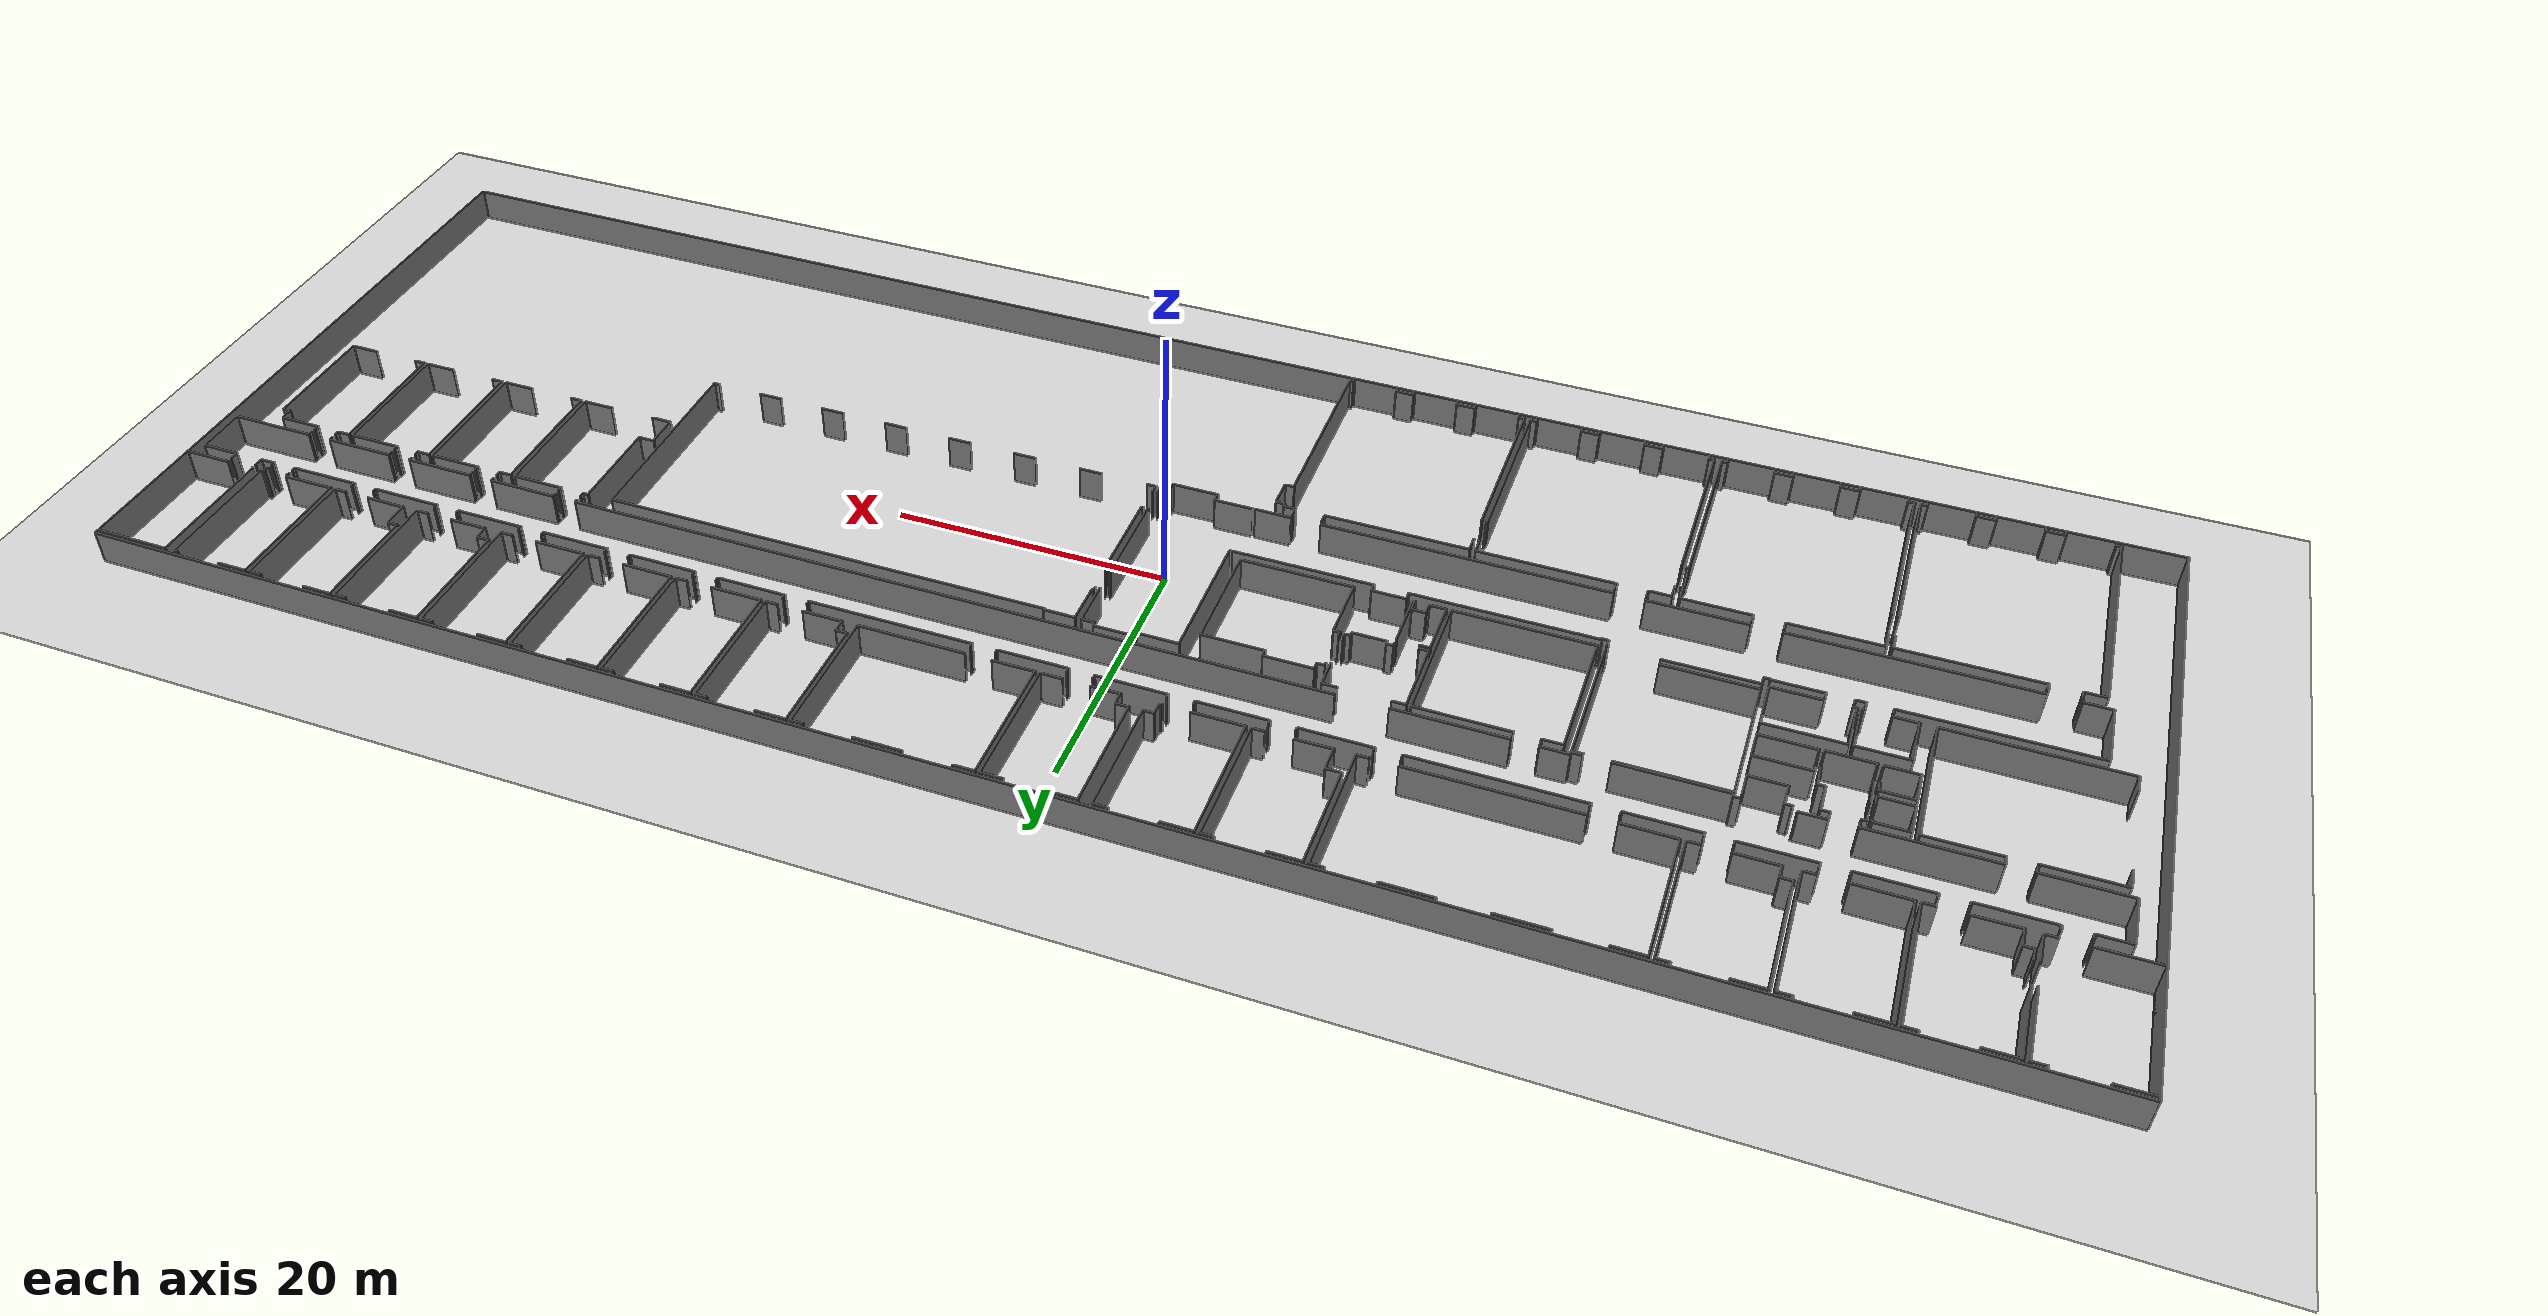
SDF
<sdf version="1.6">
  <world name="default">
    <light name="sun" type="directional">
      <cast_shadows>1</cast_shadows>
      <pose frame="">0 0 10 0 -0 0</pose>
      <diffuse>0.8 0.8 0.8 1</diffuse>
      <specular>0.1 0.1 0.1 1</specular>
      <attenuation>
        <range>1000</range>
        <constant>0.9</constant>
        <linear>0.01</linear>
        <quadratic>0.001</quadratic>
      </attenuation>
      <direction>-0.5 0.5 -1</direction>
    </light>
    <model name="ground_plane">
      <static>1</static>
      <link name="link">
        <collision name="collision">
          <geometry>
            <plane>
              <normal>0 0 1</normal>
              <size>100 100</size>
            </plane>
          </geometry>
          <surface>
            <friction>
              <ode>
                <mu>100</mu>
                <mu2>50</mu2>
              </ode>
              <torsional>
                <ode />
              </torsional>
            </friction>
            <contact>
              <ode />
            </contact>
            <bounce />
          </surface>
          <max_contacts>10</max_contacts>
        </collision>
        <visual name="visual">
          <cast_shadows>0</cast_shadows>
          <geometry>
            <plane>
              <normal>0 0 1</normal>
              <size>100 100</size>
            </plane>
          </geometry>
          <material>
            <script>
              <uri>file://media/materials/scripts/gazebo.material</uri>
              <name>Gazebo/Grey</name>
            </script>
          </material>
        </visual>
        <self_collide>0</self_collide>
        <kinematic>0</kinematic>
        <gravity>1</gravity>
      </link>
    </model>
    <gravity>0 0 -9.8</gravity>
    <magnetic_field>6e-06 2.3e-05 -4.2e-05</magnetic_field>
    <atmosphere type="adiabatic" />
    <physics default="0" name="default_physics" type="ode">
      <max_step_size>0.001</max_step_size>
      <real_time_factor>1</real_time_factor>
      <real_time_update_rate>1000</real_time_update_rate>
    </physics>
    <scene>
      <ambient>0.4 0.4 0.4 1</ambient>
      <background>0.7 0.7 0.7 1</background>
      <shadows>1</shadows>
    </scene>
    <spherical_coordinates>
      <surface_model>EARTH_WGS84</surface_model>
      <latitude_deg>0</latitude_deg>
      <longitude_deg>0</longitude_deg>
      <elevation>0</elevation>
      <heading_deg>0</heading_deg>
    </spherical_coordinates>
  <model name="0510032196_A_40_1_104">
		<static>1</static>
		<link name="Wall_0">
			<collision name="Wall_0_Collision">
				<geometry>
					<box>
						<size>9.67693559046 0.1 2.5</size>
					</box>
				</geometry>
				<pose frame="">4.83846779523 0 1.25 0 0 0</pose>
			</collision>
			<visual name="Wall_0_Visual">
				<pose frame="">4.83846779523 0 1.25 0 0 0</pose>
				<geometry>
					<box>
						<size>9.67693559046 0.1 2.5</size>
					</box>
				</geometry>
				<material>
					<script>
						<uri>file://media/materials/scripts/gazebo.material</uri>
						<name>Gazebo/Grey</name>
					</script>
					<ambient>1 1 1 1</ambient>
				</material>
			</visual>
			<pose frame="">0.0 -9.98563875756 0 0 0 1.57079632679</pose>
		</link>
		<link name="Wall_1">
			<collision name="Wall_1_Collision">
				<geometry>
					<box>
						<size>2.44280921153 0.1 2.5</size>
					</box>
				</geometry>
				<pose frame="">1.22140460576 0 1.25 0 0 0</pose>
			</collision>
			<visual name="Wall_1_Visual">
				<pose frame="">1.22140460576 0 1.25 0 0 0</pose>
				<geometry>
					<box>
						<size>2.44280921153 0.1 2.5</size>
					</box>
				</geometry>
				<material>
					<script>
						<uri>file://media/materials/scripts/gazebo.material</uri>
						<name>Gazebo/Grey</name>
					</script>
					<ambient>1 1 1 1</ambient>
				</material>
			</visual>
			<pose frame="">0.0 -0.308703167099 0 0 0 0.0</pose>
		</link>
		<link name="Wall_2">
			<collision name="Wall_2_Collision">
				<geometry>
					<box>
						<size>0.305017538508 0.1 2.5</size>
					</box>
				</geometry>
				<pose frame="">0.152508769254 0 1.25 0 0 0</pose>
			</collision>
			<visual name="Wall_2_Visual">
				<pose frame="">0.152508769254 0 1.25 0 0 0</pose>
				<geometry>
					<box>
						<size>0.305017538508 0.1 2.5</size>
					</box>
				</geometry>
				<material>
					<script>
						<uri>file://media/materials/scripts/gazebo.material</uri>
						<name>Gazebo/Grey</name>
					</script>
					<ambient>1 1 1 1</ambient>
				</material>
			</visual>
			<pose frame="">2.44280921153 -0.308703167099 0 0 0 1.57079632679</pose>
		</link>
		<link name="Wall_3">
			<collision name="Wall_3_Collision">
				<geometry>
					<box>
						<size>0.314422245946 0.1 2.5</size>
					</box>
				</geometry>
				<pose frame="">0.157211122973 0 1.25 0 0 0</pose>
			</collision>
			<visual name="Wall_3_Visual">
				<pose frame="">0.157211122973 0 1.25 0 0 0</pose>
				<geometry>
					<box>
						<size>0.314422245946 0.1 2.5</size>
					</box>
				</geometry>
				<material>
					<script>
						<uri>file://media/materials/scripts/gazebo.material</uri>
						<name>Gazebo/Grey</name>
					</script>
					<ambient>1 1 1 1</ambient>
				</material>
			</visual>
			<pose frame="">5.77550709166 -0.00368562859031 0 0 0 -1.57079632679</pose>
		</link>
		<link name="Wall_4">
			<collision name="Wall_4_Collision">
				<geometry>
					<box>
						<size>0.922550963347 0.1 2.5</size>
					</box>
				</geometry>
				<pose frame="">0.461275481674 0 1.25 0 0 0</pose>
			</collision>
			<visual name="Wall_4_Visual">
				<pose frame="">0.461275481674 0 1.25 0 0 0</pose>
				<geometry>
					<box>
						<size>0.922550963347 0.1 2.5</size>
					</box>
				</geometry>
				<material>
					<script>
						<uri>file://media/materials/scripts/gazebo.material</uri>
						<name>Gazebo/Grey</name>
					</script>
					<ambient>1 1 1 1</ambient>
				</material>
			</visual>
			<pose frame="">5.77550709166 -0.318107874536 0 0 0 0.0</pose>
		</link>
		<link name="Wall_5">
			<collision name="Wall_5_Collision">
				<geometry>
					<box>
						<size>5.55576737329 0.1 2.5</size>
					</box>
				</geometry>
				<pose frame="">2.77788368665 0 1.25 0 0 0</pose>
			</collision>
			<visual name="Wall_5_Visual">
				<pose frame="">2.77788368665 0 1.25 0 0 0</pose>
				<geometry>
					<box>
						<size>5.55576737329 0.1 2.5</size>
					</box>
				</geometry>
				<material>
					<script>
						<uri>file://media/materials/scripts/gazebo.material</uri>
						<name>Gazebo/Grey</name>
					</script>
					<ambient>1 1 1 1</ambient>
				</material>
			</visual>
			<pose frame="">6.698058055 -0.318107874536 0 0 0 -1.57079632679</pose>
		</link>
		<link name="Wall_6">
			<collision name="Wall_6_Collision">
				<geometry>
					<box>
						<size>2.23005947842 0.1 2.5</size>
					</box>
				</geometry>
				<pose frame="">1.11502973921 0 1.25 0 0 0</pose>
			</collision>
			<visual name="Wall_6_Visual">
				<pose frame="">1.11502973921 0 1.25 0 0 0</pose>
				<geometry>
					<box>
						<size>2.23005947842 0.1 2.5</size>
					</box>
				</geometry>
				<material>
					<script>
						<uri>file://media/materials/scripts/gazebo.material</uri>
						<name>Gazebo/Grey</name>
					</script>
					<ambient>1 1 1 1</ambient>
				</material>
			</visual>
			<pose frame="">6.698058055 -7.7306695135 0 0 0 -1.57079632679</pose>
		</link>
		<link name="Wall_7">
			<collision name="Wall_7_Collision">
				<geometry>
					<box>
						<size>0.864851812313 0.1 2.5</size>
					</box>
				</geometry>
				<pose frame="">0.432425906156 0 1.25 0 0 0</pose>
			</collision>
			<visual name="Wall_7_Visual">
				<pose frame="">0.432425906156 0 1.25 0 0 0</pose>
				<geometry>
					<box>
						<size>0.864851812313 0.1 2.5</size>
					</box>
				</geometry>
				<material>
					<script>
						<uri>file://media/materials/scripts/gazebo.material</uri>
						<name>Gazebo/Grey</name>
					</script>
					<ambient>1 1 1 1</ambient>
				</material>
			</visual>
			<pose frame="">6.698058055 -9.96072899192 0 0 0 3.14159265359</pose>
		</link>
		<link name="Wall_8">
			<collision name="Wall_8_Collision">
				<geometry>
					<box>
						<size>3.96467080139 0.1 2.5</size>
					</box>
				</geometry>
				<pose frame="">1.98233540069 0 1.25 0 0 0</pose>
			</collision>
			<visual name="Wall_8_Visual">
				<pose frame="">1.98233540069 0 1.25 0 0 0</pose>
				<geometry>
					<box>
						<size>3.96467080139 0.1 2.5</size>
					</box>
				</geometry>
				<material>
					<script>
						<uri>file://media/materials/scripts/gazebo.material</uri>
						<name>Gazebo/Grey</name>
					</script>
					<ambient>1 1 1 1</ambient>
				</material>
			</visual>
			<pose frame="">3.9645925474 -9.96072899192 0 0 0 -3.13530967808</pose>
		</link>
		<link name="Wall_9">
			<collision name="Wall_9_Collision">
				<geometry>
					<box>
						<size>1.34830461085 0.1 2.5</size>
					</box>
				</geometry>
				<pose frame="">0.674152305424 0 1.25 0 0 0</pose>
			</collision>
			<visual name="Wall_9_Visual">
				<pose frame="">0.674152305424 0 1.25 0 0 0</pose>
				<geometry>
					<box>
						<size>1.34830461085 0.1 2.5</size>
					</box>
				</geometry>
				<material>
					<script>
						<uri>file://media/materials/scripts/gazebo.material</uri>
						<name>Gazebo/Grey</name>
					</script>
					<ambient>1 1 1 1</ambient>
				</material>
			</visual>
			<pose frame="">7.73308423568 -9.9736922373 0 0 0 1.57079632679</pose>
		</link>
		<link name="Wall_10">
			<collision name="Wall_10_Collision">
				<geometry>
					<box>
						<size>0.690102180875 0.1 2.5</size>
					</box>
				</geometry>
				<pose frame="">0.345051090438 0 1.25 0 0 0</pose>
			</collision>
			<visual name="Wall_10_Visual">
				<pose frame="">0.345051090438 0 1.25 0 0 0</pose>
				<geometry>
					<box>
						<size>0.690102180875 0.1 2.5</size>
					</box>
				</geometry>
				<material>
					<script>
						<uri>file://media/materials/scripts/gazebo.material</uri>
						<name>Gazebo/Grey</name>
					</script>
					<ambient>1 1 1 1</ambient>
				</material>
			</visual>
			<pose frame="">7.73308423568 -8.62538762646 0 0 0 3.14159265359</pose>
		</link>
		<link name="Wall_11">
			<collision name="Wall_11_Collision">
				<geometry>
					<box>
						<size>0.872095978852 0.1 2.5</size>
					</box>
				</geometry>
				<pose frame="">0.436047989426 0 1.25 0 0 0</pose>
			</collision>
			<visual name="Wall_11_Visual">
				<pose frame="">0.436047989426 0 1.25 0 0 0</pose>
				<geometry>
					<box>
						<size>0.872095978852 0.1 2.5</size>
					</box>
				</geometry>
				<material>
					<script>
						<uri>file://media/materials/scripts/gazebo.material</uri>
						<name>Gazebo/Grey</name>
					</script>
					<ambient>1 1 1 1</ambient>
				</material>
			</visual>
			<pose frame="">7.0429820548 -8.62538762646 0 0 0 1.57079632679</pose>
		</link>
		<link name="Wall_12">
			<collision name="Wall_12_Collision">
				<geometry>
					<box>
						<size>5.57940623253 0.1 2.5</size>
					</box>
				</geometry>
				<pose frame="">2.78970311626 0 1.25 0 0 0</pose>
			</collision>
			<visual name="Wall_12_Visual">
				<pose frame="">2.78970311626 0 1.25 0 0 0</pose>
				<geometry>
					<box>
						<size>5.57940623253 0.1 2.5</size>
					</box>
				</geometry>
				<material>
					<script>
						<uri>file://media/materials/scripts/gazebo.material</uri>
						<name>Gazebo/Grey</name>
					</script>
					<ambient>1 1 1 1</ambient>
				</material>
			</visual>
			<pose frame="">7.0429820548 -5.89281175334 0 0 0 1.57079632679</pose>
		</link>
		<link name="Wall_13">
			<collision name="Wall_13_Collision">
				<geometry>
					<box>
						<size>2.24314981445 0.1 2.5</size>
					</box>
				</geometry>
				<pose frame="">1.12157490722 0 1.25 0 0 0</pose>
			</collision>
			<visual name="Wall_13_Visual">
				<pose frame="">1.12157490722 0 1.25 0 0 0</pose>
				<geometry>
					<box>
						<size>2.24314981445 0.1 2.5</size>
					</box>
				</geometry>
				<material>
					<script>
						<uri>file://media/materials/scripts/gazebo.material</uri>
						<name>Gazebo/Grey</name>
					</script>
					<ambient>1 1 1 1</ambient>
				</material>
			</visual>
			<pose frame="">7.0429820548 -0.313405520817 0 0 0 0.0</pose>
		</link>
		<link name="Wall_14">
			<collision name="Wall_14_Collision">
				<geometry>
					<box>
						<size>0.304763357226 0.1 2.5</size>
					</box>
				</geometry>
				<pose frame="">0.152381678613 0 1.25 0 0 0</pose>
			</collision>
			<visual name="Wall_14_Visual">
				<pose frame="">0.152381678613 0 1.25 0 0 0</pose>
				<geometry>
					<box>
						<size>0.304763357226 0.1 2.5</size>
					</box>
				</geometry>
				<material>
					<script>
						<uri>file://media/materials/scripts/gazebo.material</uri>
						<name>Gazebo/Grey</name>
					</script>
					<ambient>1 1 1 1</ambient>
				</material>
			</visual>
			<pose frame="">9.28613186925 -0.313405520817 0 0 0 1.57079632679</pose>
		</link>
		<link name="Wall_15">
			<collision name="Wall_15_Collision">
				<geometry>
					<box>
						<size>0.292181383763 0.1 2.5</size>
					</box>
				</geometry>
				<pose frame="">0.146090691881 0 1.25 0 0 0</pose>
			</collision>
			<visual name="Wall_15_Visual">
				<pose frame="">0.146090691881 0 1.25 0 0 0</pose>
				<geometry>
					<box>
						<size>0.292181383763 0.1 2.5</size>
					</box>
				</geometry>
				<material>
					<script>
						<uri>file://media/materials/scripts/gazebo.material</uri>
						<name>Gazebo/Grey</name>
					</script>
					<ambient>1 1 1 1</ambient>
				</material>
			</visual>
			<pose frame="">12.5949367089 -0.00864216359107 0 0 0 -1.57079632679</pose>
		</link>
		<link name="Wall_16">
			<collision name="Wall_16_Collision">
				<geometry>
					<box>
						<size>0.914162981038 0.1 2.5</size>
					</box>
				</geometry>
				<pose frame="">0.457081490519 0 1.25 0 0 0</pose>
			</collision>
			<visual name="Wall_16_Visual">
				<pose frame="">0.457081490519 0 1.25 0 0 0</pose>
				<geometry>
					<box>
						<size>0.914162981038 0.1 2.5</size>
					</box>
				</geometry>
				<material>
					<script>
						<uri>file://media/materials/scripts/gazebo.material</uri>
						<name>Gazebo/Grey</name>
					</script>
					<ambient>1 1 1 1</ambient>
				</material>
			</visual>
			<pose frame="">12.5949367089 -0.300823547354 0 0 0 0.0</pose>
		</link>
		<link name="Wall_17">
			<collision name="Wall_17_Collision">
				<geometry>
					<box>
						<size>9.65355091251 0.1 2.5</size>
					</box>
				</geometry>
				<pose frame="">4.82677545626 0 1.25 0 0 0</pose>
			</collision>
			<visual name="Wall_17_Visual">
				<pose frame="">4.82677545626 0 1.25 0 0 0</pose>
				<geometry>
					<box>
						<size>9.65355091251 0.1 2.5</size>
					</box>
				</geometry>
				<material>
					<script>
						<uri>file://media/materials/scripts/gazebo.material</uri>
						<name>Gazebo/Grey</name>
					</script>
					<ambient>1 1 1 1</ambient>
				</material>
			</visual>
			<pose frame="">13.5090996899 -0.300823547354 0 0 0 -1.57079632679</pose>
		</link>
		<link name="Wall_18">
			<collision name="Wall_18_Collision">
				<geometry>
					<box>
						<size>0.879975598597 0.1 2.5</size>
					</box>
				</geometry>
				<pose frame="">0.439987799298 0 1.25 0 0 0</pose>
			</collision>
			<visual name="Wall_18_Visual">
				<pose frame="">0.439987799298 0 1.25 0 0 0</pose>
				<geometry>
					<box>
						<size>0.879975598597 0.1 2.5</size>
					</box>
				</geometry>
				<material>
					<script>
						<uri>file://media/materials/scripts/gazebo.material</uri>
						<name>Gazebo/Grey</name>
					</script>
					<ambient>1 1 1 1</ambient>
				</material>
			</visual>
			<pose frame="">13.5090996899 -9.95437445986 0 0 0 3.14159265359</pose>
		</link>
		<link name="Wall_19">
			<collision name="Wall_19_Collision">
				<geometry>
					<box>
						<size>3.01643113249 0.1 2.5</size>
					</box>
				</geometry>
				<pose frame="">1.50821556625 0 1.25 0 0 0</pose>
			</collision>
			<visual name="Wall_19_Visual">
				<pose frame="">1.50821556625 0 1.25 0 0 0</pose>
				<geometry>
					<box>
						<size>3.01643113249 0.1 2.5</size>
					</box>
				</geometry>
				<material>
					<script>
						<uri>file://media/materials/scripts/gazebo.material</uri>
						<name>Gazebo/Grey</name>
					</script>
					<ambient>1 1 1 1</ambient>
				</material>
			</visual>
			<pose frame="">10.7494535102 -9.95437445986 0 0 0 -3.13518842666</pose>
		</link>
		<link name="Wall_20">
			<collision name="Wall_20_Collision">
				<geometry>
					<box>
						<size>9.64643383661 0.1 2.5</size>
					</box>
				</geometry>
				<pose frame="">4.82321691831 0 1.25 0 0 0</pose>
			</collision>
			<visual name="Wall_20_Visual">
				<pose frame="">4.82321691831 0 1.25 0 0 0</pose>
				<geometry>
					<box>
						<size>9.64643383661 0.1 2.5</size>
					</box>
				</geometry>
				<material>
					<script>
						<uri>file://media/materials/scripts/gazebo.material</uri>
						<name>Gazebo/Grey</name>
					</script>
					<ambient>1 1 1 1</ambient>
				</material>
			</visual>
			<pose frame="">13.8371206344 -9.95500991307 0 0 0 1.57079632679</pose>
		</link>
		<link name="Wall_21">
			<collision name="Wall_21_Collision">
				<geometry>
					<box>
						<size>2.24988561842 0.1 2.5</size>
					</box>
				</geometry>
				<pose frame="">1.12494280921 0 1.25 0 0 0</pose>
			</collision>
			<visual name="Wall_21_Visual">
				<pose frame="">1.12494280921 0 1.25 0 0 0</pose>
				<geometry>
					<box>
						<size>2.24988561842 0.1 2.5</size>
					</box>
				</geometry>
				<material>
					<script>
						<uri>file://media/materials/scripts/gazebo.material</uri>
						<name>Gazebo/Grey</name>
					</script>
					<ambient>1 1 1 1</ambient>
				</material>
			</visual>
			<pose frame="">13.8371206344 -0.308576076458 0 0 0 0.0</pose>
		</link>
		<link name="Wall_22">
			<collision name="Wall_22_Collision">
				<geometry>
					<box>
						<size>0.29790046261 0.1 2.5</size>
					</box>
				</geometry>
				<pose frame="">0.148950231305 0 1.25 0 0 0</pose>
			</collision>
			<visual name="Wall_22_Visual">
				<pose frame="">0.148950231305 0 1.25 0 0 0</pose>
				<geometry>
					<box>
						<size>0.29790046261 0.1 2.5</size>
					</box>
				</geometry>
				<material>
					<script>
						<uri>file://media/materials/scripts/gazebo.material</uri>
						<name>Gazebo/Grey</name>
					</script>
					<ambient>1 1 1 1</ambient>
				</material>
			</visual>
			<pose frame="">16.0870062529 -0.308576076458 0 0 0 1.57079632679</pose>
		</link>
		<link name="Wall_23">
			<collision name="Wall_23_Collision">
				<geometry>
					<box>
						<size>0.29790046261 0.1 2.5</size>
					</box>
				</geometry>
				<pose frame="">0.148950231305 0 1.25 0 0 0</pose>
			</collision>
			<visual name="Wall_23_Visual">
				<pose frame="">0.148950231305 0 1.25 0 0 0</pose>
				<geometry>
					<box>
						<size>0.29790046261 0.1 2.5</size>
					</box>
				</geometry>
				<material>
					<script>
						<uri>file://media/materials/scripts/gazebo.material</uri>
						<name>Gazebo/Grey</name>
					</script>
					<ambient>1 1 1 1</ambient>
				</material>
			</visual>
			<pose frame="">19.4144934167 -0.0106756138478 0 0 0 -1.57079632679</pose>
		</link>
		<link name="Wall_24">
			<collision name="Wall_24_Collision">
				<geometry>
					<box>
						<size>0.933353667836 0.1 2.5</size>
					</box>
				</geometry>
				<pose frame="">0.466676833918 0 1.25 0 0 0</pose>
			</collision>
			<visual name="Wall_24_Visual">
				<pose frame="">0.466676833918 0 1.25 0 0 0</pose>
				<geometry>
					<box>
						<size>0.933353667836 0.1 2.5</size>
					</box>
				</geometry>
				<material>
					<script>
						<uri>file://media/materials/scripts/gazebo.material</uri>
						<name>Gazebo/Grey</name>
					</script>
					<ambient>1 1 1 1</ambient>
				</material>
			</visual>
			<pose frame="">19.4144934167 -0.308576076458 0 0 0 0.0</pose>
		</link>
		<link name="Wall_25">
			<collision name="Wall_25_Collision">
				<geometry>
					<box>
						<size>9.67553759341 0.1 2.5</size>
					</box>
				</geometry>
				<pose frame="">4.83776879671 0 1.25 0 0 0</pose>
			</collision>
			<visual name="Wall_25_Visual">
				<pose frame="">4.83776879671 0 1.25 0 0 0</pose>
				<geometry>
					<box>
						<size>9.67553759341 0.1 2.5</size>
					</box>
				</geometry>
				<material>
					<script>
						<uri>file://media/materials/scripts/gazebo.material</uri>
						<name>Gazebo/Grey</name>
					</script>
					<ambient>1 1 1 1</ambient>
				</material>
			</visual>
			<pose frame="">20.3478470845 -0.308576076458 0 0 0 -1.57079632679</pose>
		</link>
		<link name="Wall_26">
			<collision name="Wall_26_Collision">
				<geometry>
					<box>
						<size>0.88645722129 0.1 2.5</size>
					</box>
				</geometry>
				<pose frame="">0.443228610645 0 1.25 0 0 0</pose>
			</collision>
			<visual name="Wall_26_Visual">
				<pose frame="">0.443228610645 0 1.25 0 0 0</pose>
				<geometry>
					<box>
						<size>0.88645722129 0.1 2.5</size>
					</box>
				</geometry>
				<material>
					<script>
						<uri>file://media/materials/scripts/gazebo.material</uri>
						<name>Gazebo/Grey</name>
					</script>
					<ambient>1 1 1 1</ambient>
				</material>
			</visual>
			<pose frame="">20.3478470845 -9.98411366987 0 0 0 3.14159265359</pose>
		</link>
		<link name="Wall_27">
			<collision name="Wall_27_Collision">
				<geometry>
					<box>
						<size>3.74903269755 0.1 2.5</size>
					</box>
				</geometry>
				<pose frame="">1.87451634877 0 1.25 0 0 0</pose>
			</collision>
			<visual name="Wall_27_Visual">
				<pose frame="">1.87451634877 0 1.25 0 0 0</pose>
				<geometry>
					<box>
						<size>3.74903269755 0.1 2.5</size>
					</box>
				</geometry>
				<material>
					<script>
						<uri>file://media/materials/scripts/gazebo.material</uri>
						<name>Gazebo/Grey</name>
					</script>
					<ambient>1 1 1 1</ambient>
				</material>
			</visual>
			<pose frame="">17.586040364 -9.98411366987 0 0 0 3.13382957136</pose>
		</link>
		<link name="Wall_28">
			<collision name="Wall_28_Collision">
				<geometry>
					<box>
						<size>0.950383813736 0.1 2.5</size>
					</box>
				</geometry>
				<pose frame="">0.475191906868 0 1.25 0 0 0</pose>
			</collision>
			<visual name="Wall_28_Visual">
				<pose frame="">0.475191906868 0 1.25 0 0 0</pose>
				<geometry>
					<box>
						<size>0.950383813736 0.1 2.5</size>
					</box>
				</geometry>
				<material>
					<script>
						<uri>file://media/materials/scripts/gazebo.material</uri>
						<name>Gazebo/Grey</name>
					</script>
					<ambient>1 1 1 1</ambient>
				</material>
			</visual>
			<pose frame="">21.4920441259 -9.95157846576 0 0 0 1.57079632679</pose>
		</link>
		<link name="Wall_29">
			<collision name="Wall_29_Collision">
				<geometry>
					<box>
						<size>0.800798129226 0.1 2.5</size>
					</box>
				</geometry>
				<pose frame="">0.400399064613 0 1.25 0 0 0</pose>
			</collision>
			<visual name="Wall_29_Visual">
				<pose frame="">0.400399064613 0 1.25 0 0 0</pose>
				<geometry>
					<box>
						<size>0.800798129226 0.1 2.5</size>
					</box>
				</geometry>
				<material>
					<script>
						<uri>file://media/materials/scripts/gazebo.material</uri>
						<name>Gazebo/Grey</name>
					</script>
					<ambient>1 1 1 1</ambient>
				</material>
			</visual>
			<pose frame="">21.4920441259 -9.00119465203 0 0 0 3.14159265359</pose>
		</link>
		<link name="Wall_30">
			<collision name="Wall_30_Collision">
				<geometry>
					<box>
						<size>8.70037110467 0.1 2.5</size>
					</box>
				</geometry>
				<pose frame="">4.35018555234 0 1.25 0 0 0</pose>
			</collision>
			<visual name="Wall_30_Visual">
				<pose frame="">4.35018555234 0 1.25 0 0 0</pose>
				<geometry>
					<box>
						<size>8.70037110467 0.1 2.5</size>
					</box>
				</geometry>
				<material>
					<script>
						<uri>file://media/materials/scripts/gazebo.material</uri>
						<name>Gazebo/Grey</name>
					</script>
					<ambient>1 1 1 1</ambient>
				</material>
			</visual>
			<pose frame="">20.6912459966 -9.00119465203 0 0 0 1.57079632679</pose>
		</link>
		<link name="Wall_31">
			<collision name="Wall_31_Collision">
				<geometry>
					<box>
						<size>2.23056784098 0.1 2.5</size>
					</box>
				</geometry>
				<pose frame="">1.11528392049 0 1.25 0 0 0</pose>
			</collision>
			<visual name="Wall_31_Visual">
				<pose frame="">1.11528392049 0 1.25 0 0 0</pose>
				<geometry>
					<box>
						<size>2.23056784098 0.1 2.5</size>
					</box>
				</geometry>
				<material>
					<script>
						<uri>file://media/materials/scripts/gazebo.material</uri>
						<name>Gazebo/Grey</name>
					</script>
					<ambient>1 1 1 1</ambient>
				</material>
			</visual>
			<pose frame="">20.6912459966 -0.300823547354 0 0 0 0.0</pose>
		</link>
		<link name="Wall_32">
			<collision name="Wall_32_Collision">
				<geometry>
					<box>
						<size>0.284301764018 0.1 2.5</size>
					</box>
				</geometry>
				<pose frame="">0.142150882009 0 1.25 0 0 0</pose>
			</collision>
			<visual name="Wall_32_Visual">
				<pose frame="">0.142150882009 0 1.25 0 0 0</pose>
				<geometry>
					<box>
						<size>0.284301764018 0.1 2.5</size>
					</box>
				</geometry>
				<material>
					<script>
						<uri>file://media/materials/scripts/gazebo.material</uri>
						<name>Gazebo/Grey</name>
					</script>
					<ambient>1 1 1 1</ambient>
				</material>
			</visual>
			<pose frame="">22.9218138376 -0.300823547354 0 0 0 1.57079632679</pose>
		</link>
		<link name="Wall_33">
			<collision name="Wall_33_Collision">
				<geometry>
					<box>
						<size>0.291164658635 0.1 2.5</size>
					</box>
				</geometry>
				<pose frame="">0.145582329317 0 1.25 0 0 0</pose>
			</collision>
			<visual name="Wall_33_Visual">
				<pose frame="">0.145582329317 0 1.25 0 0 0</pose>
				<geometry>
					<box>
						<size>0.291164658635 0.1 2.5</size>
					</box>
				</geometry>
				<material>
					<script>
						<uri>file://media/materials/scripts/gazebo.material</uri>
						<name>Gazebo/Grey</name>
					</script>
					<ambient>1 1 1 1</ambient>
				</material>
			</visual>
			<pose frame="">26.2543846271 -0.0165217833359 0 0 0 -1.57079632679</pose>
		</link>
		<link name="Wall_34">
			<collision name="Wall_34_Collision">
				<geometry>
					<box>
						<size>0.912129530781 0.1 2.5</size>
					</box>
				</geometry>
				<pose frame="">0.456064765391 0 1.25 0 0 0</pose>
			</collision>
			<visual name="Wall_34_Visual">
				<pose frame="">0.456064765391 0 1.25 0 0 0</pose>
				<geometry>
					<box>
						<size>0.912129530781 0.1 2.5</size>
					</box>
				</geometry>
				<material>
					<script>
						<uri>file://media/materials/scripts/gazebo.material</uri>
						<name>Gazebo/Grey</name>
					</script>
					<ambient>1 1 1 1</ambient>
				</material>
			</visual>
			<pose frame="">26.2543846271 -0.30768644197 0 0 0 0.0</pose>
		</link>
		<link name="Wall_35">
			<collision name="Wall_35_Collision">
				<geometry>
					<box>
						<size>9.66066798841 0.1 2.5</size>
					</box>
				</geometry>
				<pose frame="">4.8303339942 0 1.25 0 0 0</pose>
			</collision>
			<visual name="Wall_35_Visual">
				<pose frame="">4.8303339942 0 1.25 0 0 0</pose>
				<geometry>
					<box>
						<size>9.66066798841 0.1 2.5</size>
					</box>
				</geometry>
				<material>
					<script>
						<uri>file://media/materials/scripts/gazebo.material</uri>
						<name>Gazebo/Grey</name>
					</script>
					<ambient>1 1 1 1</ambient>
				</material>
			</visual>
			<pose frame="">27.1665141579 -0.30768644197 0 0 0 -1.57079632679</pose>
		</link>
		<link name="Wall_36">
			<collision name="Wall_36_Collision">
				<geometry>
					<box>
						<size>0.90221646078 0.1 2.5</size>
					</box>
				</geometry>
				<pose frame="">0.45110823039 0 1.25 0 0 0</pose>
			</collision>
			<visual name="Wall_36_Visual">
				<pose frame="">0.45110823039 0 1.25 0 0 0</pose>
				<geometry>
					<box>
						<size>0.90221646078 0.1 2.5</size>
					</box>
				</geometry>
				<material>
					<script>
						<uri>file://media/materials/scripts/gazebo.material</uri>
						<name>Gazebo/Grey</name>
					</script>
					<ambient>1 1 1 1</ambient>
				</material>
			</visual>
			<pose frame="">27.1665141579 -9.96835443038 0 0 0 3.14159265359</pose>
		</link>
		<link name="Wall_37">
			<collision name="Wall_37_Collision">
				<geometry>
					<box>
						<size>2.93635009335 0.1 2.5</size>
					</box>
				</geometry>
				<pose frame="">1.46817504667 0 1.25 0 0 0</pose>
			</collision>
			<visual name="Wall_37_Visual">
				<pose frame="">1.46817504667 0 1.25 0 0 0</pose>
				<geometry>
					<box>
						<size>2.93635009335 0.1 2.5</size>
					</box>
				</geometry>
				<material>
					<script>
						<uri>file://media/materials/scripts/gazebo.material</uri>
						<name>Gazebo/Grey</name>
					</script>
					<ambient>1 1 1 1</ambient>
				</material>
			</visual>
			<pose frame="">24.4283462966 -9.96835443038 0 0 0 3.13587941935</pose>
		</link>
		<link name="Wall_38">
			<collision name="Wall_38_Collision">
				<geometry>
					<box>
						<size>9.65393218443 0.1 2.5</size>
					</box>
				</geometry>
				<pose frame="">4.82696609222 0 1.25 0 0 0</pose>
			</collision>
			<visual name="Wall_38_Visual">
				<pose frame="">4.82696609222 0 1.25 0 0 0</pose>
				<geometry>
					<box>
						<size>9.65393218443 0.1 2.5</size>
					</box>
				</geometry>
				<material>
					<script>
						<uri>file://media/materials/scripts/gazebo.material</uri>
						<name>Gazebo/Grey</name>
					</script>
					<ambient>1 1 1 1</ambient>
				</material>
			</visual>
			<pose frame="">27.5039398099 -9.96263535153 0 0 0 1.57079632679</pose>
		</link>
		<link name="Wall_39">
			<collision name="Wall_39_Collision">
				<geometry>
					<box>
						<size>2.22523003406 0.1 2.5</size>
					</box>
				</geometry>
				<pose frame="">1.11261501703 0 1.25 0 0 0</pose>
			</collision>
			<visual name="Wall_39_Visual">
				<pose frame="">1.11261501703 0 1.25 0 0 0</pose>
				<geometry>
					<box>
						<size>2.22523003406 0.1 2.5</size>
					</box>
				</geometry>
				<material>
					<script>
						<uri>file://media/materials/scripts/gazebo.material</uri>
						<name>Gazebo/Grey</name>
					</script>
					<ambient>1 1 1 1</ambient>
				</material>
			</visual>
			<pose frame="">27.5039398099 -0.308703167099 0 0 0 0.0</pose>
		</link>
		<link name="Wall_40">
			<collision name="Wall_40_Collision">
				<geometry>
					<box>
						<size>0.305017538508 0.1 2.5</size>
					</box>
				</geometry>
				<pose frame="">0.152508769254 0 1.25 0 0 0</pose>
			</collision>
			<visual name="Wall_40_Visual">
				<pose frame="">0.152508769254 0 1.25 0 0 0</pose>
				<geometry>
					<box>
						<size>0.305017538508 0.1 2.5</size>
					</box>
				</geometry>
				<material>
					<script>
						<uri>file://media/materials/scripts/gazebo.material</uri>
						<name>Gazebo/Grey</name>
					</script>
					<ambient>1 1 1 1</ambient>
				</material>
			</visual>
			<pose frame="">29.7291698439 -0.308703167099 0 0 0 1.57079632679</pose>
		</link>
		<link name="Wall_41">
			<collision name="Wall_41_Collision">
				<geometry>
					<box>
						<size>0.297137918764 0.1 2.5</size>
					</box>
				</geometry>
				<pose frame="">0.148568959382 0 1.25 0 0 0</pose>
			</collision>
			<visual name="Wall_41_Visual">
				<pose frame="">0.148568959382 0 1.25 0 0 0</pose>
				<geometry>
					<box>
						<size>0.297137918764 0.1 2.5</size>
					</box>
				</geometry>
				<material>
					<script>
						<uri>file://media/materials/scripts/gazebo.material</uri>
						<name>Gazebo/Grey</name>
					</script>
					<ambient>1 1 1 1</ambient>
				</material>
			</visual>
			<pose frame="">33.0822022266 -0.00368562859031 0 0 0 -1.57079632679</pose>
		</link>
		<link name="Wall_42">
			<collision name="Wall_42_Collision">
				<geometry>
					<box>
						<size>3.50681205836 0.1 2.5</size>
					</box>
				</geometry>
				<pose frame="">1.75340602918 0 1.25 0 0 0</pose>
			</collision>
			<visual name="Wall_42_Visual">
				<pose frame="">1.75340602918 0 1.25 0 0 0</pose>
				<geometry>
					<box>
						<size>3.50681205836 0.1 2.5</size>
					</box>
				</geometry>
				<material>
					<script>
						<uri>file://media/materials/scripts/gazebo.material</uri>
						<name>Gazebo/Grey</name>
					</script>
					<ambient>1 1 1 1</ambient>
				</material>
			</visual>
			<pose frame="">33.0822022266 -0.300823547354 0 0 0 0.0</pose>
		</link>
		<link name="Wall_43">
			<collision name="Wall_43_Collision">
				<geometry>
					<box>
						<size>0.284301764018 0.1 2.5</size>
					</box>
				</geometry>
				<pose frame="">0.142150882009 0 1.25 0 0 0</pose>
			</collision>
			<visual name="Wall_43_Visual">
				<pose frame="">0.142150882009 0 1.25 0 0 0</pose>
				<geometry>
					<box>
						<size>0.284301764018 0.1 2.5</size>
					</box>
				</geometry>
				<material>
					<script>
						<uri>file://media/materials/scripts/gazebo.material</uri>
						<name>Gazebo/Grey</name>
					</script>
					<ambient>1 1 1 1</ambient>
				</material>
			</visual>
			<pose frame="">36.589014285 -0.300823547354 0 0 0 1.57079632679</pose>
		</link>
		<link name="Wall_44">
			<collision name="Wall_44_Collision">
				<geometry>
					<box>
						<size>0.282903766967 0.1 2.5</size>
					</box>
				</geometry>
				<pose frame="">0.141451883483 0 1.25 0 0 0</pose>
			</collision>
			<visual name="Wall_44_Visual">
				<pose frame="">0.141451883483 0 1.25 0 0 0</pose>
				<geometry>
					<box>
						<size>0.282903766967 0.1 2.5</size>
					</box>
				</geometry>
				<material>
					<script>
						<uri>file://media/materials/scripts/gazebo.material</uri>
						<name>Gazebo/Grey</name>
					</script>
					<ambient>1 1 1 1</ambient>
				</material>
			</visual>
			<pose frame="">39.8951502211 -0.0165217833359 0 0 0 -1.57079632679</pose>
		</link>
		<link name="Wall_45">
			<collision name="Wall_45_Collision">
				<geometry>
					<box>
						<size>3.50185552336 0.1 2.5</size>
					</box>
				</geometry>
				<pose frame="">1.75092776168 0 1.25 0 0 0</pose>
			</collision>
			<visual name="Wall_45_Visual">
				<pose frame="">1.75092776168 0 1.25 0 0 0</pose>
				<geometry>
					<box>
						<size>3.50185552336 0.1 2.5</size>
					</box>
				</geometry>
				<material>
					<script>
						<uri>file://media/materials/scripts/gazebo.material</uri>
						<name>Gazebo/Grey</name>
					</script>
					<ambient>1 1 1 1</ambient>
				</material>
			</visual>
			<pose frame="">39.8951502211 -0.299425550302 0 0 0 0.0</pose>
		</link>
		<link name="Wall_46">
			<collision name="Wall_46_Collision">
				<geometry>
					<box>
						<size>0.299425550302 0.1 2.5</size>
					</box>
				</geometry>
				<pose frame="">0.149712775151 0 1.25 0 0 0</pose>
			</collision>
			<visual name="Wall_46_Visual">
				<pose frame="">0.149712775151 0 1.25 0 0 0</pose>
				<geometry>
					<box>
						<size>0.299425550302 0.1 2.5</size>
					</box>
				</geometry>
				<material>
					<script>
						<uri>file://media/materials/scripts/gazebo.material</uri>
						<name>Gazebo/Grey</name>
					</script>
					<ambient>1 1 1 1</ambient>
				</material>
			</visual>
			<pose frame="">43.3970057445 -0.299425550302 0 0 0 1.57079632679</pose>
		</link>
		<link name="Wall_47">
			<collision name="Wall_47_Collision">
				<geometry>
					<box>
						<size>0.295231559148 0.1 2.5</size>
					</box>
				</geometry>
				<pose frame="">0.147615779574 0 1.25 0 0 0</pose>
			</collision>
			<visual name="Wall_47_Visual">
				<pose frame="">0.147615779574 0 1.25 0 0 0</pose>
				<geometry>
					<box>
						<size>0.295231559148 0.1 2.5</size>
					</box>
				</geometry>
				<material>
					<script>
						<uri>file://media/materials/scripts/gazebo.material</uri>
						<name>Gazebo/Grey</name>
					</script>
					<ambient>1 1 1 1</ambient>
				</material>
			</visual>
			<pose frame="">46.7275430837 -0.0 0 0 0 -1.57079632679</pose>
		</link>
		<link name="Wall_48">
			<collision name="Wall_48_Collision">
				<geometry>
					<box>
						<size>0.905266636165 0.1 2.5</size>
					</box>
				</geometry>
				<pose frame="">0.452633318082 0 1.25 0 0 0</pose>
			</collision>
			<visual name="Wall_48_Visual">
				<pose frame="">0.452633318082 0 1.25 0 0 0</pose>
				<geometry>
					<box>
						<size>0.905266636165 0.1 2.5</size>
					</box>
				</geometry>
				<material>
					<script>
						<uri>file://media/materials/scripts/gazebo.material</uri>
						<name>Gazebo/Grey</name>
					</script>
					<ambient>1 1 1 1</ambient>
				</material>
			</visual>
			<pose frame="">46.7275430837 -0.295231559148 0 0 0 0.0</pose>
		</link>
		<link name="Wall_49">
			<collision name="Wall_49_Collision">
				<geometry>
					<box>
						<size>9.684179757 0.1 2.5</size>
					</box>
				</geometry>
				<pose frame="">4.8420898785 0 1.25 0 0 0</pose>
			</collision>
			<visual name="Wall_49_Visual">
				<pose frame="">4.8420898785 0 1.25 0 0 0</pose>
				<geometry>
					<box>
						<size>9.684179757 0.1 2.5</size>
					</box>
				</geometry>
				<material>
					<script>
						<uri>file://media/materials/scripts/gazebo.material</uri>
						<name>Gazebo/Grey</name>
					</script>
					<ambient>1 1 1 1</ambient>
				</material>
			</visual>
			<pose frame="">47.6328097199 -0.295231559148 0 0 0 -1.57079632679</pose>
		</link>
		<link name="Wall_50">
			<collision name="Wall_50_Collision">
				<geometry>
					<box>
						<size>0.850998932439 0.1 2.5</size>
					</box>
				</geometry>
				<pose frame="">0.425499466219 0 1.25 0 0 0</pose>
			</collision>
			<visual name="Wall_50_Visual">
				<pose frame="">0.425499466219 0 1.25 0 0 0</pose>
				<geometry>
					<box>
						<size>0.850998932439 0.1 2.5</size>
					</box>
				</geometry>
				<material>
					<script>
						<uri>file://media/materials/scripts/gazebo.material</uri>
						<name>Gazebo/Grey</name>
					</script>
					<ambient>1 1 1 1</ambient>
				</material>
			</visual>
			<pose frame="">47.6328097199 -9.97941131615 0 0 0 3.14159265359</pose>
		</link>
		<link name="Wall_51">
			<collision name="Wall_51_Collision">
				<geometry>
					<box>
						<size>11.769228814 0.1 2.5</size>
					</box>
				</geometry>
				<pose frame="">5.884614407 0 1.25 0 0 0</pose>
			</collision>
			<visual name="Wall_51_Visual">
				<pose frame="">5.884614407 0 1.25 0 0 0</pose>
				<geometry>
					<box>
						<size>11.769228814 0.1 2.5</size>
					</box>
				</geometry>
				<material>
					<script>
						<uri>file://media/materials/scripts/gazebo.material</uri>
						<name>Gazebo/Grey</name>
					</script>
					<ambient>1 1 1 1</ambient>
				</material>
			</visual>
			<pose frame="">44.9082405572 -9.97941131615 0 0 0 3.14159265359</pose>
		</link>
		<link name="Wall_52">
			<collision name="Wall_52_Collision">
				<geometry>
					<box>
						<size>3.75556591186 0.1 2.5</size>
					</box>
				</geometry>
				<pose frame="">1.87778295593 0 1.25 0 0 0</pose>
			</collision>
			<visual name="Wall_52_Visual">
				<pose frame="">1.87778295593 0 1.25 0 0 0</pose>
				<geometry>
					<box>
						<size>3.75556591186 0.1 2.5</size>
					</box>
				</geometry>
				<material>
					<script>
						<uri>file://media/materials/scripts/gazebo.material</uri>
						<name>Gazebo/Grey</name>
					</script>
					<ambient>1 1 1 1</ambient>
				</material>
			</visual>
			<pose frame="">31.2594682528 -9.97941131615 0 0 0 3.13712567823</pose>
		</link>
		<link name="Wall_53">
			<collision name="Wall_53_Collision">
				<geometry>
					<box>
						<size>1.80544964669 0.1 2.5</size>
					</box>
				</geometry>
				<pose frame="">0.902724823344 0 1.25 0 0 0</pose>
			</collision>
			<visual name="Wall_53_Visual">
				<pose frame="">0.902724823344 0 1.25 0 0 0</pose>
				<geometry>
					<box>
						<size>1.80544964669 0.1 2.5</size>
					</box>
				</geometry>
				<material>
					<script>
						<uri>file://media/materials/scripts/gazebo.material</uri>
						<name>Gazebo/Grey</name>
					</script>
					<ambient>1 1 1 1</ambient>
				</material>
			</visual>
			<pose frame="">49.072365411 -9.98030095064 0 0 0 1.57079632679</pose>
		</link>
		<link name="Wall_54">
			<collision name="Wall_54_Collision">
				<geometry>
					<box>
						<size>1.06845101927 0.1 2.5</size>
					</box>
				</geometry>
				<pose frame="">0.534225509633 0 1.25 0 0 0</pose>
			</collision>
			<visual name="Wall_54_Visual">
				<pose frame="">0.534225509633 0 1.25 0 0 0</pose>
				<geometry>
					<box>
						<size>1.06845101927 0.1 2.5</size>
					</box>
				</geometry>
				<material>
					<script>
						<uri>file://media/materials/scripts/gazebo.material</uri>
						<name>Gazebo/Grey</name>
					</script>
					<ambient>1 1 1 1</ambient>
				</material>
			</visual>
			<pose frame="">49.072365411 -8.17485130395 0 0 0 3.14159265359</pose>
		</link>
		<link name="Wall_55">
			<collision name="Wall_55_Collision">
				<geometry>
					<box>
						<size>7.86957958416 0.1 2.5</size>
					</box>
				</geometry>
				<pose frame="">3.93478979208 0 1.25 0 0 0</pose>
			</collision>
			<visual name="Wall_55_Visual">
				<pose frame="">3.93478979208 0 1.25 0 0 0</pose>
				<geometry>
					<box>
						<size>7.86957958416 0.1 2.5</size>
					</box>
				</geometry>
				<material>
					<script>
						<uri>file://media/materials/scripts/gazebo.material</uri>
						<name>Gazebo/Grey</name>
					</script>
					<ambient>1 1 1 1</ambient>
				</material>
			</visual>
			<pose frame="">48.0039143917 -8.17485130395 0 0 0 1.57079632679</pose>
		</link>
		<link name="Wall_56">
			<collision name="Wall_56_Collision">
				<geometry>
					<box>
						<size>2.23806618881 0.1 2.5</size>
					</box>
				</geometry>
				<pose frame="">1.1190330944 0 1.25 0 0 0</pose>
			</collision>
			<visual name="Wall_56_Visual">
				<pose frame="">1.1190330944 0 1.25 0 0 0</pose>
				<geometry>
					<box>
						<size>2.23806618881 0.1 2.5</size>
					</box>
				</geometry>
				<material>
					<script>
						<uri>file://media/materials/scripts/gazebo.material</uri>
						<name>Gazebo/Grey</name>
					</script>
					<ambient>1 1 1 1</ambient>
				</material>
			</visual>
			<pose frame="">48.0039143917 -0.305271719791 0 0 0 0.0</pose>
		</link>
		<link name="Wall_57">
			<collision name="Wall_57_Collision">
				<geometry>
					<box>
						<size>0.29065629607 0.1 2.5</size>
					</box>
				</geometry>
				<pose frame="">0.145328148035 0 1.25 0 0 0</pose>
			</collision>
			<visual name="Wall_57_Visual">
				<pose frame="">0.145328148035 0 1.25 0 0 0</pose>
				<geometry>
					<box>
						<size>0.29065629607 0.1 2.5</size>
					</box>
				</geometry>
				<material>
					<script>
						<uri>file://media/materials/scripts/gazebo.material</uri>
						<name>Gazebo/Grey</name>
					</script>
					<ambient>1 1 1 1</ambient>
				</material>
			</visual>
			<pose frame="">50.2419805806 -0.305271719791 0 0 0 1.57079632679</pose>
		</link>
		<link name="Wall_58">
			<collision name="Wall_58_Collision">
				<geometry>
					<box>
						<size>0.28328503889 0.1 2.5</size>
					</box>
				</geometry>
				<pose frame="">0.141642519445 0 1.25 0 0 0</pose>
			</collision>
			<visual name="Wall_58_Visual">
				<pose frame="">0.141642519445 0 1.25 0 0 0</pose>
				<geometry>
					<box>
						<size>0.28328503889 0.1 2.5</size>
					</box>
				</geometry>
				<material>
					<script>
						<uri>file://media/materials/scripts/gazebo.material</uri>
						<name>Gazebo/Grey</name>
					</script>
					<ambient>1 1 1 1</ambient>
				</material>
			</visual>
			<pose frame="">53.5482436073 -0.0146154237202 0 0 0 -1.57079632679</pose>
		</link>
		<link name="Wall_59">
			<collision name="Wall_59_Collision">
				<geometry>
					<box>
						<size>0.909333536678 0.1 2.5</size>
					</box>
				</geometry>
				<pose frame="">0.454666768339 0 1.25 0 0 0</pose>
			</collision>
			<visual name="Wall_59_Visual">
				<pose frame="">0.454666768339 0 1.25 0 0 0</pose>
				<geometry>
					<box>
						<size>0.909333536678 0.1 2.5</size>
					</box>
				</geometry>
				<material>
					<script>
						<uri>file://media/materials/scripts/gazebo.material</uri>
						<name>Gazebo/Grey</name>
					</script>
					<ambient>1 1 1 1</ambient>
				</material>
			</visual>
			<pose frame="">53.5482436073 -0.29790046261 0 0 0 0.0</pose>
		</link>
		<link name="Wall_60">
			<collision name="Wall_60_Collision">
				<geometry>
					<box>
						<size>9.65253418738 0.1 2.5</size>
					</box>
				</geometry>
				<pose frame="">4.82626709369 0 1.25 0 0 0</pose>
			</collision>
			<visual name="Wall_60_Visual">
				<pose frame="">4.82626709369 0 1.25 0 0 0</pose>
				<geometry>
					<box>
						<size>9.65253418738 0.1 2.5</size>
					</box>
				</geometry>
				<material>
					<script>
						<uri>file://media/materials/scripts/gazebo.material</uri>
						<name>Gazebo/Grey</name>
					</script>
					<ambient>1 1 1 1</ambient>
				</material>
			</visual>
			<pose frame="">54.457577144 -0.29790046261 0 0 0 -1.57079632679</pose>
		</link>
		<link name="Wall_61">
			<collision name="Wall_61_Collision">
				<geometry>
					<box>
						<size>0.87908596411 0.1 2.5</size>
					</box>
				</geometry>
				<pose frame="">0.439542982055 0 1.25 0 0 0</pose>
			</collision>
			<visual name="Wall_61_Visual">
				<pose frame="">0.439542982055 0 1.25 0 0 0</pose>
				<geometry>
					<box>
						<size>0.87908596411 0.1 2.5</size>
					</box>
				</geometry>
				<material>
					<script>
						<uri>file://media/materials/scripts/gazebo.material</uri>
						<name>Gazebo/Grey</name>
					</script>
					<ambient>1 1 1 1</ambient>
				</material>
			</visual>
			<pose frame="">54.457577144 -9.95043464999 0 0 0 3.14159265359</pose>
		</link>
		<link name="Wall_62">
			<collision name="Wall_62_Collision">
				<geometry>
					<box>
						<size>2.61582298896 0.1 2.5</size>
					</box>
				</geometry>
				<pose frame="">1.30791149448 0 1.25 0 0 0</pose>
			</collision>
			<visual name="Wall_62_Visual">
				<pose frame="">1.30791149448 0 1.25 0 0 0</pose>
				<geometry>
					<box>
						<size>2.61582298896 0.1 2.5</size>
					</box>
				</geometry>
				<material>
					<script>
						<uri>file://media/materials/scripts/gazebo.material</uri>
						<name>Gazebo/Grey</name>
					</script>
					<ambient>1 1 1 1</ambient>
				</material>
			</visual>
			<pose frame="">51.6880178944 -9.95043464999 0 0 0 -3.13017485135</pose>
		</link>
		<link name="Wall_63">
			<collision name="Wall_63_Collision">
				<geometry>
					<box>
						<size>9.64834019623 0.1 2.5</size>
					</box>
				</geometry>
				<pose frame="">4.82417009811 0 1.25 0 0 0</pose>
			</collision>
			<visual name="Wall_63_Visual">
				<pose frame="">4.82417009811 0 1.25 0 0 0</pose>
				<geometry>
					<box>
						<size>9.64834019623 0.1 2.5</size>
					</box>
				</geometry>
				<material>
					<script>
						<uri>file://media/materials/scripts/gazebo.material</uri>
						<name>Gazebo/Grey</name>
					</script>
					<ambient>1 1 1 1</ambient>
				</material>
			</visual>
			<pose frame="">54.814828936 -9.96644807076 0 0 0 1.57079632679</pose>
		</link>
		<link name="Wall_64">
			<collision name="Wall_64_Collision">
				<geometry>
					<box>
						<size>2.2197651365 0.1 2.5</size>
					</box>
				</geometry>
				<pose frame="">1.10988256825 0 1.25 0 0 0</pose>
			</collision>
			<visual name="Wall_64_Visual">
				<pose frame="">1.10988256825 0 1.25 0 0 0</pose>
				<geometry>
					<box>
						<size>2.2197651365 0.1 2.5</size>
					</box>
				</geometry>
				<material>
					<script>
						<uri>file://media/materials/scripts/gazebo.material</uri>
						<name>Gazebo/Grey</name>
					</script>
					<ambient>1 1 1 1</ambient>
				</material>
			</visual>
			<pose frame="">54.814828936 -0.318107874536 0 0 0 0.0</pose>
		</link>
		<link name="Wall_65">
			<collision name="Wall_65_Collision">
				<geometry>
					<box>
						<size>0.307432260688 0.1 2.5</size>
					</box>
				</geometry>
				<pose frame="">0.153716130344 0 1.25 0 0 0</pose>
			</collision>
			<visual name="Wall_65_Visual">
				<pose frame="">0.153716130344 0 1.25 0 0 0</pose>
				<geometry>
					<box>
						<size>0.307432260688 0.1 2.5</size>
					</box>
				</geometry>
				<material>
					<script>
						<uri>file://media/materials/scripts/gazebo.material</uri>
						<name>Gazebo/Grey</name>
					</script>
					<ambient>1 1 1 1</ambient>
				</material>
			</visual>
			<pose frame="">57.0345940725 -0.318107874536 0 0 0 1.57079632679</pose>
		</link>
		<link name="Wall_66">
			<collision name="Wall_66_Collision">
				<geometry>
					<box>
						<size>0.287224848762 0.1 2.5</size>
					</box>
				</geometry>
				<pose frame="">0.143612424381 0 1.25 0 0 0</pose>
			</collision>
			<visual name="Wall_66_Visual">
				<pose frame="">0.143612424381 0 1.25 0 0 0</pose>
				<geometry>
					<box>
						<size>0.287224848762 0.1 2.5</size>
					</box>
				</geometry>
				<material>
					<script>
						<uri>file://media/materials/scripts/gazebo.material</uri>
						<name>Gazebo/Grey</name>
					</script>
					<ambient>1 1 1 1</ambient>
				</material>
			</visual>
			<pose frame="">60.3714859438 -0.0106756138478 0 0 0 -1.57079632679</pose>
		</link>
		<link name="Wall_67">
			<collision name="Wall_67_Collision">
				<geometry>
					<box>
						<size>1.01723349093 0.1 2.5</size>
					</box>
				</geometry>
				<pose frame="">0.508616745463 0 1.25 0 0 0</pose>
			</collision>
			<visual name="Wall_67_Visual">
				<pose frame="">0.508616745463 0 1.25 0 0 0</pose>
				<geometry>
					<box>
						<size>1.01723349093 0.1 2.5</size>
					</box>
				</geometry>
				<material>
					<script>
						<uri>file://media/materials/scripts/gazebo.material</uri>
						<name>Gazebo/Grey</name>
					</script>
					<ambient>1 1 1 1</ambient>
				</material>
			</visual>
			<pose frame="">60.3714859438 -0.29790046261 0 0 0 0.0</pose>
		</link>
		<link name="Wall_68">
			<collision name="Wall_68_Collision">
				<geometry>
					<box>
						<size>8.74561537288 0.1 2.5</size>
					</box>
				</geometry>
				<pose frame="">4.37280768644 0 1.25 0 0 0</pose>
			</collision>
			<visual name="Wall_68_Visual">
				<pose frame="">4.37280768644 0 1.25 0 0 0</pose>
				<geometry>
					<box>
						<size>8.74561537288 0.1 2.5</size>
					</box>
				</geometry>
				<material>
					<script>
						<uri>file://media/materials/scripts/gazebo.material</uri>
						<name>Gazebo/Grey</name>
					</script>
					<ambient>1 1 1 1</ambient>
				</material>
			</visual>
			<pose frame="">61.3887194347 -0.29790046261 0 0 0 -1.57079632679</pose>
		</link>
		<link name="Wall_69">
			<collision name="Wall_69_Collision">
				<geometry>
					<box>
						<size>0.777159269991 0.1 2.5</size>
					</box>
				</geometry>
				<pose frame="">0.388579634996 0 1.25 0 0 0</pose>
			</collision>
			<visual name="Wall_69_Visual">
				<pose frame="">0.388579634996 0 1.25 0 0 0</pose>
				<geometry>
					<box>
						<size>0.777159269991 0.1 2.5</size>
					</box>
				</geometry>
				<material>
					<script>
						<uri>file://media/materials/scripts/gazebo.material</uri>
						<name>Gazebo/Grey</name>
					</script>
					<ambient>1 1 1 1</ambient>
				</material>
			</visual>
			<pose frame="">61.3887194347 -9.04351583549 0 0 0 3.14159265359</pose>
		</link>
		<link name="Wall_70">
			<collision name="Wall_70_Collision">
				<geometry>
					<box>
						<size>0.91924660668 0.1 2.5</size>
					</box>
				</geometry>
				<pose frame="">0.45962330334 0 1.25 0 0 0</pose>
			</collision>
			<visual name="Wall_70_Visual">
				<pose frame="">0.45962330334 0 1.25 0 0 0</pose>
				<geometry>
					<box>
						<size>0.91924660668 0.1 2.5</size>
					</box>
				</geometry>
				<material>
					<script>
						<uri>file://media/materials/scripts/gazebo.material</uri>
						<name>Gazebo/Grey</name>
					</script>
					<ambient>1 1 1 1</ambient>
				</material>
			</visual>
			<pose frame="">60.6115601647 -9.04351583549 0 0 0 -1.57079632679</pose>
		</link>
		<link name="Wall_71">
			<collision name="Wall_71_Collision">
				<geometry>
					<box>
						<size>0.208809923237 0.1 2.5</size>
					</box>
				</geometry>
				<pose frame="">0.104404961619 0 1.25 0 0 0</pose>
			</collision>
			<visual name="Wall_71_Visual">
				<pose frame="">0.104404961619 0 1.25 0 0 0</pose>
				<geometry>
					<box>
						<size>0.208809923237 0.1 2.5</size>
					</box>
				</geometry>
				<material>
					<script>
						<uri>file://media/materials/scripts/gazebo.material</uri>
						<name>Gazebo/Grey</name>
					</script>
					<ambient>1 1 1 1</ambient>
				</material>
			</visual>
			<pose frame="">60.6115601647 -9.96276244217 0 0 0 3.14159265359</pose>
		</link>
		<link name="Wall_72">
			<collision name="Wall_72_Collision">
				<geometry>
					<box>
						<size>3.73303521883 0.1 2.5</size>
					</box>
				</geometry>
				<pose frame="">1.86651760942 0 1.25 0 0 0</pose>
			</collision>
			<visual name="Wall_72_Visual">
				<pose frame="">1.86651760942 0 1.25 0 0 0</pose>
				<geometry>
					<box>
						<size>3.73303521883 0.1 2.5</size>
					</box>
				</geometry>
				<material>
					<script>
						<uri>file://media/materials/scripts/gazebo.material</uri>
						<name>Gazebo/Grey</name>
					</script>
					<ambient>1 1 1 1</ambient>
				</material>
			</visual>
			<pose frame="">58.5478623354 -9.96276244217 0 0 0 -3.14060535265</pose>
		</link>
		<link name="Wall_73">
			<collision name="Wall_73_Collision">
				<geometry>
					<box>
						<size>0.952671445275 0.1 2.5</size>
					</box>
				</geometry>
				<pose frame="">0.476335722637 0 1.25 0 0 0</pose>
			</collision>
			<visual name="Wall_73_Visual">
				<pose frame="">0.476335722637 0 1.25 0 0 0</pose>
				<geometry>
					<box>
						<size>0.952671445275 0.1 2.5</size>
					</box>
				</geometry>
				<material>
					<script>
						<uri>file://media/materials/scripts/gazebo.material</uri>
						<name>Gazebo/Grey</name>
					</script>
					<ambient>1 1 1 1</ambient>
				</material>
			</visual>
			<pose frame="">63.2522495043 -9.95437445986 0 0 0 1.57079632679</pose>
		</link>
		<link name="Wall_74">
			<collision name="Wall_74_Collision">
				<geometry>
					<box>
						<size>0.935895480657 0.1 2.5</size>
					</box>
				</geometry>
				<pose frame="">0.467947740328 0 1.25 0 0 0</pose>
			</collision>
			<visual name="Wall_74_Visual">
				<pose frame="">0.467947740328 0 1.25 0 0 0</pose>
				<geometry>
					<box>
						<size>0.935895480657 0.1 2.5</size>
					</box>
				</geometry>
				<material>
					<script>
						<uri>file://media/materials/scripts/gazebo.material</uri>
						<name>Gazebo/Grey</name>
					</script>
					<ambient>1 1 1 1</ambient>
				</material>
			</visual>
			<pose frame="">63.2522495043 -9.00170301459 0 0 0 3.14159265359</pose>
		</link>
		<link name="Wall_75">
			<collision name="Wall_75_Collision">
				<geometry>
					<box>
						<size>8.68359514005 0.1 2.5</size>
					</box>
				</geometry>
				<pose frame="">4.34179757003 0 1.25 0 0 0</pose>
			</collision>
			<visual name="Wall_75_Visual">
				<pose frame="">4.34179757003 0 1.25 0 0 0</pose>
				<geometry>
					<box>
						<size>8.68359514005 0.1 2.5</size>
					</box>
				</geometry>
				<material>
					<script>
						<uri>file://media/materials/scripts/gazebo.material</uri>
						<name>Gazebo/Grey</name>
					</script>
					<ambient>1 1 1 1</ambient>
				</material>
			</visual>
			<pose frame="">62.3163540237 -9.00170301459 0 0 0 1.57079632679</pose>
		</link>
		<link name="Wall_76">
			<collision name="Wall_76_Collision">
				<geometry>
					<box>
						<size>1.52203751716 0.1 2.5</size>
					</box>
				</geometry>
				<pose frame="">0.761018758579 0 1.25 0 0 0</pose>
			</collision>
			<visual name="Wall_76_Visual">
				<pose frame="">0.761018758579 0 1.25 0 0 0</pose>
				<geometry>
					<box>
						<size>1.52203751716 0.1 2.5</size>
					</box>
				</geometry>
				<material>
					<script>
						<uri>file://media/materials/scripts/gazebo.material</uri>
						<name>Gazebo/Grey</name>
					</script>
					<ambient>1 1 1 1</ambient>
				</material>
			</visual>
			<pose frame="">62.3163540237 -0.318107874536 0 0 0 0.0</pose>
		</link>
		<link name="Wall_77">
			<collision name="Wall_77_Collision">
				<geometry>
					<box>
						<size>1.54720146408 0.1 2.5</size>
					</box>
				</geometry>
				<pose frame="">0.773600732042 0 1.25 0 0 0</pose>
			</collision>
			<visual name="Wall_77_Visual">
				<pose frame="">0.773600732042 0 1.25 0 0 0</pose>
				<geometry>
					<box>
						<size>1.54720146408 0.1 2.5</size>
					</box>
				</geometry>
				<material>
					<script>
						<uri>file://media/materials/scripts/gazebo.material</uri>
						<name>Gazebo/Grey</name>
					</script>
					<ambient>1 1 1 1</ambient>
				</material>
			</visual>
			<pose frame="">67.2595445071 -0.318107874536 0 0 0 0.0</pose>
		</link>
		<link name="Wall_78">
			<collision name="Wall_78_Collision">
				<geometry>
					<box>
						<size>9.62787860302 0.1 2.5</size>
					</box>
				</geometry>
				<pose frame="">4.81393930151 0 1.25 0 0 0</pose>
			</collision>
			<visual name="Wall_78_Visual">
				<pose frame="">4.81393930151 0 1.25 0 0 0</pose>
				<geometry>
					<box>
						<size>9.62787860302 0.1 2.5</size>
					</box>
				</geometry>
				<material>
					<script>
						<uri>file://media/materials/scripts/gazebo.material</uri>
						<name>Gazebo/Grey</name>
					</script>
					<ambient>1 1 1 1</ambient>
				</material>
			</visual>
			<pose frame="">68.8067459712 -0.318107874536 0 0 0 -1.57079632679</pose>
		</link>
		<link name="Wall_79">
			<collision name="Wall_79_Collision">
				<geometry>
					<box>
						<size>1.56016470947 0.1 2.5</size>
					</box>
				</geometry>
				<pose frame="">0.780082354735 0 1.25 0 0 0</pose>
			</collision>
			<visual name="Wall_79_Visual">
				<pose frame="">0.780082354735 0 1.25 0 0 0</pose>
				<geometry>
					<box>
						<size>1.56016470947 0.1 2.5</size>
					</box>
				</geometry>
				<material>
					<script>
						<uri>file://media/materials/scripts/gazebo.material</uri>
						<name>Gazebo/Grey</name>
					</script>
					<ambient>1 1 1 1</ambient>
				</material>
			</visual>
			<pose frame="">68.8067459712 -9.94598647756 0 0 0 3.14159265359</pose>
		</link>
		<link name="Wall_80">
			<collision name="Wall_80_Collision">
				<geometry>
					<box>
						<size>2.10578153751 0.1 2.5</size>
					</box>
				</geometry>
				<pose frame="">1.05289076876 0 1.25 0 0 0</pose>
			</collision>
			<visual name="Wall_80_Visual">
				<pose frame="">1.05289076876 0 1.25 0 0 0</pose>
				<geometry>
					<box>
						<size>2.10578153751 0.1 2.5</size>
					</box>
				</geometry>
				<material>
					<script>
						<uri>file://media/materials/scripts/gazebo.material</uri>
						<name>Gazebo/Grey</name>
					</script>
					<ambient>1 1 1 1</ambient>
				</material>
			</visual>
			<pose frame="">65.3580143358 -9.94598647756 0 0 0 -3.13760933227</pose>
		</link>
		<link name="Wall_81">
			<collision name="Wall_81_Collision">
				<geometry>
					<box>
						<size>9.63715621982 0.1 2.5</size>
					</box>
				</geometry>
				<pose frame="">4.81857810991 0 1.25 0 0 0</pose>
			</collision>
			<visual name="Wall_81_Visual">
				<pose frame="">4.81857810991 0 1.25 0 0 0</pose>
				<geometry>
					<box>
						<size>9.63715621982 0.1 2.5</size>
					</box>
				</geometry>
				<material>
					<script>
						<uri>file://media/materials/scripts/gazebo.material</uri>
						<name>Gazebo/Grey</name>
					</script>
					<ambient>1 1 1 1</ambient>
				</material>
			</visual>
			<pose frame="">69.1334960094 -9.95691627269 0 0 0 1.57079632679</pose>
		</link>
		<link name="Wall_82">
			<collision name="Wall_82_Collision">
				<geometry>
					<box>
						<size>1.53449239998 0.1 2.5</size>
					</box>
				</geometry>
				<pose frame="">0.76724619999 0 1.25 0 0 0</pose>
			</collision>
			<visual name="Wall_82_Visual">
				<pose frame="">0.76724619999 0 1.25 0 0 0</pose>
				<geometry>
					<box>
						<size>1.53449239998 0.1 2.5</size>
					</box>
				</geometry>
				<material>
					<script>
						<uri>file://media/materials/scripts/gazebo.material</uri>
						<name>Gazebo/Grey</name>
					</script>
					<ambient>1 1 1 1</ambient>
				</material>
			</visual>
			<pose frame="">69.1334960094 -0.31976005287 0 0 0 0.0</pose>
		</link>
		<link name="Wall_83">
			<collision name="Wall_83_Collision">
				<geometry>
					<box>
						<size>3.43119312694 0.1 2.5</size>
					</box>
				</geometry>
				<pose frame="">1.71559656347 0 1.25 0 0 0</pose>
			</collision>
			<visual name="Wall_83_Visual">
				<pose frame="">1.71559656347 0 1.25 0 0 0</pose>
				<geometry>
					<box>
						<size>3.43119312694 0.1 2.5</size>
					</box>
				</geometry>
				<material>
					<script>
						<uri>file://media/materials/scripts/gazebo.material</uri>
						<name>Gazebo/Grey</name>
					</script>
					<ambient>1 1 1 1</ambient>
				</material>
			</visual>
			<pose frame="">74.0686797824 -0.31976005287 0 0 0 0.0</pose>
		</link>
		<link name="Wall_84">
			<collision name="Wall_84_Collision">
				<geometry>
					<box>
						<size>0.885821768085 0.1 2.5</size>
					</box>
				</geometry>
				<pose frame="">0.442910884042 0 1.25 0 0 0</pose>
			</collision>
			<visual name="Wall_84_Visual">
				<pose frame="">0.442910884042 0 1.25 0 0 0</pose>
				<geometry>
					<box>
						<size>0.885821768085 0.1 2.5</size>
					</box>
				</geometry>
				<material>
					<script>
						<uri>file://media/materials/scripts/gazebo.material</uri>
						<name>Gazebo/Grey</name>
					</script>
					<ambient>1 1 1 1</ambient>
				</material>
			</visual>
			<pose frame="">80.917721519 -0.31976005287 0 0 0 0.0</pose>
		</link>
		<link name="Wall_85">
			<collision name="Wall_85_Collision">
				<geometry>
					<box>
						<size>9.62520969956 0.1 2.5</size>
					</box>
				</geometry>
				<pose frame="">4.81260484978 0 1.25 0 0 0</pose>
			</collision>
			<visual name="Wall_85_Visual">
				<pose frame="">4.81260484978 0 1.25 0 0 0</pose>
				<geometry>
					<box>
						<size>9.62520969956 0.1 2.5</size>
					</box>
				</geometry>
				<material>
					<script>
						<uri>file://media/materials/scripts/gazebo.material</uri>
						<name>Gazebo/Grey</name>
					</script>
					<ambient>1 1 1 1</ambient>
				</material>
			</visual>
			<pose frame="">81.8035432871 -0.31976005287 0 0 0 -1.57079632679</pose>
		</link>
		<link name="Wall_86">
			<collision name="Wall_86_Collision">
				<geometry>
					<box>
						<size>7.70703065426 0.1 2.5</size>
					</box>
				</geometry>
				<pose frame="">3.85351532713 0 1.25 0 0 0</pose>
			</collision>
			<visual name="Wall_86_Visual">
				<pose frame="">3.85351532713 0 1.25 0 0 0</pose>
				<geometry>
					<box>
						<size>7.70703065426 0.1 2.5</size>
					</box>
				</geometry>
				<material>
					<script>
						<uri>file://media/materials/scripts/gazebo.material</uri>
						<name>Gazebo/Grey</name>
					</script>
					<ambient>1 1 1 1</ambient>
				</material>
			</visual>
			<pose frame="">81.8035432871 -9.94496975243 0 0 0 3.14159265359</pose>
		</link>
		<link name="Wall_87">
			<collision name="Wall_87_Collision">
				<geometry>
					<box>
						<size>3.06773715498 0.1 2.5</size>
					</box>
				</geometry>
				<pose frame="">1.53386857749 0 1.25 0 0 0</pose>
			</collision>
			<visual name="Wall_87_Visual">
				<pose frame="">1.53386857749 0 1.25 0 0 0</pose>
				<geometry>
					<box>
						<size>3.06773715498 0.1 2.5</size>
					</box>
				</geometry>
				<material>
					<script>
						<uri>file://media/materials/scripts/gazebo.material</uri>
						<name>Gazebo/Grey</name>
					</script>
					<ambient>1 1 1 1</ambient>
				</material>
			</visual>
			<pose frame="">72.2012099029 -9.94496975243 0 0 0 -3.13769839869</pose>
		</link>
		<link name="Wall_88">
			<collision name="Wall_88_Collision">
				<geometry>
					<box>
						<size>0.935895480657 0.1 2.5</size>
					</box>
				</geometry>
				<pose frame="">0.467947740328 0 1.25 0 0 0</pose>
			</collision>
			<visual name="Wall_88_Visual">
				<pose frame="">0.467947740328 0 1.25 0 0 0</pose>
				<geometry>
					<box>
						<size>0.935895480657 0.1 2.5</size>
					</box>
				</geometry>
				<material>
					<script>
						<uri>file://media/materials/scripts/gazebo.material</uri>
						<name>Gazebo/Grey</name>
					</script>
					<ambient>1 1 1 1</ambient>
				</material>
			</visual>
			<pose frame="">82.9399877993 -9.94598647756 0 0 0 1.57079632679</pose>
		</link>
		<link name="Wall_89">
			<collision name="Wall_89_Collision">
				<geometry>
					<box>
						<size>0.818972090895 0.1 2.5</size>
					</box>
				</geometry>
				<pose frame="">0.409486045448 0 1.25 0 0 0</pose>
			</collision>
			<visual name="Wall_89_Visual">
				<pose frame="">0.409486045448 0 1.25 0 0 0</pose>
				<geometry>
					<box>
						<size>0.818972090895 0.1 2.5</size>
					</box>
				</geometry>
				<material>
					<script>
						<uri>file://media/materials/scripts/gazebo.material</uri>
						<name>Gazebo/Grey</name>
					</script>
					<ambient>1 1 1 1</ambient>
				</material>
			</visual>
			<pose frame="">82.9399877993 -9.0100909969 0 0 0 3.14159265359</pose>
		</link>
		<link name="Wall_90">
			<collision name="Wall_90_Collision">
				<geometry>
					<box>
						<size>8.69033094403 0.1 2.5</size>
					</box>
				</geometry>
				<pose frame="">4.34516547201 0 1.25 0 0 0</pose>
			</collision>
			<visual name="Wall_90_Visual">
				<pose frame="">4.34516547201 0 1.25 0 0 0</pose>
				<geometry>
					<box>
						<size>8.69033094403 0.1 2.5</size>
					</box>
				</geometry>
				<material>
					<script>
						<uri>file://media/materials/scripts/gazebo.material</uri>
						<name>Gazebo/Grey</name>
					</script>
					<ambient>1 1 1 1</ambient>
				</material>
			</visual>
			<pose frame="">82.1210157084 -9.0100909969 0 0 0 1.57079632679</pose>
		</link>
		<link name="Wall_91">
			<collision name="Wall_91_Collision">
				<geometry>
					<box>
						<size>2.22434039957 0.1 2.5</size>
					</box>
				</geometry>
				<pose frame="">1.11217019979 0 1.25 0 0 0</pose>
			</collision>
			<visual name="Wall_91_Visual">
				<pose frame="">1.11217019979 0 1.25 0 0 0</pose>
				<geometry>
					<box>
						<size>2.22434039957 0.1 2.5</size>
					</box>
				</geometry>
				<material>
					<script>
						<uri>file://media/materials/scripts/gazebo.material</uri>
						<name>Gazebo/Grey</name>
					</script>
					<ambient>1 1 1 1</ambient>
				</material>
			</visual>
			<pose frame="">82.1210157084 -0.31976005287 0 0 0 0.0</pose>
		</link>
		<link name="Wall_92">
			<collision name="Wall_92_Collision">
				<geometry>
					<box>
						<size>0.848202938336 0.1 2.5</size>
					</box>
				</geometry>
				<pose frame="">0.424101469168 0 1.25 0 0 0</pose>
			</collision>
			<visual name="Wall_92_Visual">
				<pose frame="">0.424101469168 0 1.25 0 0 0</pose>
				<geometry>
					<box>
						<size>0.848202938336 0.1 2.5</size>
					</box>
				</geometry>
				<material>
					<script>
						<uri>file://media/materials/scripts/gazebo.material</uri>
						<name>Gazebo/Grey</name>
					</script>
					<ambient>1 1 1 1</ambient>
				</material>
			</visual>
			<pose frame="">87.7559605511 -0.31976005287 0 0 0 0.0</pose>
		</link>
		<link name="Wall_93">
			<collision name="Wall_93_Collision">
				<geometry>
					<box>
						<size>9.62965787199 0.1 2.5</size>
					</box>
				</geometry>
				<pose frame="">4.814828936 0 1.25 0 0 0</pose>
			</collision>
			<visual name="Wall_93_Visual">
				<pose frame="">4.814828936 0 1.25 0 0 0</pose>
				<geometry>
					<box>
						<size>9.62965787199 0.1 2.5</size>
					</box>
				</geometry>
				<material>
					<script>
						<uri>file://media/materials/scripts/gazebo.material</uri>
						<name>Gazebo/Grey</name>
					</script>
					<ambient>1 1 1 1</ambient>
				</material>
			</visual>
			<pose frame="">88.6041634894 -0.31976005287 0 0 0 -1.57079632679</pose>
		</link>
		<link name="Wall_94">
			<collision name="Wall_94_Collision">
				<geometry>
					<box>
						<size>0.871968888211 0.1 2.5</size>
					</box>
				</geometry>
				<pose frame="">0.435984444106 0 1.25 0 0 0</pose>
			</collision>
			<visual name="Wall_94_Visual">
				<pose frame="">0.435984444106 0 1.25 0 0 0</pose>
				<geometry>
					<box>
						<size>0.871968888211 0.1 2.5</size>
					</box>
				</geometry>
				<material>
					<script>
						<uri>file://media/materials/scripts/gazebo.material</uri>
						<name>Gazebo/Grey</name>
					</script>
					<ambient>1 1 1 1</ambient>
				</material>
			</visual>
			<pose frame="">88.6041634894 -9.94941792486 0 0 0 3.14159265359</pose>
		</link>
		<link name="Wall_95">
			<collision name="Wall_95_Collision">
				<geometry>
					<box>
						<size>2.92944128583 0.1 2.5</size>
					</box>
				</geometry>
				<pose frame="">1.46472064292 0 1.25 0 0 0</pose>
			</collision>
			<visual name="Wall_95_Visual">
				<pose frame="">1.46472064292 0 1.25 0 0 0</pose>
				<geometry>
					<box>
						<size>2.92944128583 0.1 2.5</size>
					</box>
				</geometry>
				<material>
					<script>
						<uri>file://media/materials/scripts/gazebo.material</uri>
						<name>Gazebo/Grey</name>
					</script>
					<ambient>1 1 1 1</ambient>
				</material>
			</visual>
			<pose frame="">85.8694270754 -9.94941792486 0 0 0 3.14042128753</pose>
		</link>
		<link name="Wall_96">
			<collision name="Wall_96_Collision">
				<geometry>
					<box>
						<size>9.6330893193 0.1 2.5</size>
					</box>
				</geometry>
				<pose frame="">4.81654465965 0 1.25 0 0 0</pose>
			</collision>
			<visual name="Wall_96_Visual">
				<pose frame="">4.81654465965 0 1.25 0 0 0</pose>
				<geometry>
					<box>
						<size>9.6330893193 0.1 2.5</size>
					</box>
				</geometry>
				<material>
					<script>
						<uri>file://media/materials/scripts/gazebo.material</uri>
						<name>Gazebo/Grey</name>
					</script>
					<ambient>1 1 1 1</ambient>
				</material>
			</visual>
			<pose frame="">88.9398098724 -9.96276244217 0 0 0 1.57079632679</pose>
		</link>
		<link name="Wall_97">
			<collision name="Wall_97_Collision">
				<geometry>
					<box>
						<size>2.22090895226 0.1 2.5</size>
					</box>
				</geometry>
				<pose frame="">1.11045447613 0 1.25 0 0 0</pose>
			</collision>
			<visual name="Wall_97_Visual">
				<pose frame="">1.11045447613 0 1.25 0 0 0</pose>
				<geometry>
					<box>
						<size>2.22090895226 0.1 2.5</size>
					</box>
				</geometry>
				<material>
					<script>
						<uri>file://media/materials/scripts/gazebo.material</uri>
						<name>Gazebo/Grey</name>
					</script>
					<ambient>1 1 1 1</ambient>
				</material>
			</visual>
			<pose frame="">88.9398098724 -0.329673122871 0 0 0 0.0</pose>
		</link>
		<link name="Wall_98">
			<collision name="Wall_98_Collision">
				<geometry>
					<box>
						<size>0.890142849881 0.1 2.5</size>
					</box>
				</geometry>
				<pose frame="">0.44507142494 0 1.25 0 0 0</pose>
			</collision>
			<visual name="Wall_98_Visual">
				<pose frame="">0.44507142494 0 1.25 0 0 0</pose>
				<geometry>
					<box>
						<size>0.890142849881 0.1 2.5</size>
					</box>
				</geometry>
				<material>
					<script>
						<uri>file://media/materials/scripts/gazebo.material</uri>
						<name>Gazebo/Grey</name>
					</script>
					<ambient>1 1 1 1</ambient>
				</material>
			</visual>
			<pose frame="">94.5452696863 -0.329673122871 0 0 0 0.0</pose>
		</link>
		<link name="Wall_99">
			<collision name="Wall_99_Collision">
				<geometry>
					<box>
						<size>9.62076152712 0.1 2.5</size>
					</box>
				</geometry>
				<pose frame="">4.81038076356 0 1.25 0 0 0</pose>
			</collision>
			<visual name="Wall_99_Visual">
				<pose frame="">4.81038076356 0 1.25 0 0 0</pose>
				<geometry>
					<box>
						<size>9.62076152712 0.1 2.5</size>
					</box>
				</geometry>
				<material>
					<script>
						<uri>file://media/materials/scripts/gazebo.material</uri>
						<name>Gazebo/Grey</name>
					</script>
					<ambient>1 1 1 1</ambient>
				</material>
			</visual>
			<pose frame="">95.4354125362 -0.329673122871 0 0 0 -1.57079632679</pose>
		</link>
		<link name="Wall_100">
			<collision name="Wall_100_Collision">
				<geometry>
					<box>
						<size>0.86815616898 0.1 2.5</size>
					</box>
				</geometry>
				<pose frame="">0.43407808449 0 1.25 0 0 0</pose>
			</collision>
			<visual name="Wall_100_Visual">
				<pose frame="">0.43407808449 0 1.25 0 0 0</pose>
				<geometry>
					<box>
						<size>0.86815616898 0.1 2.5</size>
					</box>
				</geometry>
				<material>
					<script>
						<uri>file://media/materials/scripts/gazebo.material</uri>
						<name>Gazebo/Grey</name>
					</script>
					<ambient>1 1 1 1</ambient>
				</material>
			</visual>
			<pose frame="">95.4354125362 -9.95043464999 0 0 0 3.14159265359</pose>
		</link>
		<link name="Wall_101">
			<collision name="Wall_101_Collision">
				<geometry>
					<box>
						<size>3.7673680424 0.1 2.5</size>
					</box>
				</geometry>
				<pose frame="">1.8836840212 0 1.25 0 0 0</pose>
			</collision>
			<visual name="Wall_101_Visual">
				<pose frame="">1.8836840212 0 1.25 0 0 0</pose>
				<geometry>
					<box>
						<size>3.7673680424 0.1 2.5</size>
					</box>
				</geometry>
				<material>
					<script>
						<uri>file://media/materials/scripts/gazebo.material</uri>
						<name>Gazebo/Grey</name>
					</script>
					<ambient>1 1 1 1</ambient>
				</material>
			</visual>
			<pose frame="">92.7071577449 -9.95043464999 0 0 0 -3.13832039188</pose>
		</link>
		<link name="Wall_102">
			<collision name="Wall_102_Collision">
				<geometry>
					<box>
						<size>9.62660769661 0.1 2.5</size>
					</box>
				</geometry>
				<pose frame="">4.8133038483 0 1.25 0 0 0</pose>
			</collision>
			<visual name="Wall_102_Visual">
				<pose frame="">4.8133038483 0 1.25 0 0 0</pose>
				<geometry>
					<box>
						<size>9.62660769661 0.1 2.5</size>
					</box>
				</geometry>
				<material>
					<script>
						<uri>file://media/materials/scripts/gazebo.material</uri>
						<name>Gazebo/Grey</name>
					</script>
					<ambient>1 1 1 1</ambient>
				</material>
			</visual>
			<pose frame="">95.758731127 -9.94598647756 0 0 0 1.57079632679</pose>
		</link>
		<link name="Wall_103">
			<collision name="Wall_103_Collision">
				<geometry>
					<box>
						<size>2.22281531188 0.1 2.5</size>
					</box>
				</geometry>
				<pose frame="">1.11140765594 0 1.25 0 0 0</pose>
			</collision>
			<visual name="Wall_103_Visual">
				<pose frame="">1.11140765594 0 1.25 0 0 0</pose>
				<geometry>
					<box>
						<size>2.22281531188 0.1 2.5</size>
					</box>
				</geometry>
				<material>
					<script>
						<uri>file://media/materials/scripts/gazebo.material</uri>
						<name>Gazebo/Grey</name>
					</script>
					<ambient>1 1 1 1</ambient>
				</material>
			</visual>
			<pose frame="">95.758731127 -0.319378780947 0 0 0 0.0</pose>
		</link>
		<link name="Wall_104">
			<collision name="Wall_104_Collision">
				<geometry>
					<box>
						<size>0.818972090895 0.1 2.5</size>
					</box>
				</geometry>
				<pose frame="">0.409486045448 0 1.25 0 0 0</pose>
			</collision>
			<visual name="Wall_104_Visual">
				<pose frame="">0.409486045448 0 1.25 0 0 0</pose>
				<geometry>
					<box>
						<size>0.818972090895 0.1 2.5</size>
					</box>
				</geometry>
				<material>
					<script>
						<uri>file://media/materials/scripts/gazebo.material</uri>
						<name>Gazebo/Grey</name>
					</script>
					<ambient>1 1 1 1</ambient>
				</material>
			</visual>
			<pose frame="">101.432692797 -0.319378780947 0 0 0 0.0</pose>
		</link>
		<link name="Wall_105">
			<collision name="Wall_105_Collision">
				<geometry>
					<box>
						<size>9.64706928982 0.1 2.5</size>
					</box>
				</geometry>
				<pose frame="">4.82353464491 0 1.25 0 0 0</pose>
			</collision>
			<visual name="Wall_105_Visual">
				<pose frame="">4.82353464491 0 1.25 0 0 0</pose>
				<geometry>
					<box>
						<size>9.64706928982 0.1 2.5</size>
					</box>
				</geometry>
				<material>
					<script>
						<uri>file://media/materials/scripts/gazebo.material</uri>
						<name>Gazebo/Grey</name>
					</script>
					<ambient>1 1 1 1</ambient>
				</material>
			</visual>
			<pose frame="">102.251664887 -0.319378780947 0 0 0 -1.57079632679</pose>
		</link>
		<link name="Wall_106">
			<collision name="Wall_106_Collision">
				<geometry>
					<box>
						<size>0.925092776168 0.1 2.5</size>
					</box>
				</geometry>
				<pose frame="">0.462546388084 0 1.25 0 0 0</pose>
			</collision>
			<visual name="Wall_106_Visual">
				<pose frame="">0.462546388084 0 1.25 0 0 0</pose>
				<geometry>
					<box>
						<size>0.925092776168 0.1 2.5</size>
					</box>
				</geometry>
				<material>
					<script>
						<uri>file://media/materials/scripts/gazebo.material</uri>
						<name>Gazebo/Grey</name>
					</script>
					<ambient>1 1 1 1</ambient>
				</material>
			</visual>
			<pose frame="">102.251664887 -9.96644807076 0 0 0 3.14159265359</pose>
		</link>
		<link name="Wall_107">
			<collision name="Wall_107_Collision">
				<geometry>
					<box>
						<size>3.75151734378 0.1 2.5</size>
					</box>
				</geometry>
				<pose frame="">1.87575867189 0 1.25 0 0 0</pose>
			</collision>
			<visual name="Wall_107_Visual">
				<pose frame="">1.87575867189 0 1.25 0 0 0</pose>
				<geometry>
					<box>
						<size>3.75151734378 0.1 2.5</size>
					</box>
				</geometry>
				<material>
					<script>
						<uri>file://media/materials/scripts/gazebo.material</uri>
						<name>Gazebo/Grey</name>
					</script>
					<ambient>1 1 1 1</ambient>
				</material>
			</visual>
			<pose frame="">99.5101926694 -9.96644807076 0 0 0 3.1361384086</pose>
		</link>
		<link name="Wall_108">
			<collision name="Wall_108_Collision">
				<geometry>
					<box>
						<size>9.6516445529 0.1 2.5</size>
					</box>
				</geometry>
				<pose frame="">4.82582227645 0 1.25 0 0 0</pose>
			</collision>
			<visual name="Wall_108_Visual">
				<pose frame="">4.82582227645 0 1.25 0 0 0</pose>
				<geometry>
					<box>
						<size>9.6516445529 0.1 2.5</size>
					</box>
				</geometry>
				<material>
					<script>
						<uri>file://media/materials/scripts/gazebo.material</uri>
						<name>Gazebo/Grey</name>
					</script>
					<ambient>1 1 1 1</ambient>
				</material>
			</visual>
			<pose frame="">102.597986884 -9.96263535153 0 0 0 1.57079632679</pose>
		</link>
		<link name="Wall_109">
			<collision name="Wall_109_Collision">
				<geometry>
					<box>
						<size>2.21912968329 0.1 2.5</size>
					</box>
				</geometry>
				<pose frame="">1.10956484165 0 1.25 0 0 0</pose>
			</collision>
			<visual name="Wall_109_Visual">
				<pose frame="">1.10956484165 0 1.25 0 0 0</pose>
				<geometry>
					<box>
						<size>2.21912968329 0.1 2.5</size>
					</box>
				</geometry>
				<material>
					<script>
						<uri>file://media/materials/scripts/gazebo.material</uri>
						<name>Gazebo/Grey</name>
					</script>
					<ambient>1 1 1 1</ambient>
				</material>
			</visual>
			<pose frame="">102.597986884 -0.310990798638 0 0 0 0.0</pose>
		</link>
		<link name="Wall_110">
			<collision name="Wall_110_Collision">
				<geometry>
					<box>
						<size>0.85239692949 0.1 2.5</size>
					</box>
				</geometry>
				<pose frame="">0.426198464745 0 1.25 0 0 0</pose>
			</collision>
			<visual name="Wall_110_Visual">
				<pose frame="">0.426198464745 0 1.25 0 0 0</pose>
				<geometry>
					<box>
						<size>0.85239692949 0.1 2.5</size>
					</box>
				</geometry>
				<material>
					<script>
						<uri>file://media/materials/scripts/gazebo.material</uri>
						<name>Gazebo/Grey</name>
					</script>
					<ambient>1 1 1 1</ambient>
				</material>
			</visual>
			<pose frame="">108.226450104 -0.310990798638 0 0 0 0.0</pose>
		</link>
		<link name="Wall_111">
			<collision name="Wall_111_Collision">
				<geometry>
					<box>
						<size>9.65177164354 0.1 2.5</size>
					</box>
				</geometry>
				<pose frame="">4.82588582177 0 1.25 0 0 0</pose>
			</collision>
			<visual name="Wall_111_Visual">
				<pose frame="">4.82588582177 0 1.25 0 0 0</pose>
				<geometry>
					<box>
						<size>9.65177164354 0.1 2.5</size>
					</box>
				</geometry>
				<material>
					<script>
						<uri>file://media/materials/scripts/gazebo.material</uri>
						<name>Gazebo/Grey</name>
					</script>
					<ambient>1 1 1 1</ambient>
				</material>
			</visual>
			<pose frame="">109.078847034 -0.310990798638 0 0 0 -1.57079632679</pose>
		</link>
		<link name="Wall_112">
			<collision name="Wall_112_Collision">
				<geometry>
					<box>
						<size>0.885821768085 0.1 2.5</size>
					</box>
				</geometry>
				<pose frame="">0.442910884042 0 1.25 0 0 0</pose>
			</collision>
			<visual name="Wall_112_Visual">
				<pose frame="">0.442910884042 0 1.25 0 0 0</pose>
				<geometry>
					<box>
						<size>0.885821768085 0.1 2.5</size>
					</box>
				</geometry>
				<material>
					<script>
						<uri>file://media/materials/scripts/gazebo.material</uri>
						<name>Gazebo/Grey</name>
					</script>
					<ambient>1 1 1 1</ambient>
				</material>
			</visual>
			<pose frame="">109.078847034 -9.96276244217 0 0 0 3.14159265359</pose>
		</link>
		<link name="Wall_113">
			<collision name="Wall_113_Collision">
				<geometry>
					<box>
						<size>3.72426414736 0.1 2.5</size>
					</box>
				</geometry>
				<pose frame="">1.86213207368 0 1.25 0 0 0</pose>
			</collision>
			<visual name="Wall_113_Visual">
				<pose frame="">1.86213207368 0 1.25 0 0 0</pose>
				<geometry>
					<box>
						<size>3.72426414736 0.1 2.5</size>
					</box>
				</geometry>
				<material>
					<script>
						<uri>file://media/materials/scripts/gazebo.material</uri>
						<name>Gazebo/Grey</name>
					</script>
					<ambient>1 1 1 1</ambient>
				</material>
			</visual>
			<pose frame="">106.322251029 -9.96276244217 0 0 0 3.14155852856</pose>
		</link>
		<link name="Wall_114">
			<collision name="Wall_114_Collision">
				<geometry>
					<box>
						<size>1.01672512836 0.1 2.5</size>
					</box>
				</geometry>
				<pose frame="">0.508362564181 0 1.25 0 0 0</pose>
			</collision>
			<visual name="Wall_114_Visual">
				<pose frame="">0.508362564181 0 1.25 0 0 0</pose>
				<geometry>
					<box>
						<size>1.01672512836 0.1 2.5</size>
					</box>
				</geometry>
				<material>
					<script>
						<uri>file://media/materials/scripts/gazebo.material</uri>
						<name>Gazebo/Grey</name>
					</script>
					<ambient>1 1 1 1</ambient>
				</material>
			</visual>
			<pose frame="">110.368181587 -9.95488282243 0 0 0 1.57079632679</pose>
		</link>
		<link name="Wall_115">
			<collision name="Wall_115_Collision">
				<geometry>
					<box>
						<size>0.940470743734 0.1 2.5</size>
					</box>
				</geometry>
				<pose frame="">0.470235371867 0 1.25 0 0 0</pose>
			</collision>
			<visual name="Wall_115_Visual">
				<pose frame="">0.470235371867 0 1.25 0 0 0</pose>
				<geometry>
					<box>
						<size>0.940470743734 0.1 2.5</size>
					</box>
				</geometry>
				<material>
					<script>
						<uri>file://media/materials/scripts/gazebo.material</uri>
						<name>Gazebo/Grey</name>
					</script>
					<ambient>1 1 1 1</ambient>
				</material>
			</visual>
			<pose frame="">110.368181587 -8.93815769407 0 0 0 3.14159265359</pose>
		</link>
		<link name="Wall_116">
			<collision name="Wall_116_Collision">
				<geometry>
					<box>
						<size>8.62004981953 0.1 2.5</size>
					</box>
				</geometry>
				<pose frame="">4.31002490977 0 1.25 0 0 0</pose>
			</collision>
			<visual name="Wall_116_Visual">
				<pose frame="">4.31002490977 0 1.25 0 0 0</pose>
				<geometry>
					<box>
						<size>8.62004981953 0.1 2.5</size>
					</box>
				</geometry>
				<material>
					<script>
						<uri>file://media/materials/scripts/gazebo.material</uri>
						<name>Gazebo/Grey</name>
					</script>
					<ambient>1 1 1 1</ambient>
				</material>
			</visual>
			<pose frame="">109.427710843 -8.93815769407 0 0 0 1.57079632679</pose>
		</link>
		<link name="Wall_117">
			<collision name="Wall_117_Collision">
				<geometry>
					<box>
						<size>2.17197905546 0.1 2.5</size>
					</box>
				</geometry>
				<pose frame="">1.08598952773 0 1.25 0 0 0</pose>
			</collision>
			<visual name="Wall_117_Visual">
				<pose frame="">1.08598952773 0 1.25 0 0 0</pose>
				<geometry>
					<box>
						<size>2.17197905546 0.1 2.5</size>
					</box>
				</geometry>
				<material>
					<script>
						<uri>file://media/materials/scripts/gazebo.material</uri>
						<name>Gazebo/Grey</name>
					</script>
					<ambient>1 1 1 1</ambient>
				</material>
			</visual>
			<pose frame="">109.427710843 -0.318107874536 0 0 0 0.0</pose>
		</link>
		<link name="Wall_118">
			<collision name="Wall_118_Collision">
				<geometry>
					<box>
						<size>0.856590920645 0.1 2.5</size>
					</box>
				</geometry>
				<pose frame="">0.428295460322 0 1.25 0 0 0</pose>
			</collision>
			<visual name="Wall_118_Visual">
				<pose frame="">0.428295460322 0 1.25 0 0 0</pose>
				<geometry>
					<box>
						<size>0.856590920645 0.1 2.5</size>
					</box>
				</geometry>
				<material>
					<script>
						<uri>file://media/materials/scripts/gazebo.material</uri>
						<name>Gazebo/Grey</name>
					</script>
					<ambient>1 1 1 1</ambient>
				</material>
			</visual>
			<pose frame="">115.048929897 -0.318107874536 0 0 0 0.0</pose>
		</link>
		<link name="Wall_119">
			<collision name="Wall_119_Collision">
				<geometry>
					<box>
						<size>9.63677494789 0.1 2.5</size>
					</box>
				</geometry>
				<pose frame="">4.81838747395 0 1.25 0 0 0</pose>
			</collision>
			<visual name="Wall_119_Visual">
				<pose frame="">4.81838747395 0 1.25 0 0 0</pose>
				<geometry>
					<box>
						<size>9.63677494789 0.1 2.5</size>
					</box>
				</geometry>
				<material>
					<script>
						<uri>file://media/materials/scripts/gazebo.material</uri>
						<name>Gazebo/Grey</name>
					</script>
					<ambient>1 1 1 1</ambient>
				</material>
			</visual>
			<pose frame="">115.905520817 -0.318107874536 0 0 0 -1.57079632679</pose>
		</link>
		<link name="Wall_120">
			<collision name="Wall_120_Collision">
				<geometry>
					<box>
						<size>0.87311270398 0.1 2.5</size>
					</box>
				</geometry>
				<pose frame="">0.43655635199 0 1.25 0 0 0</pose>
			</collision>
			<visual name="Wall_120_Visual">
				<pose frame="">0.43655635199 0 1.25 0 0 0</pose>
				<geometry>
					<box>
						<size>0.87311270398 0.1 2.5</size>
					</box>
				</geometry>
				<material>
					<script>
						<uri>file://media/materials/scripts/gazebo.material</uri>
						<name>Gazebo/Grey</name>
					</script>
					<ambient>1 1 1 1</ambient>
				</material>
			</visual>
			<pose frame="">115.905520817 -9.95488282243 0 0 0 3.14159265359</pose>
		</link>
		<link name="Wall_121">
			<collision name="Wall_121_Collision">
				<geometry>
					<box>
						<size>2.77820141325 0.1 2.5</size>
					</box>
				</geometry>
				<pose frame="">1.38910070662 0 1.25 0 0 0</pose>
			</collision>
			<visual name="Wall_121_Visual">
				<pose frame="">1.38910070662 0 1.25 0 0 0</pose>
				<geometry>
					<box>
						<size>2.77820141325 0.1 2.5</size>
					</box>
				</geometry>
				<material>
					<script>
						<uri>file://media/materials/scripts/gazebo.material</uri>
						<name>Gazebo/Grey</name>
					</script>
					<ambient>1 1 1 1</ambient>
				</material>
			</visual>
			<pose frame="">113.146383 -9.95488282243 0 0 0 3.14159265359</pose>
		</link>
		<link name="Wall_122">
			<collision name="Wall_122_Collision">
				<geometry>
					<box>
						<size>1.83518885669 0.1 2.5</size>
					</box>
				</geometry>
				<pose frame="">0.917594428346 0 1.25 0 0 0</pose>
			</collision>
			<visual name="Wall_122_Visual">
				<pose frame="">0.917594428346 0 1.25 0 0 0</pose>
				<geometry>
					<box>
						<size>1.83518885669 0.1 2.5</size>
					</box>
				</geometry>
				<material>
					<script>
						<uri>file://media/materials/scripts/gazebo.material</uri>
						<name>Gazebo/Grey</name>
					</script>
					<ambient>1 1 1 1</ambient>
				</material>
			</visual>
			<pose frame="">117.040440242 -9.94700320268 0 0 0 1.57079632679</pose>
		</link>
		<link name="Wall_123">
			<collision name="Wall_123_Collision">
				<geometry>
					<box>
						<size>0.780336536018 0.1 2.5</size>
					</box>
				</geometry>
				<pose frame="">0.390168268009 0 1.25 0 0 0</pose>
			</collision>
			<visual name="Wall_123_Visual">
				<pose frame="">0.390168268009 0 1.25 0 0 0</pose>
				<geometry>
					<box>
						<size>0.780336536018 0.1 2.5</size>
					</box>
				</geometry>
				<material>
					<script>
						<uri>file://media/materials/scripts/gazebo.material</uri>
						<name>Gazebo/Grey</name>
					</script>
					<ambient>1 1 1 1</ambient>
				</material>
			</visual>
			<pose frame="">117.040440242 -8.11181434599 0 0 0 3.14159265359</pose>
		</link>
		<link name="Wall_124">
			<collision name="Wall_124_Collision">
				<geometry>
					<box>
						<size>7.78404758274 0.1 2.5</size>
					</box>
				</geometry>
				<pose frame="">3.89202379137 0 1.25 0 0 0</pose>
			</collision>
			<visual name="Wall_124_Visual">
				<pose frame="">3.89202379137 0 1.25 0 0 0</pose>
				<geometry>
					<box>
						<size>7.78404758274 0.1 2.5</size>
					</box>
				</geometry>
				<material>
					<script>
						<uri>file://media/materials/scripts/gazebo.material</uri>
						<name>Gazebo/Grey</name>
					</script>
					<ambient>1 1 1 1</ambient>
				</material>
			</visual>
			<pose frame="">116.260103706 -8.11181434599 0 0 0 1.57079632679</pose>
		</link>
		<link name="Wall_125">
			<collision name="Wall_125_Collision">
				<geometry>
					<box>
						<size>2.18214630675 0.1 2.5</size>
					</box>
				</geometry>
				<pose frame="">1.09107315337 0 1.25 0 0 0</pose>
			</collision>
			<visual name="Wall_125_Visual">
				<pose frame="">1.09107315337 0 1.25 0 0 0</pose>
				<geometry>
					<box>
						<size>2.18214630675 0.1 2.5</size>
					</box>
				</geometry>
				<material>
					<script>
						<uri>file://media/materials/scripts/gazebo.material</uri>
						<name>Gazebo/Grey</name>
					</script>
					<ambient>1 1 1 1</ambient>
				</material>
			</visual>
			<pose frame="">116.260103706 -0.327766763256 0 0 0 0.0</pose>
		</link>
		<link name="Wall_126">
			<collision name="Wall_126_Collision">
				<geometry>
					<box>
						<size>0.883279955264 0.1 2.5</size>
					</box>
				</geometry>
				<pose frame="">0.441639977632 0 1.25 0 0 0</pose>
			</collision>
			<visual name="Wall_126_Visual">
				<pose frame="">0.441639977632 0 1.25 0 0 0</pose>
				<geometry>
					<box>
						<size>0.883279955264 0.1 2.5</size>
					</box>
				</geometry>
				<material>
					<script>
						<uri>file://media/materials/scripts/gazebo.material</uri>
						<name>Gazebo/Grey</name>
					</script>
					<ambient>1 1 1 1</ambient>
				</material>
			</visual>
			<pose frame="">121.834299222 -0.327766763256 0 0 0 0.0</pose>
		</link>
		<link name="Wall_127">
			<collision name="Wall_127_Collision">
				<geometry>
					<box>
						<size>9.65253418738 0.1 2.5</size>
					</box>
				</geometry>
				<pose frame="">4.82626709369 0 1.25 0 0 0</pose>
			</collision>
			<visual name="Wall_127_Visual">
				<pose frame="">4.82626709369 0 1.25 0 0 0</pose>
				<geometry>
					<box>
						<size>9.65253418738 0.1 2.5</size>
					</box>
				</geometry>
				<material>
					<script>
						<uri>file://media/materials/scripts/gazebo.material</uri>
						<name>Gazebo/Grey</name>
					</script>
					<ambient>1 1 1 1</ambient>
				</material>
			</visual>
			<pose frame="">122.717579177 -0.327766763256 0 0 0 -1.57079632679</pose>
		</link>
		<link name="Wall_128">
			<collision name="Wall_128_Collision">
				<geometry>
					<box>
						<size>0.860403639876 0.1 2.5</size>
					</box>
				</geometry>
				<pose frame="">0.430201819938 0 1.25 0 0 0</pose>
			</collision>
			<visual name="Wall_128_Visual">
				<pose frame="">0.430201819938 0 1.25 0 0 0</pose>
				<geometry>
					<box>
						<size>0.860403639876 0.1 2.5</size>
					</box>
				</geometry>
				<material>
					<script>
						<uri>file://media/materials/scripts/gazebo.material</uri>
						<name>Gazebo/Grey</name>
					</script>
					<ambient>1 1 1 1</ambient>
				</material>
			</visual>
			<pose frame="">122.717579177 -9.98030095064 0 0 0 3.14159265359</pose>
		</link>
		<link name="Wall_129">
			<collision name="Wall_129_Collision">
				<geometry>
					<box>
						<size>2.96775327216 0.1 2.5</size>
					</box>
				</geometry>
				<pose frame="">1.48387663608 0 1.25 0 0 0</pose>
			</collision>
			<visual name="Wall_129_Visual">
				<pose frame="">1.48387663608 0 1.25 0 0 0</pose>
				<geometry>
					<box>
						<size>2.96775327216 0.1 2.5</size>
					</box>
				</geometry>
				<material>
					<script>
						<uri>file://media/materials/scripts/gazebo.material</uri>
						<name>Gazebo/Grey</name>
					</script>
					<ambient>1 1 1 1</ambient>
				</material>
			</visual>
			<pose frame="">120.00800671 -9.98030095064 0 0 0 3.1303725677</pose>
		</link>
		<link name="Wall_130">
			<collision name="Wall_130_Collision">
				<geometry>
					<box>
						<size>9.64999237456 0.1 2.5</size>
					</box>
				</geometry>
				<pose frame="">4.82499618728 0 1.25 0 0 0</pose>
			</collision>
			<visual name="Wall_130_Visual">
				<pose frame="">4.82499618728 0 1.25 0 0 0</pose>
				<geometry>
					<box>
						<size>9.64999237456 0.1 2.5</size>
					</box>
				</geometry>
				<material>
					<script>
						<uri>file://media/materials/scripts/gazebo.material</uri>
						<name>Gazebo/Grey</name>
					</script>
					<ambient>1 1 1 1</ambient>
				</material>
			</visual>
			<pose frame="">123.073432972 -9.97610695948 0 0 0 1.57079632679</pose>
		</link>
		<link name="Wall_131">
			<collision name="Wall_131_Collision">
				<geometry>
					<box>
						<size>2.21646077983 0.1 2.5</size>
					</box>
				</geometry>
				<pose frame="">1.10823038991 0 1.25 0 0 0</pose>
			</collision>
			<visual name="Wall_131_Visual">
				<pose frame="">1.10823038991 0 1.25 0 0 0</pose>
				<geometry>
					<box>
						<size>2.21646077983 0.1 2.5</size>
					</box>
				</geometry>
				<material>
					<script>
						<uri>file://media/materials/scripts/gazebo.material</uri>
						<name>Gazebo/Grey</name>
					</script>
					<ambient>1 1 1 1</ambient>
				</material>
			</visual>
			<pose frame="">123.073432972 -0.326114584922 0 0 0 0.0</pose>
		</link>
		<link name="Wall_132">
			<collision name="Wall_132_Collision">
				<geometry>
					<box>
						<size>0.279599410299 0.1 2.5</size>
					</box>
				</geometry>
				<pose frame="">0.13979970515 0 1.25 0 0 0</pose>
			</collision>
			<visual name="Wall_132_Visual">
				<pose frame="">0.13979970515 0 1.25 0 0 0</pose>
				<geometry>
					<box>
						<size>0.279599410299 0.1 2.5</size>
					</box>
				</geometry>
				<material>
					<script>
						<uri>file://media/materials/scripts/gazebo.material</uri>
						<name>Gazebo/Grey</name>
					</script>
					<ambient>1 1 1 1</ambient>
				</material>
			</visual>
			<pose frame="">128.656524834 -0.326114584922 0 0 0 0.0</pose>
		</link>
		<link name="Wall_133">
			<collision name="Wall_133_Collision">
				<geometry>
					<box>
						<size>9.63080168776 0.1 2.5</size>
					</box>
				</geometry>
				<pose frame="">4.81540084388 0 1.25 0 0 0</pose>
			</collision>
			<visual name="Wall_133_Visual">
				<pose frame="">4.81540084388 0 1.25 0 0 0</pose>
				<geometry>
					<box>
						<size>9.63080168776 0.1 2.5</size>
					</box>
				</geometry>
				<material>
					<script>
						<uri>file://media/materials/scripts/gazebo.material</uri>
						<name>Gazebo/Grey</name>
					</script>
					<ambient>1 1 1 1</ambient>
				</material>
			</visual>
			<pose frame="">128.936124244 -0.326114584922 0 0 0 -1.57079632679</pose>
		</link>
		<link name="Wall_134">
			<collision name="Wall_134_Collision">
				<geometry>
					<box>
						<size>0.259264907732 0.1 2.5</size>
					</box>
				</geometry>
				<pose frame="">0.129632453866 0 1.25 0 0 0</pose>
			</collision>
			<visual name="Wall_134_Visual">
				<pose frame="">0.129632453866 0 1.25 0 0 0</pose>
				<geometry>
					<box>
						<size>0.259264907732 0.1 2.5</size>
					</box>
				</geometry>
				<material>
					<script>
						<uri>file://media/materials/scripts/gazebo.material</uri>
						<name>Gazebo/Grey</name>
					</script>
					<ambient>1 1 1 1</ambient>
				</material>
			</visual>
			<pose frame="">128.936124244 -9.95691627269 0 0 0 3.14159265359</pose>
		</link>
		<link name="Wall_135">
			<collision name="Wall_135_Collision">
				<geometry>
					<box>
						<size>0.433124904682 0.1 2.5</size>
					</box>
				</geometry>
				<pose frame="">0.216562452341 0 1.25 0 0 0</pose>
			</collision>
			<visual name="Wall_135_Visual">
				<pose frame="">0.216562452341 0 1.25 0 0 0</pose>
				<geometry>
					<box>
						<size>0.433124904682 0.1 2.5</size>
					</box>
				</geometry>
				<material>
					<script>
						<uri>file://media/materials/scripts/gazebo.material</uri>
						<name>Gazebo/Grey</name>
					</script>
					<ambient>1 1 1 1</ambient>
				</material>
			</visual>
			<pose frame="">128.676859336 -9.95691627269 0 0 0 -1.57079632679</pose>
		</link>
		<link name="Wall_136">
			<collision name="Wall_136_Collision">
				<geometry>
					<box>
						<size>0.417619846475 0.1 2.5</size>
					</box>
				</geometry>
				<pose frame="">0.208809923237 0 1.25 0 0 0</pose>
			</collision>
			<visual name="Wall_136_Visual">
				<pose frame="">0.208809923237 0 1.25 0 0 0</pose>
				<geometry>
					<box>
						<size>0.417619846475 0.1 2.5</size>
					</box>
				</geometry>
				<material>
					<script>
						<uri>file://media/materials/scripts/gazebo.material</uri>
						<name>Gazebo/Grey</name>
					</script>
					<ambient>1 1 1 1</ambient>
				</material>
			</visual>
			<pose frame="">126.874714046 -10.3900411774 0 0 0 1.57079632679</pose>
		</link>
		<link name="Wall_137">
			<collision name="Wall_137_Collision">
				<geometry>
					<box>
						<size>3.80128286041 0.1 2.5</size>
					</box>
				</geometry>
				<pose frame="">1.9006414302 0 1.25 0 0 0</pose>
			</collision>
			<visual name="Wall_137_Visual">
				<pose frame="">1.9006414302 0 1.25 0 0 0</pose>
				<geometry>
					<box>
						<size>3.80128286041 0.1 2.5</size>
					</box>
				</geometry>
				<material>
					<script>
						<uri>file://media/materials/scripts/gazebo.material</uri>
						<name>Gazebo/Grey</name>
					</script>
					<ambient>1 1 1 1</ambient>
				</material>
			</visual>
			<pose frame="">126.874714046 -9.97242133089 0 0 0 -3.1406230785</pose>
		</link>
		<link name="Wall_138">
			<collision name="Wall_138_Collision">
				<geometry>
					<box>
						<size>9.6721061461 0.1 2.5</size>
					</box>
				</geometry>
				<pose frame="">4.83605307305 0 1.25 0 0 0</pose>
			</collision>
			<visual name="Wall_138_Visual">
				<pose frame="">4.83605307305 0 1.25 0 0 0</pose>
				<geometry>
					<box>
						<size>9.6721061461 0.1 2.5</size>
					</box>
				</geometry>
				<material>
					<script>
						<uri>file://media/materials/scripts/gazebo.material</uri>
						<name>Gazebo/Grey</name>
					</script>
					<ambient>1 1 1 1</ambient>
				</material>
			</visual>
			<pose frame="">129.665624523 -9.99987290936 0 0 0 1.57079632679</pose>
		</link>
		<link name="Wall_139">
			<collision name="Wall_139_Collision">
				<geometry>
					<box>
						<size>5.62248995984 0.1 2.5</size>
					</box>
				</geometry>
				<pose frame="">2.81124497992 0 1.25 0 0 0</pose>
			</collision>
			<visual name="Wall_139_Visual">
				<pose frame="">2.81124497992 0 1.25 0 0 0</pose>
				<geometry>
					<box>
						<size>5.62248995984 0.1 2.5</size>
					</box>
				</geometry>
				<material>
					<script>
						<uri>file://media/materials/scripts/gazebo.material</uri>
						<name>Gazebo/Grey</name>
					</script>
					<ambient>1 1 1 1</ambient>
				</material>
			</visual>
			<pose frame="">129.665624523 -0.327766763256 0 0 0 0.0</pose>
		</link>
		<link name="Wall_140">
			<collision name="Wall_140_Collision">
				<geometry>
					<box>
						<size>7.4411570332 0.1 2.5</size>
					</box>
				</geometry>
				<pose frame="">3.7205785166 0 1.25 0 0 0</pose>
			</collision>
			<visual name="Wall_140_Visual">
				<pose frame="">3.7205785166 0 1.25 0 0 0</pose>
				<geometry>
					<box>
						<size>7.4411570332 0.1 2.5</size>
					</box>
				</geometry>
				<material>
					<script>
						<uri>file://media/materials/scripts/gazebo.material</uri>
						<name>Gazebo/Grey</name>
					</script>
					<ambient>1 1 1 1</ambient>
				</material>
			</visual>
			<pose frame="">135.288114483 -0.327766763256 0 0 0 -1.57079632679</pose>
		</link>
		<link name="Wall_141">
			<collision name="Wall_141_Collision">
				<geometry>
					<box>
						<size>0.25418128209 0.1 2.5</size>
					</box>
				</geometry>
				<pose frame="">0.127090641045 0 1.25 0 0 0</pose>
			</collision>
			<visual name="Wall_141_Visual">
				<pose frame="">0.127090641045 0 1.25 0 0 0</pose>
				<geometry>
					<box>
						<size>0.25418128209 0.1 2.5</size>
					</box>
				</geometry>
				<material>
					<script>
						<uri>file://media/materials/scripts/gazebo.material</uri>
						<name>Gazebo/Grey</name>
					</script>
					<ambient>1 1 1 1</ambient>
				</material>
			</visual>
			<pose frame="">135.288114483 -9.70070154034 0 0 0 -1.57079632679</pose>
		</link>
		<link name="Wall_142">
			<collision name="Wall_142_Collision">
				<geometry>
					<box>
						<size>3.46321996848 0.1 2.5</size>
					</box>
				</geometry>
				<pose frame="">1.73160998424 0 1.25 0 0 0</pose>
			</collision>
			<visual name="Wall_142_Visual">
				<pose frame="">1.73160998424 0 1.25 0 0 0</pose>
				<geometry>
					<box>
						<size>3.46321996848 0.1 2.5</size>
					</box>
				</geometry>
				<material>
					<script>
						<uri>file://media/materials/scripts/gazebo.material</uri>
						<name>Gazebo/Grey</name>
					</script>
					<ambient>1 1 1 1</ambient>
				</material>
			</visual>
			<pose frame="">135.288114483 -9.95488282243 0 0 0 3.14159265359</pose>
		</link>
		<link name="Wall_143">
			<collision name="Wall_143_Collision">
				<geometry>
					<box>
						<size>0.0453713588531 0.1 2.5</size>
					</box>
				</geometry>
				<pose frame="">0.0226856794266 0 1.25 0 0 0</pose>
			</collision>
			<visual name="Wall_143_Visual">
				<pose frame="">0.0226856794266 0 1.25 0 0 0</pose>
				<geometry>
					<box>
						<size>0.0453713588531 0.1 2.5</size>
					</box>
				</geometry>
				<material>
					<script>
						<uri>file://media/materials/scripts/gazebo.material</uri>
						<name>Gazebo/Grey</name>
					</script>
					<ambient>1 1 1 1</ambient>
				</material>
			</visual>
			<pose frame="">129.744420721 -9.95488282243 0 0 0 -1.57079632679</pose>
		</link>
		<link name="Wall_144">
			<collision name="Wall_144_Collision">
				<geometry>
					<box>
						<size>0.0787971198747 0.1 2.5</size>
					</box>
				</geometry>
				<pose frame="">0.0393985599373 0 1.25 0 0 0</pose>
			</collision>
			<visual name="Wall_144_Visual">
				<pose frame="">0.0393985599373 0 1.25 0 0 0</pose>
				<geometry>
					<box>
						<size>0.0787971198747 0.1 2.5</size>
					</box>
				</geometry>
				<material>
					<script>
						<uri>file://media/materials/scripts/gazebo.material</uri>
						<name>Gazebo/Grey</name>
					</script>
					<ambient>1 1 1 1</ambient>
				</material>
			</visual>
			<pose frame="">129.744420721 -10.0002541813 0 0 0 3.13675398167</pose>
		</link>
		<link name="Wall_145">
			<collision name="Wall_145_Collision">
				<geometry>
					<box>
						<size>9.6182197143 0.1 2.5</size>
					</box>
				</geometry>
				<pose frame="">4.80910985715 0 1.25 0 0 0</pose>
			</collision>
			<visual name="Wall_145_Visual">
				<pose frame="">4.80910985715 0 1.25 0 0 0</pose>
				<geometry>
					<box>
						<size>9.6182197143 0.1 2.5</size>
					</box>
				</geometry>
				<material>
					<script>
						<uri>file://media/materials/scripts/gazebo.material</uri>
						<name>Gazebo/Grey</name>
					</script>
					<ambient>1 1 1 1</ambient>
				</material>
			</visual>
			<pose frame="">125.629225764 -25.3792384729 0 0 0 1.57079632679</pose>
		</link>
		<link name="Wall_146">
			<collision name="Wall_146_Collision">
				<geometry>
					<box>
						<size>0.909968989884 0.1 2.5</size>
					</box>
				</geometry>
				<pose frame="">0.454984494942 0 1.25 0 0 0</pose>
			</collision>
			<visual name="Wall_146_Visual">
				<pose frame="">0.454984494942 0 1.25 0 0 0</pose>
				<geometry>
					<box>
						<size>0.909968989884 0.1 2.5</size>
					</box>
				</geometry>
				<material>
					<script>
						<uri>file://media/materials/scripts/gazebo.material</uri>
						<name>Gazebo/Grey</name>
					</script>
					<ambient>1 1 1 1</ambient>
				</material>
			</visual>
			<pose frame="">125.629225764 -15.7610187586 0 0 0 0.0</pose>
		</link>
		<link name="Wall_147">
			<collision name="Wall_147_Collision">
				<geometry>
					<box>
						<size>0.399700066087 0.1 2.5</size>
					</box>
				</geometry>
				<pose frame="">0.199850033044 0 1.25 0 0 0</pose>
			</collision>
			<visual name="Wall_147_Visual">
				<pose frame="">0.199850033044 0 1.25 0 0 0</pose>
				<geometry>
					<box>
						<size>0.399700066087 0.1 2.5</size>
					</box>
				</geometry>
				<material>
					<script>
						<uri>file://media/materials/scripts/gazebo.material</uri>
						<name>Gazebo/Grey</name>
					</script>
					<ambient>1 1 1 1</ambient>
				</material>
			</visual>
			<pose frame="">126.539194754 -15.7610187586 0 0 0 1.57079632679</pose>
		</link>
		<link name="Wall_148">
			<collision name="Wall_148_Collision">
				<geometry>
					<box>
						<size>0.399572975446 0.1 2.5</size>
					</box>
				</geometry>
				<pose frame="">0.199786487723 0 1.25 0 0 0</pose>
			</collision>
			<visual name="Wall_148_Visual">
				<pose frame="">0.199786487723 0 1.25 0 0 0</pose>
				<geometry>
					<box>
						<size>0.399572975446 0.1 2.5</size>
					</box>
				</geometry>
				<material>
					<script>
						<uri>file://media/materials/scripts/gazebo.material</uri>
						<name>Gazebo/Grey</name>
					</script>
					<ambient>1 1 1 1</ambient>
				</material>
			</visual>
			<pose frame="">128.327360073 -15.3613186925 0 0 0 -1.57079632679</pose>
		</link>
		<link name="Wall_149">
			<collision name="Wall_149_Collision">
				<geometry>
					<box>
						<size>3.07813532611 0.1 2.5</size>
					</box>
				</geometry>
				<pose frame="">1.53906766306 0 1.25 0 0 0</pose>
			</collision>
			<visual name="Wall_149_Visual">
				<pose frame="">1.53906766306 0 1.25 0 0 0</pose>
				<geometry>
					<box>
						<size>3.07813532611 0.1 2.5</size>
					</box>
				</geometry>
				<material>
					<script>
						<uri>file://media/materials/scripts/gazebo.material</uri>
						<name>Gazebo/Grey</name>
					</script>
					<ambient>1 1 1 1</ambient>
				</material>
			</visual>
			<pose frame="">128.327360073 -15.7608916679 0 0 0 0.0</pose>
		</link>
		<link name="Wall_150">
			<collision name="Wall_150_Collision">
				<geometry>
					<box>
						<size>0.894082659753 0.1 2.5</size>
					</box>
				</geometry>
				<pose frame="">0.447041329876 0 1.25 0 0 0</pose>
			</collision>
			<visual name="Wall_150_Visual">
				<pose frame="">0.447041329876 0 1.25 0 0 0</pose>
				<geometry>
					<box>
						<size>0.894082659753 0.1 2.5</size>
					</box>
				</geometry>
				<material>
					<script>
						<uri>file://media/materials/scripts/gazebo.material</uri>
						<name>Gazebo/Grey</name>
					</script>
					<ambient>1 1 1 1</ambient>
				</material>
			</visual>
			<pose frame="">131.405495399 -15.7608916679 0 0 0 -1.57079632679</pose>
		</link>
		<link name="Wall_151">
			<collision name="Wall_151_Collision">
				<geometry>
					<box>
						<size>0.576991510345 0.1 2.5</size>
					</box>
				</geometry>
				<pose frame="">0.288495755173 0 1.25 0 0 0</pose>
			</collision>
			<visual name="Wall_151_Visual">
				<pose frame="">0.288495755173 0 1.25 0 0 0</pose>
				<geometry>
					<box>
						<size>0.576991510345 0.1 2.5</size>
					</box>
				</geometry>
				<material>
					<script>
						<uri>file://media/materials/scripts/gazebo.material</uri>
						<name>Gazebo/Grey</name>
					</script>
					<ambient>1 1 1 1</ambient>
				</material>
			</visual>
			<pose frame="">131.405495399 -16.6549743277 0 0 0 0.0</pose>
		</link>
		<link name="Wall_152">
			<collision name="Wall_152_Collision">
				<geometry>
					<box>
						<size>8.72680595801 0.1 2.5</size>
					</box>
				</geometry>
				<pose frame="">4.363402979 0 1.25 0 0 0</pose>
			</collision>
			<visual name="Wall_152_Visual">
				<pose frame="">4.363402979 0 1.25 0 0 0</pose>
				<geometry>
					<box>
						<size>8.72680595801 0.1 2.5</size>
					</box>
				</geometry>
				<material>
					<script>
						<uri>file://media/materials/scripts/gazebo.material</uri>
						<name>Gazebo/Grey</name>
					</script>
					<ambient>1 1 1 1</ambient>
				</material>
			</visual>
			<pose frame="">131.98248691 -16.6549743277 0 0 0 -1.57079632679</pose>
		</link>
		<link name="Wall_153">
			<collision name="Wall_153_Collision">
				<geometry>
					<box>
						<size>2.06395201057 0.1 2.5</size>
					</box>
				</geometry>
				<pose frame="">1.03197600529 0 1.25 0 0 0</pose>
			</collision>
			<visual name="Wall_153_Visual">
				<pose frame="">1.03197600529 0 1.25 0 0 0</pose>
				<geometry>
					<box>
						<size>2.06395201057 0.1 2.5</size>
					</box>
				</geometry>
				<material>
					<script>
						<uri>file://media/materials/scripts/gazebo.material</uri>
						<name>Gazebo/Grey</name>
					</script>
					<ambient>1 1 1 1</ambient>
				</material>
			</visual>
			<pose frame="">131.98248691 -25.3817802857 0 0 0 3.14159265359</pose>
		</link>
		<link name="Wall_154">
			<collision name="Wall_154_Collision">
				<geometry>
					<box>
						<size>0.852781989501 0.1 2.5</size>
					</box>
				</geometry>
				<pose frame="">0.426390994751 0 1.25 0 0 0</pose>
			</collision>
			<visual name="Wall_154_Visual">
				<pose frame="">0.426390994751 0 1.25 0 0 0</pose>
				<geometry>
					<box>
						<size>0.852781989501 0.1 2.5</size>
					</box>
				</geometry>
				<material>
					<script>
						<uri>file://media/materials/scripts/gazebo.material</uri>
						<name>Gazebo/Grey</name>
					</script>
					<ambient>1 1 1 1</ambient>
				</material>
			</visual>
			<pose frame="">126.482003965 -25.3817802857 0 0 0 3.13861203649</pose>
		</link>
		<link name="Wall_155">
			<collision name="Wall_155_Collision">
				<geometry>
					<box>
						<size>9.60805246302 0.1 2.5</size>
					</box>
				</geometry>
				<pose frame="">4.80402623151 0 1.25 0 0 0</pose>
			</collision>
			<visual name="Wall_155_Visual">
				<pose frame="">4.80402623151 0 1.25 0 0 0</pose>
				<geometry>
					<box>
						<size>9.60805246302 0.1 2.5</size>
					</box>
				</geometry>
				<material>
					<script>
						<uri>file://media/materials/scripts/gazebo.material</uri>
						<name>Gazebo/Grey</name>
					</script>
					<ambient>1 1 1 1</ambient>
				</material>
			</visual>
			<pose frame="">118.819709217 -25.3836866453 0 0 0 1.57079632679</pose>
		</link>
		<link name="Wall_156">
			<collision name="Wall_156_Collision">
				<geometry>
					<box>
						<size>0.930303492451 0.1 2.5</size>
					</box>
				</geometry>
				<pose frame="">0.465151746225 0 1.25 0 0 0</pose>
			</collision>
			<visual name="Wall_156_Visual">
				<pose frame="">0.465151746225 0 1.25 0 0 0</pose>
				<geometry>
					<box>
						<size>0.930303492451 0.1 2.5</size>
					</box>
				</geometry>
				<material>
					<script>
						<uri>file://media/materials/scripts/gazebo.material</uri>
						<name>Gazebo/Grey</name>
					</script>
					<ambient>1 1 1 1</ambient>
				</material>
			</visual>
			<pose frame="">118.819709217 -15.7756341823 0 0 0 0.0</pose>
		</link>
		<link name="Wall_157">
			<collision name="Wall_157_Collision">
				<geometry>
					<box>
						<size>0.413044583397 0.1 2.5</size>
					</box>
				</geometry>
				<pose frame="">0.206522291698 0 1.25 0 0 0</pose>
			</collision>
			<visual name="Wall_157_Visual">
				<pose frame="">0.206522291698 0 1.25 0 0 0</pose>
				<geometry>
					<box>
						<size>0.413044583397 0.1 2.5</size>
					</box>
				</geometry>
				<material>
					<script>
						<uri>file://media/materials/scripts/gazebo.material</uri>
						<name>Gazebo/Grey</name>
					</script>
					<ambient>1 1 1 1</ambient>
				</material>
			</visual>
			<pose frame="">119.750012709 -15.7756341823 0 0 0 1.57079632679</pose>
		</link>
		<link name="Wall_158">
			<collision name="Wall_158_Collision">
				<geometry>
					<box>
						<size>0.393599715317 0.1 2.5</size>
					</box>
				</geometry>
				<pose frame="">0.196799857658 0 1.25 0 0 0</pose>
			</collision>
			<visual name="Wall_158_Visual">
				<pose frame="">0.196799857658 0 1.25 0 0 0</pose>
				<geometry>
					<box>
						<size>0.393599715317 0.1 2.5</size>
					</box>
				</geometry>
				<material>
					<script>
						<uri>file://media/materials/scripts/gazebo.material</uri>
						<name>Gazebo/Grey</name>
					</script>
					<ambient>1 1 1 1</ambient>
				</material>
			</visual>
			<pose frame="">121.492425398 -15.3625895989 0 0 0 -1.57079632679</pose>
		</link>
		<link name="Wall_159">
			<collision name="Wall_159_Collision">
				<geometry>
					<box>
						<size>3.82034466982 0.1 2.5</size>
					</box>
				</geometry>
				<pose frame="">1.91017233491 0 1.25 0 0 0</pose>
			</collision>
			<visual name="Wall_159_Visual">
				<pose frame="">1.91017233491 0 1.25 0 0 0</pose>
				<geometry>
					<box>
						<size>3.82034466982 0.1 2.5</size>
					</box>
				</geometry>
				<material>
					<script>
						<uri>file://media/materials/scripts/gazebo.material</uri>
						<name>Gazebo/Grey</name>
					</script>
					<ambient>1 1 1 1</ambient>
				</material>
			</visual>
			<pose frame="">121.492425398 -15.7561893142 0 0 0 0.0</pose>
		</link>
		<link name="Wall_160">
			<collision name="Wall_160_Collision">
				<geometry>
					<box>
						<size>9.60741700981 0.1 2.5</size>
					</box>
				</geometry>
				<pose frame="">4.80370850491 0 1.25 0 0 0</pose>
			</collision>
			<visual name="Wall_160_Visual">
				<pose frame="">4.80370850491 0 1.25 0 0 0</pose>
				<geometry>
					<box>
						<size>9.60741700981 0.1 2.5</size>
					</box>
				</geometry>
				<material>
					<script>
						<uri>file://media/materials/scripts/gazebo.material</uri>
						<name>Gazebo/Grey</name>
					</script>
					<ambient>1 1 1 1</ambient>
				</material>
			</visual>
			<pose frame="">125.312770068 -15.7561893142 0 0 0 -1.57079632679</pose>
		</link>
		<link name="Wall_161">
			<collision name="Wall_161_Collision">
				<geometry>
					<box>
						<size>2.22916984393 0.1 2.5</size>
					</box>
				</geometry>
				<pose frame="">1.11458492197 0 1.25 0 0 0</pose>
			</collision>
			<visual name="Wall_161_Visual">
				<pose frame="">1.11458492197 0 1.25 0 0 0</pose>
				<geometry>
					<box>
						<size>2.22916984393 0.1 2.5</size>
					</box>
				</geometry>
				<material>
					<script>
						<uri>file://media/materials/scripts/gazebo.material</uri>
						<name>Gazebo/Grey</name>
					</script>
					<ambient>1 1 1 1</ambient>
				</material>
			</visual>
			<pose frame="">125.312770068 -25.363606324 0 0 0 3.14159265359</pose>
		</link>
		<link name="Wall_162">
			<collision name="Wall_162_Collision">
				<geometry>
					<box>
						<size>0.846661825853 0.1 2.5</size>
					</box>
				</geometry>
				<pose frame="">0.423330912927 0 1.25 0 0 0</pose>
			</collision>
			<visual name="Wall_162_Visual">
				<pose frame="">0.423330912927 0 1.25 0 0 0</pose>
				<geometry>
					<box>
						<size>0.846661825853 0.1 2.5</size>
					</box>
				</geometry>
				<material>
					<script>
						<uri>file://media/materials/scripts/gazebo.material</uri>
						<name>Gazebo/Grey</name>
					</script>
					<ambient>1 1 1 1</ambient>
				</material>
			</visual>
			<pose frame="">119.666132886 -25.363606324 0 0 0 -3.11787337905</pose>
		</link>
		<link name="Wall_163">
			<collision name="Wall_163_Collision">
				<geometry>
					<box>
						<size>9.60665446597 0.1 2.5</size>
					</box>
				</geometry>
				<pose frame="">4.80332723298 0 1.25 0 0 0</pose>
			</collision>
			<visual name="Wall_163_Visual">
				<pose frame="">4.80332723298 0 1.25 0 0 0</pose>
				<geometry>
					<box>
						<size>9.60665446597 0.1 2.5</size>
					</box>
				</geometry>
				<material>
					<script>
						<uri>file://media/materials/scripts/gazebo.material</uri>
						<name>Gazebo/Grey</name>
					</script>
					<ambient>1 1 1 1</ambient>
				</material>
			</visual>
			<pose frame="">112.00637995 -25.3817802857 0 0 0 1.57079632679</pose>
		</link>
		<link name="Wall_164">
			<collision name="Wall_164_Collision">
				<geometry>
					<box>
						<size>0.887092674495 0.1 2.5</size>
					</box>
				</geometry>
				<pose frame="">0.443546337248 0 1.25 0 0 0</pose>
			</collision>
			<visual name="Wall_164_Visual">
				<pose frame="">0.443546337248 0 1.25 0 0 0</pose>
				<geometry>
					<box>
						<size>0.887092674495 0.1 2.5</size>
					</box>
				</geometry>
				<material>
					<script>
						<uri>file://media/materials/scripts/gazebo.material</uri>
						<name>Gazebo/Grey</name>
					</script>
					<ambient>1 1 1 1</ambient>
				</material>
			</visual>
			<pose frame="">112.00637995 -15.7751258197 0 0 0 0.0</pose>
		</link>
		<link name="Wall_165">
			<collision name="Wall_165_Collision">
				<geometry>
					<box>
						<size>0.404275329165 0.1 2.5</size>
					</box>
				</geometry>
				<pose frame="">0.202137664582 0 1.25 0 0 0</pose>
			</collision>
			<visual name="Wall_165_Visual">
				<pose frame="">0.202137664582 0 1.25 0 0 0</pose>
				<geometry>
					<box>
						<size>0.404275329165 0.1 2.5</size>
					</box>
				</geometry>
				<material>
					<script>
						<uri>file://media/materials/scripts/gazebo.material</uri>
						<name>Gazebo/Grey</name>
					</script>
					<ambient>1 1 1 1</ambient>
				</material>
			</visual>
			<pose frame="">112.893472625 -15.7751258197 0 0 0 1.57079632679</pose>
		</link>
		<link name="Wall_166">
			<collision name="Wall_166_Collision">
				<geometry>
					<box>
						<size>0.387245183265 0.1 2.5</size>
					</box>
				</geometry>
				<pose frame="">0.193622591632 0 1.25 0 0 0</pose>
			</collision>
			<visual name="Wall_166_Visual">
				<pose frame="">0.193622591632 0 1.25 0 0 0</pose>
				<geometry>
					<box>
						<size>0.387245183265 0.1 2.5</size>
					</box>
				</geometry>
				<material>
					<script>
						<uri>file://media/materials/scripts/gazebo.material</uri>
						<name>Gazebo/Grey</name>
					</script>
					<ambient>1 1 1 1</ambient>
				</material>
			</visual>
			<pose frame="">114.676554319 -15.3708504906 0 0 0 -1.57079632679</pose>
		</link>
		<link name="Wall_167">
			<collision name="Wall_167_Collision">
				<geometry>
					<box>
						<size>3.7936556352 0.1 2.5</size>
					</box>
				</geometry>
				<pose frame="">1.8968278176 0 1.25 0 0 0</pose>
			</collision>
			<visual name="Wall_167_Visual">
				<pose frame="">1.8968278176 0 1.25 0 0 0</pose>
				<geometry>
					<box>
						<size>3.7936556352 0.1 2.5</size>
					</box>
				</geometry>
				<material>
					<script>
						<uri>file://media/materials/scripts/gazebo.material</uri>
						<name>Gazebo/Grey</name>
					</script>
					<ambient>1 1 1 1</ambient>
				</material>
			</visual>
			<pose frame="">114.676554319 -15.7580956738 0 0 0 0.0</pose>
		</link>
		<link name="Wall_168">
			<collision name="Wall_168_Collision">
				<geometry>
					<box>
						<size>9.63016623456 0.1 2.5</size>
					</box>
				</geometry>
				<pose frame="">4.81508311728 0 1.25 0 0 0</pose>
			</collision>
			<visual name="Wall_168_Visual">
				<pose frame="">4.81508311728 0 1.25 0 0 0</pose>
				<geometry>
					<box>
						<size>9.63016623456 0.1 2.5</size>
					</box>
				</geometry>
				<material>
					<script>
						<uri>file://media/materials/scripts/gazebo.material</uri>
						<name>Gazebo/Grey</name>
					</script>
					<ambient>1 1 1 1</ambient>
				</material>
			</visual>
			<pose frame="">118.470209954 -15.7580956738 0 0 0 -1.57079632679</pose>
		</link>
		<link name="Wall_169">
			<collision name="Wall_169_Collision">
				<geometry>
					<box>
						<size>2.20629352854 0.1 2.5</size>
					</box>
				</geometry>
				<pose frame="">1.10314676427 0 1.25 0 0 0</pose>
			</collision>
			<visual name="Wall_169_Visual">
				<pose frame="">1.10314676427 0 1.25 0 0 0</pose>
				<geometry>
					<box>
						<size>2.20629352854 0.1 2.5</size>
					</box>
				</geometry>
				<material>
					<script>
						<uri>file://media/materials/scripts/gazebo.material</uri>
						<name>Gazebo/Grey</name>
					</script>
					<ambient>1 1 1 1</ambient>
				</material>
			</visual>
			<pose frame="">118.470209954 -25.3882619084 0 0 0 3.14159265359</pose>
		</link>
		<link name="Wall_170">
			<collision name="Wall_170_Collision">
				<geometry>
					<box>
						<size>0.861698923726 0.1 2.5</size>
					</box>
				</geometry>
				<pose frame="">0.430849461863 0 1.25 0 0 0</pose>
			</collision>
			<visual name="Wall_170_Visual">
				<pose frame="">0.430849461863 0 1.25 0 0 0</pose>
				<geometry>
					<box>
						<size>0.861698923726 0.1 2.5</size>
					</box>
				</geometry>
				<material>
					<script>
						<uri>file://media/materials/scripts/gazebo.material</uri>
						<name>Gazebo/Grey</name>
					</script>
					<ambient>1 1 1 1</ambient>
				</material>
			</visual>
			<pose frame="">112.868054496 -25.3882619084 0 0 0 3.13407067156</pose>
		</link>
		<link name="Wall_171">
			<collision name="Wall_171_Collision">
				<geometry>
					<box>
						<size>2.42793960653 0.1 2.5</size>
					</box>
				</geometry>
				<pose frame="">1.21396980326 0 1.25 0 0 0</pose>
			</collision>
			<visual name="Wall_171_Visual">
				<pose frame="">1.21396980326 0 1.25 0 0 0</pose>
				<geometry>
					<box>
						<size>2.42793960653 0.1 2.5</size>
					</box>
				</geometry>
				<material>
					<script>
						<uri>file://media/materials/scripts/gazebo.material</uri>
						<name>Gazebo/Grey</name>
					</script>
					<ambient>1 1 1 1</ambient>
				</material>
			</visual>
			<pose frame="">104.520868283 -25.3681815871 0 0 0 1.57079632679</pose>
		</link>
		<link name="Wall_172">
			<collision name="Wall_172_Collision">
				<geometry>
					<box>
						<size>1.16529408774 0.1 2.5</size>
					</box>
				</geometry>
				<pose frame="">0.582647043872 0 1.25 0 0 0</pose>
			</collision>
			<visual name="Wall_172_Visual">
				<pose frame="">0.582647043872 0 1.25 0 0 0</pose>
				<geometry>
					<box>
						<size>1.16529408774 0.1 2.5</size>
					</box>
				</geometry>
				<material>
					<script>
						<uri>file://media/materials/scripts/gazebo.material</uri>
						<name>Gazebo/Grey</name>
					</script>
					<ambient>1 1 1 1</ambient>
				</material>
			</visual>
			<pose frame="">104.520868283 -22.9402419806 0 0 0 0.0</pose>
		</link>
		<link name="Wall_173">
			<collision name="Wall_173_Collision">
				<geometry>
					<box>
						<size>7.17197905546 0.1 2.5</size>
					</box>
				</geometry>
				<pose frame="">3.58598952773 0 1.25 0 0 0</pose>
			</collision>
			<visual name="Wall_173_Visual">
				<pose frame="">3.58598952773 0 1.25 0 0 0</pose>
				<geometry>
					<box>
						<size>7.17197905546 0.1 2.5</size>
					</box>
				</geometry>
				<material>
					<script>
						<uri>file://media/materials/scripts/gazebo.material</uri>
						<name>Gazebo/Grey</name>
					</script>
					<ambient>1 1 1 1</ambient>
				</material>
			</visual>
			<pose frame="">105.686162371 -22.9402419806 0 0 0 1.57079632679</pose>
		</link>
		<link name="Wall_174">
			<collision name="Wall_174_Collision">
				<geometry>
					<box>
						<size>0.391312083778 0.1 2.5</size>
					</box>
				</geometry>
				<pose frame="">0.195656041889 0 1.25 0 0 0</pose>
			</collision>
			<visual name="Wall_174_Visual">
				<pose frame="">0.195656041889 0 1.25 0 0 0</pose>
				<geometry>
					<box>
						<size>0.391312083778 0.1 2.5</size>
					</box>
				</geometry>
				<material>
					<script>
						<uri>file://media/materials/scripts/gazebo.material</uri>
						<name>Gazebo/Grey</name>
					</script>
					<ambient>1 1 1 1</ambient>
				</material>
			</visual>
			<pose frame="">105.686162371 -15.7682629251 0 0 0 0.0</pose>
		</link>
		<link name="Wall_175">
			<collision name="Wall_175_Collision">
				<geometry>
					<box>
						<size>0.399700066087 0.1 2.5</size>
					</box>
				</geometry>
				<pose frame="">0.199850033044 0 1.25 0 0 0</pose>
			</collision>
			<visual name="Wall_175_Visual">
				<pose frame="">0.199850033044 0 1.25 0 0 0</pose>
				<geometry>
					<box>
						<size>0.399700066087 0.1 2.5</size>
					</box>
				</geometry>
				<material>
					<script>
						<uri>file://media/materials/scripts/gazebo.material</uri>
						<name>Gazebo/Grey</name>
					</script>
					<ambient>1 1 1 1</ambient>
				</material>
			</visual>
			<pose frame="">106.077474455 -15.7682629251 0 0 0 1.57079632679</pose>
		</link>
		<link name="Wall_176">
			<collision name="Wall_176_Collision">
				<geometry>
					<box>
						<size>0.393472624676 0.1 2.5</size>
					</box>
				</geometry>
				<pose frame="">0.196736312338 0 1.25 0 0 0</pose>
			</collision>
			<visual name="Wall_176_Visual">
				<pose frame="">0.196736312338 0 1.25 0 0 0</pose>
				<geometry>
					<box>
						<size>0.393472624676 0.1 2.5</size>
					</box>
				</geometry>
				<material>
					<script>
						<uri>file://media/materials/scripts/gazebo.material</uri>
						<name>Gazebo/Grey</name>
					</script>
					<ambient>1 1 1 1</ambient>
				</material>
			</visual>
			<pose frame="">107.867164862 -15.368562859 0 0 0 -1.57079632679</pose>
		</link>
		<link name="Wall_177">
			<collision name="Wall_177_Collision">
				<geometry>
					<box>
						<size>3.77700676122 0.1 2.5</size>
					</box>
				</geometry>
				<pose frame="">1.88850338061 0 1.25 0 0 0</pose>
			</collision>
			<visual name="Wall_177_Visual">
				<pose frame="">1.88850338061 0 1.25 0 0 0</pose>
				<geometry>
					<box>
						<size>3.77700676122 0.1 2.5</size>
					</box>
				</geometry>
				<material>
					<script>
						<uri>file://media/materials/scripts/gazebo.material</uri>
						<name>Gazebo/Grey</name>
					</script>
					<ambient>1 1 1 1</ambient>
				</material>
			</visual>
			<pose frame="">107.867164862 -15.7620354837 0 0 0 0.0</pose>
		</link>
		<link name="Wall_178">
			<collision name="Wall_178_Collision">
				<geometry>
					<box>
						<size>9.61694880789 0.1 2.5</size>
					</box>
				</geometry>
				<pose frame="">4.80847440394 0 1.25 0 0 0</pose>
			</collision>
			<visual name="Wall_178_Visual">
				<pose frame="">4.80847440394 0 1.25 0 0 0</pose>
				<geometry>
					<box>
						<size>9.61694880789 0.1 2.5</size>
					</box>
				</geometry>
				<material>
					<script>
						<uri>file://media/materials/scripts/gazebo.material</uri>
						<name>Gazebo/Grey</name>
					</script>
					<ambient>1 1 1 1</ambient>
				</material>
			</visual>
			<pose frame="">111.644171623 -15.7620354837 0 0 0 -1.57079632679</pose>
		</link>
		<link name="Wall_179">
			<collision name="Wall_179_Collision">
				<geometry>
					<box>
						<size>2.2197651365 0.1 2.5</size>
					</box>
				</geometry>
				<pose frame="">1.10988256825 0 1.25 0 0 0</pose>
			</collision>
			<visual name="Wall_179_Visual">
				<pose frame="">1.10988256825 0 1.25 0 0 0</pose>
				<geometry>
					<box>
						<size>2.2197651365 0.1 2.5</size>
					</box>
				</geometry>
				<material>
					<script>
						<uri>file://media/materials/scripts/gazebo.material</uri>
						<name>Gazebo/Grey</name>
					</script>
					<ambient>1 1 1 1</ambient>
				</material>
			</visual>
			<pose frame="">111.644171623 -25.3789842916 0 0 0 3.14159265359</pose>
		</link>
		<link name="Wall_180">
			<collision name="Wall_180_Collision">
				<geometry>
					<box>
						<size>1.50504614081 0.1 2.5</size>
					</box>
				</geometry>
				<pose frame="">0.752523070404 0 1.25 0 0 0</pose>
			</collision>
			<visual name="Wall_180_Visual">
				<pose frame="">0.752523070404 0 1.25 0 0 0</pose>
				<geometry>
					<box>
						<size>1.50504614081 0.1 2.5</size>
					</box>
				</geometry>
				<material>
					<script>
						<uri>file://media/materials/scripts/gazebo.material</uri>
						<name>Gazebo/Grey</name>
					</script>
					<ambient>1 1 1 1</ambient>
				</material>
			</visual>
			<pose frame="">106.025875655 -25.3789842916 0 0 0 3.13441493528</pose>
		</link>
		<link name="Wall_181">
			<collision name="Wall_181_Collision">
				<geometry>
					<box>
						<size>0.696329622287 0.1 2.5</size>
					</box>
				</geometry>
				<pose frame="">0.348164811143 0 1.25 0 0 0</pose>
			</collision>
			<visual name="Wall_181_Visual">
				<pose frame="">0.348164811143 0 1.25 0 0 0</pose>
				<geometry>
					<box>
						<size>0.696329622287 0.1 2.5</size>
					</box>
				</geometry>
				<material>
					<script>
						<uri>file://media/materials/scripts/gazebo.material</uri>
						<name>Gazebo/Grey</name>
					</script>
					<ambient>1 1 1 1</ambient>
				</material>
			</visual>
			<pose frame="">68.592979513 -30.8386711403 0 0 0 1.57079632679</pose>
		</link>
		<link name="Wall_182">
			<collision name="Wall_182_Collision">
				<geometry>
					<box>
						<size>0.120100655788 0.1 2.5</size>
					</box>
				</geometry>
				<pose frame="">0.0600503278939 0 1.25 0 0 0</pose>
			</collision>
			<visual name="Wall_182_Visual">
				<pose frame="">0.0600503278939 0 1.25 0 0 0</pose>
				<geometry>
					<box>
						<size>0.120100655788 0.1 2.5</size>
					</box>
				</geometry>
				<material>
					<script>
						<uri>file://media/materials/scripts/gazebo.material</uri>
						<name>Gazebo/Grey</name>
					</script>
					<ambient>1 1 1 1</ambient>
				</material>
			</visual>
			<pose frame="">68.592979513 -28.2883432464 0 0 0 0.0</pose>
		</link>
		<link name="Wall_183">
			<collision name="Wall_183_Collision">
				<geometry>
					<box>
						<size>6.95389151543 0.1 2.5</size>
					</box>
				</geometry>
				<pose frame="">3.47694575771 0 1.25 0 0 0</pose>
			</collision>
			<visual name="Wall_183_Visual">
				<pose frame="">3.47694575771 0 1.25 0 0 0</pose>
				<geometry>
					<box>
						<size>6.95389151543 0.1 2.5</size>
					</box>
				</geometry>
				<material>
					<script>
						<uri>file://media/materials/scripts/gazebo.material</uri>
						<name>Gazebo/Grey</name>
					</script>
					<ambient>1 1 1 1</ambient>
				</material>
			</visual>
			<pose frame="">68.7130801688 -28.2883432464 0 0 0 1.57079632679</pose>
		</link>
		<link name="Wall_184">
			<collision name="Wall_184_Collision">
				<geometry>
					<box>
						<size>0.131157541559 0.1 2.5</size>
					</box>
				</geometry>
				<pose frame="">0.0655787707793 0 1.25 0 0 0</pose>
			</collision>
			<visual name="Wall_184_Visual">
				<pose frame="">0.0655787707793 0 1.25 0 0 0</pose>
				<geometry>
					<box>
						<size>0.131157541559 0.1 2.5</size>
					</box>
				</geometry>
				<material>
					<script>
						<uri>file://media/materials/scripts/gazebo.material</uri>
						<name>Gazebo/Grey</name>
					</script>
					<ambient>1 1 1 1</ambient>
				</material>
			</visual>
			<pose frame="">68.7130801688 -21.334451731 0 0 0 3.14159265359</pose>
		</link>
		<link name="Wall_185">
			<collision name="Wall_185_Collision">
				<geometry>
					<box>
						<size>0.419907478013 0.1 2.5</size>
					</box>
				</geometry>
				<pose frame="">0.209953739007 0 1.25 0 0 0</pose>
			</collision>
			<visual name="Wall_185_Visual">
				<pose frame="">0.209953739007 0 1.25 0 0 0</pose>
				<geometry>
					<box>
						<size>0.419907478013 0.1 2.5</size>
					</box>
				</geometry>
				<material>
					<script>
						<uri>file://media/materials/scripts/gazebo.material</uri>
						<name>Gazebo/Grey</name>
					</script>
					<ambient>1 1 1 1</ambient>
				</material>
			</visual>
			<pose frame="">68.5819226272 -21.334451731 0 0 0 1.57079632679</pose>
		</link>
		<link name="Wall_186">
			<collision name="Wall_186_Collision">
				<geometry>
					<box>
						<size>0.353566163388 0.1 2.5</size>
					</box>
				</geometry>
				<pose frame="">0.176783081694 0 1.25 0 0 0</pose>
			</collision>
			<visual name="Wall_186_Visual">
				<pose frame="">0.176783081694 0 1.25 0 0 0</pose>
				<geometry>
					<box>
						<size>0.353566163388 0.1 2.5</size>
					</box>
				</geometry>
				<material>
					<script>
						<uri>file://media/materials/scripts/gazebo.material</uri>
						<name>Gazebo/Grey</name>
					</script>
					<ambient>1 1 1 1</ambient>
				</material>
			</visual>
			<pose frame="">68.5819226272 -19.1245996645 0 0 0 1.57079632679</pose>
		</link>
		<link name="Wall_187">
			<collision name="Wall_187_Collision">
				<geometry>
					<box>
						<size>0.118829749377 0.1 2.5</size>
					</box>
				</geometry>
				<pose frame="">0.0594148746886 0 1.25 0 0 0</pose>
			</collision>
			<visual name="Wall_187_Visual">
				<pose frame="">0.0594148746886 0 1.25 0 0 0</pose>
				<geometry>
					<box>
						<size>0.118829749377 0.1 2.5</size>
					</box>
				</geometry>
				<material>
					<script>
						<uri>file://media/materials/scripts/gazebo.material</uri>
						<name>Gazebo/Grey</name>
					</script>
					<ambient>1 1 1 1</ambient>
				</material>
			</visual>
			<pose frame="">68.5819226272 -18.7710335011 0 0 0 0.0</pose>
		</link>
		<link name="Wall_188">
			<collision name="Wall_188_Collision">
				<geometry>
					<box>
						<size>3.00277057597 0.1 2.5</size>
					</box>
				</geometry>
				<pose frame="">1.50138528799 0 1.25 0 0 0</pose>
			</collision>
			<visual name="Wall_188_Visual">
				<pose frame="">1.50138528799 0 1.25 0 0 0</pose>
				<geometry>
					<box>
						<size>3.00277057597 0.1 2.5</size>
					</box>
				</geometry>
				<material>
					<script>
						<uri>file://media/materials/scripts/gazebo.material</uri>
						<name>Gazebo/Grey</name>
					</script>
					<ambient>1 1 1 1</ambient>
				</material>
			</visual>
			<pose frame="">68.7007523766 -18.7710335011 0 0 0 1.57079632679</pose>
		</link>
		<link name="Wall_189">
			<collision name="Wall_189_Collision">
				<geometry>
					<box>
						<size>2.26513649535 0.1 2.5</size>
					</box>
				</geometry>
				<pose frame="">1.13256824767 0 1.25 0 0 0</pose>
			</collision>
			<visual name="Wall_189_Visual">
				<pose frame="">1.13256824767 0 1.25 0 0 0</pose>
				<geometry>
					<box>
						<size>2.26513649535 0.1 2.5</size>
					</box>
				</geometry>
				<material>
					<script>
						<uri>file://media/materials/scripts/gazebo.material</uri>
						<name>Gazebo/Grey</name>
					</script>
					<ambient>1 1 1 1</ambient>
				</material>
			</visual>
			<pose frame="">68.7007523766 -15.7682629251 0 0 0 0.0</pose>
		</link>
		<link name="Wall_190">
			<collision name="Wall_190_Collision">
				<geometry>
					<box>
						<size>0.101672512836 0.1 2.5</size>
					</box>
				</geometry>
				<pose frame="">0.0508362564181 0 1.25 0 0 0</pose>
			</collision>
			<visual name="Wall_190_Visual">
				<pose frame="">0.0508362564181 0 1.25 0 0 0</pose>
				<geometry>
					<box>
						<size>0.101672512836 0.1 2.5</size>
					</box>
				</geometry>
				<material>
					<script>
						<uri>file://media/materials/scripts/gazebo.material</uri>
						<name>Gazebo/Grey</name>
					</script>
					<ambient>1 1 1 1</ambient>
				</material>
			</visual>
			<pose frame="">70.9658888719 -15.7682629251 0 0 0 -1.57079632679</pose>
		</link>
		<link name="Wall_191">
			<collision name="Wall_191_Collision">
				<geometry>
					<box>
						<size>32.8483554471 0.1 2.5</size>
					</box>
				</geometry>
				<pose frame="">16.4241777236 0 1.25 0 0 0</pose>
			</collision>
			<visual name="Wall_191_Visual">
				<pose frame="">16.4241777236 0 1.25 0 0 0</pose>
				<geometry>
					<box>
						<size>32.8483554471 0.1 2.5</size>
					</box>
				</geometry>
				<material>
					<script>
						<uri>file://media/materials/scripts/gazebo.material</uri>
						<name>Gazebo/Grey</name>
					</script>
					<ambient>1 1 1 1</ambient>
				</material>
			</visual>
			<pose frame="">70.9658888719 -15.869935438 0 0 0 0.0</pose>
		</link>
		<link name="Wall_192">
			<collision name="Wall_192_Collision">
				<geometry>
					<box>
						<size>14.95043465 0.1 2.5</size>
					</box>
				</geometry>
				<pose frame="">7.475217325 0 1.25 0 0 0</pose>
			</collision>
			<visual name="Wall_192_Visual">
				<pose frame="">7.475217325 0 1.25 0 0 0</pose>
				<geometry>
					<box>
						<size>14.95043465 0.1 2.5</size>
					</box>
				</geometry>
				<material>
					<script>
						<uri>file://media/materials/scripts/gazebo.material</uri>
						<name>Gazebo/Grey</name>
					</script>
					<ambient>1 1 1 1</ambient>
				</material>
			</visual>
			<pose frame="">103.814244319 -15.869935438 0 0 0 -1.57079632679</pose>
		</link>
		<link name="Wall_193">
			<collision name="Wall_193_Collision">
				<geometry>
					<box>
						<size>0.409358954807 0.1 2.5</size>
					</box>
				</geometry>
				<pose frame="">0.204679477403 0 1.25 0 0 0</pose>
			</collision>
			<visual name="Wall_193_Visual">
				<pose frame="">0.204679477403 0 1.25 0 0 0</pose>
				<geometry>
					<box>
						<size>0.409358954807 0.1 2.5</size>
					</box>
				</geometry>
				<material>
					<script>
						<uri>file://media/materials/scripts/gazebo.material</uri>
						<name>Gazebo/Grey</name>
					</script>
					<ambient>1 1 1 1</ambient>
				</material>
			</visual>
			<pose frame="">103.814244319 -30.8203700879 0 0 0 3.14159265359</pose>
		</link>
		<link name="Wall_194">
			<collision name="Wall_194_Collision">
				<geometry>
					<box>
						<size>1.70047277718 0.1 2.5</size>
					</box>
				</geometry>
				<pose frame="">0.850236388592 0 1.25 0 0 0</pose>
			</collision>
			<visual name="Wall_194_Visual">
				<pose frame="">0.850236388592 0 1.25 0 0 0</pose>
				<geometry>
					<box>
						<size>1.70047277718 0.1 2.5</size>
					</box>
				</geometry>
				<material>
					<script>
						<uri>file://media/materials/scripts/gazebo.material</uri>
						<name>Gazebo/Grey</name>
					</script>
					<ambient>1 1 1 1</ambient>
				</material>
			</visual>
			<pose frame="">99.9809364038 -30.8203700879 0 0 0 3.14159265359</pose>
		</link>
		<link name="Wall_195">
			<collision name="Wall_195_Collision">
				<geometry>
					<box>
						<size>1.72207818616 0.1 2.5</size>
					</box>
				</geometry>
				<pose frame="">0.861039093081 0 1.25 0 0 0</pose>
			</collision>
			<visual name="Wall_195_Visual">
				<pose frame="">0.861039093081 0 1.25 0 0 0</pose>
				<geometry>
					<box>
						<size>1.72207818616 0.1 2.5</size>
					</box>
				</geometry>
				<material>
					<script>
						<uri>file://media/materials/scripts/gazebo.material</uri>
						<name>Gazebo/Grey</name>
					</script>
					<ambient>1 1 1 1</ambient>
				</material>
			</visual>
			<pose frame="">94.8797722536 -30.8203700879 0 0 0 3.14159265359</pose>
		</link>
		<link name="Wall_196">
			<collision name="Wall_196_Collision">
				<geometry>
					<box>
						<size>1.72207818616 0.1 2.5</size>
					</box>
				</geometry>
				<pose frame="">0.861039093081 0 1.25 0 0 0</pose>
			</collision>
			<visual name="Wall_196_Visual">
				<pose frame="">0.861039093081 0 1.25 0 0 0</pose>
				<geometry>
					<box>
						<size>1.72207818616 0.1 2.5</size>
					</box>
				</geometry>
				<material>
					<script>
						<uri>file://media/materials/scripts/gazebo.material</uri>
						<name>Gazebo/Grey</name>
					</script>
					<ambient>1 1 1 1</ambient>
				</material>
			</visual>
			<pose frame="">89.7423872706 -30.8203700879 0 0 0 3.14159265359</pose>
		</link>
		<link name="Wall_197">
			<collision name="Wall_197_Collision">
				<geometry>
					<box>
						<size>1.72207818616 0.1 2.5</size>
					</box>
				</geometry>
				<pose frame="">0.861039093081 0 1.25 0 0 0</pose>
			</collision>
			<visual name="Wall_197_Visual">
				<pose frame="">0.861039093081 0 1.25 0 0 0</pose>
				<geometry>
					<box>
						<size>1.72207818616 0.1 2.5</size>
					</box>
				</geometry>
				<material>
					<script>
						<uri>file://media/materials/scripts/gazebo.material</uri>
						<name>Gazebo/Grey</name>
					</script>
					<ambient>1 1 1 1</ambient>
				</material>
			</visual>
			<pose frame="">84.641350211 -30.8203700879 0 0 0 3.14159265359</pose>
		</link>
		<link name="Wall_198">
			<collision name="Wall_198_Collision">
				<geometry>
					<box>
						<size>1.70758985308 0.1 2.5</size>
					</box>
				</geometry>
				<pose frame="">0.853794926542 0 1.25 0 0 0</pose>
			</collision>
			<visual name="Wall_198_Visual">
				<pose frame="">0.853794926542 0 1.25 0 0 0</pose>
				<geometry>
					<box>
						<size>1.70758985308 0.1 2.5</size>
					</box>
				</geometry>
				<material>
					<script>
						<uri>file://media/materials/scripts/gazebo.material</uri>
						<name>Gazebo/Grey</name>
					</script>
					<ambient>1 1 1 1</ambient>
				</material>
			</visual>
			<pose frame="">79.503965228 -30.8203700879 0 0 0 3.14159265359</pose>
		</link>
		<link name="Wall_199">
			<collision name="Wall_199_Collision">
				<geometry>
					<box>
						<size>1.67124192974 0.1 2.5</size>
					</box>
				</geometry>
				<pose frame="">0.835620964872 0 1.25 0 0 0</pose>
			</collision>
			<visual name="Wall_199_Visual">
				<pose frame="">0.835620964872 0 1.25 0 0 0</pose>
				<geometry>
					<box>
						<size>1.67124192974 0.1 2.5</size>
					</box>
				</geometry>
				<material>
					<script>
						<uri>file://media/materials/scripts/gazebo.material</uri>
						<name>Gazebo/Grey</name>
					</script>
					<ambient>1 1 1 1</ambient>
				</material>
			</visual>
			<pose frame="">74.3884398353 -30.8203700879 0 0 0 3.14159265359</pose>
		</link>
		<link name="Wall_200">
			<collision name="Wall_200_Collision">
				<geometry>
					<box>
						<size>0.680181179536 0.1 2.5</size>
					</box>
				</geometry>
				<pose frame="">0.340090589768 0 1.25 0 0 0</pose>
			</collision>
			<visual name="Wall_200_Visual">
				<pose frame="">0.340090589768 0 1.25 0 0 0</pose>
				<geometry>
					<box>
						<size>0.680181179536 0.1 2.5</size>
					</box>
				</geometry>
				<material>
					<script>
						<uri>file://media/materials/scripts/gazebo.material</uri>
						<name>Gazebo/Grey</name>
					</script>
					<ambient>1 1 1 1</ambient>
				</material>
			</visual>
			<pose frame="">69.2729144426 -30.8203700879 0 0 0 -3.11468326279</pose>
		</link>
		<link name="Wall_201">
			<collision name="Wall_201_Collision">
				<geometry>
					<box>
						<size>4.71391896701 0.1 2.5</size>
					</box>
				</geometry>
				<pose frame="">2.3569594835 0 1.25 0 0 0</pose>
			</collision>
			<visual name="Wall_201_Visual">
				<pose frame="">2.3569594835 0 1.25 0 0 0</pose>
				<geometry>
					<box>
						<size>4.71391896701 0.1 2.5</size>
					</box>
				</geometry>
				<material>
					<script>
						<uri>file://media/materials/scripts/gazebo.material</uri>
						<name>Gazebo/Grey</name>
					</script>
					<ambient>1 1 1 1</ambient>
				</material>
			</visual>
			<pose frame="">52.3354176198 -25.2558334604 0 0 0 1.57079632679</pose>
		</link>
		<link name="Wall_202">
			<collision name="Wall_202_Collision">
				<geometry>
					<box>
						<size>0.464643383661 0.1 2.5</size>
					</box>
				</geometry>
				<pose frame="">0.232321691831 0 1.25 0 0 0</pose>
			</collision>
			<visual name="Wall_202_Visual">
				<pose frame="">0.232321691831 0 1.25 0 0 0</pose>
				<geometry>
					<box>
						<size>0.464643383661 0.1 2.5</size>
					</box>
				</geometry>
				<material>
					<script>
						<uri>file://media/materials/scripts/gazebo.material</uri>
						<name>Gazebo/Grey</name>
					</script>
					<ambient>1 1 1 1</ambient>
				</material>
			</visual>
			<pose frame="">52.3354176198 -20.5419144934 0 0 0 3.14159265359</pose>
		</link>
		<link name="Wall_203">
			<collision name="Wall_203_Collision">
				<geometry>
					<box>
						<size>0.317472421331 0.1 2.5</size>
					</box>
				</geometry>
				<pose frame="">0.158736210665 0 1.25 0 0 0</pose>
			</collision>
			<visual name="Wall_203_Visual">
				<pose frame="">0.158736210665 0 1.25 0 0 0</pose>
				<geometry>
					<box>
						<size>0.317472421331 0.1 2.5</size>
					</box>
				</geometry>
				<material>
					<script>
						<uri>file://media/materials/scripts/gazebo.material</uri>
						<name>Gazebo/Grey</name>
					</script>
					<ambient>1 1 1 1</ambient>
				</material>
			</visual>
			<pose frame="">51.8707742362 -20.5419144934 0 0 0 1.57079632679</pose>
		</link>
		<link name="Wall_204">
			<collision name="Wall_204_Collision">
				<geometry>
					<box>
						<size>0.268923796452 0.1 2.5</size>
					</box>
				</geometry>
				<pose frame="">0.134461898226 0 1.25 0 0 0</pose>
			</collision>
			<visual name="Wall_204_Visual">
				<pose frame="">0.134461898226 0 1.25 0 0 0</pose>
				<geometry>
					<box>
						<size>0.268923796452 0.1 2.5</size>
					</box>
				</geometry>
				<material>
					<script>
						<uri>file://media/materials/scripts/gazebo.material</uri>
						<name>Gazebo/Grey</name>
					</script>
					<ambient>1 1 1 1</ambient>
				</material>
			</visual>
			<pose frame="">51.8707742362 -17.4250165218 0 0 0 1.57079632679</pose>
		</link>
		<link name="Wall_205">
			<collision name="Wall_205_Collision">
				<geometry>
					<box>
						<size>0.543947943673 0.1 2.5</size>
					</box>
				</geometry>
				<pose frame="">0.271973971837 0 1.25 0 0 0</pose>
			</collision>
			<visual name="Wall_205_Visual">
				<pose frame="">0.271973971837 0 1.25 0 0 0</pose>
				<geometry>
					<box>
						<size>0.543947943673 0.1 2.5</size>
					</box>
				</geometry>
				<material>
					<script>
						<uri>file://media/materials/scripts/gazebo.material</uri>
						<name>Gazebo/Grey</name>
					</script>
					<ambient>1 1 1 1</ambient>
				</material>
			</visual>
			<pose frame="">51.8707742362 -17.1560927253 0 0 0 0.0</pose>
		</link>
		<link name="Wall_206">
			<collision name="Wall_206_Collision">
				<geometry>
					<box>
						<size>0.559453001881 0.1 2.5</size>
					</box>
				</geometry>
				<pose frame="">0.27972650094 0 1.25 0 0 0</pose>
			</collision>
			<visual name="Wall_206_Visual">
				<pose frame="">0.27972650094 0 1.25 0 0 0</pose>
				<geometry>
					<box>
						<size>0.559453001881 0.1 2.5</size>
					</box>
				</geometry>
				<material>
					<script>
						<uri>file://media/materials/scripts/gazebo.material</uri>
						<name>Gazebo/Grey</name>
					</script>
					<ambient>1 1 1 1</ambient>
				</material>
			</visual>
			<pose frame="">52.4147221799 -17.1560927253 0 0 0 1.57079632679</pose>
		</link>
		<link name="Wall_207">
			<collision name="Wall_207_Collision">
				<geometry>
					<box>
						<size>3.50541406131 0.1 2.5</size>
					</box>
				</geometry>
				<pose frame="">1.75270703065 0 1.25 0 0 0</pose>
			</collision>
			<visual name="Wall_207_Visual">
				<pose frame="">1.75270703065 0 1.25 0 0 0</pose>
				<geometry>
					<box>
						<size>3.50541406131 0.1 2.5</size>
					</box>
				</geometry>
				<material>
					<script>
						<uri>file://media/materials/scripts/gazebo.material</uri>
						<name>Gazebo/Grey</name>
					</script>
					<ambient>1 1 1 1</ambient>
				</material>
			</visual>
			<pose frame="">52.4147221799 -16.5966397235 0 0 0 0.0</pose>
		</link>
		<link name="Wall_208">
			<collision name="Wall_208_Collision">
				<geometry>
					<box>
						<size>0.530857607646 0.1 2.5</size>
					</box>
				</geometry>
				<pose frame="">0.265428803823 0 1.25 0 0 0</pose>
			</collision>
			<visual name="Wall_208_Visual">
				<pose frame="">0.265428803823 0 1.25 0 0 0</pose>
				<geometry>
					<box>
						<size>0.530857607646 0.1 2.5</size>
					</box>
				</geometry>
				<material>
					<script>
						<uri>file://media/materials/scripts/gazebo.material</uri>
						<name>Gazebo/Grey</name>
					</script>
					<ambient>1 1 1 1</ambient>
				</material>
			</visual>
			<pose frame="">55.9201362412 -16.5966397235 0 0 0 -1.57079632679</pose>
		</link>
		<link name="Wall_209">
			<collision name="Wall_209_Collision">
				<geometry>
					<box>
						<size>4.46583803569 0.1 2.5</size>
					</box>
				</geometry>
				<pose frame="">2.23291901784 0 1.25 0 0 0</pose>
			</collision>
			<visual name="Wall_209_Visual">
				<pose frame="">2.23291901784 0 1.25 0 0 0</pose>
				<geometry>
					<box>
						<size>4.46583803569 0.1 2.5</size>
					</box>
				</geometry>
				<material>
					<script>
						<uri>file://media/materials/scripts/gazebo.material</uri>
						<name>Gazebo/Grey</name>
					</script>
					<ambient>1 1 1 1</ambient>
				</material>
			</visual>
			<pose frame="">55.9201362412 -17.1274973311 0 0 0 0.0</pose>
		</link>
		<link name="Wall_210">
			<collision name="Wall_210_Collision">
				<geometry>
					<box>
						<size>8.14422245946 0.1 2.5</size>
					</box>
				</geometry>
				<pose frame="">4.07211122973 0 1.25 0 0 0</pose>
			</collision>
			<visual name="Wall_210_Visual">
				<pose frame="">4.07211122973 0 1.25 0 0 0</pose>
				<geometry>
					<box>
						<size>8.14422245946 0.1 2.5</size>
					</box>
				</geometry>
				<material>
					<script>
						<uri>file://media/materials/scripts/gazebo.material</uri>
						<name>Gazebo/Grey</name>
					</script>
					<ambient>1 1 1 1</ambient>
				</material>
			</visual>
			<pose frame="">60.3859742769 -17.1274973311 0 0 0 -1.57079632679</pose>
		</link>
		<link name="Wall_211">
			<collision name="Wall_211_Collision">
				<geometry>
					<box>
						<size>8.0505723314 0.1 2.5</size>
					</box>
				</geometry>
				<pose frame="">4.0252861657 0 1.25 0 0 0</pose>
			</collision>
			<visual name="Wall_211_Visual">
				<pose frame="">4.0252861657 0 1.25 0 0 0</pose>
				<geometry>
					<box>
						<size>8.0505723314 0.1 2.5</size>
					</box>
				</geometry>
				<material>
					<script>
						<uri>file://media/materials/scripts/gazebo.material</uri>
						<name>Gazebo/Grey</name>
					</script>
					<ambient>1 1 1 1</ambient>
				</material>
			</visual>
			<pose frame="">60.3859742769 -25.2717197906 0 0 0 3.13961933545</pose>
		</link>
		<link name="Wall_212">
			<collision name="Wall_212_Collision">
				<geometry>
					<box>
						<size>5.4279141884 0.1 2.5</size>
					</box>
				</geometry>
				<pose frame="">2.7139570942 0 1.25 0 0 0</pose>
			</collision>
			<visual name="Wall_212_Visual">
				<pose frame="">2.7139570942 0 1.25 0 0 0</pose>
				<geometry>
					<box>
						<size>5.4279141884 0.1 2.5</size>
					</box>
				</geometry>
				<material>
					<script>
						<uri>file://media/materials/scripts/gazebo.material</uri>
						<name>Gazebo/Grey</name>
					</script>
					<ambient>1 1 1 1</ambient>
				</material>
			</visual>
			<pose frame="">45.9447918255 -20.8640892685 0 0 0 1.57079632679</pose>
		</link>
		<link name="Wall_213">
			<collision name="Wall_213_Collision">
				<geometry>
					<box>
						<size>0.970718316303 0.1 2.5</size>
					</box>
				</geometry>
				<pose frame="">0.485359158152 0 1.25 0 0 0</pose>
			</collision>
			<visual name="Wall_213_Visual">
				<pose frame="">0.485359158152 0 1.25 0 0 0</pose>
				<geometry>
					<box>
						<size>0.970718316303 0.1 2.5</size>
					</box>
				</geometry>
				<material>
					<script>
						<uri>file://media/materials/scripts/gazebo.material</uri>
						<name>Gazebo/Grey</name>
					</script>
					<ambient>1 1 1 1</ambient>
				</material>
			</visual>
			<pose frame="">45.9447918255 -15.4361750801 0 0 0 0.0</pose>
		</link>
		<link name="Wall_214">
			<collision name="Wall_214_Collision">
				<geometry>
					<box>
						<size>1.0388388999 0.1 2.5</size>
					</box>
				</geometry>
				<pose frame="">0.519419449952 0 1.25 0 0 0</pose>
			</collision>
			<visual name="Wall_214_Visual">
				<pose frame="">0.519419449952 0 1.25 0 0 0</pose>
				<geometry>
					<box>
						<size>1.0388388999 0.1 2.5</size>
					</box>
				</geometry>
				<material>
					<script>
						<uri>file://media/materials/scripts/gazebo.material</uri>
						<name>Gazebo/Grey</name>
					</script>
					<ambient>1 1 1 1</ambient>
				</material>
			</visual>
			<pose frame="">50.5129378273 -15.4361750801 0 0 0 0.0</pose>
		</link>
		<link name="Wall_215">
			<collision name="Wall_215_Collision">
				<geometry>
					<box>
						<size>2.02518936506 0.1 2.5</size>
					</box>
				</geometry>
				<pose frame="">1.01259468253 0 1.25 0 0 0</pose>
			</collision>
			<visual name="Wall_215_Visual">
				<pose frame="">1.01259468253 0 1.25 0 0 0</pose>
				<geometry>
					<box>
						<size>2.02518936506 0.1 2.5</size>
					</box>
				</geometry>
				<material>
					<script>
						<uri>file://media/materials/scripts/gazebo.material</uri>
						<name>Gazebo/Grey</name>
					</script>
					<ambient>1 1 1 1</ambient>
				</material>
			</visual>
			<pose frame="">51.5517767272 -15.4361750801 0 0 0 -1.57079632679</pose>
		</link>
		<link name="Wall_216">
			<collision name="Wall_216_Collision">
				<geometry>
					<box>
						<size>0.328529307102 0.1 2.5</size>
					</box>
				</geometry>
				<pose frame="">0.164264653551 0 1.25 0 0 0</pose>
			</collision>
			<visual name="Wall_216_Visual">
				<pose frame="">0.164264653551 0 1.25 0 0 0</pose>
				<geometry>
					<box>
						<size>0.328529307102 0.1 2.5</size>
					</box>
				</geometry>
				<material>
					<script>
						<uri>file://media/materials/scripts/gazebo.material</uri>
						<name>Gazebo/Grey</name>
					</script>
					<ambient>1 1 1 1</ambient>
				</material>
			</visual>
			<pose frame="">51.5517767272 -20.1982614 0 0 0 -1.57079632679</pose>
		</link>
		<link name="Wall_217">
			<collision name="Wall_217_Collision">
				<geometry>
					<box>
						<size>0.398302069036 0.1 2.5</size>
					</box>
				</geometry>
				<pose frame="">0.199151034518 0 1.25 0 0 0</pose>
			</collision>
			<visual name="Wall_217_Visual">
				<pose frame="">0.199151034518 0 1.25 0 0 0</pose>
				<geometry>
					<box>
						<size>0.398302069036 0.1 2.5</size>
					</box>
				</geometry>
				<material>
					<script>
						<uri>file://media/materials/scripts/gazebo.material</uri>
						<name>Gazebo/Grey</name>
					</script>
					<ambient>1 1 1 1</ambient>
				</material>
			</visual>
			<pose frame="">51.5517767272 -20.5267907071 0 0 0 3.14159265359</pose>
		</link>
		<link name="Wall_218">
			<collision name="Wall_218_Collision">
				<geometry>
					<box>
						<size>0.00355853794926 0.1 2.5</size>
					</box>
				</geometry>
				<pose frame="">0.00177926897463 0 1.25 0 0 0</pose>
			</collision>
			<visual name="Wall_218_Visual">
				<pose frame="">0.00177926897463 0 1.25 0 0 0</pose>
				<geometry>
					<box>
						<size>0.00355853794926 0.1 2.5</size>
					</box>
				</geometry>
				<material>
					<script>
						<uri>file://media/materials/scripts/gazebo.material</uri>
						<name>Gazebo/Grey</name>
					</script>
					<ambient>1 1 1 1</ambient>
				</material>
			</visual>
			<pose frame="">51.1534746581 -20.5267907071 0 0 0 3.14159265359</pose>
		</link>
		<link name="Wall_219">
			<collision name="Wall_219_Collision">
				<geometry>
					<box>
						<size>0.279853591582 0.1 2.5</size>
					</box>
				</geometry>
				<pose frame="">0.139926795791 0 1.25 0 0 0</pose>
			</collision>
			<visual name="Wall_219_Visual">
				<pose frame="">0.139926795791 0 1.25 0 0 0</pose>
				<geometry>
					<box>
						<size>0.279853591582 0.1 2.5</size>
					</box>
				</geometry>
				<material>
					<script>
						<uri>file://media/materials/scripts/gazebo.material</uri>
						<name>Gazebo/Grey</name>
					</script>
					<ambient>1 1 1 1</ambient>
				</material>
			</visual>
			<pose frame="">51.1499161202 -20.5267907071 0 0 0 -1.57079632679</pose>
		</link>
		<link name="Wall_220">
			<collision name="Wall_220_Collision">
				<geometry>
					<box>
						<size>2.42361852473 0.1 2.5</size>
					</box>
				</geometry>
				<pose frame="">1.21180926237 0 1.25 0 0 0</pose>
			</collision>
			<visual name="Wall_220_Visual">
				<pose frame="">1.21180926237 0 1.25 0 0 0</pose>
				<geometry>
					<box>
						<size>2.42361852473 0.1 2.5</size>
					</box>
				</geometry>
				<material>
					<script>
						<uri>file://media/materials/scripts/gazebo.material</uri>
						<name>Gazebo/Grey</name>
					</script>
					<ambient>1 1 1 1</ambient>
				</material>
			</visual>
			<pose frame="">51.1499161202 -20.8066442987 0 0 0 3.14159265359</pose>
		</link>
		<link name="Wall_221">
			<collision name="Wall_221_Collision">
				<geometry>
					<box>
						<size>0.261933811194 0.1 2.5</size>
					</box>
				</geometry>
				<pose frame="">0.130966905597 0 1.25 0 0 0</pose>
			</collision>
			<visual name="Wall_221_Visual">
				<pose frame="">0.130966905597 0 1.25 0 0 0</pose>
				<geometry>
					<box>
						<size>0.261933811194 0.1 2.5</size>
					</box>
				</geometry>
				<material>
					<script>
						<uri>file://media/materials/scripts/gazebo.material</uri>
						<name>Gazebo/Grey</name>
					</script>
					<ambient>1 1 1 1</ambient>
				</material>
			</visual>
			<pose frame="">48.7262975954 -20.8066442987 0 0 0 1.57079632679</pose>
		</link>
		<link name="Wall_222">
			<collision name="Wall_222_Collision">
				<geometry>
					<box>
						<size>0.472650094047 0.1 2.5</size>
					</box>
				</geometry>
				<pose frame="">0.236325047024 0 1.25 0 0 0</pose>
			</collision>
			<visual name="Wall_222_Visual">
				<pose frame="">0.236325047024 0 1.25 0 0 0</pose>
				<geometry>
					<box>
						<size>0.472650094047 0.1 2.5</size>
					</box>
				</geometry>
				<material>
					<script>
						<uri>file://media/materials/scripts/gazebo.material</uri>
						<name>Gazebo/Grey</name>
					</script>
					<ambient>1 1 1 1</ambient>
				</material>
			</visual>
			<pose frame="">48.7262975954 -20.5447104875 0 0 0 3.14159265359</pose>
		</link>
		<link name="Wall_223">
			<collision name="Wall_223_Collision">
				<geometry>
					<box>
						<size>0.318997509023 0.1 2.5</size>
					</box>
				</geometry>
				<pose frame="">0.159498754512 0 1.25 0 0 0</pose>
			</collision>
			<visual name="Wall_223_Visual">
				<pose frame="">0.159498754512 0 1.25 0 0 0</pose>
				<geometry>
					<box>
						<size>0.318997509023 0.1 2.5</size>
					</box>
				</geometry>
				<material>
					<script>
						<uri>file://media/materials/scripts/gazebo.material</uri>
						<name>Gazebo/Grey</name>
					</script>
					<ambient>1 1 1 1</ambient>
				</material>
			</visual>
			<pose frame="">48.2536475014 -20.5447104875 0 0 0 -1.57079632679</pose>
		</link>
		<link name="Wall_224">
			<collision name="Wall_224_Collision">
				<geometry>
					<box>
						<size>0.659219265359 0.1 2.5</size>
					</box>
				</geometry>
				<pose frame="">0.32960963268 0 1.25 0 0 0</pose>
			</collision>
			<visual name="Wall_224_Visual">
				<pose frame="">0.32960963268 0 1.25 0 0 0</pose>
				<geometry>
					<box>
						<size>0.659219265359 0.1 2.5</size>
					</box>
				</geometry>
				<material>
					<script>
						<uri>file://media/materials/scripts/gazebo.material</uri>
						<name>Gazebo/Grey</name>
					</script>
					<ambient>1 1 1 1</ambient>
				</material>
			</visual>
			<pose frame="">46.6040109806 -20.8637079965 0 0 0 -3.14101428465</pose>
		</link>
		<link name="Wall_225">
			<collision name="Wall_225_Collision">
				<geometry>
					<box>
						<size>4.07287377358 0.1 2.5</size>
					</box>
				</geometry>
				<pose frame="">2.03643688679 0 1.25 0 0 0</pose>
			</collision>
			<visual name="Wall_225_Visual">
				<pose frame="">2.03643688679 0 1.25 0 0 0</pose>
				<geometry>
					<box>
						<size>4.07287377358 0.1 2.5</size>
					</box>
				</geometry>
				<material>
					<script>
						<uri>file://media/materials/scripts/gazebo.material</uri>
						<name>Gazebo/Grey</name>
					</script>
					<ambient>1 1 1 1</ambient>
				</material>
			</visual>
			<pose frame="">45.9342433023 -25.259519089 0 0 0 1.57079632679</pose>
		</link>
		<link name="Wall_226">
			<collision name="Wall_226_Collision">
				<geometry>
					<box>
						<size>0.671801128565 0.1 2.5</size>
					</box>
				</geometry>
				<pose frame="">0.335900564282 0 1.25 0 0 0</pose>
			</collision>
			<visual name="Wall_226_Visual">
				<pose frame="">0.335900564282 0 1.25 0 0 0</pose>
				<geometry>
					<box>
						<size>0.671801128565 0.1 2.5</size>
					</box>
				</geometry>
				<material>
					<script>
						<uri>file://media/materials/scripts/gazebo.material</uri>
						<name>Gazebo/Grey</name>
					</script>
					<ambient>1 1 1 1</ambient>
				</material>
			</visual>
			<pose frame="">45.9342433023 -21.1866453154 0 0 0 0.0</pose>
		</link>
		<link name="Wall_227">
			<collision name="Wall_227_Collision">
				<geometry>
					<box>
						<size>0.0303746632098 0.1 2.5</size>
					</box>
				</geometry>
				<pose frame="">0.0151873316049 0 1.25 0 0 0</pose>
			</collision>
			<visual name="Wall_227_Visual">
				<pose frame="">0.0151873316049 0 1.25 0 0 0</pose>
				<geometry>
					<box>
						<size>0.0303746632098 0.1 2.5</size>
					</box>
				</geometry>
				<material>
					<script>
						<uri>file://media/materials/scripts/gazebo.material</uri>
						<name>Gazebo/Grey</name>
					</script>
					<ambient>1 1 1 1</ambient>
				</material>
			</visual>
			<pose frame="">46.6060444309 -21.1866453154 0 0 0 1.57079632679</pose>
		</link>
		<link name="Wall_228">
			<collision name="Wall_228_Collision">
				<geometry>
					<box>
						<size>0.0913781709115 0.1 2.5</size>
					</box>
				</geometry>
				<pose frame="">0.0456890854557 0 1.25 0 0 0</pose>
			</collision>
			<visual name="Wall_228_Visual">
				<pose frame="">0.0456890854557 0 1.25 0 0 0</pose>
				<geometry>
					<box>
						<size>0.0913781709115 0.1 2.5</size>
					</box>
				</geometry>
				<material>
					<script>
						<uri>file://media/materials/scripts/gazebo.material</uri>
						<name>Gazebo/Grey</name>
					</script>
					<ambient>1 1 1 1</ambient>
				</material>
			</visual>
			<pose frame="">46.6060444309 -21.1562706522 0 0 0 0.0</pose>
		</link>
		<link name="Wall_229">
			<collision name="Wall_229_Collision">
				<geometry>
					<box>
						<size>4.1094758782 0.1 2.5</size>
					</box>
				</geometry>
				<pose frame="">2.0547379391 0 1.25 0 0 0</pose>
			</collision>
			<visual name="Wall_229_Visual">
				<pose frame="">2.0547379391 0 1.25 0 0 0</pose>
				<geometry>
					<box>
						<size>4.1094758782 0.1 2.5</size>
					</box>
				</geometry>
				<material>
					<script>
						<uri>file://media/materials/scripts/gazebo.material</uri>
						<name>Gazebo/Grey</name>
					</script>
					<ambient>1 1 1 1</ambient>
				</material>
			</visual>
			<pose frame="">48.2292460983 -21.1562706522 0 0 0 -1.57079632679</pose>
		</link>
		<link name="Wall_230">
			<collision name="Wall_230_Collision">
				<geometry>
					<box>
						<size>0.146662599766 0.1 2.5</size>
					</box>
				</geometry>
				<pose frame="">0.0733312998831 0 1.25 0 0 0</pose>
			</collision>
			<visual name="Wall_230_Visual">
				<pose frame="">0.0733312998831 0 1.25 0 0 0</pose>
				<geometry>
					<box>
						<size>0.146662599766 0.1 2.5</size>
					</box>
				</geometry>
				<material>
					<script>
						<uri>file://media/materials/scripts/gazebo.material</uri>
						<name>Gazebo/Grey</name>
					</script>
					<ambient>1 1 1 1</ambient>
				</material>
			</visual>
			<pose frame="">48.2292460983 -25.2657465304 0 0 0 3.14159265359</pose>
		</link>
		<link name="Wall_231">
			<collision name="Wall_231_Collision">
				<geometry>
					<box>
						<size>0.827741345127 0.1 2.5</size>
					</box>
				</geometry>
				<pose frame="">0.413870672564 0 1.25 0 0 0</pose>
			</collision>
			<visual name="Wall_231_Visual">
				<pose frame="">0.413870672564 0 1.25 0 0 0</pose>
				<geometry>
					<box>
						<size>0.827741345127 0.1 2.5</size>
					</box>
				</geometry>
				<material>
					<script>
						<uri>file://media/materials/scripts/gazebo.material</uri>
						<name>Gazebo/Grey</name>
					</script>
					<ambient>1 1 1 1</ambient>
				</material>
			</visual>
			<pose frame="">48.0825834986 -25.2657465304 0 0 0 1.57079632679</pose>
		</link>
		<link name="Wall_232">
			<collision name="Wall_232_Collision">
				<geometry>
					<box>
						<size>0.960423974379 0.1 2.5</size>
					</box>
				</geometry>
				<pose frame="">0.480211987189 0 1.25 0 0 0</pose>
			</collision>
			<visual name="Wall_232_Visual">
				<pose frame="">0.480211987189 0 1.25 0 0 0</pose>
				<geometry>
					<box>
						<size>0.960423974379 0.1 2.5</size>
					</box>
				</geometry>
				<material>
					<script>
						<uri>file://media/materials/scripts/gazebo.material</uri>
						<name>Gazebo/Grey</name>
					</script>
					<ambient>1 1 1 1</ambient>
				</material>
			</visual>
			<pose frame="">48.0825834986 -24.4380051853 0 0 0 3.14159265359</pose>
		</link>
		<link name="Wall_233">
			<collision name="Wall_233_Collision">
				<geometry>
					<box>
						<size>0.827741345127 0.1 2.5</size>
					</box>
				</geometry>
				<pose frame="">0.413870672564 0 1.25 0 0 0</pose>
			</collision>
			<visual name="Wall_233_Visual">
				<pose frame="">0.413870672564 0 1.25 0 0 0</pose>
				<geometry>
					<box>
						<size>0.827741345127 0.1 2.5</size>
					</box>
				</geometry>
				<material>
					<script>
						<uri>file://media/materials/scripts/gazebo.material</uri>
						<name>Gazebo/Grey</name>
					</script>
					<ambient>1 1 1 1</ambient>
				</material>
			</visual>
			<pose frame="">47.1221595242 -24.4380051853 0 0 0 -1.57079632679</pose>
		</link>
		<link name="Wall_234">
			<collision name="Wall_234_Collision">
				<geometry>
					<box>
						<size>1.18793254487 0.1 2.5</size>
					</box>
				</geometry>
				<pose frame="">0.593966272435 0 1.25 0 0 0</pose>
			</collision>
			<visual name="Wall_234_Visual">
				<pose frame="">0.593966272435 0 1.25 0 0 0</pose>
				<geometry>
					<box>
						<size>1.18793254487 0.1 2.5</size>
					</box>
				</geometry>
				<material>
					<script>
						<uri>file://media/materials/scripts/gazebo.material</uri>
						<name>Gazebo/Grey</name>
					</script>
					<ambient>1 1 1 1</ambient>
				</material>
			</visual>
			<pose frame="">47.1221595242 -25.2657465304 0 0 0 3.13635037787</pose>
		</link>
		<link name="Wall_235">
			<collision name="Wall_235_Collision">
				<geometry>
					<box>
						<size>12.6715723654 0.1 2.5</size>
					</box>
				</geometry>
				<pose frame="">6.33578618271 0 1.25 0 0 0</pose>
			</collision>
			<visual name="Wall_235_Visual">
				<pose frame="">6.33578618271 0 1.25 0 0 0</pose>
				<geometry>
					<box>
						<size>12.6715723654 0.1 2.5</size>
					</box>
				</geometry>
				<material>
					<script>
						<uri>file://media/materials/scripts/gazebo.material</uri>
						<name>Gazebo/Grey</name>
					</script>
					<ambient>1 1 1 1</ambient>
				</material>
			</visual>
			<pose frame="">46.074932642 -47.9340145392 0 0 0 1.57079632679</pose>
		</link>
		<link name="Wall_236">
			<collision name="Wall_236_Collision">
				<geometry>
					<box>
						<size>1.15474556454 0.1 2.5</size>
					</box>
				</geometry>
				<pose frame="">0.577372782268 0 1.25 0 0 0</pose>
			</collision>
			<visual name="Wall_236_Visual">
				<pose frame="">0.577372782268 0 1.25 0 0 0</pose>
				<geometry>
					<box>
						<size>1.15474556454 0.1 2.5</size>
					</box>
				</geometry>
				<material>
					<script>
						<uri>file://media/materials/scripts/gazebo.material</uri>
						<name>Gazebo/Grey</name>
					</script>
					<ambient>1 1 1 1</ambient>
				</material>
			</visual>
			<pose frame="">46.074932642 -33.0551319201 0 0 0 1.57079632679</pose>
		</link>
		<link name="Wall_237">
			<collision name="Wall_237_Collision">
				<geometry>
					<box>
						<size>10.3798739261 0.1 2.5</size>
					</box>
				</geometry>
				<pose frame="">5.18993696304 0 1.25 0 0 0</pose>
			</collision>
			<visual name="Wall_237_Visual">
				<pose frame="">5.18993696304 0 1.25 0 0 0</pose>
				<geometry>
					<box>
						<size>10.3798739261 0.1 2.5</size>
					</box>
				</geometry>
				<material>
					<script>
						<uri>file://media/materials/scripts/gazebo.material</uri>
						<name>Gazebo/Grey</name>
					</script>
					<ambient>1 1 1 1</ambient>
				</material>
			</visual>
			<pose frame="">46.074932642 -31.9003863555 0 0 0 0.0</pose>
		</link>
		<link name="Wall_238">
			<collision name="Wall_238_Collision">
				<geometry>
					<box>
						<size>0.720349753444 0.1 2.5</size>
					</box>
				</geometry>
				<pose frame="">0.360174876722 0 1.25 0 0 0</pose>
			</collision>
			<visual name="Wall_238_Visual">
				<pose frame="">0.360174876722 0 1.25 0 0 0</pose>
				<geometry>
					<box>
						<size>0.720349753444 0.1 2.5</size>
					</box>
				</geometry>
				<material>
					<script>
						<uri>file://media/materials/scripts/gazebo.material</uri>
						<name>Gazebo/Grey</name>
					</script>
					<ambient>1 1 1 1</ambient>
				</material>
			</visual>
			<pose frame="">56.454806568 -31.9003863555 0 0 0 1.57079632679</pose>
		</link>
		<link name="Wall_239">
			<collision name="Wall_239_Collision">
				<geometry>
					<box>
						<size>0.697854709979 0.1 2.5</size>
					</box>
				</geometry>
				<pose frame="">0.34892735499 0 1.25 0 0 0</pose>
			</collision>
			<visual name="Wall_239_Visual">
				<pose frame="">0.34892735499 0 1.25 0 0 0</pose>
				<geometry>
					<box>
						<size>0.697854709979 0.1 2.5</size>
					</box>
				</geometry>
				<material>
					<script>
						<uri>file://media/materials/scripts/gazebo.material</uri>
						<name>Gazebo/Grey</name>
					</script>
					<ambient>1 1 1 1</ambient>
				</material>
			</visual>
			<pose frame="">58.5660362971 -31.1800366021 0 0 0 -1.57079632679</pose>
		</link>
		<link name="Wall_240">
			<collision name="Wall_240_Collision">
				<geometry>
					<box>
						<size>0.868029078339 0.1 2.5</size>
					</box>
				</geometry>
				<pose frame="">0.434014539169 0 1.25 0 0 0</pose>
			</collision>
			<visual name="Wall_240_Visual">
				<pose frame="">0.434014539169 0 1.25 0 0 0</pose>
				<geometry>
					<box>
						<size>0.868029078339 0.1 2.5</size>
					</box>
				</geometry>
				<material>
					<script>
						<uri>file://media/materials/scripts/gazebo.material</uri>
						<name>Gazebo/Grey</name>
					</script>
					<ambient>1 1 1 1</ambient>
				</material>
			</visual>
			<pose frame="">58.5660362971 -31.8778913121 0 0 0 0.0</pose>
		</link>
		<link name="Wall_241">
			<collision name="Wall_241_Collision">
				<geometry>
					<box>
						<size>0.276167962991 0.1 2.5</size>
					</box>
				</geometry>
				<pose frame="">0.138083981496 0 1.25 0 0 0</pose>
			</collision>
			<visual name="Wall_241_Visual">
				<pose frame="">0.138083981496 0 1.25 0 0 0</pose>
				<geometry>
					<box>
						<size>0.276167962991 0.1 2.5</size>
					</box>
				</geometry>
				<material>
					<script>
						<uri>file://media/materials/scripts/gazebo.material</uri>
						<name>Gazebo/Grey</name>
					</script>
					<ambient>1 1 1 1</ambient>
				</material>
			</visual>
			<pose frame="">59.4340653754 -31.8778913121 0 0 0 -1.57079632679</pose>
		</link>
		<link name="Wall_242">
			<collision name="Wall_242_Collision">
				<geometry>
					<box>
						<size>0.660362970871 0.1 2.5</size>
					</box>
				</geometry>
				<pose frame="">0.330181485435 0 1.25 0 0 0</pose>
			</collision>
			<visual name="Wall_242_Visual">
				<pose frame="">0.330181485435 0 1.25 0 0 0</pose>
				<geometry>
					<box>
						<size>0.660362970871 0.1 2.5</size>
					</box>
				</geometry>
				<material>
					<script>
						<uri>file://media/materials/scripts/gazebo.material</uri>
						<name>Gazebo/Grey</name>
					</script>
					<ambient>1 1 1 1</ambient>
				</material>
			</visual>
			<pose frame="">59.4340653754 -32.1540592751 0 0 0 0.0</pose>
		</link>
		<link name="Wall_243">
			<collision name="Wall_243_Collision">
				<geometry>
					<box>
						<size>2.0968684866 0.1 2.5</size>
					</box>
				</geometry>
				<pose frame="">1.0484342433 0 1.25 0 0 0</pose>
			</collision>
			<visual name="Wall_243_Visual">
				<pose frame="">1.0484342433 0 1.25 0 0 0</pose>
				<geometry>
					<box>
						<size>2.0968684866 0.1 2.5</size>
					</box>
				</geometry>
				<material>
					<script>
						<uri>file://media/materials/scripts/gazebo.material</uri>
						<name>Gazebo/Grey</name>
					</script>
					<ambient>1 1 1 1</ambient>
				</material>
			</visual>
			<pose frame="">60.0944283463 -32.1540592751 0 0 0 -1.57079632679</pose>
		</link>
		<link name="Wall_244">
			<collision name="Wall_244_Collision">
				<geometry>
					<box>
						<size>0.650831172792 0.1 2.5</size>
					</box>
				</geometry>
				<pose frame="">0.325415586396 0 1.25 0 0 0</pose>
			</collision>
			<visual name="Wall_244_Visual">
				<pose frame="">0.325415586396 0 1.25 0 0 0</pose>
				<geometry>
					<box>
						<size>0.650831172792 0.1 2.5</size>
					</box>
				</geometry>
				<material>
					<script>
						<uri>file://media/materials/scripts/gazebo.material</uri>
						<name>Gazebo/Grey</name>
					</script>
					<ambient>1 1 1 1</ambient>
				</material>
			</visual>
			<pose frame="">60.0944283463 -34.2509277617 0 0 0 3.14159265359</pose>
		</link>
		<link name="Wall_245">
			<collision name="Wall_245_Collision">
				<geometry>
					<box>
						<size>13.6649128158 0.1 2.5</size>
					</box>
				</geometry>
				<pose frame="">6.83245640791 0 1.25 0 0 0</pose>
			</collision>
			<visual name="Wall_245_Visual">
				<pose frame="">6.83245640791 0 1.25 0 0 0</pose>
				<geometry>
					<box>
						<size>13.6649128158 0.1 2.5</size>
					</box>
				</geometry>
				<material>
					<script>
						<uri>file://media/materials/scripts/gazebo.material</uri>
						<name>Gazebo/Grey</name>
					</script>
					<ambient>1 1 1 1</ambient>
				</material>
			</visual>
			<pose frame="">59.4435971735 -34.2509277617 0 0 0 -1.57079632679</pose>
		</link>
		<link name="Wall_246">
			<collision name="Wall_246_Collision">
				<geometry>
					<box>
						<size>0.275532509786 0.1 2.5</size>
					</box>
				</geometry>
				<pose frame="">0.137766254893 0 1.25 0 0 0</pose>
			</collision>
			<visual name="Wall_246_Visual">
				<pose frame="">0.137766254893 0 1.25 0 0 0</pose>
				<geometry>
					<box>
						<size>0.275532509786 0.1 2.5</size>
					</box>
				</geometry>
				<material>
					<script>
						<uri>file://media/materials/scripts/gazebo.material</uri>
						<name>Gazebo/Grey</name>
					</script>
					<ambient>1 1 1 1</ambient>
				</material>
			</visual>
			<pose frame="">59.4435971735 -47.9158405775 0 0 0 3.14159265359</pose>
		</link>
		<link name="Wall_247">
			<collision name="Wall_247_Collision">
				<geometry>
					<box>
						<size>0.451680138275 0.1 2.5</size>
					</box>
				</geometry>
				<pose frame="">0.225840069137 0 1.25 0 0 0</pose>
			</collision>
			<visual name="Wall_247_Visual">
				<pose frame="">0.225840069137 0 1.25 0 0 0</pose>
				<geometry>
					<box>
						<size>0.451680138275 0.1 2.5</size>
					</box>
				</geometry>
				<material>
					<script>
						<uri>file://media/materials/scripts/gazebo.material</uri>
						<name>Gazebo/Grey</name>
					</script>
					<ambient>1 1 1 1</ambient>
				</material>
			</visual>
			<pose frame="">59.1680646637 -47.9158405775 0 0 0 -1.57079632679</pose>
		</link>
		<link name="Wall_248">
			<collision name="Wall_248_Collision">
				<geometry>
					<box>
						<size>0.443037974684 0.1 2.5</size>
					</box>
				</geometry>
				<pose frame="">0.221518987342 0 1.25 0 0 0</pose>
			</collision>
			<visual name="Wall_248_Visual">
				<pose frame="">0.221518987342 0 1.25 0 0 0</pose>
				<geometry>
					<box>
						<size>0.443037974684 0.1 2.5</size>
					</box>
				</geometry>
				<material>
					<script>
						<uri>file://media/materials/scripts/gazebo.material</uri>
						<name>Gazebo/Grey</name>
					</script>
					<ambient>1 1 1 1</ambient>
				</material>
			</visual>
			<pose frame="">55.8419754969 -48.3675207158 0 0 0 1.57079632679</pose>
		</link>
		<link name="Wall_249">
			<collision name="Wall_249_Collision">
				<geometry>
					<box>
						<size>1.33330791521 0.1 2.5</size>
					</box>
				</geometry>
				<pose frame="">0.666653957603 0 1.25 0 0 0</pose>
			</collision>
			<visual name="Wall_249_Visual">
				<pose frame="">0.666653957603 0 1.25 0 0 0</pose>
				<geometry>
					<box>
						<size>1.33330791521 0.1 2.5</size>
					</box>
				</geometry>
				<material>
					<script>
						<uri>file://media/materials/scripts/gazebo.material</uri>
						<name>Gazebo/Grey</name>
					</script>
					<ambient>1 1 1 1</ambient>
				</material>
			</visual>
			<pose frame="">55.8419754969 -47.9244827411 0 0 0 3.14159265359</pose>
		</link>
		<link name="Wall_250">
			<collision name="Wall_250_Collision">
				<geometry>
					<box>
						<size>0.423338925322 0.1 2.5</size>
					</box>
				</geometry>
				<pose frame="">0.211669462661 0 1.25 0 0 0</pose>
			</collision>
			<visual name="Wall_250_Visual">
				<pose frame="">0.211669462661 0 1.25 0 0 0</pose>
				<geometry>
					<box>
						<size>0.423338925322 0.1 2.5</size>
					</box>
				</geometry>
				<material>
					<script>
						<uri>file://media/materials/scripts/gazebo.material</uri>
						<name>Gazebo/Grey</name>
					</script>
					<ambient>1 1 1 1</ambient>
				</material>
			</visual>
			<pose frame="">54.5086675817 -47.9244827411 0 0 0 -1.57079632679</pose>
		</link>
		<link name="Wall_251">
			<collision name="Wall_251_Collision">
				<geometry>
					<box>
						<size>0.442275430837 0.1 2.5</size>
					</box>
				</geometry>
				<pose frame="">0.221137715419 0 1.25 0 0 0</pose>
			</collision>
			<visual name="Wall_251_Visual">
				<pose frame="">0.221137715419 0 1.25 0 0 0</pose>
				<geometry>
					<box>
						<size>0.442275430837 0.1 2.5</size>
					</box>
				</geometry>
				<material>
					<script>
						<uri>file://media/materials/scripts/gazebo.material</uri>
						<name>Gazebo/Grey</name>
					</script>
					<ambient>1 1 1 1</ambient>
				</material>
			</visual>
			<pose frame="">51.1787656957 -48.3478216664 0 0 0 1.57079632679</pose>
		</link>
		<link name="Wall_252">
			<collision name="Wall_252_Collision">
				<geometry>
					<box>
						<size>1.35224442072 0.1 2.5</size>
					</box>
				</geometry>
				<pose frame="">0.67612221036 0 1.25 0 0 0</pose>
			</collision>
			<visual name="Wall_252_Visual">
				<pose frame="">0.67612221036 0 1.25 0 0 0</pose>
				<geometry>
					<box>
						<size>1.35224442072 0.1 2.5</size>
					</box>
				</geometry>
				<material>
					<script>
						<uri>file://media/materials/scripts/gazebo.material</uri>
						<name>Gazebo/Grey</name>
					</script>
					<ambient>1 1 1 1</ambient>
				</material>
			</visual>
			<pose frame="">51.1787656957 -47.9055462356 0 0 0 3.14159265359</pose>
		</link>
		<link name="Wall_253">
			<collision name="Wall_253_Collision">
				<geometry>
					<box>
						<size>0.461211936353 0.1 2.5</size>
					</box>
				</geometry>
				<pose frame="">0.230605968177 0 1.25 0 0 0</pose>
			</collision>
			<visual name="Wall_253_Visual">
				<pose frame="">0.230605968177 0 1.25 0 0 0</pose>
				<geometry>
					<box>
						<size>0.461211936353 0.1 2.5</size>
					</box>
				</geometry>
				<material>
					<script>
						<uri>file://media/materials/scripts/gazebo.material</uri>
						<name>Gazebo/Grey</name>
					</script>
					<ambient>1 1 1 1</ambient>
				</material>
			</visual>
			<pose frame="">49.826521275 -47.9055462356 0 0 0 -1.57079632679</pose>
		</link>
		<link name="Wall_254">
			<collision name="Wall_254_Collision">
				<geometry>
					<box>
						<size>0.435920898785 0.1 2.5</size>
					</box>
				</geometry>
				<pose frame="">0.217960449392 0 1.25 0 0 0</pose>
			</collision>
			<visual name="Wall_254_Visual">
				<pose frame="">0.217960449392 0 1.25 0 0 0</pose>
				<geometry>
					<box>
						<size>0.435920898785 0.1 2.5</size>
					</box>
				</geometry>
				<material>
					<script>
						<uri>file://media/materials/scripts/gazebo.material</uri>
						<name>Gazebo/Grey</name>
					</script>
					<ambient>1 1 1 1</ambient>
				</material>
			</visual>
			<pose frame="">46.502973921 -48.3667581719 0 0 0 1.57079632679</pose>
		</link>
		<link name="Wall_255">
			<collision name="Wall_255_Collision">
				<geometry>
					<box>
						<size>0.428053070987 0.1 2.5</size>
					</box>
				</geometry>
				<pose frame="">0.214026535494 0 1.25 0 0 0</pose>
			</collision>
			<visual name="Wall_255_Visual">
				<pose frame="">0.214026535494 0 1.25 0 0 0</pose>
				<geometry>
					<box>
						<size>0.428053070987 0.1 2.5</size>
					</box>
				</geometry>
				<material>
					<script>
						<uri>file://media/materials/scripts/gazebo.material</uri>
						<name>Gazebo/Grey</name>
					</script>
					<ambient>1 1 1 1</ambient>
				</material>
			</visual>
			<pose frame="">46.502973921 -47.9308372731 0 0 0 -3.13416998706</pose>
		</link>
		<link name="Wall_256">
			<collision name="Wall_256_Collision">
				<geometry>
					<box>
						<size>12.6980072187 0.1 2.5</size>
					</box>
				</geometry>
				<pose frame="">6.34900360937 0 1.25 0 0 0</pose>
			</collision>
			<visual name="Wall_256_Visual">
				<pose frame="">6.34900360937 0 1.25 0 0 0</pose>
				<geometry>
					<box>
						<size>12.6980072187 0.1 2.5</size>
					</box>
				</geometry>
				<material>
					<script>
						<uri>file://media/materials/scripts/gazebo.material</uri>
						<name>Gazebo/Grey</name>
					</script>
					<ambient>1 1 1 1</ambient>
				</material>
			</visual>
			<pose frame="">32.1738854151 -47.9350312643 0 0 0 1.57079632679</pose>
		</link>
		<link name="Wall_257">
			<collision name="Wall_257_Collision">
				<geometry>
					<box>
						<size>1.16033755274 0.1 2.5</size>
					</box>
				</geometry>
				<pose frame="">0.580168776371 0 1.25 0 0 0</pose>
			</collision>
			<visual name="Wall_257_Visual">
				<pose frame="">0.580168776371 0 1.25 0 0 0</pose>
				<geometry>
					<box>
						<size>1.16033755274 0.1 2.5</size>
					</box>
				</geometry>
				<material>
					<script>
						<uri>file://media/materials/scripts/gazebo.material</uri>
						<name>Gazebo/Grey</name>
					</script>
					<ambient>1 1 1 1</ambient>
				</material>
			</visual>
			<pose frame="">32.1738854151 -33.0599613644 0 0 0 1.57079632679</pose>
		</link>
		<link name="Wall_258">
			<collision name="Wall_258_Collision">
				<geometry>
					<box>
						<size>1.59625845153 0.1 2.5</size>
					</box>
				</geometry>
				<pose frame="">0.798129225764 0 1.25 0 0 0</pose>
			</collision>
			<visual name="Wall_258_Visual">
				<pose frame="">0.798129225764 0 1.25 0 0 0</pose>
				<geometry>
					<box>
						<size>1.59625845153 0.1 2.5</size>
					</box>
				</geometry>
				<material>
					<script>
						<uri>file://media/materials/scripts/gazebo.material</uri>
						<name>Gazebo/Grey</name>
					</script>
					<ambient>1 1 1 1</ambient>
				</material>
			</visual>
			<pose frame="">32.1738854151 -31.8996238117 0 0 0 0.0</pose>
		</link>
		<link name="Wall_259">
			<collision name="Wall_259_Collision">
				<geometry>
					<box>
						<size>0.729500279599 0.1 2.5</size>
					</box>
				</geometry>
				<pose frame="">0.3647501398 0 1.25 0 0 0</pose>
			</collision>
			<visual name="Wall_259_Visual">
				<pose frame="">0.3647501398 0 1.25 0 0 0</pose>
				<geometry>
					<box>
						<size>0.729500279599 0.1 2.5</size>
					</box>
				</geometry>
				<material>
					<script>
						<uri>file://media/materials/scripts/gazebo.material</uri>
						<name>Gazebo/Grey</name>
					</script>
					<ambient>1 1 1 1</ambient>
				</material>
			</visual>
			<pose frame="">33.7701438666 -31.8996238117 0 0 0 1.57079632679</pose>
		</link>
		<link name="Wall_260">
			<collision name="Wall_260_Collision">
				<geometry>
					<box>
						<size>0.708784505109 0.1 2.5</size>
					</box>
				</geometry>
				<pose frame="">0.354392252555 0 1.25 0 0 0</pose>
			</collision>
			<visual name="Wall_260_Visual">
				<pose frame="">0.354392252555 0 1.25 0 0 0</pose>
				<geometry>
					<box>
						<size>0.708784505109 0.1 2.5</size>
					</box>
				</geometry>
				<material>
					<script>
						<uri>file://media/materials/scripts/gazebo.material</uri>
						<name>Gazebo/Grey</name>
					</script>
					<ambient>1 1 1 1</ambient>
				</material>
			</visual>
			<pose frame="">35.892938844 -31.1701235321 0 0 0 -1.57079632679</pose>
		</link>
		<link name="Wall_261">
			<collision name="Wall_261_Collision">
				<geometry>
					<box>
						<size>9.74937725586 0.1 2.5</size>
					</box>
				</geometry>
				<pose frame="">4.87468862793 0 1.25 0 0 0</pose>
			</collision>
			<visual name="Wall_261_Visual">
				<pose frame="">4.87468862793 0 1.25 0 0 0</pose>
				<geometry>
					<box>
						<size>9.74937725586 0.1 2.5</size>
					</box>
				</geometry>
				<material>
					<script>
						<uri>file://media/materials/scripts/gazebo.material</uri>
						<name>Gazebo/Grey</name>
					</script>
					<ambient>1 1 1 1</ambient>
				</material>
			</visual>
			<pose frame="">35.892938844 -31.8789080372 0 0 0 0.0</pose>
		</link>
		<link name="Wall_262">
			<collision name="Wall_262_Collision">
				<geometry>
					<box>
						<size>1.16897971633 0.1 2.5</size>
					</box>
				</geometry>
				<pose frame="">0.584489858167 0 1.25 0 0 0</pose>
			</collision>
			<visual name="Wall_262_Visual">
				<pose frame="">0.584489858167 0 1.25 0 0 0</pose>
				<geometry>
					<box>
						<size>1.16897971633 0.1 2.5</size>
					</box>
				</geometry>
				<material>
					<script>
						<uri>file://media/materials/scripts/gazebo.material</uri>
						<name>Gazebo/Grey</name>
					</script>
					<ambient>1 1 1 1</ambient>
				</material>
			</visual>
			<pose frame="">45.6423160998 -31.8789080372 0 0 0 -1.57079632679</pose>
		</link>
		<link name="Wall_263">
			<collision name="Wall_263_Collision">
				<geometry>
					<box>
						<size>0.138401708098 0.1 2.5</size>
					</box>
				</geometry>
				<pose frame="">0.0692008540491 0 1.25 0 0 0</pose>
			</collision>
			<visual name="Wall_263_Visual">
				<pose frame="">0.0692008540491 0 1.25 0 0 0</pose>
				<geometry>
					<box>
						<size>0.138401708098 0.1 2.5</size>
					</box>
				</geometry>
				<material>
					<script>
						<uri>file://media/materials/scripts/gazebo.material</uri>
						<name>Gazebo/Grey</name>
					</script>
					<ambient>1 1 1 1</ambient>
				</material>
			</visual>
			<pose frame="">45.6423160998 -33.0478877535 0 0 0 0.0</pose>
		</link>
		<link name="Wall_264">
			<collision name="Wall_264_Collision">
				<geometry>
					<box>
						<size>0.137130801688 0.1 2.5</size>
					</box>
				</geometry>
				<pose frame="">0.0685654008439 0 1.25 0 0 0</pose>
			</collision>
			<visual name="Wall_264_Visual">
				<pose frame="">0.0685654008439 0 1.25 0 0 0</pose>
				<geometry>
					<box>
						<size>0.137130801688 0.1 2.5</size>
					</box>
				</geometry>
				<material>
					<script>
						<uri>file://media/materials/scripts/gazebo.material</uri>
						<name>Gazebo/Grey</name>
					</script>
					<ambient>1 1 1 1</ambient>
				</material>
			</visual>
			<pose frame="">45.7807178079 -35.204997204 0 0 0 3.14159265359</pose>
		</link>
		<link name="Wall_265">
			<collision name="Wall_265_Collision">
				<geometry>
					<box>
						<size>12.7069035636 0.1 2.5</size>
					</box>
				</geometry>
				<pose frame="">6.35345178181 0 1.25 0 0 0</pose>
			</collision>
			<visual name="Wall_265_Visual">
				<pose frame="">6.35345178181 0 1.25 0 0 0</pose>
				<geometry>
					<box>
						<size>12.7069035636 0.1 2.5</size>
					</box>
				</geometry>
				<material>
					<script>
						<uri>file://media/materials/scripts/gazebo.material</uri>
						<name>Gazebo/Grey</name>
					</script>
					<ambient>1 1 1 1</ambient>
				</material>
			</visual>
			<pose frame="">45.6435870063 -35.204997204 0 0 0 -1.57079632679</pose>
		</link>
		<link name="Wall_266">
			<collision name="Wall_266_Collision">
				<geometry>
					<box>
						<size>0.466168471354 0.1 2.5</size>
					</box>
				</geometry>
				<pose frame="">0.233084235677 0 1.25 0 0 0</pose>
			</collision>
			<visual name="Wall_266_Visual">
				<pose frame="">0.233084235677 0 1.25 0 0 0</pose>
				<geometry>
					<box>
						<size>0.466168471354 0.1 2.5</size>
					</box>
				</geometry>
				<material>
					<script>
						<uri>file://media/materials/scripts/gazebo.material</uri>
						<name>Gazebo/Grey</name>
					</script>
					<ambient>1 1 1 1</ambient>
				</material>
			</visual>
			<pose frame="">45.6435870063 -47.9119007676 0 0 0 3.14159265359</pose>
		</link>
		<link name="Wall_267">
			<collision name="Wall_267_Collision">
				<geometry>
					<box>
						<size>0.428549641604 0.1 2.5</size>
					</box>
				</geometry>
				<pose frame="">0.214274820802 0 1.25 0 0 0</pose>
			</collision>
			<visual name="Wall_267_Visual">
				<pose frame="">0.214274820802 0 1.25 0 0 0</pose>
				<geometry>
					<box>
						<size>0.428549641604 0.1 2.5</size>
					</box>
				</geometry>
				<material>
					<script>
						<uri>file://media/materials/scripts/gazebo.material</uri>
						<name>Gazebo/Grey</name>
					</script>
					<ambient>1 1 1 1</ambient>
				</material>
			</visual>
			<pose frame="">45.1774185349 -47.9119007676 0 0 0 -1.57079632679</pose>
		</link>
		<link name="Wall_268">
			<collision name="Wall_268_Collision">
				<geometry>
					<box>
						<size>0.429566366733 0.1 2.5</size>
					</box>
				</geometry>
				<pose frame="">0.214783183366 0 1.25 0 0 0</pose>
			</collision>
			<visual name="Wall_268_Visual">
				<pose frame="">0.214783183366 0 1.25 0 0 0</pose>
				<geometry>
					<box>
						<size>0.429566366733 0.1 2.5</size>
					</box>
				</geometry>
				<material>
					<script>
						<uri>file://media/materials/scripts/gazebo.material</uri>
						<name>Gazebo/Grey</name>
					</script>
					<ambient>1 1 1 1</ambient>
				</material>
			</visual>
			<pose frame="">41.8542524528 -48.3404504092 0 0 0 1.57079632679</pose>
		</link>
		<link name="Wall_269">
			<collision name="Wall_269_Collision">
				<geometry>
					<box>
						<size>1.30865233084 0.1 2.5</size>
					</box>
				</geometry>
				<pose frame="">0.654326165421 0 1.25 0 0 0</pose>
			</collision>
			<visual name="Wall_269_Visual">
				<pose frame="">0.654326165421 0 1.25 0 0 0</pose>
				<geometry>
					<box>
						<size>1.30865233084 0.1 2.5</size>
					</box>
				</geometry>
				<material>
					<script>
						<uri>file://media/materials/scripts/gazebo.material</uri>
						<name>Gazebo/Grey</name>
					</script>
					<ambient>1 1 1 1</ambient>
				</material>
			</visual>
			<pose frame="">41.8542524528 -47.9108840425 0 0 0 3.14159265359</pose>
		</link>
		<link name="Wall_270">
			<collision name="Wall_270_Collision">
				<geometry>
					<box>
						<size>0.429566366733 0.1 2.5</size>
					</box>
				</geometry>
				<pose frame="">0.214783183366 0 1.25 0 0 0</pose>
			</collision>
			<visual name="Wall_270_Visual">
				<pose frame="">0.214783183366 0 1.25 0 0 0</pose>
				<geometry>
					<box>
						<size>0.429566366733 0.1 2.5</size>
					</box>
				</geometry>
				<material>
					<script>
						<uri>file://media/materials/scripts/gazebo.material</uri>
						<name>Gazebo/Grey</name>
					</script>
					<ambient>1 1 1 1</ambient>
				</material>
			</visual>
			<pose frame="">40.545600122 -47.9108840425 0 0 0 -1.57079632679</pose>
		</link>
		<link name="Wall_271">
			<collision name="Wall_271_Collision">
				<geometry>
					<box>
						<size>0.429566366733 0.1 2.5</size>
					</box>
				</geometry>
				<pose frame="">0.214783183366 0 1.25 0 0 0</pose>
			</collision>
			<visual name="Wall_271_Visual">
				<pose frame="">0.214783183366 0 1.25 0 0 0</pose>
				<geometry>
					<box>
						<size>0.429566366733 0.1 2.5</size>
					</box>
				</geometry>
				<material>
					<script>
						<uri>file://media/materials/scripts/gazebo.material</uri>
						<name>Gazebo/Grey</name>
					</script>
					<ambient>1 1 1 1</ambient>
				</material>
			</visual>
			<pose frame="">37.2102333384 -48.3404504092 0 0 0 1.57079632679</pose>
		</link>
		<link name="Wall_272">
			<collision name="Wall_272_Collision">
				<geometry>
					<box>
						<size>1.31869249148 0.1 2.5</size>
					</box>
				</geometry>
				<pose frame="">0.659346245742 0 1.25 0 0 0</pose>
			</collision>
			<visual name="Wall_272_Visual">
				<pose frame="">0.659346245742 0 1.25 0 0 0</pose>
				<geometry>
					<box>
						<size>1.31869249148 0.1 2.5</size>
					</box>
				</geometry>
				<material>
					<script>
						<uri>file://media/materials/scripts/gazebo.material</uri>
						<name>Gazebo/Grey</name>
					</script>
					<ambient>1 1 1 1</ambient>
				</material>
			</visual>
			<pose frame="">37.2102333384 -47.9108840425 0 0 0 3.14159265359</pose>
		</link>
		<link name="Wall_273">
			<collision name="Wall_273_Collision">
				<geometry>
					<box>
						<size>0.425245284937 0.1 2.5</size>
					</box>
				</geometry>
				<pose frame="">0.212622642469 0 1.25 0 0 0</pose>
			</collision>
			<visual name="Wall_273_Visual">
				<pose frame="">0.212622642469 0 1.25 0 0 0</pose>
				<geometry>
					<box>
						<size>0.425245284937 0.1 2.5</size>
					</box>
				</geometry>
				<material>
					<script>
						<uri>file://media/materials/scripts/gazebo.material</uri>
						<name>Gazebo/Grey</name>
					</script>
					<ambient>1 1 1 1</ambient>
				</material>
			</visual>
			<pose frame="">35.8915408469 -47.9108840425 0 0 0 -1.57079632679</pose>
		</link>
		<link name="Wall_274">
			<collision name="Wall_274_Collision">
				<geometry>
					<box>
						<size>0.401352244421 0.1 2.5</size>
					</box>
				</geometry>
				<pose frame="">0.20067612221 0 1.25 0 0 0</pose>
			</collision>
			<visual name="Wall_274_Visual">
				<pose frame="">0.20067612221 0 1.25 0 0 0</pose>
				<geometry>
					<box>
						<size>0.401352244421 0.1 2.5</size>
					</box>
				</geometry>
				<material>
					<script>
						<uri>file://media/materials/scripts/gazebo.material</uri>
						<name>Gazebo/Grey</name>
					</script>
					<ambient>1 1 1 1</ambient>
				</material>
			</visual>
			<pose frame="">32.5565553353 -48.3361293274 0 0 0 1.57079632679</pose>
		</link>
		<link name="Wall_275">
			<collision name="Wall_275_Collision">
				<geometry>
					<box>
						<size>0.382670004605 0.1 2.5</size>
					</box>
				</geometry>
				<pose frame="">0.191335002302 0 1.25 0 0 0</pose>
			</collision>
			<visual name="Wall_275_Visual">
				<pose frame="">0.191335002302 0 1.25 0 0 0</pose>
				<geometry>
					<box>
						<size>0.382670004605 0.1 2.5</size>
					</box>
				</geometry>
				<material>
					<script>
						<uri>file://media/materials/scripts/gazebo.material</uri>
						<name>Gazebo/Grey</name>
					</script>
					<ambient>1 1 1 1</ambient>
				</material>
			</visual>
			<pose frame="">32.5565553353 -47.934777083 0 0 0 -3.14092842254</pose>
		</link>
		<link name="Wall_276">
			<collision name="Wall_276_Collision">
				<geometry>
					<box>
						<size>12.6448833308 0.1 2.5</size>
					</box>
				</geometry>
				<pose frame="">6.3224416654 0 1.25 0 0 0</pose>
			</collision>
			<visual name="Wall_276_Visual">
				<pose frame="">6.3224416654 0 1.25 0 0 0</pose>
				<geometry>
					<box>
						<size>12.6448833308 0.1 2.5</size>
					</box>
				</geometry>
				<material>
					<script>
						<uri>file://media/materials/scripts/gazebo.material</uri>
						<name>Gazebo/Grey</name>
					</script>
					<ambient>1 1 1 1</ambient>
				</material>
			</visual>
			<pose frame="">18.1434599156 -47.8798739261 0 0 0 1.57079632679</pose>
		</link>
		<link name="Wall_277">
			<collision name="Wall_277_Collision">
				<geometry>
					<box>
						<size>1.20456509583 0.1 2.5</size>
					</box>
				</geometry>
				<pose frame="">0.602282547913 0 1.25 0 0 0</pose>
			</collision>
			<visual name="Wall_277_Visual">
				<pose frame="">0.602282547913 0 1.25 0 0 0</pose>
				<geometry>
					<box>
						<size>1.20456509583 0.1 2.5</size>
					</box>
				</geometry>
				<material>
					<script>
						<uri>file://media/materials/scripts/gazebo.material</uri>
						<name>Gazebo/Grey</name>
					</script>
					<ambient>1 1 1 1</ambient>
				</material>
			</visual>
			<pose frame="">18.1434599156 -33.0710182502 0 0 0 1.57079632679</pose>
		</link>
		<link name="Wall_278">
			<collision name="Wall_278_Collision">
				<geometry>
					<box>
						<size>6.50462609933 0.1 2.5</size>
					</box>
				</geometry>
				<pose frame="">3.25231304967 0 1.25 0 0 0</pose>
			</collision>
			<visual name="Wall_278_Visual">
				<pose frame="">3.25231304967 0 1.25 0 0 0</pose>
				<geometry>
					<box>
						<size>6.50462609933 0.1 2.5</size>
					</box>
				</geometry>
				<material>
					<script>
						<uri>file://media/materials/scripts/gazebo.material</uri>
						<name>Gazebo/Grey</name>
					</script>
					<ambient>1 1 1 1</ambient>
				</material>
			</visual>
			<pose frame="">18.1434599156 -31.8664531544 0 0 0 0.0</pose>
		</link>
		<link name="Wall_279">
			<collision name="Wall_279_Collision">
				<geometry>
					<box>
						<size>0.674724213309 0.1 2.5</size>
					</box>
				</geometry>
				<pose frame="">0.337362106654 0 1.25 0 0 0</pose>
			</collision>
			<visual name="Wall_279_Visual">
				<pose frame="">0.337362106654 0 1.25 0 0 0</pose>
				<geometry>
					<box>
						<size>0.674724213309 0.1 2.5</size>
					</box>
				</geometry>
				<material>
					<script>
						<uri>file://media/materials/scripts/gazebo.material</uri>
						<name>Gazebo/Grey</name>
					</script>
					<ambient>1 1 1 1</ambient>
				</material>
			</visual>
			<pose frame="">24.6480860149 -31.8664531544 0 0 0 1.57079632679</pose>
		</link>
		<link name="Wall_280">
			<collision name="Wall_280_Collision">
				<geometry>
					<box>
						<size>0.694804534594 0.1 2.5</size>
					</box>
				</geometry>
				<pose frame="">0.347402267297 0 1.25 0 0 0</pose>
			</collision>
			<visual name="Wall_280_Visual">
				<pose frame="">0.347402267297 0 1.25 0 0 0</pose>
				<geometry>
					<box>
						<size>0.694804534594 0.1 2.5</size>
					</box>
				</geometry>
				<material>
					<script>
						<uri>file://media/materials/scripts/gazebo.material</uri>
						<name>Gazebo/Grey</name>
					</script>
					<ambient>1 1 1 1</ambient>
				</material>
			</visual>
			<pose frame="">26.7635097351 -31.1917289411 0 0 0 -1.57079632679</pose>
		</link>
		<link name="Wall_281">
			<collision name="Wall_281_Collision">
				<geometry>
					<box>
						<size>4.84342433023 0.1 2.5</size>
					</box>
				</geometry>
				<pose frame="">2.42171216512 0 1.25 0 0 0</pose>
			</collision>
			<visual name="Wall_281_Visual">
				<pose frame="">2.42171216512 0 1.25 0 0 0</pose>
				<geometry>
					<box>
						<size>4.84342433023 0.1 2.5</size>
					</box>
				</geometry>
				<material>
					<script>
						<uri>file://media/materials/scripts/gazebo.material</uri>
						<name>Gazebo/Grey</name>
					</script>
					<ambient>1 1 1 1</ambient>
				</material>
			</visual>
			<pose frame="">26.7635097351 -31.8865334757 0 0 0 0.0</pose>
		</link>
		<link name="Wall_282">
			<collision name="Wall_282_Collision">
				<geometry>
					<box>
						<size>1.19033094403 0.1 2.5</size>
					</box>
				</geometry>
				<pose frame="">0.595165472015 0 1.25 0 0 0</pose>
			</collision>
			<visual name="Wall_282_Visual">
				<pose frame="">0.595165472015 0 1.25 0 0 0</pose>
				<geometry>
					<box>
						<size>1.19033094403 0.1 2.5</size>
					</box>
				</geometry>
				<material>
					<script>
						<uri>file://media/materials/scripts/gazebo.material</uri>
						<name>Gazebo/Grey</name>
					</script>
					<ambient>1 1 1 1</ambient>
				</material>
			</visual>
			<pose frame="">31.6069340654 -31.8865334757 0 0 0 -1.57079632679</pose>
		</link>
		<link name="Wall_283">
			<collision name="Wall_283_Collision">
				<geometry>
					<box>
						<size>0.221900259265 0.1 2.5</size>
					</box>
				</geometry>
				<pose frame="">0.110950129632 0 1.25 0 0 0</pose>
			</collision>
			<visual name="Wall_283_Visual">
				<pose frame="">0.110950129632 0 1.25 0 0 0</pose>
				<geometry>
					<box>
						<size>0.221900259265 0.1 2.5</size>
					</box>
				</geometry>
				<material>
					<script>
						<uri>file://media/materials/scripts/gazebo.material</uri>
						<name>Gazebo/Grey</name>
					</script>
					<ambient>1 1 1 1</ambient>
				</material>
			</visual>
			<pose frame="">31.6069340654 -33.0768644197 0 0 0 0.0</pose>
		</link>
		<link name="Wall_284">
			<collision name="Wall_284_Collision">
				<geometry>
					<box>
						<size>0.188856692593 0.1 2.5</size>
					</box>
				</geometry>
				<pose frame="">0.0944283462966 0 1.25 0 0 0</pose>
			</collision>
			<visual name="Wall_284_Visual">
				<pose frame="">0.0944283462966 0 1.25 0 0 0</pose>
				<geometry>
					<box>
						<size>0.188856692593 0.1 2.5</size>
					</box>
				</geometry>
				<material>
					<script>
						<uri>file://media/materials/scripts/gazebo.material</uri>
						<name>Gazebo/Grey</name>
					</script>
					<ambient>1 1 1 1</ambient>
				</material>
			</visual>
			<pose frame="">31.8288343246 -35.2060139291 0 0 0 3.14159265359</pose>
		</link>
		<link name="Wall_285">
			<collision name="Wall_285_Collision">
				<geometry>
					<box>
						<size>12.6995323064 0.1 2.5</size>
					</box>
				</geometry>
				<pose frame="">6.34976615322 0 1.25 0 0 0</pose>
			</collision>
			<visual name="Wall_285_Visual">
				<pose frame="">6.34976615322 0 1.25 0 0 0</pose>
				<geometry>
					<box>
						<size>12.6995323064 0.1 2.5</size>
					</box>
				</geometry>
				<material>
					<script>
						<uri>file://media/materials/scripts/gazebo.material</uri>
						<name>Gazebo/Grey</name>
					</script>
					<ambient>1 1 1 1</ambient>
				</material>
			</visual>
			<pose frame="">31.639977632 -35.2060139291 0 0 0 -1.57079632679</pose>
		</link>
		<link name="Wall_286">
			<collision name="Wall_286_Collision">
				<geometry>
					<box>
						<size>0.396522800061 0.1 2.5</size>
					</box>
				</geometry>
				<pose frame="">0.19826140003 0 1.25 0 0 0</pose>
			</collision>
			<visual name="Wall_286_Visual">
				<pose frame="">0.19826140003 0 1.25 0 0 0</pose>
				<geometry>
					<box>
						<size>0.396522800061 0.1 2.5</size>
					</box>
				</geometry>
				<material>
					<script>
						<uri>file://media/materials/scripts/gazebo.material</uri>
						<name>Gazebo/Grey</name>
					</script>
					<ambient>1 1 1 1</ambient>
				</material>
			</visual>
			<pose frame="">31.639977632 -47.9055462356 0 0 0 3.14159265359</pose>
		</link>
		<link name="Wall_287">
			<collision name="Wall_287_Collision">
				<geometry>
					<box>
						<size>0.435920898785 0.1 2.5</size>
					</box>
				</geometry>
				<pose frame="">0.217960449393 0 1.25 0 0 0</pose>
			</collision>
			<visual name="Wall_287_Visual">
				<pose frame="">0.217960449393 0 1.25 0 0 0</pose>
				<geometry>
					<box>
						<size>0.435920898785 0.1 2.5</size>
					</box>
				</geometry>
				<material>
					<script>
						<uri>file://media/materials/scripts/gazebo.material</uri>
						<name>Gazebo/Grey</name>
					</script>
					<ambient>1 1 1 1</ambient>
				</material>
			</visual>
			<pose frame="">31.243454832 -47.9055462356 0 0 0 -1.57079632679</pose>
		</link>
		<link name="Wall_288">
			<collision name="Wall_288_Collision">
				<geometry>
					<box>
						<size>0.433760357887 0.1 2.5</size>
					</box>
				</geometry>
				<pose frame="">0.216880178944 0 1.25 0 0 0</pose>
			</collision>
			<visual name="Wall_288_Visual">
				<pose frame="">0.216880178944 0 1.25 0 0 0</pose>
				<geometry>
					<box>
						<size>0.433760357887 0.1 2.5</size>
					</box>
				</geometry>
				<material>
					<script>
						<uri>file://media/materials/scripts/gazebo.material</uri>
						<name>Gazebo/Grey</name>
					</script>
					<ambient>1 1 1 1</ambient>
				</material>
			</visual>
			<pose frame="">27.8831782828 -48.3414671344 0 0 0 1.57079632679</pose>
		</link>
		<link name="Wall_289">
			<collision name="Wall_289_Collision">
				<geometry>
					<box>
						<size>1.29340145392 0.1 2.5</size>
					</box>
				</geometry>
				<pose frame="">0.646700726958 0 1.25 0 0 0</pose>
			</collision>
			<visual name="Wall_289_Visual">
				<pose frame="">0.646700726958 0 1.25 0 0 0</pose>
				<geometry>
					<box>
						<size>1.29340145392 0.1 2.5</size>
					</box>
				</geometry>
				<material>
					<script>
						<uri>file://media/materials/scripts/gazebo.material</uri>
						<name>Gazebo/Grey</name>
					</script>
					<ambient>1 1 1 1</ambient>
				</material>
			</visual>
			<pose frame="">27.8831782828 -47.9077067765 0 0 0 3.14159265359</pose>
		</link>
		<link name="Wall_290">
			<collision name="Wall_290_Collision">
				<geometry>
					<box>
						<size>0.457780489045 0.1 2.5</size>
					</box>
				</geometry>
				<pose frame="">0.228890244522 0 1.25 0 0 0</pose>
			</collision>
			<visual name="Wall_290_Visual">
				<pose frame="">0.228890244522 0 1.25 0 0 0</pose>
				<geometry>
					<box>
						<size>0.457780489045 0.1 2.5</size>
					</box>
				</geometry>
				<material>
					<script>
						<uri>file://media/materials/scripts/gazebo.material</uri>
						<name>Gazebo/Grey</name>
					</script>
					<ambient>1 1 1 1</ambient>
				</material>
			</visual>
			<pose frame="">26.5897768288 -47.9077067765 0 0 0 -1.57079632679</pose>
		</link>
		<link name="Wall_291">
			<collision name="Wall_291_Collision">
				<geometry>
					<box>
						<size>3.34642366936 0.1 2.5</size>
					</box>
				</geometry>
				<pose frame="">1.67321183468 0 1.25 0 0 0</pose>
			</collision>
			<visual name="Wall_291_Visual">
				<pose frame="">1.67321183468 0 1.25 0 0 0</pose>
				<geometry>
					<box>
						<size>3.34642366936 0.1 2.5</size>
					</box>
				</geometry>
				<material>
					<script>
						<uri>file://media/materials/scripts/gazebo.material</uri>
						<name>Gazebo/Grey</name>
					</script>
					<ambient>1 1 1 1</ambient>
				</material>
			</visual>
			<pose frame="">26.5897768288 -48.3654872655 0 0 0 3.14159265359</pose>
		</link>
		<link name="Wall_292">
			<collision name="Wall_292_Collision">
				<geometry>
					<box>
						<size>0.458288851609 0.1 2.5</size>
					</box>
				</geometry>
				<pose frame="">0.229144425804 0 1.25 0 0 0</pose>
			</collision>
			<visual name="Wall_292_Visual">
				<pose frame="">0.229144425804 0 1.25 0 0 0</pose>
				<geometry>
					<box>
						<size>0.458288851609 0.1 2.5</size>
					</box>
				</geometry>
				<material>
					<script>
						<uri>file://media/materials/scripts/gazebo.material</uri>
						<name>Gazebo/Grey</name>
					</script>
					<ambient>1 1 1 1</ambient>
				</material>
			</visual>
			<pose frame="">23.2433531595 -48.3654872655 0 0 0 1.57079632679</pose>
		</link>
		<link name="Wall_293">
			<collision name="Wall_293_Collision">
				<geometry>
					<box>
						<size>1.32593665802 0.1 2.5</size>
					</box>
				</geometry>
				<pose frame="">0.662968329012 0 1.25 0 0 0</pose>
			</collision>
			<visual name="Wall_293_Visual">
				<pose frame="">0.662968329012 0 1.25 0 0 0</pose>
				<geometry>
					<box>
						<size>1.32593665802 0.1 2.5</size>
					</box>
				</geometry>
				<material>
					<script>
						<uri>file://media/materials/scripts/gazebo.material</uri>
						<name>Gazebo/Grey</name>
					</script>
					<ambient>1 1 1 1</ambient>
				</material>
			</visual>
			<pose frame="">23.2433531595 -47.9071984139 0 0 0 3.14159265359</pose>
		</link>
		<link name="Wall_294">
			<collision name="Wall_294_Collision">
				<geometry>
					<box>
						<size>0.429312185451 0.1 2.5</size>
					</box>
				</geometry>
				<pose frame="">0.214656092725 0 1.25 0 0 0</pose>
			</collision>
			<visual name="Wall_294_Visual">
				<pose frame="">0.214656092725 0 1.25 0 0 0</pose>
				<geometry>
					<box>
						<size>0.429312185451 0.1 2.5</size>
					</box>
				</geometry>
				<material>
					<script>
						<uri>file://media/materials/scripts/gazebo.material</uri>
						<name>Gazebo/Grey</name>
					</script>
					<ambient>1 1 1 1</ambient>
				</material>
			</visual>
			<pose frame="">21.9174165014 -47.9071984139 0 0 0 -1.57079632679</pose>
		</link>
		<link name="Wall_295">
			<collision name="Wall_295_Collision">
				<geometry>
					<box>
						<size>0.433506176605 0.1 2.5</size>
					</box>
				</geometry>
				<pose frame="">0.216753088303 0 1.25 0 0 0</pose>
			</collision>
			<visual name="Wall_295_Visual">
				<pose frame="">0.216753088303 0 1.25 0 0 0</pose>
				<geometry>
					<box>
						<size>0.433506176605 0.1 2.5</size>
					</box>
				</geometry>
				<material>
					<script>
						<uri>file://media/materials/scripts/gazebo.material</uri>
						<name>Gazebo/Grey</name>
					</script>
					<ambient>1 1 1 1</ambient>
				</material>
			</visual>
			<pose frame="">18.5748055513 -48.3365105994 0 0 0 1.57079632679</pose>
		</link>
		<link name="Wall_296">
			<collision name="Wall_296_Collision">
				<geometry>
					<box>
						<size>0.43196536588 0.1 2.5</size>
					</box>
				</geometry>
				<pose frame="">0.21598268294 0 1.25 0 0 0</pose>
			</collision>
			<visual name="Wall_296_Visual">
				<pose frame="">0.21598268294 0 1.25 0 0 0</pose>
				<geometry>
					<box>
						<size>0.43196536588 0.1 2.5</size>
					</box>
				</geometry>
				<material>
					<script>
						<uri>file://media/materials/scripts/gazebo.material</uri>
						<name>Gazebo/Grey</name>
					</script>
					<ambient>1 1 1 1</ambient>
				</material>
			</visual>
			<pose frame="">18.5748055513 -47.9030044228 0 0 0 3.08801992199</pose>
		</link>
		<link name="Wall_297">
			<collision name="Wall_297_Collision">
				<geometry>
					<box>
						<size>16.0772202735 0.1 2.5</size>
					</box>
				</geometry>
				<pose frame="">8.03861013675 0 1.25 0 0 0</pose>
			</collision>
			<visual name="Wall_297_Visual">
				<pose frame="">8.03861013675 0 1.25 0 0 0</pose>
				<geometry>
					<box>
						<size>16.0772202735 0.1 2.5</size>
					</box>
				</geometry>
				<material>
					<script>
						<uri>file://media/materials/scripts/gazebo.material</uri>
						<name>Gazebo/Grey</name>
					</script>
					<ambient>1 1 1 1</ambient>
				</material>
			</visual>
			<pose frame="">4.3215901581 -47.9552386762 0 0 0 1.57079632679</pose>
		</link>
		<link name="Wall_298">
			<collision name="Wall_298_Collision">
				<geometry>
					<box>
						<size>1.51453916934 0.1 2.5</size>
					</box>
				</geometry>
				<pose frame="">0.757269584668 0 1.25 0 0 0</pose>
			</collision>
			<visual name="Wall_298_Visual">
				<pose frame="">0.757269584668 0 1.25 0 0 0</pose>
				<geometry>
					<box>
						<size>1.51453916934 0.1 2.5</size>
					</box>
				</geometry>
				<material>
					<script>
						<uri>file://media/materials/scripts/gazebo.material</uri>
						<name>Gazebo/Grey</name>
					</script>
					<ambient>1 1 1 1</ambient>
				</material>
			</visual>
			<pose frame="">4.3215901581 -31.8780184027 0 0 0 0.0</pose>
		</link>
		<link name="Wall_299">
			<collision name="Wall_299_Collision">
				<geometry>
					<box>
						<size>0.698998525749 0.1 2.5</size>
					</box>
				</geometry>
				<pose frame="">0.349499262874 0 1.25 0 0 0</pose>
			</collision>
			<visual name="Wall_299_Visual">
				<pose frame="">0.349499262874 0 1.25 0 0 0</pose>
				<geometry>
					<box>
						<size>0.698998525749 0.1 2.5</size>
					</box>
				</geometry>
				<material>
					<script>
						<uri>file://media/materials/scripts/gazebo.material</uri>
						<name>Gazebo/Grey</name>
					</script>
					<ambient>1 1 1 1</ambient>
				</material>
			</visual>
			<pose frame="">5.83612932744 -31.8780184027 0 0 0 1.57079632679</pose>
		</link>
		<link name="Wall_300">
			<collision name="Wall_300_Collision">
				<geometry>
					<box>
						<size>0.689720908952 0.1 2.5</size>
					</box>
				</geometry>
				<pose frame="">0.344860454476 0 1.25 0 0 0</pose>
			</collision>
			<visual name="Wall_300_Visual">
				<pose frame="">0.344860454476 0 1.25 0 0 0</pose>
				<geometry>
					<box>
						<size>0.689720908952 0.1 2.5</size>
					</box>
				</geometry>
				<material>
					<script>
						<uri>file://media/materials/scripts/gazebo.material</uri>
						<name>Gazebo/Grey</name>
					</script>
					<ambient>1 1 1 1</ambient>
				</material>
			</visual>
			<pose frame="">7.96553301815 -31.179019877 0 0 0 -1.57079632679</pose>
		</link>
		<link name="Wall_301">
			<collision name="Wall_301_Collision">
				<geometry>
					<box>
						<size>9.74429363022 0.1 2.5</size>
					</box>
				</geometry>
				<pose frame="">4.87214681511 0 1.25 0 0 0</pose>
			</collision>
			<visual name="Wall_301_Visual">
				<pose frame="">4.87214681511 0 1.25 0 0 0</pose>
				<geometry>
					<box>
						<size>9.74429363022 0.1 2.5</size>
					</box>
				</geometry>
				<material>
					<script>
						<uri>file://media/materials/scripts/gazebo.material</uri>
						<name>Gazebo/Grey</name>
					</script>
					<ambient>1 1 1 1</ambient>
				</material>
			</visual>
			<pose frame="">7.96553301815 -31.8687407859 0 0 0 0.0</pose>
		</link>
		<link name="Wall_302">
			<collision name="Wall_302_Collision">
				<geometry>
					<box>
						<size>1.197066748 0.1 2.5</size>
					</box>
				</geometry>
				<pose frame="">0.598533374002 0 1.25 0 0 0</pose>
			</collision>
			<visual name="Wall_302_Visual">
				<pose frame="">0.598533374002 0 1.25 0 0 0</pose>
				<geometry>
					<box>
						<size>1.197066748 0.1 2.5</size>
					</box>
				</geometry>
				<material>
					<script>
						<uri>file://media/materials/scripts/gazebo.material</uri>
						<name>Gazebo/Grey</name>
					</script>
					<ambient>1 1 1 1</ambient>
				</material>
			</visual>
			<pose frame="">17.7098266484 -31.8687407859 0 0 0 -1.57079632679</pose>
		</link>
		<link name="Wall_303">
			<collision name="Wall_303_Collision">
				<geometry>
					<box>
						<size>0.127090641045 0.1 2.5</size>
					</box>
				</geometry>
				<pose frame="">0.0635453205226 0 1.25 0 0 0</pose>
			</collision>
			<visual name="Wall_303_Visual">
				<pose frame="">0.0635453205226 0 1.25 0 0 0</pose>
				<geometry>
					<box>
						<size>0.127090641045 0.1 2.5</size>
					</box>
				</geometry>
				<material>
					<script>
						<uri>file://media/materials/scripts/gazebo.material</uri>
						<name>Gazebo/Grey</name>
					</script>
					<ambient>1 1 1 1</ambient>
				</material>
			</visual>
			<pose frame="">17.7098266484 -33.0658075339 0 0 0 0.0</pose>
		</link>
		<link name="Wall_304">
			<collision name="Wall_304_Collision">
				<geometry>
					<box>
						<size>0.118829749377 0.1 2.5</size>
					</box>
				</geometry>
				<pose frame="">0.0594148746886 0 1.25 0 0 0</pose>
			</collision>
			<visual name="Wall_304_Visual">
				<pose frame="">0.0594148746886 0 1.25 0 0 0</pose>
				<geometry>
					<box>
						<size>0.118829749377 0.1 2.5</size>
					</box>
				</geometry>
				<material>
					<script>
						<uri>file://media/materials/scripts/gazebo.material</uri>
						<name>Gazebo/Grey</name>
					</script>
					<ambient>1 1 1 1</ambient>
				</material>
			</visual>
			<pose frame="">17.8369172894 -35.1990239439 0 0 0 3.14159265359</pose>
		</link>
		<link name="Wall_305">
			<collision name="Wall_305_Collision">
				<geometry>
					<box>
						<size>12.701819938 0.1 2.5</size>
					</box>
				</geometry>
				<pose frame="">6.35090996899 0 1.25 0 0 0</pose>
			</collision>
			<visual name="Wall_305_Visual">
				<pose frame="">6.35090996899 0 1.25 0 0 0</pose>
				<geometry>
					<box>
						<size>12.701819938 0.1 2.5</size>
					</box>
				</geometry>
				<material>
					<script>
						<uri>file://media/materials/scripts/gazebo.material</uri>
						<name>Gazebo/Grey</name>
					</script>
					<ambient>1 1 1 1</ambient>
				</material>
			</visual>
			<pose frame="">17.71808754 -35.1990239439 0 0 0 -1.57079632679</pose>
		</link>
		<link name="Wall_306">
			<collision name="Wall_306_Collision">
				<geometry>
					<box>
						<size>0.436175080067 0.1 2.5</size>
					</box>
				</geometry>
				<pose frame="">0.218087540034 0 1.25 0 0 0</pose>
			</collision>
			<visual name="Wall_306_Visual">
				<pose frame="">0.218087540034 0 1.25 0 0 0</pose>
				<geometry>
					<box>
						<size>0.436175080067 0.1 2.5</size>
					</box>
				</geometry>
				<material>
					<script>
						<uri>file://media/materials/scripts/gazebo.material</uri>
						<name>Gazebo/Grey</name>
					</script>
					<ambient>1 1 1 1</ambient>
				</material>
			</visual>
			<pose frame="">17.71808754 -47.9008438819 0 0 0 3.14159265359</pose>
		</link>
		<link name="Wall_307">
			<collision name="Wall_307_Collision">
				<geometry>
					<box>
						<size>0.439606527375 0.1 2.5</size>
					</box>
				</geometry>
				<pose frame="">0.219803263688 0 1.25 0 0 0</pose>
			</collision>
			<visual name="Wall_307_Visual">
				<pose frame="">0.219803263688 0 1.25 0 0 0</pose>
				<geometry>
					<box>
						<size>0.439606527375 0.1 2.5</size>
					</box>
				</geometry>
				<material>
					<script>
						<uri>file://media/materials/scripts/gazebo.material</uri>
						<name>Gazebo/Grey</name>
					</script>
					<ambient>1 1 1 1</ambient>
				</material>
			</visual>
			<pose frame="">17.28191246 -47.9008438819 0 0 0 -1.57079632679</pose>
		</link>
		<link name="Wall_308">
			<collision name="Wall_308_Collision">
				<geometry>
					<box>
						<size>0.428549641604 0.1 2.5</size>
					</box>
				</geometry>
				<pose frame="">0.214274820802 0 1.25 0 0 0</pose>
			</collision>
			<visual name="Wall_308_Visual">
				<pose frame="">0.214274820802 0 1.25 0 0 0</pose>
				<geometry>
					<box>
						<size>0.428549641604 0.1 2.5</size>
					</box>
				</geometry>
				<material>
					<script>
						<uri>file://media/materials/scripts/gazebo.material</uri>
						<name>Gazebo/Grey</name>
					</script>
					<ambient>1 1 1 1</ambient>
				</material>
			</visual>
			<pose frame="">13.9413349601 -48.3404504092 0 0 0 1.57079632679</pose>
		</link>
		<link name="Wall_309">
			<collision name="Wall_309_Collision">
				<geometry>
					<box>
						<size>1.31322759392 0.1 2.5</size>
					</box>
				</geometry>
				<pose frame="">0.65661379696 0 1.25 0 0 0</pose>
			</collision>
			<visual name="Wall_309_Visual">
				<pose frame="">0.65661379696 0 1.25 0 0 0</pose>
				<geometry>
					<box>
						<size>1.31322759392 0.1 2.5</size>
					</box>
				</geometry>
				<material>
					<script>
						<uri>file://media/materials/scripts/gazebo.material</uri>
						<name>Gazebo/Grey</name>
					</script>
					<ambient>1 1 1 1</ambient>
				</material>
			</visual>
			<pose frame="">13.9413349601 -47.9119007676 0 0 0 3.14159265359</pose>
		</link>
		<link name="Wall_310">
			<collision name="Wall_310_Collision">
				<geometry>
					<box>
						<size>0.444944334299 0.1 2.5</size>
					</box>
				</geometry>
				<pose frame="">0.22247216715 0 1.25 0 0 0</pose>
			</collision>
			<visual name="Wall_310_Visual">
				<pose frame="">0.22247216715 0 1.25 0 0 0</pose>
				<geometry>
					<box>
						<size>0.444944334299 0.1 2.5</size>
					</box>
				</geometry>
				<material>
					<script>
						<uri>file://media/materials/scripts/gazebo.material</uri>
						<name>Gazebo/Grey</name>
					</script>
					<ambient>1 1 1 1</ambient>
				</material>
			</visual>
			<pose frame="">12.6281073662 -47.9119007676 0 0 0 -1.57079632679</pose>
		</link>
		<link name="Wall_311">
			<collision name="Wall_311_Collision">
				<geometry>
					<box>
						<size>0.439479436734 0.1 2.5</size>
					</box>
				</geometry>
				<pose frame="">0.219739718367 0 1.25 0 0 0</pose>
			</collision>
			<visual name="Wall_311_Visual">
				<pose frame="">0.219739718367 0 1.25 0 0 0</pose>
				<geometry>
					<box>
						<size>0.439479436734 0.1 2.5</size>
					</box>
				</geometry>
				<material>
					<script>
						<uri>file://media/materials/scripts/gazebo.material</uri>
						<name>Gazebo/Grey</name>
					</script>
					<ambient>1 1 1 1</ambient>
				</material>
			</visual>
			<pose frame="">9.2875298663 -48.3568451019 0 0 0 1.57079632679</pose>
		</link>
		<link name="Wall_312">
			<collision name="Wall_312_Collision">
				<geometry>
					<box>
						<size>1.31869249148 0.1 2.5</size>
					</box>
				</geometry>
				<pose frame="">0.659346245742 0 1.25 0 0 0</pose>
			</collision>
			<visual name="Wall_312_Visual">
				<pose frame="">0.659346245742 0 1.25 0 0 0</pose>
				<geometry>
					<box>
						<size>1.31869249148 0.1 2.5</size>
					</box>
				</geometry>
				<material>
					<script>
						<uri>file://media/materials/scripts/gazebo.material</uri>
						<name>Gazebo/Grey</name>
					</script>
					<ambient>1 1 1 1</ambient>
				</material>
			</visual>
			<pose frame="">9.2875298663 -47.9173656652 0 0 0 3.14159265359</pose>
		</link>
		<link name="Wall_313">
			<collision name="Wall_313_Collision">
				<geometry>
					<box>
						<size>0.450536322505 0.1 2.5</size>
					</box>
				</geometry>
				<pose frame="">0.225268161253 0 1.25 0 0 0</pose>
			</collision>
			<visual name="Wall_313_Visual">
				<pose frame="">0.225268161253 0 1.25 0 0 0</pose>
				<geometry>
					<box>
						<size>0.450536322505 0.1 2.5</size>
					</box>
				</geometry>
				<material>
					<script>
						<uri>file://media/materials/scripts/gazebo.material</uri>
						<name>Gazebo/Grey</name>
					</script>
					<ambient>1 1 1 1</ambient>
				</material>
			</visual>
			<pose frame="">7.96883737482 -47.9173656652 0 0 0 -1.57079632679</pose>
		</link>
		<link name="Wall_314">
			<collision name="Wall_314_Collision">
				<geometry>
					<box>
						<size>0.395633165574 0.1 2.5</size>
					</box>
				</geometry>
				<pose frame="">0.197816582787 0 1.25 0 0 0</pose>
			</collision>
			<visual name="Wall_314_Visual">
				<pose frame="">0.197816582787 0 1.25 0 0 0</pose>
				<geometry>
					<box>
						<size>0.395633165574 0.1 2.5</size>
					</box>
				</geometry>
				<material>
					<script>
						<uri>file://media/materials/scripts/gazebo.material</uri>
						<name>Gazebo/Grey</name>
					</script>
					<ambient>1 1 1 1</ambient>
				</material>
			</visual>
			<pose frame="">4.63372477251 -48.3679019877 0 0 0 1.57079632679</pose>
		</link>
		<link name="Wall_315">
			<collision name="Wall_315_Collision">
				<geometry>
					<box>
						<size>0.312598853773 0.1 2.5</size>
					</box>
				</geometry>
				<pose frame="">0.156299426887 0 1.25 0 0 0</pose>
			</collision>
			<visual name="Wall_315_Visual">
				<pose frame="">0.156299426887 0 1.25 0 0 0</pose>
				<geometry>
					<box>
						<size>0.312598853773 0.1 2.5</size>
					</box>
				</geometry>
				<material>
					<script>
						<uri>file://media/materials/scripts/gazebo.material</uri>
						<name>Gazebo/Grey</name>
					</script>
					<ambient>1 1 1 1</ambient>
				</material>
			</visual>
			<pose frame="">4.63372477251 -47.9722688221 0 0 0 3.08708643524</pose>
		</link>
		<link name="Wall_316">
			<collision name="Wall_316_Collision">
				<geometry>
					<box>
						<size>10.1612780235 0.1 2.5</size>
					</box>
				</geometry>
				<pose frame="">5.08063901174 0 1.25 0 0 0</pose>
			</collision>
			<visual name="Wall_316_Visual">
				<pose frame="">5.08063901174 0 1.25 0 0 0</pose>
				<geometry>
					<box>
						<size>10.1612780235 0.1 2.5</size>
					</box>
				</geometry>
				<material>
					<script>
						<uri>file://media/materials/scripts/gazebo.material</uri>
						<name>Gazebo/Grey</name>
					</script>
					<ambient>1 1 1 1</ambient>
				</material>
			</visual>
			<pose frame="">61.3922779727 -25.9320827614 0 0 0 1.57079632679</pose>
		</link>
		<link name="Wall_317">
			<collision name="Wall_317_Collision">
				<geometry>
					<box>
						<size>2.98434243302 0.1 2.5</size>
					</box>
				</geometry>
				<pose frame="">1.49217121651 0 1.25 0 0 0</pose>
			</collision>
			<visual name="Wall_317_Visual">
				<pose frame="">1.49217121651 0 1.25 0 0 0</pose>
				<geometry>
					<box>
						<size>2.98434243302 0.1 2.5</size>
					</box>
				</geometry>
				<material>
					<script>
						<uri>file://media/materials/scripts/gazebo.material</uri>
						<name>Gazebo/Grey</name>
					</script>
					<ambient>1 1 1 1</ambient>
				</material>
			</visual>
			<pose frame="">61.3922779727 -15.7708047379 0 0 0 0.0</pose>
		</link>
		<link name="Wall_318">
			<collision name="Wall_318_Collision">
				<geometry>
					<box>
						<size>0.322301865691 0.1 2.5</size>
					</box>
				</geometry>
				<pose frame="">0.161150932845 0 1.25 0 0 0</pose>
			</collision>
			<visual name="Wall_318_Visual">
				<pose frame="">0.161150932845 0 1.25 0 0 0</pose>
				<geometry>
					<box>
						<size>0.322301865691 0.1 2.5</size>
					</box>
				</geometry>
				<material>
					<script>
						<uri>file://media/materials/scripts/gazebo.material</uri>
						<name>Gazebo/Grey</name>
					</script>
					<ambient>1 1 1 1</ambient>
				</material>
			</visual>
			<pose frame="">64.3766204057 -15.7708047379 0 0 0 1.57079632679</pose>
		</link>
		<link name="Wall_319">
			<collision name="Wall_319_Collision">
				<geometry>
					<box>
						<size>2.92155965635 0.1 2.5</size>
					</box>
				</geometry>
				<pose frame="">1.46077982817 0 1.25 0 0 0</pose>
			</collision>
			<visual name="Wall_319_Visual">
				<pose frame="">1.46077982817 0 1.25 0 0 0</pose>
				<geometry>
					<box>
						<size>2.92155965635 0.1 2.5</size>
					</box>
				</geometry>
				<material>
					<script>
						<uri>file://media/materials/scripts/gazebo.material</uri>
						<name>Gazebo/Grey</name>
					</script>
					<ambient>1 1 1 1</ambient>
				</material>
			</visual>
			<pose frame="">64.3766204057 -15.4485028722 0 0 0 0.0</pose>
		</link>
		<link name="Wall_320">
			<collision name="Wall_320_Collision">
				<geometry>
					<box>
						<size>0.304127904021 0.1 2.5</size>
					</box>
				</geometry>
				<pose frame="">0.152063952011 0 1.25 0 0 0</pose>
			</collision>
			<visual name="Wall_320_Visual">
				<pose frame="">0.152063952011 0 1.25 0 0 0</pose>
				<geometry>
					<box>
						<size>0.304127904021 0.1 2.5</size>
					</box>
				</geometry>
				<material>
					<script>
						<uri>file://media/materials/scripts/gazebo.material</uri>
						<name>Gazebo/Grey</name>
					</script>
					<ambient>1 1 1 1</ambient>
				</material>
			</visual>
			<pose frame="">67.298180062 -15.4485028722 0 0 0 -1.57079632679</pose>
		</link>
		<link name="Wall_321">
			<collision name="Wall_321_Collision">
				<geometry>
					<box>
						<size>0.950510904377 0.1 2.5</size>
					</box>
				</geometry>
				<pose frame="">0.475255452189 0 1.25 0 0 0</pose>
			</collision>
			<visual name="Wall_321_Visual">
				<pose frame="">0.475255452189 0 1.25 0 0 0</pose>
				<geometry>
					<box>
						<size>0.950510904377 0.1 2.5</size>
					</box>
				</geometry>
				<material>
					<script>
						<uri>file://media/materials/scripts/gazebo.material</uri>
						<name>Gazebo/Grey</name>
					</script>
					<ambient>1 1 1 1</ambient>
				</material>
			</visual>
			<pose frame="">67.298180062 -15.7526307763 0 0 0 0.0</pose>
		</link>
		<link name="Wall_322">
			<collision name="Wall_322_Collision">
				<geometry>
					<box>
						<size>3.36713944385 0.1 2.5</size>
					</box>
				</geometry>
				<pose frame="">1.68356972193 0 1.25 0 0 0</pose>
			</collision>
			<visual name="Wall_322_Visual">
				<pose frame="">1.68356972193 0 1.25 0 0 0</pose>
				<geometry>
					<box>
						<size>3.36713944385 0.1 2.5</size>
					</box>
				</geometry>
				<material>
					<script>
						<uri>file://media/materials/scripts/gazebo.material</uri>
						<name>Gazebo/Grey</name>
					</script>
					<ambient>1 1 1 1</ambient>
				</material>
			</visual>
			<pose frame="">68.2486909664 -15.7526307763 0 0 0 -1.57079632679</pose>
		</link>
		<link name="Wall_323">
			<collision name="Wall_323_Collision">
				<geometry>
					<box>
						<size>7.34749123075 0.1 2.5</size>
					</box>
				</geometry>
				<pose frame="">3.67374561537 0 1.25 0 0 0</pose>
			</collision>
			<visual name="Wall_323_Visual">
				<pose frame="">3.67374561537 0 1.25 0 0 0</pose>
				<geometry>
					<box>
						<size>7.34749123075 0.1 2.5</size>
					</box>
				</geometry>
				<material>
					<script>
						<uri>file://media/materials/scripts/gazebo.material</uri>
						<name>Gazebo/Grey</name>
					</script>
					<ambient>1 1 1 1</ambient>
				</material>
			</visual>
			<pose frame="">68.2486909664 -20.9122566214 0 0 0 -1.57079632679</pose>
		</link>
		<link name="Wall_324">
			<collision name="Wall_324_Collision">
				<geometry>
					<box>
						<size>0.572289156627 0.1 2.5</size>
					</box>
				</geometry>
				<pose frame="">0.286144578313 0 1.25 0 0 0</pose>
			</collision>
			<visual name="Wall_324_Visual">
				<pose frame="">0.286144578313 0 1.25 0 0 0</pose>
				<geometry>
					<box>
						<size>0.572289156627 0.1 2.5</size>
					</box>
				</geometry>
				<material>
					<script>
						<uri>file://media/materials/scripts/gazebo.material</uri>
						<name>Gazebo/Grey</name>
					</script>
					<ambient>1 1 1 1</ambient>
				</material>
			</visual>
			<pose frame="">68.2486909664 -30.2520207412 0 0 0 -1.57079632679</pose>
		</link>
		<link name="Wall_325">
			<collision name="Wall_325_Collision">
				<geometry>
					<box>
						<size>0.712470133699 0.1 2.5</size>
					</box>
				</geometry>
				<pose frame="">0.35623506685 0 1.25 0 0 0</pose>
			</collision>
			<visual name="Wall_325_Visual">
				<pose frame="">0.35623506685 0 1.25 0 0 0</pose>
				<geometry>
					<box>
						<size>0.712470133699 0.1 2.5</size>
					</box>
				</geometry>
				<material>
					<script>
						<uri>file://media/materials/scripts/gazebo.material</uri>
						<name>Gazebo/Grey</name>
					</script>
					<ambient>1 1 1 1</ambient>
				</material>
			</visual>
			<pose frame="">68.2486909664 -30.8243098978 0 0 0 3.14159265359</pose>
		</link>
		<link name="Wall_326">
			<collision name="Wall_326_Collision">
				<geometry>
					<box>
						<size>0.664556962025 0.1 2.5</size>
					</box>
				</geometry>
				<pose frame="">0.332278481013 0 1.25 0 0 0</pose>
			</collision>
			<visual name="Wall_326_Visual">
				<pose frame="">0.332278481013 0 1.25 0 0 0</pose>
				<geometry>
					<box>
						<size>0.664556962025 0.1 2.5</size>
					</box>
				</geometry>
				<material>
					<script>
						<uri>file://media/materials/scripts/gazebo.material</uri>
						<name>Gazebo/Grey</name>
					</script>
					<ambient>1 1 1 1</ambient>
				</material>
			</visual>
			<pose frame="">67.5362208327 -30.8243098978 0 0 0 -1.57079632679</pose>
		</link>
		<link name="Wall_327">
			<collision name="Wall_327_Collision">
				<geometry>
					<box>
						<size>3.34731330385 0.1 2.5</size>
					</box>
				</geometry>
				<pose frame="">1.67365665192 0 1.25 0 0 0</pose>
			</collision>
			<visual name="Wall_327_Visual">
				<pose frame="">1.67365665192 0 1.25 0 0 0</pose>
				<geometry>
					<box>
						<size>3.34731330385 0.1 2.5</size>
					</box>
				</geometry>
				<material>
					<script>
						<uri>file://media/materials/scripts/gazebo.material</uri>
						<name>Gazebo/Grey</name>
					</script>
					<ambient>1 1 1 1</ambient>
				</material>
			</visual>
			<pose frame="">67.5362208327 -31.4888668598 0 0 0 3.14159265359</pose>
		</link>
		<link name="Wall_328">
			<collision name="Wall_328_Collision">
				<geometry>
					<box>
						<size>0.650068628946 0.1 2.5</size>
					</box>
				</geometry>
				<pose frame="">0.325034314473 0 1.25 0 0 0</pose>
			</collision>
			<visual name="Wall_328_Visual">
				<pose frame="">0.325034314473 0 1.25 0 0 0</pose>
				<geometry>
					<box>
						<size>0.650068628946 0.1 2.5</size>
					</box>
				</geometry>
				<material>
					<script>
						<uri>file://media/materials/scripts/gazebo.material</uri>
						<name>Gazebo/Grey</name>
					</script>
					<ambient>1 1 1 1</ambient>
				</material>
			</visual>
			<pose frame="">64.1889075288 -31.4888668598 0 0 0 1.57079632679</pose>
		</link>
		<link name="Wall_329">
			<collision name="Wall_329_Collision">
				<geometry>
					<box>
						<size>2.83310457018 0.1 2.5</size>
					</box>
				</geometry>
				<pose frame="">1.41655228509 0 1.25 0 0 0</pose>
			</collision>
			<visual name="Wall_329_Visual">
				<pose frame="">1.41655228509 0 1.25 0 0 0</pose>
				<geometry>
					<box>
						<size>2.83310457018 0.1 2.5</size>
					</box>
				</geometry>
				<material>
					<script>
						<uri>file://media/materials/scripts/gazebo.material</uri>
						<name>Gazebo/Grey</name>
					</script>
					<ambient>1 1 1 1</ambient>
				</material>
			</visual>
			<pose frame="">64.1889075288 -30.8387982309 0 0 0 3.14159265359</pose>
		</link>
		<link name="Wall_330">
			<collision name="Wall_330_Collision">
				<geometry>
					<box>
						<size>0.061029185198 0.1 2.5</size>
					</box>
				</geometry>
				<pose frame="">0.030514592599 0 1.25 0 0 0</pose>
			</collision>
			<visual name="Wall_330_Visual">
				<pose frame="">0.030514592599 0 1.25 0 0 0</pose>
				<geometry>
					<box>
						<size>0.061029185198 0.1 2.5</size>
					</box>
				</geometry>
				<material>
					<script>
						<uri>file://media/materials/scripts/gazebo.material</uri>
						<name>Gazebo/Grey</name>
					</script>
					<ambient>1 1 1 1</ambient>
				</material>
			</visual>
			<pose frame="">61.3558029587 -25.9810126582 0 0 0 0.930210661636</pose>
		</link>
		<link name="Wall_331">
			<collision name="Wall_331_Collision">
				<geometry>
					<box>
						<size>9.84024706421 0.1 2.5</size>
					</box>
				</geometry>
				<pose frame="">4.9201235321 0 1.25 0 0 0</pose>
			</collision>
			<visual name="Wall_331_Visual">
				<pose frame="">4.9201235321 0 1.25 0 0 0</pose>
				<geometry>
					<box>
						<size>9.84024706421 0.1 2.5</size>
					</box>
				</geometry>
				<material>
					<script>
						<uri>file://media/materials/scripts/gazebo.material</uri>
						<name>Gazebo/Grey</name>
					</script>
					<ambient>1 1 1 1</ambient>
				</material>
			</visual>
			<pose frame="">35.7814803518 -25.25773982 0 0 0 1.57079632679</pose>
		</link>
		<link name="Wall_332">
			<collision name="Wall_332_Collision">
				<geometry>
					<box>
						<size>1.47844542728 0.1 2.5</size>
					</box>
				</geometry>
				<pose frame="">0.739222713639 0 1.25 0 0 0</pose>
			</collision>
			<visual name="Wall_332_Visual">
				<pose frame="">0.739222713639 0 1.25 0 0 0</pose>
				<geometry>
					<box>
						<size>1.47844542728 0.1 2.5</size>
					</box>
				</geometry>
				<material>
					<script>
						<uri>file://media/materials/scripts/gazebo.material</uri>
						<name>Gazebo/Grey</name>
					</script>
					<ambient>1 1 1 1</ambient>
				</material>
			</visual>
			<pose frame="">35.7814803518 -15.4174927558 0 0 0 0.0</pose>
		</link>
		<link name="Wall_333">
			<collision name="Wall_333_Collision">
				<geometry>
					<box>
						<size>6.62701438666 0.1 2.5</size>
					</box>
				</geometry>
				<pose frame="">3.31350719333 0 1.25 0 0 0</pose>
			</collision>
			<visual name="Wall_333_Visual">
				<pose frame="">3.31350719333 0 1.25 0 0 0</pose>
				<geometry>
					<box>
						<size>6.62701438666 0.1 2.5</size>
					</box>
				</geometry>
				<material>
					<script>
						<uri>file://media/materials/scripts/gazebo.material</uri>
						<name>Gazebo/Grey</name>
					</script>
					<ambient>1 1 1 1</ambient>
				</material>
			</visual>
			<pose frame="">38.986325047 -15.4174927558 0 0 0 0.0</pose>
		</link>
		<link name="Wall_334">
			<collision name="Wall_334_Collision">
				<geometry>
					<box>
						<size>9.84609323369 0.1 2.5</size>
					</box>
				</geometry>
				<pose frame="">4.92304661685 0 1.25 0 0 0</pose>
			</collision>
			<visual name="Wall_334_Visual">
				<pose frame="">4.92304661685 0 1.25 0 0 0</pose>
				<geometry>
					<box>
						<size>9.84609323369 0.1 2.5</size>
					</box>
				</geometry>
				<material>
					<script>
						<uri>file://media/materials/scripts/gazebo.material</uri>
						<name>Gazebo/Grey</name>
					</script>
					<ambient>1 1 1 1</ambient>
				</material>
			</visual>
			<pose frame="">45.6133394337 -15.4174927558 0 0 0 -1.57079632679</pose>
		</link>
		<link name="Wall_335">
			<collision name="Wall_335_Collision">
				<geometry>
					<box>
						<size>9.83186082001 0.1 2.5</size>
					</box>
				</geometry>
				<pose frame="">4.91593041 0 1.25 0 0 0</pose>
			</collision>
			<visual name="Wall_335_Visual">
				<pose frame="">4.91593041 0 1.25 0 0 0</pose>
				<geometry>
					<box>
						<size>9.83186082001 0.1 2.5</size>
					</box>
				</geometry>
				<material>
					<script>
						<uri>file://media/materials/scripts/gazebo.material</uri>
						<name>Gazebo/Grey</name>
					</script>
					<ambient>1 1 1 1</ambient>
				</material>
			</visual>
			<pose frame="">45.6133394337 -25.2635859895 0 0 0 3.1409980388</pose>
		</link>
		<link name="Wall_336">
			<collision name="Wall_336_Collision">
				<geometry>
					<box>
						<size>9.78725026689 0.1 2.5</size>
					</box>
				</geometry>
				<pose frame="">4.89362513345 0 1.25 0 0 0</pose>
			</collision>
			<visual name="Wall_336_Visual">
				<pose frame="">4.89362513345 0 1.25 0 0 0</pose>
				<geometry>
					<box>
						<size>9.78725026689 0.1 2.5</size>
					</box>
				</geometry>
				<material>
					<script>
						<uri>file://media/materials/scripts/gazebo.material</uri>
						<name>Gazebo/Grey</name>
					</script>
					<ambient>1 1 1 1</ambient>
				</material>
			</visual>
			<pose frame="">25.1636927457 -24.8288089065 0 0 0 1.57079632679</pose>
		</link>
		<link name="Wall_337">
			<collision name="Wall_337_Collision">
				<geometry>
					<box>
						<size>7.55198007219 0.1 2.5</size>
					</box>
				</geometry>
				<pose frame="">3.77599003609 0 1.25 0 0 0</pose>
			</collision>
			<visual name="Wall_337_Visual">
				<pose frame="">3.77599003609 0 1.25 0 0 0</pose>
				<geometry>
					<box>
						<size>7.55198007219 0.1 2.5</size>
					</box>
				</geometry>
				<material>
					<script>
						<uri>file://media/materials/scripts/gazebo.material</uri>
						<name>Gazebo/Grey</name>
					</script>
					<ambient>1 1 1 1</ambient>
				</material>
			</visual>
			<pose frame="">25.1636927457 -15.0415586396 0 0 0 0.0</pose>
		</link>
		<link name="Wall_338">
			<collision name="Wall_338_Collision">
				<geometry>
					<box>
						<size>0.741828071781 0.1 2.5</size>
					</box>
				</geometry>
				<pose frame="">0.37091403589 0 1.25 0 0 0</pose>
			</collision>
			<visual name="Wall_338_Visual">
				<pose frame="">0.37091403589 0 1.25 0 0 0</pose>
				<geometry>
					<box>
						<size>0.741828071781 0.1 2.5</size>
					</box>
				</geometry>
				<material>
					<script>
						<uri>file://media/materials/scripts/gazebo.material</uri>
						<name>Gazebo/Grey</name>
					</script>
					<ambient>1 1 1 1</ambient>
				</material>
			</visual>
			<pose frame="">34.4738447461 -15.0415586396 0 0 0 0.0</pose>
		</link>
		<link name="Wall_339">
			<collision name="Wall_339_Collision">
				<geometry>
					<box>
						<size>9.83884906715 0.1 2.5</size>
					</box>
				</geometry>
				<pose frame="">4.91942453358 0 1.25 0 0 0</pose>
			</collision>
			<visual name="Wall_339_Visual">
				<pose frame="">4.91942453358 0 1.25 0 0 0</pose>
				<geometry>
					<box>
						<size>9.83884906715 0.1 2.5</size>
					</box>
				</geometry>
				<material>
					<script>
						<uri>file://media/materials/scripts/gazebo.material</uri>
						<name>Gazebo/Grey</name>
					</script>
					<ambient>1 1 1 1</ambient>
				</material>
			</visual>
			<pose frame="">35.2156728179 -15.0415586396 0 0 0 -1.57079632679</pose>
		</link>
		<link name="Wall_340">
			<collision name="Wall_340_Collision">
				<geometry>
					<box>
						<size>6.52033532479 0.1 2.5</size>
					</box>
				</geometry>
				<pose frame="">3.2601676624 0 1.25 0 0 0</pose>
			</collision>
			<visual name="Wall_340_Visual">
				<pose frame="">3.2601676624 0 1.25 0 0 0</pose>
				<geometry>
					<box>
						<size>6.52033532479 0.1 2.5</size>
					</box>
				</geometry>
				<material>
					<script>
						<uri>file://media/materials/scripts/gazebo.material</uri>
						<name>Gazebo/Grey</name>
					</script>
					<ambient>1 1 1 1</ambient>
				</material>
			</visual>
			<pose frame="">31.6838239032 -24.8804077068 0 0 0 3.13367905156</pose>
		</link>
		<link name="Wall_341">
			<collision name="Wall_341_Collision">
				<geometry>
					<box>
						<size>3.51939403182 0.1 2.5</size>
					</box>
				</geometry>
				<pose frame="">1.75969701591 0 1.25 0 0 0</pose>
			</collision>
			<visual name="Wall_341_Visual">
				<pose frame="">1.75969701591 0 1.25 0 0 0</pose>
				<geometry>
					<box>
						<size>3.51939403182 0.1 2.5</size>
					</box>
				</geometry>
				<material>
					<script>
						<uri>file://media/materials/scripts/gazebo.material</uri>
						<name>Gazebo/Grey</name>
					</script>
					<ambient>1 1 1 1</ambient>
				</material>
			</visual>
			<pose frame="">15.2802348635 -25.2311778761 0 0 0 1.57079632679</pose>
		</link>
		<link name="Wall_342">
			<collision name="Wall_342_Collision">
				<geometry>
					<box>
						<size>3.60784911799 0.1 2.5</size>
					</box>
				</geometry>
				<pose frame="">1.803924559 0 1.25 0 0 0</pose>
			</collision>
			<visual name="Wall_342_Visual">
				<pose frame="">1.803924559 0 1.25 0 0 0</pose>
				<geometry>
					<box>
						<size>3.60784911799 0.1 2.5</size>
					</box>
				</geometry>
				<material>
					<script>
						<uri>file://media/materials/scripts/gazebo.material</uri>
						<name>Gazebo/Grey</name>
					</script>
					<ambient>1 1 1 1</ambient>
				</material>
			</visual>
			<pose frame="">15.2802348635 -21.7117838442 0 0 0 0.0</pose>
		</link>
		<link name="Wall_343">
			<collision name="Wall_343_Collision">
				<geometry>
					<box>
						<size>3.52638401708 0.1 2.5</size>
					</box>
				</geometry>
				<pose frame="">1.76319200854 0 1.25 0 0 0</pose>
			</collision>
			<visual name="Wall_343_Visual">
				<pose frame="">1.76319200854 0 1.25 0 0 0</pose>
				<geometry>
					<box>
						<size>3.52638401708 0.1 2.5</size>
					</box>
				</geometry>
				<material>
					<script>
						<uri>file://media/materials/scripts/gazebo.material</uri>
						<name>Gazebo/Grey</name>
					</script>
					<ambient>1 1 1 1</ambient>
				</material>
			</visual>
			<pose frame="">18.8880839815 -21.7117838442 0 0 0 -1.57079632679</pose>
		</link>
		<link name="Wall_344">
			<collision name="Wall_344_Collision">
				<geometry>
					<box>
						<size>0.192288139901 0.1 2.5</size>
					</box>
				</geometry>
				<pose frame="">0.0961440699507 0 1.25 0 0 0</pose>
			</collision>
			<visual name="Wall_344_Visual">
				<pose frame="">0.0961440699507 0 1.25 0 0 0</pose>
				<geometry>
					<box>
						<size>0.192288139901 0.1 2.5</size>
					</box>
				</geometry>
				<material>
					<script>
						<uri>file://media/materials/scripts/gazebo.material</uri>
						<name>Gazebo/Grey</name>
					</script>
					<ambient>1 1 1 1</ambient>
				</material>
			</visual>
			<pose frame="">18.8880839815 -25.2381678613 0 0 0 3.14159265359</pose>
		</link>
		<link name="Wall_345">
			<collision name="Wall_345_Collision">
				<geometry>
					<box>
						<size>1.66070811716 0.1 2.5</size>
					</box>
				</geometry>
				<pose frame="">0.830354058582 0 1.25 0 0 0</pose>
			</collision>
			<visual name="Wall_345_Visual">
				<pose frame="">0.830354058582 0 1.25 0 0 0</pose>
				<geometry>
					<box>
						<size>1.66070811716 0.1 2.5</size>
					</box>
				</geometry>
				<material>
					<script>
						<uri>file://media/materials/scripts/gazebo.material</uri>
						<name>Gazebo/Grey</name>
					</script>
					<ambient>1 1 1 1</ambient>
				</material>
			</visual>
			<pose frame="">16.94092827 -25.2381678613 0 0 0 3.13738360215</pose>
		</link>
		<link name="Wall_346">
			<collision name="Wall_346_Collision">
				<geometry>
					<box>
						<size>3.49588226323 0.1 2.5</size>
					</box>
				</geometry>
				<pose frame="">1.74794113162 0 1.25 0 0 0</pose>
			</collision>
			<visual name="Wall_346_Visual">
				<pose frame="">1.74794113162 0 1.25 0 0 0</pose>
				<geometry>
					<box>
						<size>3.49588226323 0.1 2.5</size>
					</box>
				</geometry>
				<material>
					<script>
						<uri>file://media/materials/scripts/gazebo.material</uri>
						<name>Gazebo/Grey</name>
					</script>
					<ambient>1 1 1 1</ambient>
				</material>
			</visual>
			<pose frame="">19.1554826903 -25.2299069697 0 0 0 1.57079632679</pose>
		</link>
		<link name="Wall_347">
			<collision name="Wall_347_Collision">
				<geometry>
					<box>
						<size>5.53772050226 0.1 2.5</size>
					</box>
				</geometry>
				<pose frame="">2.76886025113 0 1.25 0 0 0</pose>
			</collision>
			<visual name="Wall_347_Visual">
				<pose frame="">2.76886025113 0 1.25 0 0 0</pose>
				<geometry>
					<box>
						<size>5.53772050226 0.1 2.5</size>
					</box>
				</geometry>
				<material>
					<script>
						<uri>file://media/materials/scripts/gazebo.material</uri>
						<name>Gazebo/Grey</name>
					</script>
					<ambient>1 1 1 1</ambient>
				</material>
			</visual>
			<pose frame="">19.1554826903 -21.7340247064 0 0 0 0.0</pose>
		</link>
		<link name="Wall_348">
			<collision name="Wall_348_Collision">
				<geometry>
					<box>
						<size>3.52257129785 0.1 2.5</size>
					</box>
				</geometry>
				<pose frame="">1.76128564892 0 1.25 0 0 0</pose>
			</collision>
			<visual name="Wall_348_Visual">
				<pose frame="">1.76128564892 0 1.25 0 0 0</pose>
				<geometry>
					<box>
						<size>3.52257129785 0.1 2.5</size>
					</box>
				</geometry>
				<material>
					<script>
						<uri>file://media/materials/scripts/gazebo.material</uri>
						<name>Gazebo/Grey</name>
					</script>
					<ambient>1 1 1 1</ambient>
				</material>
			</visual>
			<pose frame="">24.6932031925 -21.7340247064 0 0 0 -1.57079632679</pose>
		</link>
		<link name="Wall_349">
			<collision name="Wall_349_Collision">
				<geometry>
					<box>
						<size>3.47910629861 0.1 2.5</size>
					</box>
				</geometry>
				<pose frame="">1.73955314931 0 1.25 0 0 0</pose>
			</collision>
			<visual name="Wall_349_Visual">
				<pose frame="">1.73955314931 0 1.25 0 0 0</pose>
				<geometry>
					<box>
						<size>3.47910629861 0.1 2.5</size>
					</box>
				</geometry>
				<material>
					<script>
						<uri>file://media/materials/scripts/gazebo.material</uri>
						<name>Gazebo/Grey</name>
					</script>
					<ambient>1 1 1 1</ambient>
				</material>
			</visual>
			<pose frame="">24.6932031925 -25.2565960043 0 0 0 3.14159265359</pose>
		</link>
		<link name="Wall_350">
			<collision name="Wall_350_Collision">
				<geometry>
					<box>
						<size>0.285931347567 0.1 2.5</size>
					</box>
				</geometry>
				<pose frame="">0.142965673784 0 1.25 0 0 0</pose>
			</collision>
			<visual name="Wall_350_Visual">
				<pose frame="">0.142965673784 0 1.25 0 0 0</pose>
				<geometry>
					<box>
						<size>0.285931347567 0.1 2.5</size>
					</box>
				</geometry>
				<material>
					<script>
						<uri>file://media/materials/scripts/gazebo.material</uri>
						<name>Gazebo/Grey</name>
					</script>
					<ambient>1 1 1 1</ambient>
				</material>
			</visual>
			<pose frame="">19.4401657262 -25.2565960043 0 0 0 3.04811587243</pose>
		</link>
		<link name="Wall_351">
			<collision name="Wall_351_Collision">
				<geometry>
					<box>
						<size>4.85727721011 0.1 2.5</size>
					</box>
				</geometry>
				<pose frame="">2.42863860505 0 1.25 0 0 0</pose>
			</collision>
			<visual name="Wall_351_Visual">
				<pose frame="">2.42863860505 0 1.25 0 0 0</pose>
				<geometry>
					<box>
						<size>4.85727721011 0.1 2.5</size>
					</box>
				</geometry>
				<material>
					<script>
						<uri>file://media/materials/scripts/gazebo.material</uri>
						<name>Gazebo/Grey</name>
					</script>
					<ambient>1 1 1 1</ambient>
				</material>
			</visual>
			<pose frame="">3.91337501906 -30.8370189619 0 0 0 1.57079632679</pose>
		</link>
		<link name="Wall_352">
			<collision name="Wall_352_Collision">
				<geometry>
					<box>
						<size>13.027553251 0.1 2.5</size>
					</box>
				</geometry>
				<pose frame="">6.51377662549 0 1.25 0 0 0</pose>
			</collision>
			<visual name="Wall_352_Visual">
				<pose frame="">6.51377662549 0 1.25 0 0 0</pose>
				<geometry>
					<box>
						<size>13.027553251 0.1 2.5</size>
					</box>
				</geometry>
				<material>
					<script>
						<uri>file://media/materials/scripts/gazebo.material</uri>
						<name>Gazebo/Grey</name>
					</script>
					<ambient>1 1 1 1</ambient>
				</material>
			</visual>
			<pose frame="">3.91337501906 -25.9797417518 0 0 0 0.0</pose>
		</link>
		<link name="Wall_353">
			<collision name="Wall_353_Collision">
				<geometry>
					<box>
						<size>0.415586396218 0.1 2.5</size>
					</box>
				</geometry>
				<pose frame="">0.207793198109 0 1.25 0 0 0</pose>
			</collision>
			<visual name="Wall_353_Visual">
				<pose frame="">0.207793198109 0 1.25 0 0 0</pose>
				<geometry>
					<box>
						<size>0.415586396218 0.1 2.5</size>
					</box>
				</geometry>
				<material>
					<script>
						<uri>file://media/materials/scripts/gazebo.material</uri>
						<name>Gazebo/Grey</name>
					</script>
					<ambient>1 1 1 1</ambient>
				</material>
			</visual>
			<pose frame="">16.94092827 -25.9797417518 0 0 0 1.57079632679</pose>
		</link>
		<link name="Wall_354">
			<collision name="Wall_354_Collision">
				<geometry>
					<box>
						<size>0.408215139037 0.1 2.5</size>
					</box>
				</geometry>
				<pose frame="">0.204107569519 0 1.25 0 0 0</pose>
			</collision>
			<visual name="Wall_354_Visual">
				<pose frame="">0.204107569519 0 1.25 0 0 0</pose>
				<geometry>
					<box>
						<size>0.408215139037 0.1 2.5</size>
					</box>
				</geometry>
				<material>
					<script>
						<uri>file://media/materials/scripts/gazebo.material</uri>
						<name>Gazebo/Grey</name>
					</script>
					<ambient>1 1 1 1</ambient>
				</material>
			</visual>
			<pose frame="">18.6720298917 -25.5641553556 0 0 0 -1.57079632679</pose>
		</link>
		<link name="Wall_355">
			<collision name="Wall_355_Collision">
				<geometry>
					<box>
						<size>0.703319607544 0.1 2.5</size>
					</box>
				</geometry>
				<pose frame="">0.351659803772 0 1.25 0 0 0</pose>
			</collision>
			<visual name="Wall_355_Visual">
				<pose frame="">0.351659803772 0 1.25 0 0 0</pose>
				<geometry>
					<box>
						<size>0.703319607544 0.1 2.5</size>
					</box>
				</geometry>
				<material>
					<script>
						<uri>file://media/materials/scripts/gazebo.material</uri>
						<name>Gazebo/Grey</name>
					</script>
					<ambient>1 1 1 1</ambient>
				</material>
			</visual>
			<pose frame="">18.6720298917 -25.9723704946 0 0 0 0.0</pose>
		</link>
		<link name="Wall_356">
			<collision name="Wall_356_Collision">
				<geometry>
					<box>
						<size>0.401098063139 0.1 2.5</size>
					</box>
				</geometry>
				<pose frame="">0.200549031569 0 1.25 0 0 0</pose>
			</collision>
			<visual name="Wall_356_Visual">
				<pose frame="">0.200549031569 0 1.25 0 0 0</pose>
				<geometry>
					<box>
						<size>0.401098063139 0.1 2.5</size>
					</box>
				</geometry>
				<material>
					<script>
						<uri>file://media/materials/scripts/gazebo.material</uri>
						<name>Gazebo/Grey</name>
					</script>
					<ambient>1 1 1 1</ambient>
				</material>
			</visual>
			<pose frame="">19.3753494993 -25.9723704946 0 0 0 1.57079632679</pose>
		</link>
		<link name="Wall_357">
			<collision name="Wall_357_Collision">
				<geometry>
					<box>
						<size>0.389532814804 0.1 2.5</size>
					</box>
				</geometry>
				<pose frame="">0.194766407402 0 1.25 0 0 0</pose>
			</collision>
			<visual name="Wall_357_Visual">
				<pose frame="">0.194766407402 0 1.25 0 0 0</pose>
				<geometry>
					<box>
						<size>0.389532814804 0.1 2.5</size>
					</box>
				</geometry>
				<material>
					<script>
						<uri>file://media/materials/scripts/gazebo.material</uri>
						<name>Gazebo/Grey</name>
					</script>
					<ambient>1 1 1 1</ambient>
				</material>
			</visual>
			<pose frame="">21.1904580347 -25.5712724315 0 0 0 -1.57079632679</pose>
		</link>
		<link name="Wall_358">
			<collision name="Wall_358_Collision">
				<geometry>
					<box>
						<size>3.53210309593 0.1 2.5</size>
					</box>
				</geometry>
				<pose frame="">1.76605154796 0 1.25 0 0 0</pose>
			</collision>
			<visual name="Wall_358_Visual">
				<pose frame="">1.76605154796 0 1.25 0 0 0</pose>
				<geometry>
					<box>
						<size>3.53210309593 0.1 2.5</size>
					</box>
				</geometry>
				<material>
					<script>
						<uri>file://media/materials/scripts/gazebo.material</uri>
						<name>Gazebo/Grey</name>
					</script>
					<ambient>1 1 1 1</ambient>
				</material>
			</visual>
			<pose frame="">21.1904580347 -25.9608052463 0 0 0 0.0</pose>
		</link>
		<link name="Wall_359">
			<collision name="Wall_359_Collision">
				<geometry>
					<box>
						<size>0.0569366071882 0.1 2.5</size>
					</box>
				</geometry>
				<pose frame="">0.0284683035941 0 1.25 0 0 0</pose>
			</collision>
			<visual name="Wall_359_Visual">
				<pose frame="">0.0284683035941 0 1.25 0 0 0</pose>
				<geometry>
					<box>
						<size>0.0569366071882 0.1 2.5</size>
					</box>
				</geometry>
				<material>
					<script>
						<uri>file://media/materials/scripts/gazebo.material</uri>
						<name>Gazebo/Grey</name>
					</script>
					<ambient>1 1 1 1</ambient>
				</material>
			</visual>
			<pose frame="">24.7225611306 -25.9608052463 0 0 0 -1.57079632679</pose>
		</link>
		<link name="Wall_360">
			<collision name="Wall_360_Collision">
				<geometry>
					<box>
						<size>0.442275430837 0.1 2.5</size>
					</box>
				</geometry>
				<pose frame="">0.221137715419 0 1.25 0 0 0</pose>
			</collision>
			<visual name="Wall_360_Visual">
				<pose frame="">0.221137715419 0 1.25 0 0 0</pose>
				<geometry>
					<box>
						<size>0.442275430837 0.1 2.5</size>
					</box>
				</geometry>
				<material>
					<script>
						<uri>file://media/materials/scripts/gazebo.material</uri>
						<name>Gazebo/Grey</name>
					</script>
					<ambient>1 1 1 1</ambient>
				</material>
			</visual>
			<pose frame="">24.7225611306 -26.0177418535 0 0 0 0.0</pose>
		</link>
		<link name="Wall_361">
			<collision name="Wall_361_Collision">
				<geometry>
					<box>
						<size>0.629098673174 0.1 2.5</size>
					</box>
				</geometry>
				<pose frame="">0.314549336587 0 1.25 0 0 0</pose>
			</collision>
			<visual name="Wall_361_Visual">
				<pose frame="">0.314549336587 0 1.25 0 0 0</pose>
				<geometry>
					<box>
						<size>0.629098673174 0.1 2.5</size>
					</box>
				</geometry>
				<material>
					<script>
						<uri>file://media/materials/scripts/gazebo.material</uri>
						<name>Gazebo/Grey</name>
					</script>
					<ambient>1 1 1 1</ambient>
				</material>
			</visual>
			<pose frame="">25.1648365614 -26.0177418535 0 0 0 1.57079632679</pose>
		</link>
		<link name="Wall_362">
			<collision name="Wall_362_Collision">
				<geometry>
					<box>
						<size>6.53461949062 0.1 2.5</size>
					</box>
				</geometry>
				<pose frame="">3.26730974531 0 1.25 0 0 0</pose>
			</collision>
			<visual name="Wall_362_Visual">
				<pose frame="">3.26730974531 0 1.25 0 0 0</pose>
				<geometry>
					<box>
						<size>6.53461949062 0.1 2.5</size>
					</box>
				</geometry>
				<material>
					<script>
						<uri>file://media/materials/scripts/gazebo.material</uri>
						<name>Gazebo/Grey</name>
					</script>
					<ambient>1 1 1 1</ambient>
				</material>
			</visual>
			<pose frame="">25.1648365614 -25.3886431803 0 0 0 0.0</pose>
		</link>
		<link name="Wall_363">
			<collision name="Wall_363_Collision">
				<geometry>
					<box>
						<size>0.643459915612 0.1 2.5</size>
					</box>
				</geometry>
				<pose frame="">0.321729957806 0 1.25 0 0 0</pose>
			</collision>
			<visual name="Wall_363_Visual">
				<pose frame="">0.321729957806 0 1.25 0 0 0</pose>
				<geometry>
					<box>
						<size>0.643459915612 0.1 2.5</size>
					</box>
				</geometry>
				<material>
					<script>
						<uri>file://media/materials/scripts/gazebo.material</uri>
						<name>Gazebo/Grey</name>
					</script>
					<ambient>1 1 1 1</ambient>
				</material>
			</visual>
			<pose frame="">35.206776473 -25.3886431803 0 0 0 -1.57079632679</pose>
		</link>
		<link name="Wall_364">
			<collision name="Wall_364_Collision">
				<geometry>
					<box>
						<size>0.448757053531 0.1 2.5</size>
					</box>
				</geometry>
				<pose frame="">0.224378526765 0 1.25 0 0 0</pose>
			</collision>
			<visual name="Wall_364_Visual">
				<pose frame="">0.224378526765 0 1.25 0 0 0</pose>
				<geometry>
					<box>
						<size>0.448757053531 0.1 2.5</size>
					</box>
				</geometry>
				<material>
					<script>
						<uri>file://media/materials/scripts/gazebo.material</uri>
						<name>Gazebo/Grey</name>
					</script>
					<ambient>1 1 1 1</ambient>
				</material>
			</visual>
			<pose frame="">35.206776473 -26.0321030959 0 0 0 0.0</pose>
		</link>
		<link name="Wall_365">
			<collision name="Wall_365_Collision">
				<geometry>
					<box>
						<size>0.0817192821921 0.1 2.5</size>
					</box>
				</geometry>
				<pose frame="">0.040859641096 0 1.25 0 0 0</pose>
			</collision>
			<visual name="Wall_365_Visual">
				<pose frame="">0.040859641096 0 1.25 0 0 0</pose>
				<geometry>
					<box>
						<size>0.0817192821921 0.1 2.5</size>
					</box>
				</geometry>
				<material>
					<script>
						<uri>file://media/materials/scripts/gazebo.material</uri>
						<name>Gazebo/Grey</name>
					</script>
					<ambient>1 1 1 1</ambient>
				</material>
			</visual>
			<pose frame="">35.6555335265 -26.0321030959 0 0 0 1.57079632679</pose>
		</link>
		<link name="Wall_366">
			<collision name="Wall_366_Collision">
				<geometry>
					<box>
						<size>13.0569111891 0.1 2.5</size>
					</box>
				</geometry>
				<pose frame="">6.52845559453 0 1.25 0 0 0</pose>
			</collision>
			<visual name="Wall_366_Visual">
				<pose frame="">6.52845559453 0 1.25 0 0 0</pose>
				<geometry>
					<box>
						<size>13.0569111891 0.1 2.5</size>
					</box>
				</geometry>
				<material>
					<script>
						<uri>file://media/materials/scripts/gazebo.material</uri>
						<name>Gazebo/Grey</name>
					</script>
					<ambient>1 1 1 1</ambient>
				</material>
			</visual>
			<pose frame="">35.6555335265 -25.9503838137 0 0 0 0.0</pose>
		</link>
		<link name="Wall_367">
			<collision name="Wall_367_Collision">
				<geometry>
					<box>
						<size>0.598469828682 0.1 2.5</size>
					</box>
				</geometry>
				<pose frame="">0.299234914341 0 1.25 0 0 0</pose>
			</collision>
			<visual name="Wall_367_Visual">
				<pose frame="">0.299234914341 0 1.25 0 0 0</pose>
				<geometry>
					<box>
						<size>0.598469828682 0.1 2.5</size>
					</box>
				</geometry>
				<material>
					<script>
						<uri>file://media/materials/scripts/gazebo.material</uri>
						<name>Gazebo/Grey</name>
					</script>
					<ambient>1 1 1 1</ambient>
				</material>
			</visual>
			<pose frame="">48.7124447156 -25.9503838137 0 0 0 1.57079632679</pose>
		</link>
		<link name="Wall_368">
			<collision name="Wall_368_Collision">
				<geometry>
					<box>
						<size>2.42171216512 0.1 2.5</size>
					</box>
				</geometry>
				<pose frame="">1.21085608256 0 1.25 0 0 0</pose>
			</collision>
			<visual name="Wall_368_Visual">
				<pose frame="">1.21085608256 0 1.25 0 0 0</pose>
				<geometry>
					<box>
						<size>2.42171216512 0.1 2.5</size>
					</box>
				</geometry>
				<material>
					<script>
						<uri>file://media/materials/scripts/gazebo.material</uri>
						<name>Gazebo/Grey</name>
					</script>
					<ambient>1 1 1 1</ambient>
				</material>
			</visual>
			<pose frame="">48.7124447156 -25.3519139851 0 0 0 0.0</pose>
		</link>
		<link name="Wall_369">
			<collision name="Wall_369_Collision">
				<geometry>
					<box>
						<size>0.605332723298 0.1 2.5</size>
					</box>
				</geometry>
				<pose frame="">0.302666361649 0 1.25 0 0 0</pose>
			</collision>
			<visual name="Wall_369_Visual">
				<pose frame="">0.302666361649 0 1.25 0 0 0</pose>
				<geometry>
					<box>
						<size>0.605332723298 0.1 2.5</size>
					</box>
				</geometry>
				<material>
					<script>
						<uri>file://media/materials/scripts/gazebo.material</uri>
						<name>Gazebo/Grey</name>
					</script>
					<ambient>1 1 1 1</ambient>
				</material>
			</visual>
			<pose frame="">51.1341568807 -25.3519139851 0 0 0 -1.57079632679</pose>
		</link>
		<link name="Wall_370">
			<collision name="Wall_370_Collision">
				<geometry>
					<box>
						<size>10.0654516801 0.1 2.5</size>
					</box>
				</geometry>
				<pose frame="">5.03272584007 0 1.25 0 0 0</pose>
			</collision>
			<visual name="Wall_370_Visual">
				<pose frame="">5.03272584007 0 1.25 0 0 0</pose>
				<geometry>
					<box>
						<size>10.0654516801 0.1 2.5</size>
					</box>
				</geometry>
				<material>
					<script>
						<uri>file://media/materials/scripts/gazebo.material</uri>
						<name>Gazebo/Grey</name>
					</script>
					<ambient>1 1 1 1</ambient>
				</material>
			</visual>
			<pose frame="">51.1341568807 -25.9572467084 0 0 0 0.0</pose>
		</link>
		<link name="Wall_371">
			<collision name="Wall_371_Collision">
				<geometry>
					<box>
						<size>2.61781302425 0.1 2.5</size>
					</box>
				</geometry>
				<pose frame="">1.30890651212 0 1.25 0 0 0</pose>
			</collision>
			<visual name="Wall_371_Visual">
				<pose frame="">1.30890651212 0 1.25 0 0 0</pose>
				<geometry>
					<box>
						<size>2.61781302425 0.1 2.5</size>
					</box>
				</geometry>
				<material>
					<script>
						<uri>file://media/materials/scripts/gazebo.material</uri>
						<name>Gazebo/Grey</name>
					</script>
					<ambient>1 1 1 1</ambient>
				</material>
			</visual>
			<pose frame="">61.1996085608 -30.8583701896 0 0 0 3.14159265359</pose>
		</link>
		<link name="Wall_372">
			<collision name="Wall_372_Collision">
				<geometry>
					<box>
						<size>20.5332723298 0.1 2.5</size>
					</box>
				</geometry>
				<pose frame="">10.2666361649 0 1.25 0 0 0</pose>
			</collision>
			<visual name="Wall_372_Visual">
				<pose frame="">10.2666361649 0 1.25 0 0 0</pose>
				<geometry>
					<box>
						<size>20.5332723298 0.1 2.5</size>
					</box>
				</geometry>
				<material>
					<script>
						<uri>file://media/materials/scripts/gazebo.material</uri>
						<name>Gazebo/Grey</name>
					</script>
					<ambient>1 1 1 1</ambient>
				</material>
			</visual>
			<pose frame="">56.425067358 -30.8583701896 0 0 0 3.14159265359</pose>
		</link>
		<link name="Wall_373">
			<collision name="Wall_373_Collision">
				<geometry>
					<box>
						<size>6.99761069595 0.1 2.5</size>
					</box>
				</geometry>
				<pose frame="">3.49880534797 0 1.25 0 0 0</pose>
			</collision>
			<visual name="Wall_373_Visual">
				<pose frame="">3.49880534797 0 1.25 0 0 0</pose>
				<geometry>
					<box>
						<size>6.99761069595 0.1 2.5</size>
					</box>
				</geometry>
				<material>
					<script>
						<uri>file://media/materials/scripts/gazebo.material</uri>
						<name>Gazebo/Grey</name>
					</script>
					<ambient>1 1 1 1</ambient>
				</material>
			</visual>
			<pose frame="">33.7834883839 -30.8583701896 0 0 0 3.14159265359</pose>
		</link>
		<link name="Wall_374">
			<collision name="Wall_374_Collision">
				<geometry>
					<box>
						<size>16.6606934065 0.1 2.5</size>
					</box>
				</geometry>
				<pose frame="">8.33034670327 0 1.25 0 0 0</pose>
			</collision>
			<visual name="Wall_374_Visual">
				<pose frame="">8.33034670327 0 1.25 0 0 0</pose>
				<geometry>
					<box>
						<size>16.6606934065 0.1 2.5</size>
					</box>
				</geometry>
				<material>
					<script>
						<uri>file://media/materials/scripts/gazebo.material</uri>
						<name>Gazebo/Grey</name>
					</script>
					<ambient>1 1 1 1</ambient>
				</material>
			</visual>
			<pose frame="">24.6404605765 -30.8583701896 0 0 0 3.14159265359</pose>
		</link>
		<link name="Wall_375">
			<collision name="Wall_375_Collision">
				<geometry>
					<box>
						<size>1.88868761542 0.1 2.5</size>
					</box>
				</geometry>
				<pose frame="">0.944343807711 0 1.25 0 0 0</pose>
			</collision>
			<visual name="Wall_375_Visual">
				<pose frame="">0.944343807711 0 1.25 0 0 0</pose>
				<geometry>
					<box>
						<size>1.88868761542 0.1 2.5</size>
					</box>
				</geometry>
				<material>
					<script>
						<uri>file://media/materials/scripts/gazebo.material</uri>
						<name>Gazebo/Grey</name>
					</script>
					<ambient>1 1 1 1</ambient>
				</material>
			</visual>
			<pose frame="">5.801941945 -30.8583701896 0 0 0 3.13028761705</pose>
		</link>
		<link name="Wall_376">
			<collision name="Wall_376_Collision">
				<geometry>
					<box>
						<size>1.41184993137 0.1 2.5</size>
					</box>
				</geometry>
				<pose frame="">0.705924965686 0 1.25 0 0 0</pose>
			</collision>
			<visual name="Wall_376_Visual">
				<pose frame="">0.705924965686 0 1.25 0 0 0</pose>
				<geometry>
					<box>
						<size>1.41184993137 0.1 2.5</size>
					</box>
				</geometry>
				<material>
					<script>
						<uri>file://media/materials/scripts/gazebo.material</uri>
						<name>Gazebo/Grey</name>
					</script>
					<ambient>1 1 1 1</ambient>
				</material>
			</visual>
			<pose frame="">2.15342382187 -25.1807228916 0 0 0 1.57079632679</pose>
		</link>
		<link name="Wall_377">
			<collision name="Wall_377_Collision">
				<geometry>
					<box>
						<size>1.46154237202 0.1 2.5</size>
					</box>
				</geometry>
				<pose frame="">0.73077118601 0 1.25 0 0 0</pose>
			</collision>
			<visual name="Wall_377_Visual">
				<pose frame="">0.73077118601 0 1.25 0 0 0</pose>
				<geometry>
					<box>
						<size>1.46154237202 0.1 2.5</size>
					</box>
				</geometry>
				<material>
					<script>
						<uri>file://media/materials/scripts/gazebo.material</uri>
						<name>Gazebo/Grey</name>
					</script>
					<ambient>1 1 1 1</ambient>
				</material>
			</visual>
			<pose frame="">2.15342382187 -16.9200854049 0 0 0 1.57079632679</pose>
		</link>
		<link name="Wall_378">
			<collision name="Wall_378_Collision">
				<geometry>
					<box>
						<size>5.21948553709 0.1 2.5</size>
					</box>
				</geometry>
				<pose frame="">2.60974276854 0 1.25 0 0 0</pose>
			</collision>
			<visual name="Wall_378_Visual">
				<pose frame="">2.60974276854 0 1.25 0 0 0</pose>
				<geometry>
					<box>
						<size>5.21948553709 0.1 2.5</size>
					</box>
				</geometry>
				<material>
					<script>
						<uri>file://media/materials/scripts/gazebo.material</uri>
						<name>Gazebo/Grey</name>
					</script>
					<ambient>1 1 1 1</ambient>
				</material>
			</visual>
			<pose frame="">2.15342382187 -15.4585430329 0 0 0 0.0</pose>
		</link>
		<link name="Wall_379">
			<collision name="Wall_379_Collision">
				<geometry>
					<box>
						<size>0.0641807737278 0.1 2.5</size>
					</box>
				</geometry>
				<pose frame="">0.0320903868639 0 1.25 0 0 0</pose>
			</collision>
			<visual name="Wall_379_Visual">
				<pose frame="">0.0320903868639 0 1.25 0 0 0</pose>
				<geometry>
					<box>
						<size>0.0641807737278 0.1 2.5</size>
					</box>
				</geometry>
				<material>
					<script>
						<uri>file://media/materials/scripts/gazebo.material</uri>
						<name>Gazebo/Grey</name>
					</script>
					<ambient>1 1 1 1</ambient>
				</material>
			</visual>
			<pose frame="">7.37290935895 -15.4585430329 0 0 0 1.57079632679</pose>
		</link>
		<link name="Wall_380">
			<collision name="Wall_380_Collision">
				<geometry>
					<box>
						<size>5.00088963449 0.1 2.5</size>
					</box>
				</geometry>
				<pose frame="">2.50044481724 0 1.25 0 0 0</pose>
			</collision>
			<visual name="Wall_380_Visual">
				<pose frame="">2.50044481724 0 1.25 0 0 0</pose>
				<geometry>
					<box>
						<size>5.00088963449 0.1 2.5</size>
					</box>
				</geometry>
				<material>
					<script>
						<uri>file://media/materials/scripts/gazebo.material</uri>
						<name>Gazebo/Grey</name>
					</script>
					<ambient>1 1 1 1</ambient>
				</material>
			</visual>
			<pose frame="">9.18623862539 -15.3943622592 0 0 0 0.0</pose>
		</link>
		<link name="Wall_381">
			<collision name="Wall_381_Collision">
				<geometry>
					<box>
						<size>9.84202633318 0.1 2.5</size>
					</box>
				</geometry>
				<pose frame="">4.92101316659 0 1.25 0 0 0</pose>
			</collision>
			<visual name="Wall_381_Visual">
				<pose frame="">4.92101316659 0 1.25 0 0 0</pose>
				<geometry>
					<box>
						<size>9.84202633318 0.1 2.5</size>
					</box>
				</geometry>
				<material>
					<script>
						<uri>file://media/materials/scripts/gazebo.material</uri>
						<name>Gazebo/Grey</name>
					</script>
					<ambient>1 1 1 1</ambient>
				</material>
			</visual>
			<pose frame="">14.1871282599 -15.3943622592 0 0 0 -1.57079632679</pose>
		</link>
		<link name="Wall_382">
			<collision name="Wall_382_Collision">
				<geometry>
					<box>
						<size>12.033833187 0.1 2.5</size>
					</box>
				</geometry>
				<pose frame="">6.01691659348 0 1.25 0 0 0</pose>
			</collision>
			<visual name="Wall_382_Visual">
				<pose frame="">6.01691659348 0 1.25 0 0 0</pose>
				<geometry>
					<box>
						<size>12.033833187 0.1 2.5</size>
					</box>
				</geometry>
				<material>
					<script>
						<uri>file://media/materials/scripts/gazebo.material</uri>
						<name>Gazebo/Grey</name>
					</script>
					<ambient>1 1 1 1</ambient>
				</material>
			</visual>
			<pose frame="">14.1871282599 -25.2363885923 0 0 0 3.13696687073</pose>
		</link>
		<link name="Wall_383">
			<collision name="Wall_383_Collision">
				<geometry>
					<box>
						<size>2.28941080779 0.1 2.5</size>
					</box>
				</geometry>
				<pose frame="">1.14470540389 0 1.25 0 0 0</pose>
			</collision>
			<visual name="Wall_383_Visual">
				<pose frame="">1.14470540389 0 1.25 0 0 0</pose>
				<geometry>
					<box>
						<size>2.28941080779 0.1 2.5</size>
					</box>
				</geometry>
				<material>
					<script>
						<uri>file://media/materials/scripts/gazebo.material</uri>
						<name>Gazebo/Grey</name>
					</script>
					<ambient>1 1 1 1</ambient>
				</material>
			</visual>
			<pose frame="">14.6582532662 -17.744649484 0 0 0 1.57079632679</pose>
		</link>
		<link name="Wall_384">
			<collision name="Wall_384_Collision">
				<geometry>
					<box>
						<size>2.32270855574 0.1 2.5</size>
					</box>
				</geometry>
				<pose frame="">1.16135427787 0 1.25 0 0 0</pose>
			</collision>
			<visual name="Wall_384_Visual">
				<pose frame="">1.16135427787 0 1.25 0 0 0</pose>
				<geometry>
					<box>
						<size>2.32270855574 0.1 2.5</size>
					</box>
				</geometry>
				<material>
					<script>
						<uri>file://media/materials/scripts/gazebo.material</uri>
						<name>Gazebo/Grey</name>
					</script>
					<ambient>1 1 1 1</ambient>
				</material>
			</visual>
			<pose frame="">14.6582532662 -15.4552386762 0 0 0 0.0</pose>
		</link>
		<link name="Wall_385">
			<collision name="Wall_385_Collision">
				<geometry>
					<box>
						<size>0.157719485537 0.1 2.5</size>
					</box>
				</geometry>
				<pose frame="">0.0788597427685 0 1.25 0 0 0</pose>
			</collision>
			<visual name="Wall_385_Visual">
				<pose frame="">0.0788597427685 0 1.25 0 0 0</pose>
				<geometry>
					<box>
						<size>0.157719485537 0.1 2.5</size>
					</box>
				</geometry>
				<material>
					<script>
						<uri>file://media/materials/scripts/gazebo.material</uri>
						<name>Gazebo/Grey</name>
					</script>
					<ambient>1 1 1 1</ambient>
				</material>
			</visual>
			<pose frame="">16.980961822 -15.4552386762 0 0 0 -1.57079632679</pose>
		</link>
		<link name="Wall_386">
			<collision name="Wall_386_Collision">
				<geometry>
					<box>
						<size>0.698235981902 0.1 2.5</size>
					</box>
				</geometry>
				<pose frame="">0.349117990951 0 1.25 0 0 0</pose>
			</collision>
			<visual name="Wall_386_Visual">
				<pose frame="">0.349117990951 0 1.25 0 0 0</pose>
				<geometry>
					<box>
						<size>0.698235981902 0.1 2.5</size>
					</box>
				</geometry>
				<material>
					<script>
						<uri>file://media/materials/scripts/gazebo.material</uri>
						<name>Gazebo/Grey</name>
					</script>
					<ambient>1 1 1 1</ambient>
				</material>
			</visual>
			<pose frame="">16.980961822 -17.0489553149 0 0 0 -1.57079632679</pose>
		</link>
		<link name="Wall_387">
			<collision name="Wall_387_Collision">
				<geometry>
					<box>
						<size>2.32270994653 0.1 2.5</size>
					</box>
				</geometry>
				<pose frame="">1.16135497327 0 1.25 0 0 0</pose>
			</collision>
			<visual name="Wall_387_Visual">
				<pose frame="">1.16135497327 0 1.25 0 0 0</pose>
				<geometry>
					<box>
						<size>2.32270994653 0.1 2.5</size>
					</box>
				</geometry>
				<material>
					<script>
						<uri>file://media/materials/scripts/gazebo.material</uri>
						<name>Gazebo/Grey</name>
					</script>
					<ambient>1 1 1 1</ambient>
				</material>
			</visual>
			<pose frame="">16.980961822 -17.7471912968 0 0 0 3.14049832266</pose>
		</link>
		<link name="Wall_388">
			<collision name="Wall_388_Collision">
				<geometry>
					<box>
						<size>2.30631386305 0.1 2.5</size>
					</box>
				</geometry>
				<pose frame="">1.15315693152 0 1.25 0 0 0</pose>
			</collision>
			<visual name="Wall_388_Visual">
				<pose frame="">1.15315693152 0 1.25 0 0 0</pose>
				<geometry>
					<box>
						<size>2.30631386305 0.1 2.5</size>
					</box>
				</geometry>
				<material>
					<script>
						<uri>file://media/materials/scripts/gazebo.material</uri>
						<name>Gazebo/Grey</name>
					</script>
					<ambient>1 1 1 1</ambient>
				</material>
			</visual>
			<pose frame="">14.6635910732 -20.6035534543 0 0 0 1.57079632679</pose>
		</link>
		<link name="Wall_389">
			<collision name="Wall_389_Collision">
				<geometry>
					<box>
						<size>2.29385898022 0.1 2.5</size>
					</box>
				</geometry>
				<pose frame="">1.14692949011 0 1.25 0 0 0</pose>
			</collision>
			<visual name="Wall_389_Visual">
				<pose frame="">1.14692949011 0 1.25 0 0 0</pose>
				<geometry>
					<box>
						<size>2.29385898022 0.1 2.5</size>
					</box>
				</geometry>
				<material>
					<script>
						<uri>file://media/materials/scripts/gazebo.material</uri>
						<name>Gazebo/Grey</name>
					</script>
					<ambient>1 1 1 1</ambient>
				</material>
			</visual>
			<pose frame="">14.6635910732 -18.2972395913 0 0 0 0.0</pose>
		</link>
		<link name="Wall_390">
			<collision name="Wall_390_Collision">
				<geometry>
					<box>
						<size>0.693787809466 0.1 2.5</size>
					</box>
				</geometry>
				<pose frame="">0.346893904733 0 1.25 0 0 0</pose>
			</collision>
			<visual name="Wall_390_Visual">
				<pose frame="">0.346893904733 0 1.25 0 0 0</pose>
				<geometry>
					<box>
						<size>0.693787809466 0.1 2.5</size>
					</box>
				</geometry>
				<material>
					<script>
						<uri>file://media/materials/scripts/gazebo.material</uri>
						<name>Gazebo/Grey</name>
					</script>
					<ambient>1 1 1 1</ambient>
				</material>
			</visual>
			<pose frame="">16.9574500534 -18.2972395913 0 0 0 -1.57079632679</pose>
		</link>
		<link name="Wall_391">
			<collision name="Wall_391_Collision">
				<geometry>
					<box>
						<size>0.176783081694 0.1 2.5</size>
					</box>
				</geometry>
				<pose frame="">0.0883915408469 0 1.25 0 0 0</pose>
			</collision>
			<visual name="Wall_391_Visual">
				<pose frame="">0.0883915408469 0 1.25 0 0 0</pose>
				<geometry>
					<box>
						<size>0.176783081694 0.1 2.5</size>
					</box>
				</geometry>
				<material>
					<script>
						<uri>file://media/materials/scripts/gazebo.material</uri>
						<name>Gazebo/Grey</name>
					</script>
					<ambient>1 1 1 1</ambient>
				</material>
			</visual>
			<pose frame="">16.9574500534 -20.4241014692 0 0 0 -1.57079632679</pose>
		</link>
		<link name="Wall_392">
			<collision name="Wall_392_Collision">
				<geometry>
					<box>
						<size>2.29386053286 0.1 2.5</size>
					</box>
				</geometry>
				<pose frame="">1.14693026643 0 1.25 0 0 0</pose>
			</collision>
			<visual name="Wall_392_Visual">
				<pose frame="">1.14693026643 0 1.25 0 0 0</pose>
				<geometry>
					<box>
						<size>2.29386053286 0.1 2.5</size>
					</box>
				</geometry>
				<material>
					<script>
						<uri>file://media/materials/scripts/gazebo.material</uri>
						<name>Gazebo/Grey</name>
					</script>
					<ambient>1 1 1 1</ambient>
				</material>
			</visual>
			<pose frame="">16.9574500534 -20.6008845509 0 0 0 -3.14042915475</pose>
		</link>
		<link name="Wall_393">
			<collision name="Wall_393_Collision">
				<geometry>
					<box>
						<size>1.18168878044 0.1 2.5</size>
					</box>
				</geometry>
				<pose frame="">0.590844390219 0 1.25 0 0 0</pose>
			</collision>
			<visual name="Wall_393_Visual">
				<pose frame="">0.590844390219 0 1.25 0 0 0</pose>
				<geometry>
					<box>
						<size>1.18168878044 0.1 2.5</size>
					</box>
				</geometry>
				<material>
					<script>
						<uri>file://media/materials/scripts/gazebo.material</uri>
						<name>Gazebo/Grey</name>
					</script>
					<ambient>1 1 1 1</ambient>
				</material>
			</visual>
			<pose frame="">17.2665344924 -18.2331859082 0 0 0 1.57079632679</pose>
		</link>
		<link name="Wall_394">
			<collision name="Wall_394_Collision">
				<geometry>
					<box>
						<size>0.170301459001 0.1 2.5</size>
					</box>
				</geometry>
				<pose frame="">0.0851507295003 0 1.25 0 0 0</pose>
			</collision>
			<visual name="Wall_394_Visual">
				<pose frame="">0.0851507295003 0 1.25 0 0 0</pose>
				<geometry>
					<box>
						<size>0.170301459001 0.1 2.5</size>
					</box>
				</geometry>
				<material>
					<script>
						<uri>file://media/materials/scripts/gazebo.material</uri>
						<name>Gazebo/Grey</name>
					</script>
					<ambient>1 1 1 1</ambient>
				</material>
			</visual>
			<pose frame="">17.2665344924 -15.6263026791 0 0 0 1.57079632679</pose>
		</link>
		<link name="Wall_395">
			<collision name="Wall_395_Collision">
				<geometry>
					<box>
						<size>0.372502668903 0.1 2.5</size>
					</box>
				</geometry>
				<pose frame="">0.186251334452 0 1.25 0 0 0</pose>
			</collision>
			<visual name="Wall_395_Visual">
				<pose frame="">0.186251334452 0 1.25 0 0 0</pose>
				<geometry>
					<box>
						<size>0.372502668903 0.1 2.5</size>
					</box>
				</geometry>
				<material>
					<script>
						<uri>file://media/materials/scripts/gazebo.material</uri>
						<name>Gazebo/Grey</name>
					</script>
					<ambient>1 1 1 1</ambient>
				</material>
			</visual>
			<pose frame="">17.2665344924 -15.4560012201 0 0 0 0.0</pose>
		</link>
		<link name="Wall_396">
			<collision name="Wall_396_Collision">
				<geometry>
					<box>
						<size>0.0494382593666 0.1 2.5</size>
					</box>
				</geometry>
				<pose frame="">0.0247191296833 0 1.25 0 0 0</pose>
			</collision>
			<visual name="Wall_396_Visual">
				<pose frame="">0.0247191296833 0 1.25 0 0 0</pose>
				<geometry>
					<box>
						<size>0.0494382593666 0.1 2.5</size>
					</box>
				</geometry>
				<material>
					<script>
						<uri>file://media/materials/scripts/gazebo.material</uri>
						<name>Gazebo/Grey</name>
					</script>
					<ambient>1 1 1 1</ambient>
				</material>
			</visual>
			<pose frame="">17.6390371613 -15.4560012201 0 0 0 1.57079632679</pose>
		</link>
		<link name="Wall_397">
			<collision name="Wall_397_Collision">
				<geometry>
					<box>
						<size>0.611305983427 0.1 2.5</size>
					</box>
				</geometry>
				<pose frame="">0.305652991714 0 1.25 0 0 0</pose>
			</collision>
			<visual name="Wall_397_Visual">
				<pose frame="">0.305652991714 0 1.25 0 0 0</pose>
				<geometry>
					<box>
						<size>0.611305983427 0.1 2.5</size>
					</box>
				</geometry>
				<material>
					<script>
						<uri>file://media/materials/scripts/gazebo.material</uri>
						<name>Gazebo/Grey</name>
					</script>
					<ambient>1 1 1 1</ambient>
				</material>
			</visual>
			<pose frame="">19.422881399 -15.4065629607 0 0 0 0.0</pose>
		</link>
		<link name="Wall_398">
			<collision name="Wall_398_Collision">
				<geometry>
					<box>
						<size>2.11262772609 0.1 2.5</size>
					</box>
				</geometry>
				<pose frame="">1.05631386305 0 1.25 0 0 0</pose>
			</collision>
			<visual name="Wall_398_Visual">
				<pose frame="">1.05631386305 0 1.25 0 0 0</pose>
				<geometry>
					<box>
						<size>2.11262772609 0.1 2.5</size>
					</box>
				</geometry>
				<material>
					<script>
						<uri>file://media/materials/scripts/gazebo.material</uri>
						<name>Gazebo/Grey</name>
					</script>
					<ambient>1 1 1 1</ambient>
				</material>
			</visual>
			<pose frame="">20.0341873824 -15.4065629607 0 0 0 -1.57079632679</pose>
		</link>
		<link name="Wall_399">
			<collision name="Wall_399_Collision">
				<geometry>
					<box>
						<size>0.467566468405 0.1 2.5</size>
					</box>
				</geometry>
				<pose frame="">0.233783234203 0 1.25 0 0 0</pose>
			</collision>
			<visual name="Wall_399_Visual">
				<pose frame="">0.233783234203 0 1.25 0 0 0</pose>
				<geometry>
					<box>
						<size>0.467566468405 0.1 2.5</size>
					</box>
				</geometry>
				<material>
					<script>
						<uri>file://media/materials/scripts/gazebo.material</uri>
						<name>Gazebo/Grey</name>
					</script>
					<ambient>1 1 1 1</ambient>
				</material>
			</visual>
			<pose frame="">20.0341873824 -17.5191906868 0 0 0 0.0</pose>
		</link>
		<link name="Wall_400">
			<collision name="Wall_400_Collision">
				<geometry>
					<box>
						<size>1.06057139952 0.1 2.5</size>
					</box>
				</geometry>
				<pose frame="">0.530285699761 0 1.25 0 0 0</pose>
			</collision>
			<visual name="Wall_400_Visual">
				<pose frame="">0.530285699761 0 1.25 0 0 0</pose>
				<geometry>
					<box>
						<size>1.06057139952 0.1 2.5</size>
					</box>
				</geometry>
				<material>
					<script>
						<uri>file://media/materials/scripts/gazebo.material</uri>
						<name>Gazebo/Grey</name>
					</script>
					<ambient>1 1 1 1</ambient>
				</material>
			</visual>
			<pose frame="">20.5017538508 -17.5191906868 0 0 0 -1.57079632679</pose>
		</link>
		<link name="Wall_401">
			<collision name="Wall_401_Collision">
				<geometry>
					<box>
						<size>0.0411773676987 0.1 2.5</size>
					</box>
				</geometry>
				<pose frame="">0.0205886838493 0 1.25 0 0 0</pose>
			</collision>
			<visual name="Wall_401_Visual">
				<pose frame="">0.0205886838493 0 1.25 0 0 0</pose>
				<geometry>
					<box>
						<size>0.0411773676987 0.1 2.5</size>
					</box>
				</geometry>
				<material>
					<script>
						<uri>file://media/materials/scripts/gazebo.material</uri>
						<name>Gazebo/Grey</name>
					</script>
					<ambient>1 1 1 1</ambient>
				</material>
			</visual>
			<pose frame="">20.5017538508 -18.5797620863 0 0 0 0.0</pose>
		</link>
		<link name="Wall_402">
			<collision name="Wall_402_Collision">
				<geometry>
					<box>
						<size>0.411265314422 0.1 2.5</size>
					</box>
				</geometry>
				<pose frame="">0.205632657211 0 1.25 0 0 0</pose>
			</collision>
			<visual name="Wall_402_Visual">
				<pose frame="">0.205632657211 0 1.25 0 0 0</pose>
				<geometry>
					<box>
						<size>0.411265314422 0.1 2.5</size>
					</box>
				</geometry>
				<material>
					<script>
						<uri>file://media/materials/scripts/gazebo.material</uri>
						<name>Gazebo/Grey</name>
					</script>
					<ambient>1 1 1 1</ambient>
				</material>
			</visual>
			<pose frame="">20.5429312185 -18.5797620863 0 0 0 -1.57079632679</pose>
		</link>
		<link name="Wall_403">
			<collision name="Wall_403_Collision">
				<geometry>
					<box>
						<size>0.283666310813 0.1 2.5</size>
					</box>
				</geometry>
				<pose frame="">0.141833155406 0 1.25 0 0 0</pose>
			</collision>
			<visual name="Wall_403_Visual">
				<pose frame="">0.141833155406 0 1.25 0 0 0</pose>
				<geometry>
					<box>
						<size>0.283666310813 0.1 2.5</size>
					</box>
				</geometry>
				<material>
					<script>
						<uri>file://media/materials/scripts/gazebo.material</uri>
						<name>Gazebo/Grey</name>
					</script>
					<ambient>1 1 1 1</ambient>
				</material>
			</visual>
			<pose frame="">20.5429312185 -20.3433989121 0 0 0 -1.57079632679</pose>
		</link>
		<link name="Wall_404">
			<collision name="Wall_404_Collision">
				<geometry>
					<box>
						<size>3.24246352499 0.1 2.5</size>
					</box>
				</geometry>
				<pose frame="">1.62123176249 0 1.25 0 0 0</pose>
			</collision>
			<visual name="Wall_404_Visual">
				<pose frame="">1.62123176249 0 1.25 0 0 0</pose>
				<geometry>
					<box>
						<size>3.24246352499 0.1 2.5</size>
					</box>
				</geometry>
				<material>
					<script>
						<uri>file://media/materials/scripts/gazebo.material</uri>
						<name>Gazebo/Grey</name>
					</script>
					<ambient>1 1 1 1</ambient>
				</material>
			</visual>
			<pose frame="">20.5429312185 -20.6270652229 0 0 0 3.14159265359</pose>
		</link>
		<link name="Wall_405">
			<collision name="Wall_405_Collision">
				<geometry>
					<box>
						<size>0.205251385288 0.1 2.5</size>
					</box>
				</geometry>
				<pose frame="">0.102625692644 0 1.25 0 0 0</pose>
			</collision>
			<visual name="Wall_405_Visual">
				<pose frame="">0.102625692644 0 1.25 0 0 0</pose>
				<geometry>
					<box>
						<size>0.205251385288 0.1 2.5</size>
					</box>
				</geometry>
				<material>
					<script>
						<uri>file://media/materials/scripts/gazebo.material</uri>
						<name>Gazebo/Grey</name>
					</script>
					<ambient>1 1 1 1</ambient>
				</material>
			</visual>
			<pose frame="">17.3004676936 -20.6270652229 0 0 0 1.57079632679</pose>
		</link>
		<link name="Wall_406">
			<collision name="Wall_406_Collision">
				<geometry>
					<box>
						<size>0.783867349667 0.1 2.5</size>
					</box>
				</geometry>
				<pose frame="">0.391933674833 0 1.25 0 0 0</pose>
			</collision>
			<visual name="Wall_406_Visual">
				<pose frame="">0.391933674833 0 1.25 0 0 0</pose>
				<geometry>
					<box>
						<size>0.783867349667 0.1 2.5</size>
					</box>
				</geometry>
				<material>
					<script>
						<uri>file://media/materials/scripts/gazebo.material</uri>
						<name>Gazebo/Grey</name>
					</script>
					<ambient>1 1 1 1</ambient>
				</material>
			</visual>
			<pose frame="">17.3004676936 -19.0163184383 0 0 0 1.61409932757</pose>
		</link>
		<link name="Wall_407">
			<collision name="Wall_407_Collision">
				<geometry>
					<box>
						<size>0.243632758884 0.1 2.5</size>
					</box>
				</geometry>
				<pose frame="">0.121816379442 0 1.25 0 0 0</pose>
			</collision>
			<visual name="Wall_407_Visual">
				<pose frame="">0.121816379442 0 1.25 0 0 0</pose>
				<geometry>
					<box>
						<size>0.243632758884 0.1 2.5</size>
					</box>
				</geometry>
				<material>
					<script>
						<uri>file://media/materials/scripts/gazebo.material</uri>
						<name>Gazebo/Grey</name>
					</script>
					<ambient>1 1 1 1</ambient>
				</material>
			</visual>
			<pose frame="">20.8605307305 -20.6057139952 0 0 0 1.57079632679</pose>
		</link>
		<link name="Wall_408">
			<collision name="Wall_408_Collision">
				<geometry>
					<box>
						<size>0.394108077881 0.1 2.5</size>
					</box>
				</geometry>
				<pose frame="">0.197054038941 0 1.25 0 0 0</pose>
			</collision>
			<visual name="Wall_408_Visual">
				<pose frame="">0.197054038941 0 1.25 0 0 0</pose>
				<geometry>
					<box>
						<size>0.394108077881 0.1 2.5</size>
					</box>
				</geometry>
				<material>
					<script>
						<uri>file://media/materials/scripts/gazebo.material</uri>
						<name>Gazebo/Grey</name>
					</script>
					<ambient>1 1 1 1</ambient>
				</material>
			</visual>
			<pose frame="">20.8605307305 -18.999796655 0 0 0 1.57079632679</pose>
		</link>
		<link name="Wall_409">
			<collision name="Wall_409_Collision">
				<geometry>
					<box>
						<size>3.85567586803 0.1 2.5</size>
					</box>
				</geometry>
				<pose frame="">1.92783793401 0 1.25 0 0 0</pose>
			</collision>
			<visual name="Wall_409_Visual">
				<pose frame="">1.92783793401 0 1.25 0 0 0</pose>
				<geometry>
					<box>
						<size>3.85567586803 0.1 2.5</size>
					</box>
				</geometry>
				<material>
					<script>
						<uri>file://media/materials/scripts/gazebo.material</uri>
						<name>Gazebo/Grey</name>
					</script>
					<ambient>1 1 1 1</ambient>
				</material>
			</visual>
			<pose frame="">20.8605307305 -18.6056885771 0 0 0 0.0</pose>
		</link>
		<link name="Wall_410">
			<collision name="Wall_410_Collision">
				<geometry>
					<box>
						<size>1.99697524274 0.1 2.5</size>
					</box>
				</geometry>
				<pose frame="">0.998487621372 0 1.25 0 0 0</pose>
			</collision>
			<visual name="Wall_410_Visual">
				<pose frame="">0.998487621372 0 1.25 0 0 0</pose>
				<geometry>
					<box>
						<size>1.99697524274 0.1 2.5</size>
					</box>
				</geometry>
				<material>
					<script>
						<uri>file://media/materials/scripts/gazebo.material</uri>
						<name>Gazebo/Grey</name>
					</script>
					<ambient>1 1 1 1</ambient>
				</material>
			</visual>
			<pose frame="">24.7162065985 -18.6056885771 0 0 0 -1.57079632679</pose>
		</link>
		<link name="Wall_411">
			<collision name="Wall_411_Collision">
				<geometry>
					<box>
						<size>3.85567707451 0.1 2.5</size>
					</box>
				</geometry>
				<pose frame="">1.92783853725 0 1.25 0 0 0</pose>
			</collision>
			<visual name="Wall_411_Visual">
				<pose frame="">1.92783853725 0 1.25 0 0 0</pose>
				<geometry>
					<box>
						<size>3.85567707451 0.1 2.5</size>
					</box>
				</geometry>
				<material>
					<script>
						<uri>file://media/materials/scripts/gazebo.material</uri>
						<name>Gazebo/Grey</name>
					</script>
					<ambient>1 1 1 1</ambient>
				</material>
			</visual>
			<pose frame="">24.7162065985 -20.6026638198 0 0 0 -3.14080156667</pose>
		</link>
		<link name="Wall_412">
			<collision name="Wall_412_Collision">
				<geometry>
					<box>
						<size>1.59435209191 0.1 2.5</size>
					</box>
				</geometry>
				<pose frame="">0.797176045956 0 1.25 0 0 0</pose>
			</collision>
			<visual name="Wall_412_Visual">
				<pose frame="">0.797176045956 0 1.25 0 0 0</pose>
				<geometry>
					<box>
						<size>1.59435209191 0.1 2.5</size>
					</box>
				</geometry>
				<material>
					<script>
						<uri>file://media/materials/scripts/gazebo.material</uri>
						<name>Gazebo/Grey</name>
					</script>
					<ambient>1 1 1 1</ambient>
				</material>
			</visual>
			<pose frame="">22.1386813075 -16.731355803 0 0 0 1.57079632679</pose>
		</link>
		<link name="Wall_413">
			<collision name="Wall_413_Collision">
				<geometry>
					<box>
						<size>0.468329012252 0.1 2.5</size>
					</box>
				</geometry>
				<pose frame="">0.234164506126 0 1.25 0 0 0</pose>
			</collision>
			<visual name="Wall_413_Visual">
				<pose frame="">0.234164506126 0 1.25 0 0 0</pose>
				<geometry>
					<box>
						<size>0.468329012252 0.1 2.5</size>
					</box>
				</geometry>
				<material>
					<script>
						<uri>file://media/materials/scripts/gazebo.material</uri>
						<name>Gazebo/Grey</name>
					</script>
					<ambient>1 1 1 1</ambient>
				</material>
			</visual>
			<pose frame="">22.1386813075 -15.137003711 0 0 0 3.14159265359</pose>
		</link>
		<link name="Wall_414">
			<collision name="Wall_414_Collision">
				<geometry>
					<box>
						<size>0.102689237965 0.1 2.5</size>
					</box>
				</geometry>
				<pose frame="">0.0513446189823 0 1.25 0 0 0</pose>
			</collision>
			<visual name="Wall_414_Visual">
				<pose frame="">0.0513446189823 0 1.25 0 0 0</pose>
				<geometry>
					<box>
						<size>0.102689237965 0.1 2.5</size>
					</box>
				</geometry>
				<material>
					<script>
						<uri>file://media/materials/scripts/gazebo.material</uri>
						<name>Gazebo/Grey</name>
					</script>
					<ambient>1 1 1 1</ambient>
				</material>
			</visual>
			<pose frame="">21.6703522953 -15.137003711 0 0 0 1.57079632679</pose>
		</link>
		<link name="Wall_415">
			<collision name="Wall_415_Collision">
				<geometry>
					<box>
						<size>0.0378730110315 0.1 2.5</size>
					</box>
				</geometry>
				<pose frame="">0.0189365055157 0 1.25 0 0 0</pose>
			</collision>
			<visual name="Wall_415_Visual">
				<pose frame="">0.0189365055157 0 1.25 0 0 0</pose>
				<geometry>
					<box>
						<size>0.0378730110315 0.1 2.5</size>
					</box>
				</geometry>
				<material>
					<script>
						<uri>file://media/materials/scripts/gazebo.material</uri>
						<name>Gazebo/Grey</name>
					</script>
					<ambient>1 1 1 1</ambient>
				</material>
			</visual>
			<pose frame="">24.659397082 -15.0343144731 0 0 0 0.0</pose>
		</link>
		<link name="Wall_416">
			<collision name="Wall_416_Collision">
				<geometry>
					<box>
						<size>1.7073356718 0.1 2.5</size>
					</box>
				</geometry>
				<pose frame="">0.853667835901 0 1.25 0 0 0</pose>
			</collision>
			<visual name="Wall_416_Visual">
				<pose frame="">0.853667835901 0 1.25 0 0 0</pose>
				<geometry>
					<box>
						<size>1.7073356718 0.1 2.5</size>
					</box>
				</geometry>
				<material>
					<script>
						<uri>file://media/materials/scripts/gazebo.material</uri>
						<name>Gazebo/Grey</name>
					</script>
					<ambient>1 1 1 1</ambient>
				</material>
			</visual>
			<pose frame="">24.697270093 -15.0343144731 0 0 0 -1.57079632679</pose>
		</link>
		<link name="Wall_417">
			<collision name="Wall_417_Collision">
				<geometry>
					<box>
						<size>2.5586094948 0.1 2.5</size>
					</box>
				</geometry>
				<pose frame="">1.2793047474 0 1.25 0 0 0</pose>
			</collision>
			<visual name="Wall_417_Visual">
				<pose frame="">1.2793047474 0 1.25 0 0 0</pose>
				<geometry>
					<box>
						<size>2.5586094948 0.1 2.5</size>
					</box>
				</geometry>
				<material>
					<script>
						<uri>file://media/materials/scripts/gazebo.material</uri>
						<name>Gazebo/Grey</name>
					</script>
					<ambient>1 1 1 1</ambient>
				</material>
			</visual>
			<pose frame="">24.697270093 -16.7416501449 0 0 0 3.13756923004</pose>
		</link>
		<link name="Wall_418">
			<collision name="Wall_418_Collision">
				<geometry>
					<box>
						<size>3.72426414519 0.1 2.5</size>
					</box>
				</geometry>
				<pose frame="">1.86213207259 0 1.25 0 0 0</pose>
			</collision>
			<visual name="Wall_418_Visual">
				<pose frame="">1.86213207259 0 1.25 0 0 0</pose>
				<geometry>
					<box>
						<size>3.72426414519 0.1 2.5</size>
					</box>
				</geometry>
				<material>
					<script>
						<uri>file://media/materials/scripts/gazebo.material</uri>
						<name>Gazebo/Grey</name>
					</script>
					<ambient>1 1 1 1</ambient>
				</material>
			</visual>
			<pose frame="">1.74330232322 -14.7146815109 0 0 0 1.57079632679</pose>
		</link>
		<link name="Wall_419">
			<collision name="Wall_419_Collision">
				<geometry>
					<box>
						<size>2.22129022419 0.1 2.5</size>
					</box>
				</geometry>
				<pose frame="">1.11064511209 0 1.25 0 0 0</pose>
			</collision>
			<visual name="Wall_419_Visual">
				<pose frame="">1.11064511209 0 1.25 0 0 0</pose>
				<geometry>
					<box>
						<size>2.22129022419 0.1 2.5</size>
					</box>
				</geometry>
				<material>
					<script>
						<uri>file://media/materials/scripts/gazebo.material</uri>
						<name>Gazebo/Grey</name>
					</script>
					<ambient>1 1 1 1</ambient>
				</material>
			</visual>
			<pose frame="">1.74330232322 -10.9904173657 0 0 0 0.0</pose>
		</link>
		<link name="Wall_420">
			<collision name="Wall_420_Collision">
				<geometry>
					<box>
						<size>0.331579482487 0.1 2.5</size>
					</box>
				</geometry>
				<pose frame="">0.165789741243 0 1.25 0 0 0</pose>
			</collision>
			<visual name="Wall_420_Visual">
				<pose frame="">0.165789741243 0 1.25 0 0 0</pose>
				<geometry>
					<box>
						<size>0.331579482487 0.1 2.5</size>
					</box>
				</geometry>
				<material>
					<script>
						<uri>file://media/materials/scripts/gazebo.material</uri>
						<name>Gazebo/Grey</name>
					</script>
					<ambient>1 1 1 1</ambient>
				</material>
			</visual>
			<pose frame="">3.9645925474 -10.9904173657 0 0 0 1.57079632679</pose>
		</link>
		<link name="Wall_421">
			<collision name="Wall_421_Collision">
				<geometry>
					<box>
						<size>0.338696558385 0.1 2.5</size>
					</box>
				</geometry>
				<pose frame="">0.169348279193 0 1.25 0 0 0</pose>
			</collision>
			<visual name="Wall_421_Visual">
				<pose frame="">0.169348279193 0 1.25 0 0 0</pose>
				<geometry>
					<box>
						<size>0.338696558385 0.1 2.5</size>
					</box>
				</geometry>
				<material>
					<script>
						<uri>file://media/materials/scripts/gazebo.material</uri>
						<name>Gazebo/Grey</name>
					</script>
					<ambient>1 1 1 1</ambient>
				</material>
			</visual>
			<pose frame="">5.76915255961 -10.6588378832 0 0 0 -1.57079632679</pose>
		</link>
		<link name="Wall_422">
			<collision name="Wall_422_Collision">
				<geometry>
					<box>
						<size>5.03609374206 0.1 2.5</size>
					</box>
				</geometry>
				<pose frame="">2.51804687103 0 1.25 0 0 0</pose>
			</collision>
			<visual name="Wall_422_Visual">
				<pose frame="">2.51804687103 0 1.25 0 0 0</pose>
				<geometry>
					<box>
						<size>5.03609374206 0.1 2.5</size>
					</box>
				</geometry>
				<material>
					<script>
						<uri>file://media/materials/scripts/gazebo.material</uri>
						<name>Gazebo/Grey</name>
					</script>
					<ambient>1 1 1 1</ambient>
				</material>
			</visual>
			<pose frame="">5.76915255961 -10.9975344416 0 0 0 0.0</pose>
		</link>
		<link name="Wall_423">
			<collision name="Wall_423_Collision">
				<geometry>
					<box>
						<size>0.325352041076 0.1 2.5</size>
					</box>
				</geometry>
				<pose frame="">0.162676020538 0 1.25 0 0 0</pose>
			</collision>
			<visual name="Wall_423_Visual">
				<pose frame="">0.162676020538 0 1.25 0 0 0</pose>
				<geometry>
					<box>
						<size>0.325352041076 0.1 2.5</size>
					</box>
				</geometry>
				<material>
					<script>
						<uri>file://media/materials/scripts/gazebo.material</uri>
						<name>Gazebo/Grey</name>
					</script>
					<ambient>1 1 1 1</ambient>
				</material>
			</visual>
			<pose frame="">10.8052463017 -10.9975344416 0 0 0 1.57079632679</pose>
		</link>
		<link name="Wall_424">
			<collision name="Wall_424_Collision">
				<geometry>
					<box>
						<size>0.322047684409 0.1 2.5</size>
					</box>
				</geometry>
				<pose frame="">0.161023842204 0 1.25 0 0 0</pose>
			</collision>
			<visual name="Wall_424_Visual">
				<pose frame="">0.161023842204 0 1.25 0 0 0</pose>
				<geometry>
					<box>
						<size>0.322047684409 0.1 2.5</size>
					</box>
				</geometry>
				<material>
					<script>
						<uri>file://media/materials/scripts/gazebo.material</uri>
						<name>Gazebo/Grey</name>
					</script>
					<ambient>1 1 1 1</ambient>
				</material>
			</visual>
			<pose frame="">12.6381475268 -10.6721824005 0 0 0 -1.57079632679</pose>
		</link>
		<link name="Wall_425">
			<collision name="Wall_425_Collision">
				<geometry>
					<box>
						<size>4.99212038026 0.1 2.5</size>
					</box>
				</geometry>
				<pose frame="">2.49606019013 0 1.25 0 0 0</pose>
			</collision>
			<visual name="Wall_425_Visual">
				<pose frame="">2.49606019013 0 1.25 0 0 0</pose>
				<geometry>
					<box>
						<size>4.99212038026 0.1 2.5</size>
					</box>
				</geometry>
				<material>
					<script>
						<uri>file://media/materials/scripts/gazebo.material</uri>
						<name>Gazebo/Grey</name>
					</script>
					<ambient>1 1 1 1</ambient>
				</material>
			</visual>
			<pose frame="">12.6381475268 -10.9942300849 0 0 0 0.0</pose>
		</link>
		<link name="Wall_426">
			<collision name="Wall_426_Collision">
				<geometry>
					<box>
						<size>0.377967566468 0.1 2.5</size>
					</box>
				</geometry>
				<pose frame="">0.188983783234 0 1.25 0 0 0</pose>
			</collision>
			<visual name="Wall_426_Visual">
				<pose frame="">0.188983783234 0 1.25 0 0 0</pose>
				<geometry>
					<box>
						<size>0.377967566468 0.1 2.5</size>
					</box>
				</geometry>
				<material>
					<script>
						<uri>file://media/materials/scripts/gazebo.material</uri>
						<name>Gazebo/Grey</name>
					</script>
					<ambient>1 1 1 1</ambient>
				</material>
			</visual>
			<pose frame="">17.6302679071 -10.9942300849 0 0 0 1.57079632679</pose>
		</link>
		<link name="Wall_427">
			<collision name="Wall_427_Collision">
				<geometry>
					<box>
						<size>0.373011031468 0.1 2.5</size>
					</box>
				</geometry>
				<pose frame="">0.186505515734 0 1.25 0 0 0</pose>
			</collision>
			<visual name="Wall_427_Visual">
				<pose frame="">0.186505515734 0 1.25 0 0 0</pose>
				<geometry>
					<box>
						<size>0.373011031468 0.1 2.5</size>
					</box>
				</geometry>
				<material>
					<script>
						<uri>file://media/materials/scripts/gazebo.material</uri>
						<name>Gazebo/Grey</name>
					</script>
					<ambient>1 1 1 1</ambient>
				</material>
			</visual>
			<pose frame="">19.4338111941 -10.6162625184 0 0 0 -1.57079632679</pose>
		</link>
		<link name="Wall_428">
			<collision name="Wall_428_Collision">
				<geometry>
					<box>
						<size>5.01004016064 0.1 2.5</size>
					</box>
				</geometry>
				<pose frame="">2.50502008032 0 1.25 0 0 0</pose>
			</collision>
			<visual name="Wall_428_Visual">
				<pose frame="">2.50502008032 0 1.25 0 0 0</pose>
				<geometry>
					<box>
						<size>5.01004016064 0.1 2.5</size>
					</box>
				</geometry>
				<material>
					<script>
						<uri>file://media/materials/scripts/gazebo.material</uri>
						<name>Gazebo/Grey</name>
					</script>
					<ambient>1 1 1 1</ambient>
				</material>
			</visual>
			<pose frame="">19.4338111941 -10.9892735499 0 0 0 0.0</pose>
		</link>
		<link name="Wall_429">
			<collision name="Wall_429_Collision">
				<geometry>
					<box>
						<size>0.326241675563 0.1 2.5</size>
					</box>
				</geometry>
				<pose frame="">0.163120837782 0 1.25 0 0 0</pose>
			</collision>
			<visual name="Wall_429_Visual">
				<pose frame="">0.163120837782 0 1.25 0 0 0</pose>
				<geometry>
					<box>
						<size>0.326241675563 0.1 2.5</size>
					</box>
				</geometry>
				<material>
					<script>
						<uri>file://media/materials/scripts/gazebo.material</uri>
						<name>Gazebo/Grey</name>
					</script>
					<ambient>1 1 1 1</ambient>
				</material>
			</visual>
			<pose frame="">24.4438513548 -10.9892735499 0 0 0 1.57079632679</pose>
		</link>
		<link name="Wall_430">
			<collision name="Wall_430_Collision">
				<geometry>
					<box>
						<size>0.331452391846 0.1 2.5</size>
					</box>
				</geometry>
				<pose frame="">0.165726195923 0 1.25 0 0 0</pose>
			</collision>
			<visual name="Wall_430_Visual">
				<pose frame="">0.165726195923 0 1.25 0 0 0</pose>
				<geometry>
					<box>
						<size>0.331452391846 0.1 2.5</size>
					</box>
				</geometry>
				<material>
					<script>
						<uri>file://media/materials/scripts/gazebo.material</uri>
						<name>Gazebo/Grey</name>
					</script>
					<ambient>1 1 1 1</ambient>
				</material>
			</visual>
			<pose frame="">26.2489197296 -10.6630318743 0 0 0 -1.57079632679</pose>
		</link>
		<link name="Wall_431">
			<collision name="Wall_431_Collision">
				<geometry>
					<box>
						<size>5.01982614 0.1 2.5</size>
					</box>
				</geometry>
				<pose frame="">2.50991307 0 1.25 0 0 0</pose>
			</collision>
			<visual name="Wall_431_Visual">
				<pose frame="">2.50991307 0 1.25 0 0 0</pose>
				<geometry>
					<box>
						<size>5.01982614 0.1 2.5</size>
					</box>
				</geometry>
				<material>
					<script>
						<uri>file://media/materials/scripts/gazebo.material</uri>
						<name>Gazebo/Grey</name>
					</script>
					<ambient>1 1 1 1</ambient>
				</material>
			</visual>
			<pose frame="">26.2489197296 -10.9944842662 0 0 0 0.0</pose>
		</link>
		<link name="Wall_432">
			<collision name="Wall_432_Collision">
				<geometry>
					<box>
						<size>0.318489146459 0.1 2.5</size>
					</box>
				</geometry>
				<pose frame="">0.15924457323 0 1.25 0 0 0</pose>
			</collision>
			<visual name="Wall_432_Visual">
				<pose frame="">0.15924457323 0 1.25 0 0 0</pose>
				<geometry>
					<box>
						<size>0.318489146459 0.1 2.5</size>
					</box>
				</geometry>
				<material>
					<script>
						<uri>file://media/materials/scripts/gazebo.material</uri>
						<name>Gazebo/Grey</name>
					</script>
					<ambient>1 1 1 1</ambient>
				</material>
			</visual>
			<pose frame="">31.2687458696 -10.9944842662 0 0 0 1.57079632679</pose>
		</link>
		<link name="Wall_433">
			<collision name="Wall_433_Collision">
				<geometry>
					<box>
						<size>0.314549336587 0.1 2.5</size>
					</box>
				</geometry>
				<pose frame="">0.157274668293 0 1.25 0 0 0</pose>
			</collision>
			<visual name="Wall_433_Visual">
				<pose frame="">0.157274668293 0 1.25 0 0 0</pose>
				<geometry>
					<box>
						<size>0.314549336587 0.1 2.5</size>
					</box>
				</geometry>
				<material>
					<script>
						<uri>file://media/materials/scripts/gazebo.material</uri>
						<name>Gazebo/Grey</name>
					</script>
					<ambient>1 1 1 1</ambient>
				</material>
			</visual>
			<pose frame="">33.1190585125 -10.6759951197 0 0 0 -1.57079632679</pose>
		</link>
		<link name="Wall_434">
			<collision name="Wall_434_Collision">
				<geometry>
					<box>
						<size>11.803924559 0.1 2.5</size>
					</box>
				</geometry>
				<pose frame="">5.9019622795 0 1.25 0 0 0</pose>
			</collision>
			<visual name="Wall_434_Visual">
				<pose frame="">5.9019622795 0 1.25 0 0 0</pose>
				<geometry>
					<box>
						<size>11.803924559 0.1 2.5</size>
					</box>
				</geometry>
				<material>
					<script>
						<uri>file://media/materials/scripts/gazebo.material</uri>
						<name>Gazebo/Grey</name>
					</script>
					<ambient>1 1 1 1</ambient>
				</material>
			</visual>
			<pose frame="">33.1190585125 -10.9905444563 0 0 0 0.0</pose>
		</link>
		<link name="Wall_435">
			<collision name="Wall_435_Collision">
				<geometry>
					<box>
						<size>0.330689848 0.1 2.5</size>
					</box>
				</geometry>
				<pose frame="">0.165344924 0 1.25 0 0 0</pose>
			</collision>
			<visual name="Wall_435_Visual">
				<pose frame="">0.165344924 0 1.25 0 0 0</pose>
				<geometry>
					<box>
						<size>0.330689848 0.1 2.5</size>
					</box>
				</geometry>
				<material>
					<script>
						<uri>file://media/materials/scripts/gazebo.material</uri>
						<name>Gazebo/Grey</name>
					</script>
					<ambient>1 1 1 1</ambient>
				</material>
			</visual>
			<pose frame="">44.9229830715 -10.9905444563 0 0 0 1.57079632679</pose>
		</link>
		<link name="Wall_436">
			<collision name="Wall_436_Collision">
				<geometry>
					<box>
						<size>0.329418941589 0.1 2.5</size>
					</box>
				</geometry>
				<pose frame="">0.164709470795 0 1.25 0 0 0</pose>
			</collision>
			<visual name="Wall_436_Visual">
				<pose frame="">0.164709470795 0 1.25 0 0 0</pose>
				<geometry>
					<box>
						<size>0.329418941589 0.1 2.5</size>
					</box>
				</geometry>
				<material>
					<script>
						<uri>file://media/materials/scripts/gazebo.material</uri>
						<name>Gazebo/Grey</name>
					</script>
					<ambient>1 1 1 1</ambient>
				</material>
			</visual>
			<pose frame="">46.7149611103 -10.6598546083 0 0 0 -1.57079632679</pose>
		</link>
		<link name="Wall_437">
			<collision name="Wall_437_Collision">
				<geometry>
					<box>
						<size>5.05299679732 0.1 2.5</size>
					</box>
				</geometry>
				<pose frame="">2.52649839866 0 1.25 0 0 0</pose>
			</collision>
			<visual name="Wall_437_Visual">
				<pose frame="">2.52649839866 0 1.25 0 0 0</pose>
				<geometry>
					<box>
						<size>5.05299679732 0.1 2.5</size>
					</box>
				</geometry>
				<material>
					<script>
						<uri>file://media/materials/scripts/gazebo.material</uri>
						<name>Gazebo/Grey</name>
					</script>
					<ambient>1 1 1 1</ambient>
				</material>
			</visual>
			<pose frame="">46.7149611103 -10.9892735499 0 0 0 0.0</pose>
		</link>
		<link name="Wall_438">
			<collision name="Wall_438_Collision">
				<geometry>
					<box>
						<size>0.322047684409 0.1 2.5</size>
					</box>
				</geometry>
				<pose frame="">0.161023842204 0 1.25 0 0 0</pose>
			</collision>
			<visual name="Wall_438_Visual">
				<pose frame="">0.161023842204 0 1.25 0 0 0</pose>
				<geometry>
					<box>
						<size>0.322047684409 0.1 2.5</size>
					</box>
				</geometry>
				<material>
					<script>
						<uri>file://media/materials/scripts/gazebo.material</uri>
						<name>Gazebo/Grey</name>
					</script>
					<ambient>1 1 1 1</ambient>
				</material>
			</visual>
			<pose frame="">51.7679579076 -10.9892735499 0 0 0 1.57079632679</pose>
		</link>
		<link name="Wall_439">
			<collision name="Wall_439_Collision">
				<geometry>
					<box>
						<size>0.331706573128 0.1 2.5</size>
					</box>
				</geometry>
				<pose frame="">0.165853286564 0 1.25 0 0 0</pose>
			</collision>
			<visual name="Wall_439_Visual">
				<pose frame="">0.165853286564 0 1.25 0 0 0</pose>
				<geometry>
					<box>
						<size>0.331706573128 0.1 2.5</size>
					</box>
				</geometry>
				<material>
					<script>
						<uri>file://media/materials/scripts/gazebo.material</uri>
						<name>Gazebo/Grey</name>
					</script>
					<ambient>1 1 1 1</ambient>
				</material>
			</visual>
			<pose frame="">53.5838289868 -10.6672258655 0 0 0 -1.57079632679</pose>
		</link>
		<link name="Wall_440">
			<collision name="Wall_440_Collision">
				<geometry>
					<box>
						<size>4.99275583346 0.1 2.5</size>
					</box>
				</geometry>
				<pose frame="">2.49637791673 0 1.25 0 0 0</pose>
			</collision>
			<visual name="Wall_440_Visual">
				<pose frame="">2.49637791673 0 1.25 0 0 0</pose>
				<geometry>
					<box>
						<size>4.99275583346 0.1 2.5</size>
					</box>
				</geometry>
				<material>
					<script>
						<uri>file://media/materials/scripts/gazebo.material</uri>
						<name>Gazebo/Grey</name>
					</script>
					<ambient>1 1 1 1</ambient>
				</material>
			</visual>
			<pose frame="">53.5838289868 -10.9989324386 0 0 0 0.0</pose>
		</link>
		<link name="Wall_441">
			<collision name="Wall_441_Collision">
				<geometry>
					<box>
						<size>0.331071119923 0.1 2.5</size>
					</box>
				</geometry>
				<pose frame="">0.165535559961 0 1.25 0 0 0</pose>
			</collision>
			<visual name="Wall_441_Visual">
				<pose frame="">0.165535559961 0 1.25 0 0 0</pose>
				<geometry>
					<box>
						<size>0.331071119923 0.1 2.5</size>
					</box>
				</geometry>
				<material>
					<script>
						<uri>file://media/materials/scripts/gazebo.material</uri>
						<name>Gazebo/Grey</name>
					</script>
					<ambient>1 1 1 1</ambient>
				</material>
			</visual>
			<pose frame="">58.5765848203 -10.9989324386 0 0 0 1.57079632679</pose>
		</link>
		<link name="Wall_442">
			<collision name="Wall_442_Collision">
				<geometry>
					<box>
						<size>0.315566061715 0.1 2.5</size>
					</box>
				</geometry>
				<pose frame="">0.157783030858 0 1.25 0 0 0</pose>
			</collision>
			<visual name="Wall_442_Visual">
				<pose frame="">0.157783030858 0 1.25 0 0 0</pose>
				<geometry>
					<box>
						<size>0.315566061715 0.1 2.5</size>
					</box>
				</geometry>
				<material>
					<script>
						<uri>file://media/materials/scripts/gazebo.material</uri>
						<name>Gazebo/Grey</name>
					</script>
					<ambient>1 1 1 1</ambient>
				</material>
			</visual>
			<pose frame="">60.3730110315 -10.6678613187 0 0 0 -1.57079632679</pose>
		</link>
		<link name="Wall_443">
			<collision name="Wall_443_Collision">
				<geometry>
					<box>
						<size>5.05159880026 0.1 2.5</size>
					</box>
				</geometry>
				<pose frame="">2.52579940013 0 1.25 0 0 0</pose>
			</collision>
			<visual name="Wall_443_Visual">
				<pose frame="">2.52579940013 0 1.25 0 0 0</pose>
				<geometry>
					<box>
						<size>5.05159880026 0.1 2.5</size>
					</box>
				</geometry>
				<material>
					<script>
						<uri>file://media/materials/scripts/gazebo.material</uri>
						<name>Gazebo/Grey</name>
					</script>
					<ambient>1 1 1 1</ambient>
				</material>
			</visual>
			<pose frame="">60.3730110315 -10.9834273804 0 0 0 0.0</pose>
		</link>
		<link name="Wall_444">
			<collision name="Wall_444_Collision">
				<geometry>
					<box>
						<size>0.324208225306 0.1 2.5</size>
					</box>
				</geometry>
				<pose frame="">0.162104112653 0 1.25 0 0 0</pose>
			</collision>
			<visual name="Wall_444_Visual">
				<pose frame="">0.162104112653 0 1.25 0 0 0</pose>
				<geometry>
					<box>
						<size>0.324208225306 0.1 2.5</size>
					</box>
				</geometry>
				<material>
					<script>
						<uri>file://media/materials/scripts/gazebo.material</uri>
						<name>Gazebo/Grey</name>
					</script>
					<ambient>1 1 1 1</ambient>
				</material>
			</visual>
			<pose frame="">65.4246098317 -10.9834273804 0 0 0 1.57079632679</pose>
		</link>
		<link name="Wall_445">
			<collision name="Wall_445_Collision">
				<geometry>
					<box>
						<size>0.339077830309 0.1 2.5</size>
					</box>
				</geometry>
				<pose frame="">0.169538915154 0 1.25 0 0 0</pose>
			</collision>
			<visual name="Wall_445_Visual">
				<pose frame="">0.169538915154 0 1.25 0 0 0</pose>
				<geometry>
					<box>
						<size>0.339077830309 0.1 2.5</size>
					</box>
				</geometry>
				<material>
					<script>
						<uri>file://media/materials/scripts/gazebo.material</uri>
						<name>Gazebo/Grey</name>
					</script>
					<ambient>1 1 1 1</ambient>
				</material>
			</visual>
			<pose frame="">67.2463270805 -10.6592191551 0 0 0 -1.57079632679</pose>
		</link>
		<link name="Wall_446">
			<collision name="Wall_446_Collision">
				<geometry>
					<box>
						<size>5.00571907885 0.1 2.5</size>
					</box>
				</geometry>
				<pose frame="">2.50285953942 0 1.25 0 0 0</pose>
			</collision>
			<visual name="Wall_446_Visual">
				<pose frame="">2.50285953942 0 1.25 0 0 0</pose>
				<geometry>
					<box>
						<size>5.00571907885 0.1 2.5</size>
					</box>
				</geometry>
				<material>
					<script>
						<uri>file://media/materials/scripts/gazebo.material</uri>
						<name>Gazebo/Grey</name>
					</script>
					<ambient>1 1 1 1</ambient>
				</material>
			</visual>
			<pose frame="">67.2463270805 -10.9982969854 0 0 0 0.0</pose>
		</link>
		<link name="Wall_447">
			<collision name="Wall_447_Collision">
				<geometry>
					<box>
						<size>0.323826953383 0.1 2.5</size>
					</box>
				</geometry>
				<pose frame="">0.161913476692 0 1.25 0 0 0</pose>
			</collision>
			<visual name="Wall_447_Visual">
				<pose frame="">0.161913476692 0 1.25 0 0 0</pose>
				<geometry>
					<box>
						<size>0.323826953383 0.1 2.5</size>
					</box>
				</geometry>
				<material>
					<script>
						<uri>file://media/materials/scripts/gazebo.material</uri>
						<name>Gazebo/Grey</name>
					</script>
					<ambient>1 1 1 1</ambient>
				</material>
			</visual>
			<pose frame="">72.2520461593 -10.9982969854 0 0 0 1.57079632679</pose>
		</link>
		<link name="Wall_448">
			<collision name="Wall_448_Collision">
				<geometry>
					<box>
						<size>0.316074424279 0.1 2.5</size>
					</box>
				</geometry>
				<pose frame="">0.15803721214 0 1.25 0 0 0</pose>
			</collision>
			<visual name="Wall_448_Visual">
				<pose frame="">0.15803721214 0 1.25 0 0 0</pose>
				<geometry>
					<box>
						<size>0.316074424279 0.1 2.5</size>
					</box>
				</geometry>
				<material>
					<script>
						<uri>file://media/materials/scripts/gazebo.material</uri>
						<name>Gazebo/Grey</name>
					</script>
					<ambient>1 1 1 1</ambient>
				</material>
			</visual>
			<pose frame="">74.0403385695 -10.674470032 0 0 0 -1.57079632679</pose>
		</link>
		<link name="Wall_449">
			<collision name="Wall_449_Collision">
				<geometry>
					<box>
						<size>11.8661989731 0.1 2.5</size>
					</box>
				</geometry>
				<pose frame="">5.93309948655 0 1.25 0 0 0</pose>
			</collision>
			<visual name="Wall_449_Visual">
				<pose frame="">5.93309948655 0 1.25 0 0 0</pose>
				<geometry>
					<box>
						<size>11.8661989731 0.1 2.5</size>
					</box>
				</geometry>
				<material>
					<script>
						<uri>file://media/materials/scripts/gazebo.material</uri>
						<name>Gazebo/Grey</name>
					</script>
					<ambient>1 1 1 1</ambient>
				</material>
			</visual>
			<pose frame="">74.0403385695 -10.9905444563 0 0 0 0.0</pose>
		</link>
		<link name="Wall_450">
			<collision name="Wall_450_Collision">
				<geometry>
					<box>
						<size>0.317599511972 0.1 2.5</size>
					</box>
				</geometry>
				<pose frame="">0.158799755986 0 1.25 0 0 0</pose>
			</collision>
			<visual name="Wall_450_Visual">
				<pose frame="">0.158799755986 0 1.25 0 0 0</pose>
				<geometry>
					<box>
						<size>0.317599511972 0.1 2.5</size>
					</box>
				</geometry>
				<material>
					<script>
						<uri>file://media/materials/scripts/gazebo.material</uri>
						<name>Gazebo/Grey</name>
					</script>
					<ambient>1 1 1 1</ambient>
				</material>
			</visual>
			<pose frame="">85.9065375426 -10.9905444563 0 0 0 1.57079632679</pose>
		</link>
		<link name="Wall_451">
			<collision name="Wall_451_Collision">
				<geometry>
					<box>
						<size>0.309211529663 0.1 2.5</size>
					</box>
				</geometry>
				<pose frame="">0.154605764831 0 1.25 0 0 0</pose>
			</collision>
			<visual name="Wall_451_Visual">
				<pose frame="">0.154605764831 0 1.25 0 0 0</pose>
				<geometry>
					<box>
						<size>0.309211529663 0.1 2.5</size>
					</box>
				</geometry>
				<material>
					<script>
						<uri>file://media/materials/scripts/gazebo.material</uri>
						<name>Gazebo/Grey</name>
					</script>
					<ambient>1 1 1 1</ambient>
				</material>
			</visual>
			<pose frame="">87.7030908444 -10.6729449443 0 0 0 -1.57079632679</pose>
		</link>
		<link name="Wall_452">
			<collision name="Wall_452_Collision">
				<geometry>
					<box>
						<size>5.03888973616 0.1 2.5</size>
					</box>
				</geometry>
				<pose frame="">2.51944486808 0 1.25 0 0 0</pose>
			</collision>
			<visual name="Wall_452_Visual">
				<pose frame="">2.51944486808 0 1.25 0 0 0</pose>
				<geometry>
					<box>
						<size>5.03888973616 0.1 2.5</size>
					</box>
				</geometry>
				<material>
					<script>
						<uri>file://media/materials/scripts/gazebo.material</uri>
						<name>Gazebo/Grey</name>
					</script>
					<ambient>1 1 1 1</ambient>
				</material>
			</visual>
			<pose frame="">87.7030908444 -10.982156474 0 0 0 0.0</pose>
		</link>
		<link name="Wall_453">
			<collision name="Wall_453_Collision">
				<geometry>
					<box>
						<size>0.32586040364 0.1 2.5</size>
					</box>
				</geometry>
				<pose frame="">0.16293020182 0 1.25 0 0 0</pose>
			</collision>
			<visual name="Wall_453_Visual">
				<pose frame="">0.16293020182 0 1.25 0 0 0</pose>
				<geometry>
					<box>
						<size>0.32586040364 0.1 2.5</size>
					</box>
				</geometry>
				<material>
					<script>
						<uri>file://media/materials/scripts/gazebo.material</uri>
						<name>Gazebo/Grey</name>
					</script>
					<ambient>1 1 1 1</ambient>
				</material>
			</visual>
			<pose frame="">92.7419805806 -10.982156474 0 0 0 1.57079632679</pose>
		</link>
		<link name="Wall_454">
			<collision name="Wall_454_Collision">
				<geometry>
					<box>
						<size>0.345178181079 0.1 2.5</size>
					</box>
				</geometry>
				<pose frame="">0.172589090539 0 1.25 0 0 0</pose>
			</collision>
			<visual name="Wall_454_Visual">
				<pose frame="">0.172589090539 0 1.25 0 0 0</pose>
				<geometry>
					<box>
						<size>0.345178181079 0.1 2.5</size>
					</box>
				</geometry>
				<material>
					<script>
						<uri>file://media/materials/scripts/gazebo.material</uri>
						<name>Gazebo/Grey</name>
					</script>
					<ambient>1 1 1 1</ambient>
				</material>
			</visual>
			<pose frame="">94.5310355345 -10.6562960704 0 0 0 -1.57079632679</pose>
		</link>
		<link name="Wall_455">
			<collision name="Wall_455_Collision">
				<geometry>
					<box>
						<size>4.99809364038 0.1 2.5</size>
					</box>
				</geometry>
				<pose frame="">2.49904682019 0 1.25 0 0 0</pose>
			</collision>
			<visual name="Wall_455_Visual">
				<pose frame="">2.49904682019 0 1.25 0 0 0</pose>
				<geometry>
					<box>
						<size>4.99809364038 0.1 2.5</size>
					</box>
				</geometry>
				<material>
					<script>
						<uri>file://media/materials/scripts/gazebo.material</uri>
						<name>Gazebo/Grey</name>
					</script>
					<ambient>1 1 1 1</ambient>
				</material>
			</visual>
			<pose frame="">94.5310355345 -11.0014742514 0 0 0 0.0</pose>
		</link>
		<link name="Wall_456">
			<collision name="Wall_456_Collision">
				<geometry>
					<box>
						<size>0.325479131717 0.1 2.5</size>
					</box>
				</geometry>
				<pose frame="">0.162739565858 0 1.25 0 0 0</pose>
			</collision>
			<visual name="Wall_456_Visual">
				<pose frame="">0.162739565858 0 1.25 0 0 0</pose>
				<geometry>
					<box>
						<size>0.325479131717 0.1 2.5</size>
					</box>
				</geometry>
				<material>
					<script>
						<uri>file://media/materials/scripts/gazebo.material</uri>
						<name>Gazebo/Grey</name>
					</script>
					<ambient>1 1 1 1</ambient>
				</material>
			</visual>
			<pose frame="">99.5291291749 -11.0014742514 0 0 0 1.57079632679</pose>
		</link>
		<link name="Wall_457">
			<collision name="Wall_457_Collision">
				<geometry>
					<box>
						<size>0.334883839154 0.1 2.5</size>
					</box>
				</geometry>
				<pose frame="">0.167441919577 0 1.25 0 0 0</pose>
			</collision>
			<visual name="Wall_457_Visual">
				<pose frame="">0.167441919577 0 1.25 0 0 0</pose>
				<geometry>
					<box>
						<size>0.334883839154 0.1 2.5</size>
					</box>
				</geometry>
				<material>
					<script>
						<uri>file://media/materials/scripts/gazebo.material</uri>
						<name>Gazebo/Grey</name>
					</script>
					<ambient>1 1 1 1</ambient>
				</material>
			</visual>
			<pose frame="">101.336231 -10.6759951197 0 0 0 -1.57079632679</pose>
		</link>
		<link name="Wall_458">
			<collision name="Wall_458_Collision">
				<geometry>
					<box>
						<size>5.01194652026 0.1 2.5</size>
					</box>
				</geometry>
				<pose frame="">2.50597326013 0 1.25 0 0 0</pose>
			</collision>
			<visual name="Wall_458_Visual">
				<pose frame="">2.50597326013 0 1.25 0 0 0</pose>
				<geometry>
					<box>
						<size>5.01194652026 0.1 2.5</size>
					</box>
				</geometry>
				<material>
					<script>
						<uri>file://media/materials/scripts/gazebo.material</uri>
						<name>Gazebo/Grey</name>
					</script>
					<ambient>1 1 1 1</ambient>
				</material>
			</visual>
			<pose frame="">101.336231 -11.0108789589 0 0 0 0.0</pose>
		</link>
		<link name="Wall_459">
			<collision name="Wall_459_Collision">
				<geometry>
					<box>
						<size>0.358268517106 0.1 2.5</size>
					</box>
				</geometry>
				<pose frame="">0.179134258553 0 1.25 0 0 0</pose>
			</collision>
			<visual name="Wall_459_Visual">
				<pose frame="">0.179134258553 0 1.25 0 0 0</pose>
				<geometry>
					<box>
						<size>0.358268517106 0.1 2.5</size>
					</box>
				</geometry>
				<material>
					<script>
						<uri>file://media/materials/scripts/gazebo.material</uri>
						<name>Gazebo/Grey</name>
					</script>
					<ambient>1 1 1 1</ambient>
				</material>
			</visual>
			<pose frame="">106.34817752 -11.0108789589 0 0 0 1.57079632679</pose>
		</link>
		<link name="Wall_460">
			<collision name="Wall_460_Collision">
				<geometry>
					<box>
						<size>0.327004219409 0.1 2.5</size>
					</box>
				</geometry>
				<pose frame="">0.163502109705 0 1.25 0 0 0</pose>
			</collision>
			<visual name="Wall_460_Visual">
				<pose frame="">0.163502109705 0 1.25 0 0 0</pose>
				<geometry>
					<box>
						<size>0.327004219409 0.1 2.5</size>
					</box>
				</geometry>
				<material>
					<script>
						<uri>file://media/materials/scripts/gazebo.material</uri>
						<name>Gazebo/Grey</name>
					</script>
					<ambient>1 1 1 1</ambient>
				</material>
			</visual>
			<pose frame="">108.155660617 -10.6526104418 0 0 0 -1.57079632679</pose>
		</link>
		<link name="Wall_461">
			<collision name="Wall_461_Collision">
				<geometry>
					<box>
						<size>5.03520410757 0.1 2.5</size>
					</box>
				</geometry>
				<pose frame="">2.51760205378 0 1.25 0 0 0</pose>
			</collision>
			<visual name="Wall_461_Visual">
				<pose frame="">2.51760205378 0 1.25 0 0 0</pose>
				<geometry>
					<box>
						<size>5.03520410757 0.1 2.5</size>
					</box>
				</geometry>
				<material>
					<script>
						<uri>file://media/materials/scripts/gazebo.material</uri>
						<name>Gazebo/Grey</name>
					</script>
					<ambient>1 1 1 1</ambient>
				</material>
			</visual>
			<pose frame="">108.155660617 -10.9796146612 0 0 0 0.0</pose>
		</link>
		<link name="Wall_462">
			<collision name="Wall_462_Collision">
				<geometry>
					<box>
						<size>0.31976005287 0.1 2.5</size>
					</box>
				</geometry>
				<pose frame="">0.159880026435 0 1.25 0 0 0</pose>
			</collision>
			<visual name="Wall_462_Visual">
				<pose frame="">0.159880026435 0 1.25 0 0 0</pose>
				<geometry>
					<box>
						<size>0.31976005287 0.1 2.5</size>
					</box>
				</geometry>
				<material>
					<script>
						<uri>file://media/materials/scripts/gazebo.material</uri>
						<name>Gazebo/Grey</name>
					</script>
					<ambient>1 1 1 1</ambient>
				</material>
			</visual>
			<pose frame="">113.190864725 -10.9796146612 0 0 0 1.57079632679</pose>
		</link>
		<link name="Wall_463">
			<collision name="Wall_463_Collision">
				<geometry>
					<box>
						<size>0.332087845051 0.1 2.5</size>
					</box>
				</geometry>
				<pose frame="">0.166043922526 0 1.25 0 0 0</pose>
			</collision>
			<visual name="Wall_463_Visual">
				<pose frame="">0.166043922526 0 1.25 0 0 0</pose>
				<geometry>
					<box>
						<size>0.332087845051 0.1 2.5</size>
					</box>
				</geometry>
				<material>
					<script>
						<uri>file://media/materials/scripts/gazebo.material</uri>
						<name>Gazebo/Grey</name>
					</script>
					<ambient>1 1 1 1</ambient>
				</material>
			</visual>
			<pose frame="">114.990468202 -10.6598546083 0 0 0 -1.57079632679</pose>
		</link>
		<link name="Wall_464">
			<collision name="Wall_464_Collision">
				<geometry>
					<box>
						<size>5.04422754308 0.1 2.5</size>
					</box>
				</geometry>
				<pose frame="">2.52211377154 0 1.25 0 0 0</pose>
			</collision>
			<visual name="Wall_464_Visual">
				<pose frame="">2.52211377154 0 1.25 0 0 0</pose>
				<geometry>
					<box>
						<size>5.04422754308 0.1 2.5</size>
					</box>
				</geometry>
				<material>
					<script>
						<uri>file://media/materials/scripts/gazebo.material</uri>
						<name>Gazebo/Grey</name>
					</script>
					<ambient>1 1 1 1</ambient>
				</material>
			</visual>
			<pose frame="">114.990468202 -10.9919424534 0 0 0 0.0</pose>
		</link>
		<link name="Wall_465">
			<collision name="Wall_465_Collision">
				<geometry>
					<box>
						<size>0.318997509023 0.1 2.5</size>
					</box>
				</geometry>
				<pose frame="">0.159498754512 0 1.25 0 0 0</pose>
			</collision>
			<visual name="Wall_465_Visual">
				<pose frame="">0.159498754512 0 1.25 0 0 0</pose>
				<geometry>
					<box>
						<size>0.318997509023 0.1 2.5</size>
					</box>
				</geometry>
				<material>
					<script>
						<uri>file://media/materials/scripts/gazebo.material</uri>
						<name>Gazebo/Grey</name>
					</script>
					<ambient>1 1 1 1</ambient>
				</material>
			</visual>
			<pose frame="">120.034695745 -10.9919424534 0 0 0 1.57079632679</pose>
		</link>
		<link name="Wall_466">
			<collision name="Wall_466_Collision">
				<geometry>
					<box>
						<size>0.339586192873 0.1 2.5</size>
					</box>
				</geometry>
				<pose frame="">0.169793096436 0 1.25 0 0 0</pose>
			</collision>
			<visual name="Wall_466_Visual">
				<pose frame="">0.169793096436 0 1.25 0 0 0</pose>
				<geometry>
					<box>
						<size>0.339586192873 0.1 2.5</size>
					</box>
				</geometry>
				<material>
					<script>
						<uri>file://media/materials/scripts/gazebo.material</uri>
						<name>Gazebo/Grey</name>
					</script>
					<ambient>1 1 1 1</ambient>
				</material>
			</visual>
			<pose frame="">121.824131971 -10.6729449443 0 0 0 -1.57079632679</pose>
		</link>
		<link name="Wall_467">
			<collision name="Wall_467_Collision">
				<geometry>
					<box>
						<size>5.02770575975 0.1 2.5</size>
					</box>
				</geometry>
				<pose frame="">2.51385287987 0 1.25 0 0 0</pose>
			</collision>
			<visual name="Wall_467_Visual">
				<pose frame="">2.51385287987 0 1.25 0 0 0</pose>
				<geometry>
					<box>
						<size>5.02770575975 0.1 2.5</size>
					</box>
				</geometry>
				<material>
					<script>
						<uri>file://media/materials/scripts/gazebo.material</uri>
						<name>Gazebo/Grey</name>
					</script>
					<ambient>1 1 1 1</ambient>
				</material>
			</visual>
			<pose frame="">121.824131971 -11.0125311372 0 0 0 0.0</pose>
		</link>
		<link name="Wall_468">
			<collision name="Wall_468_Collision">
				<geometry>
					<box>
						<size>0.354201616593 0.1 2.5</size>
					</box>
				</geometry>
				<pose frame="">0.177100808296 0 1.25 0 0 0</pose>
			</collision>
			<visual name="Wall_468_Visual">
				<pose frame="">0.177100808296 0 1.25 0 0 0</pose>
				<geometry>
					<box>
						<size>0.354201616593 0.1 2.5</size>
					</box>
				</geometry>
				<material>
					<script>
						<uri>file://media/materials/scripts/gazebo.material</uri>
						<name>Gazebo/Grey</name>
					</script>
					<ambient>1 1 1 1</ambient>
				</material>
			</visual>
			<pose frame="">126.851837731 -11.0125311372 0 0 0 1.57079632679</pose>
		</link>
		<link name="Wall_469">
			<collision name="Wall_469_Collision">
				<geometry>
					<box>
						<size>0.336408926847 0.1 2.5</size>
					</box>
				</geometry>
				<pose frame="">0.168204463423 0 1.25 0 0 0</pose>
			</collision>
			<visual name="Wall_469_Visual">
				<pose frame="">0.168204463423 0 1.25 0 0 0</pose>
				<geometry>
					<box>
						<size>0.336408926847 0.1 2.5</size>
					</box>
				</geometry>
				<material>
					<script>
						<uri>file://media/materials/scripts/gazebo.material</uri>
						<name>Gazebo/Grey</name>
					</script>
					<ambient>1 1 1 1</ambient>
				</material>
			</visual>
			<pose frame="">128.637461237 -10.6583295206 0 0 0 -1.57079632679</pose>
		</link>
		<link name="Wall_470">
			<collision name="Wall_470_Collision">
				<geometry>
					<box>
						<size>1.06756138478 0.1 2.5</size>
					</box>
				</geometry>
				<pose frame="">0.53378069239 0 1.25 0 0 0</pose>
			</collision>
			<visual name="Wall_470_Visual">
				<pose frame="">0.53378069239 0 1.25 0 0 0</pose>
				<geometry>
					<box>
						<size>1.06756138478 0.1 2.5</size>
					</box>
				</geometry>
				<material>
					<script>
						<uri>file://media/materials/scripts/gazebo.material</uri>
						<name>Gazebo/Grey</name>
					</script>
					<ambient>1 1 1 1</ambient>
				</material>
			</visual>
			<pose frame="">128.637461237 -10.9947384475 0 0 0 0.0</pose>
		</link>
		<link name="Wall_471">
			<collision name="Wall_471_Collision">
				<geometry>
					<box>
						<size>0.716791215495 0.1 2.5</size>
					</box>
				</geometry>
				<pose frame="">0.358395607747 0 1.25 0 0 0</pose>
			</collision>
			<visual name="Wall_471_Visual">
				<pose frame="">0.358395607747 0 1.25 0 0 0</pose>
				<geometry>
					<box>
						<size>0.716791215495 0.1 2.5</size>
					</box>
				</geometry>
				<material>
					<script>
						<uri>file://media/materials/scripts/gazebo.material</uri>
						<name>Gazebo/Grey</name>
					</script>
					<ambient>1 1 1 1</ambient>
				</material>
			</visual>
			<pose frame="">129.705022622 -10.9947384475 0 0 0 1.57079632679</pose>
		</link>
		<link name="Wall_472">
			<collision name="Wall_472_Collision">
				<geometry>
					<box>
						<size>0.687941639978 0.1 2.5</size>
					</box>
				</geometry>
				<pose frame="">0.343970819989 0 1.25 0 0 0</pose>
			</collision>
			<visual name="Wall_472_Visual">
				<pose frame="">0.343970819989 0 1.25 0 0 0</pose>
				<geometry>
					<box>
						<size>0.687941639978 0.1 2.5</size>
					</box>
				</geometry>
				<material>
					<script>
						<uri>file://media/materials/scripts/gazebo.material</uri>
						<name>Gazebo/Grey</name>
					</script>
					<ambient>1 1 1 1</ambient>
				</material>
			</visual>
			<pose frame="">131.818539983 -10.277947232 0 0 0 -1.57079632679</pose>
		</link>
		<link name="Wall_473">
			<collision name="Wall_473_Collision">
				<geometry>
					<box>
						<size>2.77693050684 0.1 2.5</size>
					</box>
				</geometry>
				<pose frame="">1.38846525342 0 1.25 0 0 0</pose>
			</collision>
			<visual name="Wall_473_Visual">
				<pose frame="">1.38846525342 0 1.25 0 0 0</pose>
				<geometry>
					<box>
						<size>2.77693050684 0.1 2.5</size>
					</box>
				</geometry>
				<material>
					<script>
						<uri>file://media/materials/scripts/gazebo.material</uri>
						<name>Gazebo/Grey</name>
					</script>
					<ambient>1 1 1 1</ambient>
				</material>
			</visual>
			<pose frame="">131.818539983 -10.9658888719 0 0 0 0.0</pose>
		</link>
		<link name="Wall_474">
			<collision name="Wall_474_Collision">
				<geometry>
					<box>
						<size>3.75158863301 0.1 2.5</size>
					</box>
				</geometry>
				<pose frame="">1.87579431651 0 1.25 0 0 0</pose>
			</collision>
			<visual name="Wall_474_Visual">
				<pose frame="">1.87579431651 0 1.25 0 0 0</pose>
				<geometry>
					<box>
						<size>3.75158863301 0.1 2.5</size>
					</box>
				</geometry>
				<material>
					<script>
						<uri>file://media/materials/scripts/gazebo.material</uri>
						<name>Gazebo/Grey</name>
					</script>
					<ambient>1 1 1 1</ambient>
				</material>
			</visual>
			<pose frame="">134.59547049 -10.9658888719 0 0 0 -1.57079632679</pose>
		</link>
		<link name="Wall_475">
			<collision name="Wall_475_Collision">
				<geometry>
					<box>
						<size>6.24650500737 0.1 2.5</size>
					</box>
				</geometry>
				<pose frame="">3.12325250369 0 1.25 0 0 0</pose>
			</collision>
			<visual name="Wall_475_Visual">
				<pose frame="">3.12325250369 0 1.25 0 0 0</pose>
				<geometry>
					<box>
						<size>6.24650500737 0.1 2.5</size>
					</box>
				</geometry>
				<material>
					<script>
						<uri>file://media/materials/scripts/gazebo.material</uri>
						<name>Gazebo/Grey</name>
					</script>
					<ambient>1 1 1 1</ambient>
				</material>
			</visual>
			<pose frame="">134.59547049 -14.717477505 0 0 0 3.14159265359</pose>
		</link>
		<link name="Wall_476">
			<collision name="Wall_476_Collision">
				<geometry>
					<box>
						<size>0.332596207615 0.1 2.5</size>
					</box>
				</geometry>
				<pose frame="">0.166298103808 0 1.25 0 0 0</pose>
			</collision>
			<visual name="Wall_476_Visual">
				<pose frame="">0.166298103808 0 1.25 0 0 0</pose>
				<geometry>
					<box>
						<size>0.332596207615 0.1 2.5</size>
					</box>
				</geometry>
				<material>
					<script>
						<uri>file://media/materials/scripts/gazebo.material</uri>
						<name>Gazebo/Grey</name>
					</script>
					<ambient>1 1 1 1</ambient>
				</material>
			</visual>
			<pose frame="">128.348965482 -14.717477505 0 0 0 -1.57079632679</pose>
		</link>
		<link name="Wall_477">
			<collision name="Wall_477_Collision">
				<geometry>
					<box>
						<size>0.332596207615 0.1 2.5</size>
					</box>
				</geometry>
				<pose frame="">0.166298103808 0 1.25 0 0 0</pose>
			</collision>
			<visual name="Wall_477_Visual">
				<pose frame="">0.166298103808 0 1.25 0 0 0</pose>
				<geometry>
					<box>
						<size>0.332596207615 0.1 2.5</size>
					</box>
				</geometry>
				<material>
					<script>
						<uri>file://media/materials/scripts/gazebo.material</uri>
						<name>Gazebo/Grey</name>
					</script>
					<ambient>1 1 1 1</ambient>
				</material>
			</visual>
			<pose frame="">126.560800163 -15.0500737126 0 0 0 1.57079632679</pose>
		</link>
		<link name="Wall_478">
			<collision name="Wall_478_Collision">
				<geometry>
					<box>
						<size>5.04804026232 0.1 2.5</size>
					</box>
				</geometry>
				<pose frame="">2.52402013116 0 1.25 0 0 0</pose>
			</collision>
			<visual name="Wall_478_Visual">
				<pose frame="">2.52402013116 0 1.25 0 0 0</pose>
				<geometry>
					<box>
						<size>5.04804026232 0.1 2.5</size>
					</box>
				</geometry>
				<material>
					<script>
						<uri>file://media/materials/scripts/gazebo.material</uri>
						<name>Gazebo/Grey</name>
					</script>
					<ambient>1 1 1 1</ambient>
				</material>
			</visual>
			<pose frame="">126.560800163 -14.717477505 0 0 0 3.14159265359</pose>
		</link>
		<link name="Wall_479">
			<collision name="Wall_479_Collision">
				<geometry>
					<box>
						<size>0.325987494281 0.1 2.5</size>
					</box>
				</geometry>
				<pose frame="">0.16299374714 0 1.25 0 0 0</pose>
			</collision>
			<visual name="Wall_479_Visual">
				<pose frame="">0.16299374714 0 1.25 0 0 0</pose>
				<geometry>
					<box>
						<size>0.325987494281 0.1 2.5</size>
					</box>
				</geometry>
				<material>
					<script>
						<uri>file://media/materials/scripts/gazebo.material</uri>
						<name>Gazebo/Grey</name>
					</script>
					<ambient>1 1 1 1</ambient>
				</material>
			</visual>
			<pose frame="">121.5127599 -14.717477505 0 0 0 -1.57079632679</pose>
		</link>
		<link name="Wall_480">
			<collision name="Wall_480_Collision">
				<geometry>
					<box>
						<size>0.314295155305 0.1 2.5</size>
					</box>
				</geometry>
				<pose frame="">0.157147577652 0 1.25 0 0 0</pose>
			</collision>
			<visual name="Wall_480_Visual">
				<pose frame="">0.157147577652 0 1.25 0 0 0</pose>
				<geometry>
					<box>
						<size>0.314295155305 0.1 2.5</size>
					</box>
				</geometry>
				<material>
					<script>
						<uri>file://media/materials/scripts/gazebo.material</uri>
						<name>Gazebo/Grey</name>
					</script>
					<ambient>1 1 1 1</ambient>
				</material>
			</visual>
			<pose frame="">119.76017996 -15.0434649992 0 0 0 1.57079632679</pose>
		</link>
		<link name="Wall_481">
			<collision name="Wall_481_Collision">
				<geometry>
					<box>
						<size>5.0467693559 0.1 2.5</size>
					</box>
				</geometry>
				<pose frame="">2.52338467795 0 1.25 0 0 0</pose>
			</collision>
			<visual name="Wall_481_Visual">
				<pose frame="">2.52338467795 0 1.25 0 0 0</pose>
				<geometry>
					<box>
						<size>5.0467693559 0.1 2.5</size>
					</box>
				</geometry>
				<material>
					<script>
						<uri>file://media/materials/scripts/gazebo.material</uri>
						<name>Gazebo/Grey</name>
					</script>
					<ambient>1 1 1 1</ambient>
				</material>
			</visual>
			<pose frame="">119.76017996 -14.7291698439 0 0 0 3.14159265359</pose>
		</link>
		<link name="Wall_482">
			<collision name="Wall_482_Collision">
				<geometry>
					<box>
						<size>0.349753444156 0.1 2.5</size>
					</box>
				</geometry>
				<pose frame="">0.174876722078 0 1.25 0 0 0</pose>
			</collision>
			<visual name="Wall_482_Visual">
				<pose frame="">0.174876722078 0 1.25 0 0 0</pose>
				<geometry>
					<box>
						<size>0.349753444156 0.1 2.5</size>
					</box>
				</geometry>
				<material>
					<script>
						<uri>file://media/materials/scripts/gazebo.material</uri>
						<name>Gazebo/Grey</name>
					</script>
					<ambient>1 1 1 1</ambient>
				</material>
			</visual>
			<pose frame="">114.713410604 -14.7291698439 0 0 0 -1.57079632679</pose>
		</link>
		<link name="Wall_483">
			<collision name="Wall_483_Collision">
				<geometry>
					<box>
						<size>0.342763458899 0.1 2.5</size>
					</box>
				</geometry>
				<pose frame="">0.171381729449 0 1.25 0 0 0</pose>
			</collision>
			<visual name="Wall_483_Visual">
				<pose frame="">0.171381729449 0 1.25 0 0 0</pose>
				<geometry>
					<box>
						<size>0.342763458899 0.1 2.5</size>
					</box>
				</geometry>
				<material>
					<script>
						<uri>file://media/materials/scripts/gazebo.material</uri>
						<name>Gazebo/Grey</name>
					</script>
					<ambient>1 1 1 1</ambient>
				</material>
			</visual>
			<pose frame="">112.930328911 -15.0789232881 0 0 0 1.57079632679</pose>
		</link>
		<link name="Wall_484">
			<collision name="Wall_484_Collision">
				<geometry>
					<box>
						<size>5.04804026232 0.1 2.5</size>
					</box>
				</geometry>
				<pose frame="">2.52402013116 0 1.25 0 0 0</pose>
			</collision>
			<visual name="Wall_484_Visual">
				<pose frame="">2.52402013116 0 1.25 0 0 0</pose>
				<geometry>
					<box>
						<size>5.04804026232 0.1 2.5</size>
					</box>
				</geometry>
				<material>
					<script>
						<uri>file://media/materials/scripts/gazebo.material</uri>
						<name>Gazebo/Grey</name>
					</script>
					<ambient>1 1 1 1</ambient>
				</material>
			</visual>
			<pose frame="">112.930328911 -14.7361598292 0 0 0 3.14159265359</pose>
		</link>
		<link name="Wall_485">
			<collision name="Wall_485_Collision">
				<geometry>
					<box>
						<size>0.287097758121 0.1 2.5</size>
					</box>
				</geometry>
				<pose frame="">0.143548879061 0 1.25 0 0 0</pose>
			</collision>
			<visual name="Wall_485_Visual">
				<pose frame="">0.143548879061 0 1.25 0 0 0</pose>
				<geometry>
					<box>
						<size>0.287097758121 0.1 2.5</size>
					</box>
				</geometry>
				<material>
					<script>
						<uri>file://media/materials/scripts/gazebo.material</uri>
						<name>Gazebo/Grey</name>
					</script>
					<ambient>1 1 1 1</ambient>
				</material>
			</visual>
			<pose frame="">107.882288648 -14.7361598292 0 0 0 -1.57079632679</pose>
		</link>
		<link name="Wall_486">
			<collision name="Wall_486_Collision">
				<geometry>
					<box>
						<size>0.284683035941 0.1 2.5</size>
					</box>
				</geometry>
				<pose frame="">0.142341517971 0 1.25 0 0 0</pose>
			</collision>
			<visual name="Wall_486_Visual">
				<pose frame="">0.142341517971 0 1.25 0 0 0</pose>
				<geometry>
					<box>
						<size>0.284683035941 0.1 2.5</size>
					</box>
				</geometry>
				<material>
					<script>
						<uri>file://media/materials/scripts/gazebo.material</uri>
						<name>Gazebo/Grey</name>
					</script>
					<ambient>1 1 1 1</ambient>
				</material>
			</visual>
			<pose frame="">106.091835697 -15.0232575873 0 0 0 1.57079632679</pose>
		</link>
		<link name="Wall_487">
			<collision name="Wall_487_Collision">
				<geometry>
					<box>
						<size>55.624904682 0.1 2.5</size>
					</box>
				</geometry>
				<pose frame="">27.812452341 0 1.25 0 0 0</pose>
			</collision>
			<visual name="Wall_487_Visual">
				<pose frame="">27.812452341 0 1.25 0 0 0</pose>
				<geometry>
					<box>
						<size>55.624904682 0.1 2.5</size>
					</box>
				</geometry>
				<material>
					<script>
						<uri>file://media/materials/scripts/gazebo.material</uri>
						<name>Gazebo/Grey</name>
					</script>
					<ambient>1 1 1 1</ambient>
				</material>
			</visual>
			<pose frame="">106.091835697 -14.7385745514 0 0 0 3.14159265359</pose>
		</link>
		<link name="Wall_488">
			<collision name="Wall_488_Collision">
				<geometry>
					<box>
						<size>7.86347923339 0.1 2.5</size>
					</box>
				</geometry>
				<pose frame="">3.93173961669 0 1.25 0 0 0</pose>
			</collision>
			<visual name="Wall_488_Visual">
				<pose frame="">3.93173961669 0 1.25 0 0 0</pose>
				<geometry>
					<box>
						<size>7.86347923339 0.1 2.5</size>
					</box>
				</geometry>
				<material>
					<script>
						<uri>file://media/materials/scripts/gazebo.material</uri>
						<name>Gazebo/Grey</name>
					</script>
					<ambient>1 1 1 1</ambient>
				</material>
			</visual>
			<pose frame="">46.8820853032 -14.7385745514 0 0 0 3.14159265359</pose>
		</link>
		<link name="Wall_489">
			<collision name="Wall_489_Collision">
				<geometry>
					<box>
						<size>0.421813837629 0.1 2.5</size>
					</box>
				</geometry>
				<pose frame="">0.210906918815 0 1.25 0 0 0</pose>
			</collision>
			<visual name="Wall_489_Visual">
				<pose frame="">0.210906918815 0 1.25 0 0 0</pose>
				<geometry>
					<box>
						<size>0.421813837629 0.1 2.5</size>
					</box>
				</geometry>
				<material>
					<script>
						<uri>file://media/materials/scripts/gazebo.material</uri>
						<name>Gazebo/Grey</name>
					</script>
					<ambient>1 1 1 1</ambient>
				</material>
			</visual>
			<pose frame="">39.0186060698 -14.7385745514 0 0 0 -1.57079632679</pose>
		</link>
		<link name="Wall_490">
			<collision name="Wall_490_Collision">
				<geometry>
					<box>
						<size>0.0668496771898 0.1 2.5</size>
					</box>
				</geometry>
				<pose frame="">0.0334248385949 0 1.25 0 0 0</pose>
			</collision>
			<visual name="Wall_490_Visual">
				<pose frame="">0.0334248385949 0 1.25 0 0 0</pose>
				<geometry>
					<box>
						<size>0.0668496771898 0.1 2.5</size>
					</box>
				</geometry>
				<material>
					<script>
						<uri>file://media/materials/scripts/gazebo.material</uri>
						<name>Gazebo/Grey</name>
					</script>
					<ambient>1 1 1 1</ambient>
				</material>
			</visual>
			<pose frame="">37.2470896243 -15.160388389 0 0 0 3.14159265359</pose>
		</link>
		<link name="Wall_491">
			<collision name="Wall_491_Collision">
				<geometry>
					<box>
						<size>0.442910884043 0.1 2.5</size>
					</box>
				</geometry>
				<pose frame="">0.221455442021 0 1.25 0 0 0</pose>
			</collision>
			<visual name="Wall_491_Visual">
				<pose frame="">0.221455442021 0 1.25 0 0 0</pose>
				<geometry>
					<box>
						<size>0.442910884043 0.1 2.5</size>
					</box>
				</geometry>
				<material>
					<script>
						<uri>file://media/materials/scripts/gazebo.material</uri>
						<name>Gazebo/Grey</name>
					</script>
					<ambient>1 1 1 1</ambient>
				</material>
			</visual>
			<pose frame="">37.1802399471 -15.160388389 0 0 0 1.57079632679</pose>
		</link>
		<link name="Wall_492">
			<collision name="Wall_492_Collision">
				<geometry>
					<box>
						<size>1.94029281684 0.1 2.5</size>
					</box>
				</geometry>
				<pose frame="">0.970146408418 0 1.25 0 0 0</pose>
			</collision>
			<visual name="Wall_492_Visual">
				<pose frame="">0.970146408418 0 1.25 0 0 0</pose>
				<geometry>
					<box>
						<size>1.94029281684 0.1 2.5</size>
					</box>
				</geometry>
				<material>
					<script>
						<uri>file://media/materials/scripts/gazebo.material</uri>
						<name>Gazebo/Grey</name>
					</script>
					<ambient>1 1 1 1</ambient>
				</material>
			</visual>
			<pose frame="">37.1802399471 -14.717477505 0 0 0 3.14159265359</pose>
		</link>
		<link name="Wall_493">
			<collision name="Wall_493_Collision">
				<geometry>
					<box>
						<size>0.196100859133 0.1 2.5</size>
					</box>
				</geometry>
				<pose frame="">0.0980504295664 0 1.25 0 0 0</pose>
			</collision>
			<visual name="Wall_493_Visual">
				<pose frame="">0.0980504295664 0 1.25 0 0 0</pose>
				<geometry>
					<box>
						<size>0.196100859133 0.1 2.5</size>
					</box>
				</geometry>
				<material>
					<script>
						<uri>file://media/materials/scripts/gazebo.material</uri>
						<name>Gazebo/Grey</name>
					</script>
					<ambient>1 1 1 1</ambient>
				</material>
			</visual>
			<pose frame="">35.2399471303 -14.717477505 0 0 0 -1.57079632679</pose>
		</link>
		<link name="Wall_494">
			<collision name="Wall_494_Collision">
				<geometry>
					<box>
						<size>0.729373188958 0.1 2.5</size>
					</box>
				</geometry>
				<pose frame="">0.364686594479 0 1.25 0 0 0</pose>
			</collision>
			<visual name="Wall_494_Visual">
				<pose frame="">0.364686594479 0 1.25 0 0 0</pose>
				<geometry>
					<box>
						<size>0.729373188958 0.1 2.5</size>
					</box>
				</geometry>
				<material>
					<script>
						<uri>file://media/materials/scripts/gazebo.material</uri>
						<name>Gazebo/Grey</name>
					</script>
					<ambient>1 1 1 1</ambient>
				</material>
			</visual>
			<pose frame="">35.2399471303 -14.9135783641 0 0 0 3.14159265359</pose>
		</link>
		<link name="Wall_495">
			<collision name="Wall_495_Collision">
				<geometry>
					<box>
						<size>7.54270245539 0.1 2.5</size>
					</box>
				</geometry>
				<pose frame="">3.7713512277 0 1.25 0 0 0</pose>
			</collision>
			<visual name="Wall_495_Visual">
				<pose frame="">3.7713512277 0 1.25 0 0 0</pose>
				<geometry>
					<box>
						<size>7.54270245539 0.1 2.5</size>
					</box>
				</geometry>
				<material>
					<script>
						<uri>file://media/materials/scripts/gazebo.material</uri>
						<name>Gazebo/Grey</name>
					</script>
					<ambient>1 1 1 1</ambient>
				</material>
			</visual>
			<pose frame="">32.7093182858 -14.9135783641 0 0 0 3.14159265359</pose>
		</link>
		<link name="Wall_496">
			<collision name="Wall_496_Collision">
				<geometry>
					<box>
						<size>0.243632758884 0.1 2.5</size>
					</box>
				</geometry>
				<pose frame="">0.121816379442 0 1.25 0 0 0</pose>
			</collision>
			<visual name="Wall_496_Visual">
				<pose frame="">0.121816379442 0 1.25 0 0 0</pose>
				<geometry>
					<box>
						<size>0.243632758884 0.1 2.5</size>
					</box>
				</geometry>
				<material>
					<script>
						<uri>file://media/materials/scripts/gazebo.material</uri>
						<name>Gazebo/Grey</name>
					</script>
					<ambient>1 1 1 1</ambient>
				</material>
			</visual>
			<pose frame="">25.1666158304 -14.9135783641 0 0 0 1.57079632679</pose>
		</link>
		<link name="Wall_497">
			<collision name="Wall_497_Collision">
				<geometry>
					<box>
						<size>0.470235371867 0.1 2.5</size>
					</box>
				</geometry>
				<pose frame="">0.235117685934 0 1.25 0 0 0</pose>
			</collision>
			<visual name="Wall_497_Visual">
				<pose frame="">0.235117685934 0 1.25 0 0 0</pose>
				<geometry>
					<box>
						<size>0.470235371867 0.1 2.5</size>
					</box>
				</geometry>
				<material>
					<script>
						<uri>file://media/materials/scripts/gazebo.material</uri>
						<name>Gazebo/Grey</name>
					</script>
					<ambient>1 1 1 1</ambient>
				</material>
			</visual>
			<pose frame="">25.1666158304 -14.6699456052 0 0 0 3.14159265359</pose>
		</link>
		<link name="Wall_498">
			<collision name="Wall_498_Collision">
				<geometry>
					<box>
						<size>0.0690102180875 0.1 2.5</size>
					</box>
				</geometry>
				<pose frame="">0.0345051090438 0 1.25 0 0 0</pose>
			</collision>
			<visual name="Wall_498_Visual">
				<pose frame="">0.0345051090438 0 1.25 0 0 0</pose>
				<geometry>
					<box>
						<size>0.0690102180875 0.1 2.5</size>
					</box>
				</geometry>
				<material>
					<script>
						<uri>file://media/materials/scripts/gazebo.material</uri>
						<name>Gazebo/Grey</name>
					</script>
					<ambient>1 1 1 1</ambient>
				</material>
			</visual>
			<pose frame="">21.329495196 -14.6699456052 0 0 0 -1.57079632679</pose>
		</link>
		<link name="Wall_499">
			<collision name="Wall_499_Collision">
				<geometry>
					<box>
						<size>1.83112195618 0.1 2.5</size>
					</box>
				</geometry>
				<pose frame="">0.91556097809 0 1.25 0 0 0</pose>
			</collision>
			<visual name="Wall_499_Visual">
				<pose frame="">0.91556097809 0 1.25 0 0 0</pose>
				<geometry>
					<box>
						<size>1.83112195618 0.1 2.5</size>
					</box>
				</geometry>
				<material>
					<script>
						<uri>file://media/materials/scripts/gazebo.material</uri>
						<name>Gazebo/Grey</name>
					</script>
					<ambient>1 1 1 1</ambient>
				</material>
			</visual>
			<pose frame="">21.329495196 -14.7389558233 0 0 0 3.14159265359</pose>
		</link>
		<link name="Wall_500">
			<collision name="Wall_500_Collision">
				<geometry>
					<box>
						<size>0.426643281989 0.1 2.5</size>
					</box>
				</geometry>
				<pose frame="">0.213321640994 0 1.25 0 0 0</pose>
			</collision>
			<visual name="Wall_500_Visual">
				<pose frame="">0.213321640994 0 1.25 0 0 0</pose>
				<geometry>
					<box>
						<size>0.426643281989 0.1 2.5</size>
					</box>
				</geometry>
				<material>
					<script>
						<uri>file://media/materials/scripts/gazebo.material</uri>
						<name>Gazebo/Grey</name>
					</script>
					<ambient>1 1 1 1</ambient>
				</material>
			</visual>
			<pose frame="">19.4983732398 -14.7389558233 0 0 0 -1.57079632679</pose>
		</link>
		<link name="Wall_501">
			<collision name="Wall_501_Collision">
				<geometry>
					<box>
						<size>0.418382390321 0.1 2.5</size>
					</box>
				</geometry>
				<pose frame="">0.20919119516 0 1.25 0 0 0</pose>
			</collision>
			<visual name="Wall_501_Visual">
				<pose frame="">0.20919119516 0 1.25 0 0 0</pose>
				<geometry>
					<box>
						<size>0.418382390321 0.1 2.5</size>
					</box>
				</geometry>
				<material>
					<script>
						<uri>file://media/materials/scripts/gazebo.material</uri>
						<name>Gazebo/Grey</name>
					</script>
					<ambient>1 1 1 1</ambient>
				</material>
			</visual>
			<pose frame="">17.6666158304 -15.1655991053 0 0 0 1.57079632679</pose>
		</link>
		<link name="Wall_502">
			<collision name="Wall_502_Collision">
				<geometry>
					<box>
						<size>8.45826343348 0.1 2.5</size>
					</box>
				</geometry>
				<pose frame="">4.22913171674 0 1.25 0 0 0</pose>
			</collision>
			<visual name="Wall_502_Visual">
				<pose frame="">4.22913171674 0 1.25 0 0 0</pose>
				<geometry>
					<box>
						<size>8.45826343348 0.1 2.5</size>
					</box>
				</geometry>
				<material>
					<script>
						<uri>file://media/materials/scripts/gazebo.material</uri>
						<name>Gazebo/Grey</name>
					</script>
					<ambient>1 1 1 1</ambient>
				</material>
			</visual>
			<pose frame="">17.6666158304 -14.747216715 0 0 0 3.14159265359</pose>
		</link>
		<link name="Wall_503">
			<collision name="Wall_503_Collision">
				<geometry>
					<box>
						<size>0.403385694677 0.1 2.5</size>
					</box>
				</geometry>
				<pose frame="">0.201692847339 0 1.25 0 0 0</pose>
			</collision>
			<visual name="Wall_503_Visual">
				<pose frame="">0.201692847339 0 1.25 0 0 0</pose>
				<geometry>
					<box>
						<size>0.403385694677 0.1 2.5</size>
					</box>
				</geometry>
				<material>
					<script>
						<uri>file://media/materials/scripts/gazebo.material</uri>
						<name>Gazebo/Grey</name>
					</script>
					<ambient>1 1 1 1</ambient>
				</material>
			</visual>
			<pose frame="">9.20835239693 -14.747216715 0 0 0 -1.57079632679</pose>
		</link>
		<link name="Wall_504">
			<collision name="Wall_504_Collision">
				<geometry>
					<box>
						<size>0.0330435666717 0.1 2.5</size>
					</box>
				</geometry>
				<pose frame="">0.0165217833359 0 1.25 0 0 0</pose>
			</collision>
			<visual name="Wall_504_Visual">
				<pose frame="">0.0165217833359 0 1.25 0 0 0</pose>
				<geometry>
					<box>
						<size>0.0330435666717 0.1 2.5</size>
					</box>
				</geometry>
				<material>
					<script>
						<uri>file://media/materials/scripts/gazebo.material</uri>
						<name>Gazebo/Grey</name>
					</script>
					<ambient>1 1 1 1</ambient>
				</material>
			</visual>
			<pose frame="">7.41942453358 -15.1506024096 0 0 0 3.14159265359</pose>
		</link>
		<link name="Wall_505">
			<collision name="Wall_505_Collision">
				<geometry>
					<box>
						<size>0.408977682883 0.1 2.5</size>
					</box>
				</geometry>
				<pose frame="">0.204488841442 0 1.25 0 0 0</pose>
			</collision>
			<visual name="Wall_505_Visual">
				<pose frame="">0.204488841442 0 1.25 0 0 0</pose>
				<geometry>
					<box>
						<size>0.408977682883 0.1 2.5</size>
					</box>
				</geometry>
				<material>
					<script>
						<uri>file://media/materials/scripts/gazebo.material</uri>
						<name>Gazebo/Grey</name>
					</script>
					<ambient>1 1 1 1</ambient>
				</material>
			</visual>
			<pose frame="">7.38638096691 -15.1506024096 0 0 0 1.57079632679</pose>
		</link>
		<link name="Wall_506">
			<collision name="Wall_506_Collision">
				<geometry>
					<box>
						<size>5.64314296432 0.1 2.5</size>
					</box>
				</geometry>
				<pose frame="">2.82157148216 0 1.25 0 0 0</pose>
			</collision>
			<visual name="Wall_506_Visual">
				<pose frame="">2.82157148216 0 1.25 0 0 0</pose>
				<geometry>
					<box>
						<size>5.64314296432 0.1 2.5</size>
					</box>
				</geometry>
				<material>
					<script>
						<uri>file://media/materials/scripts/gazebo.material</uri>
						<name>Gazebo/Grey</name>
					</script>
					<ambient>1 1 1 1</ambient>
				</material>
			</visual>
			<pose frame="">7.38638096691 -14.7416247268 0 0 0 3.13681813017</pose>
		</link>
		<link name="Wall_507">
			<collision name="Wall_507_Collision">
				<geometry>
					<box>
						<size>48.3679019877 0.1 2.5</size>
					</box>
				</geometry>
				<pose frame="">24.1839509938 0 1.25 0 0 0</pose>
			</collision>
			<visual name="Wall_507_Visual">
				<pose frame="">24.1839509938 0 1.25 0 0 0</pose>
				<geometry>
					<box>
						<size>48.3679019877 0.1 2.5</size>
					</box>
				</geometry>
				<material>
					<script>
						<uri>file://media/materials/scripts/gazebo.material</uri>
						<name>Gazebo/Grey</name>
					</script>
					<ambient>1 1 1 1</ambient>
				</material>
			</visual>
			<pose frame="">135.288114483 -48.3679019877 0 0 0 1.57079632679</pose>
		</link>
		<link name="Wall_508">
			<collision name="Wall_508_Collision">
				<geometry>
					<box>
						<size>135.288114483 0.1 2.5</size>
					</box>
				</geometry>
				<pose frame="">67.6440572416 0 1.25 0 0 0</pose>
			</collision>
			<visual name="Wall_508_Visual">
				<pose frame="">67.6440572416 0 1.25 0 0 0</pose>
				<geometry>
					<box>
						<size>135.288114483 0.1 2.5</size>
					</box>
				</geometry>
				<material>
					<script>
						<uri>file://media/materials/scripts/gazebo.material</uri>
						<name>Gazebo/Grey</name>
					</script>
					<ambient>1 1 1 1</ambient>
				</material>
			</visual>
			<pose frame="">135.288114483 -48.3679019877 0 0 0 3.14159265359</pose>
		</link>
		<link name="Wall_509">
			<collision name="Wall_509_Collision">
				<geometry>
					<box>
						<size>48.3679019877 0.1 2.5</size>
					</box>
				</geometry>
				<pose frame="">24.1839509938 0 1.25 0 0 0</pose>
			</collision>
			<visual name="Wall_509_Visual">
				<pose frame="">24.1839509938 0 1.25 0 0 0</pose>
				<geometry>
					<box>
						<size>48.3679019877 0.1 2.5</size>
					</box>
				</geometry>
				<material>
					<script>
						<uri>file://media/materials/scripts/gazebo.material</uri>
						<name>Gazebo/Grey</name>
					</script>
					<ambient>1 1 1 1</ambient>
				</material>
			</visual>
			<pose frame="">0.0 -48.3679019877 0 0 0 1.57079632679</pose>
		</link>
		<link name="Wall_510">
			<collision name="Wall_510_Collision">
				<geometry>
					<box>
						<size>135.288114483 0.1 2.5</size>
					</box>
				</geometry>
				<pose frame="">67.6440572416 0 1.25 0 0 0</pose>
			</collision>
			<visual name="Wall_510_Visual">
				<pose frame="">67.6440572416 0 1.25 0 0 0</pose>
				<geometry>
					<box>
						<size>135.288114483 0.1 2.5</size>
					</box>
				</geometry>
				<material>
					<script>
						<uri>file://media/materials/scripts/gazebo.material</uri>
						<name>Gazebo/Grey</name>
					</script>
					<ambient>1 1 1 1</ambient>
				</material>
			</visual>
			<pose frame="">0.0 -0.0 0 0 0 0.0</pose>
		</link>
		<pose frame="">-65.45 24.1679019877 0 0 0 0</pose>
	</model>
</world>
</sdf>
